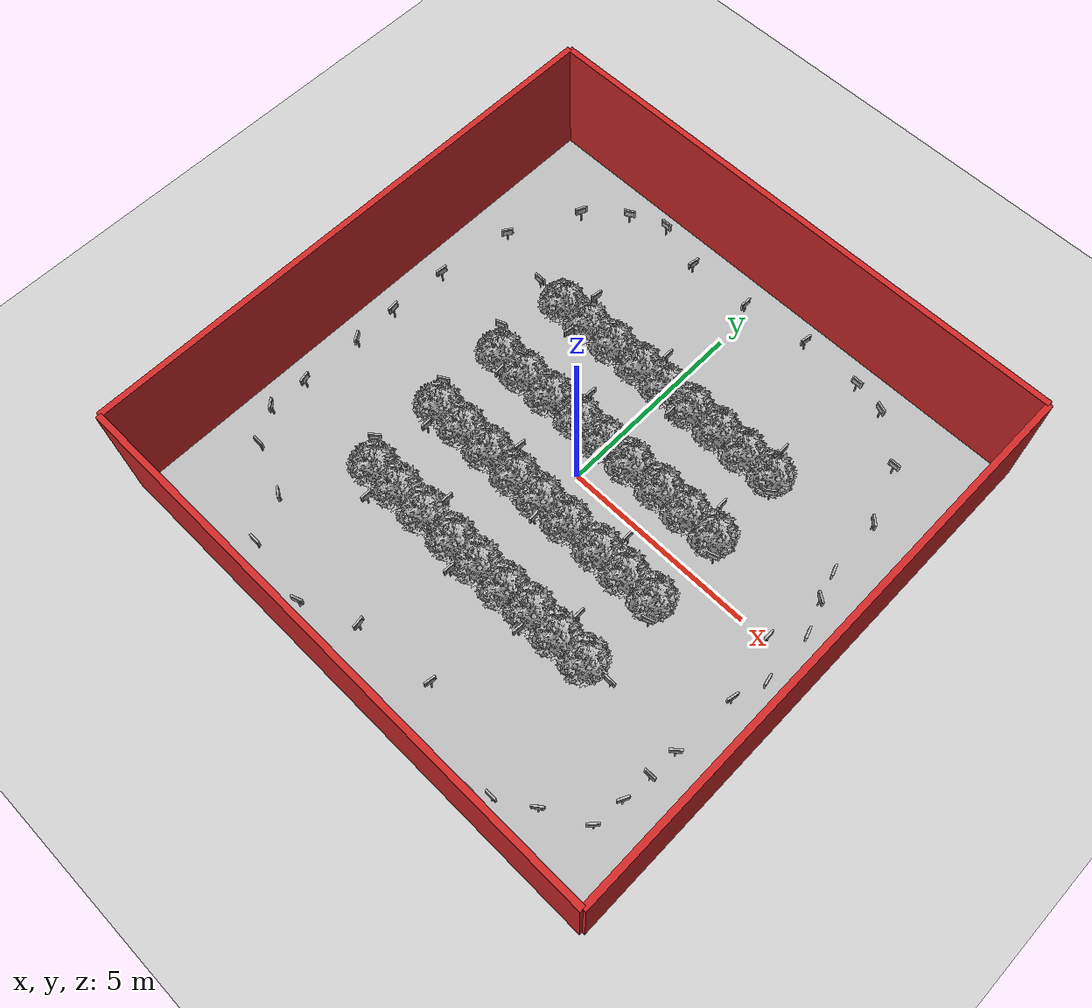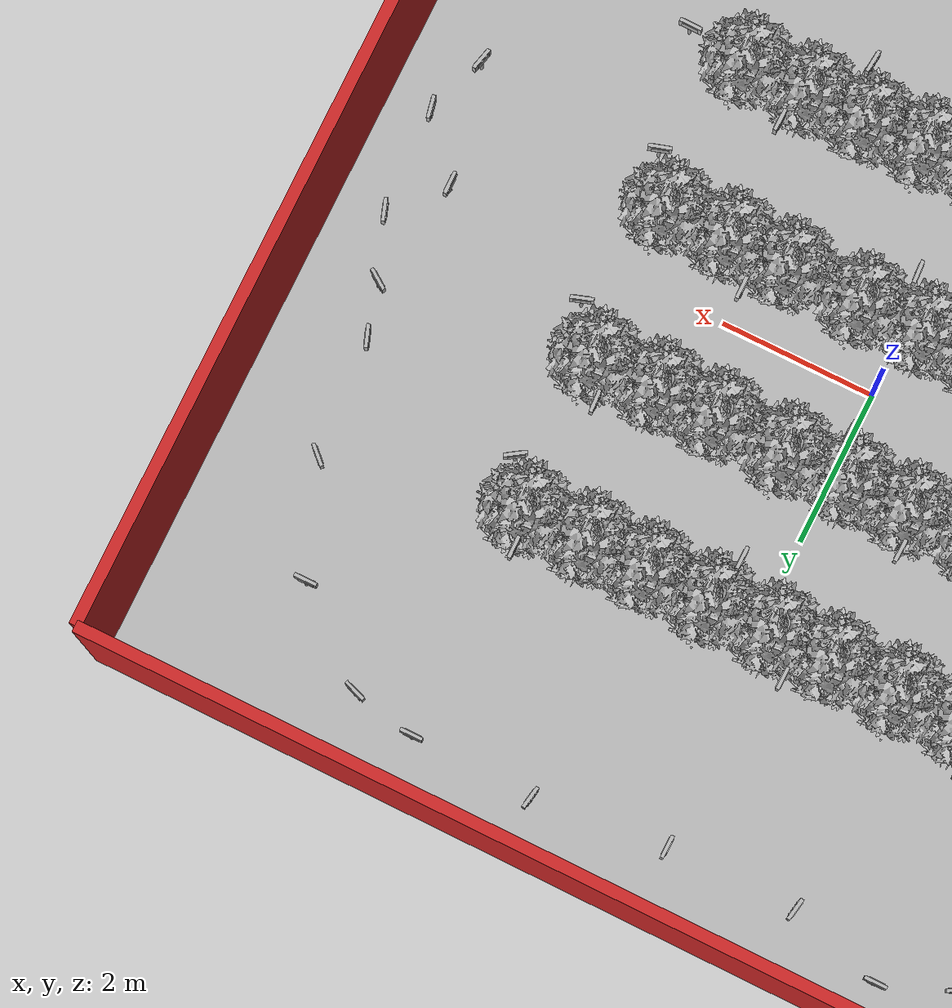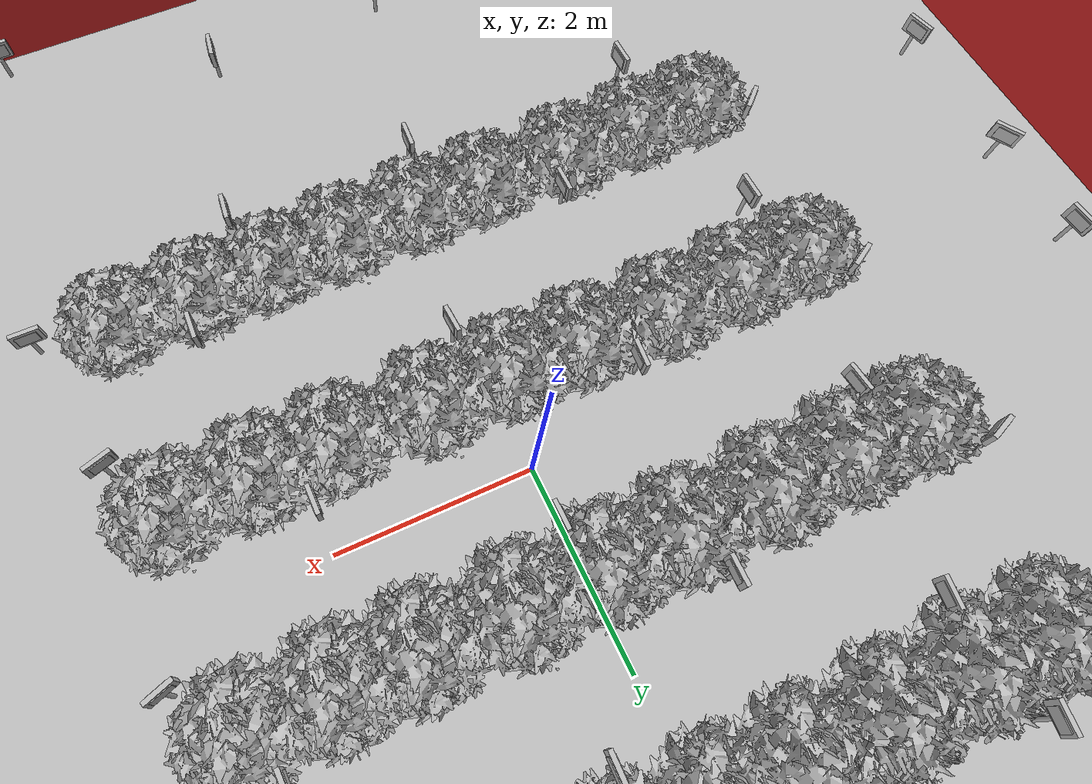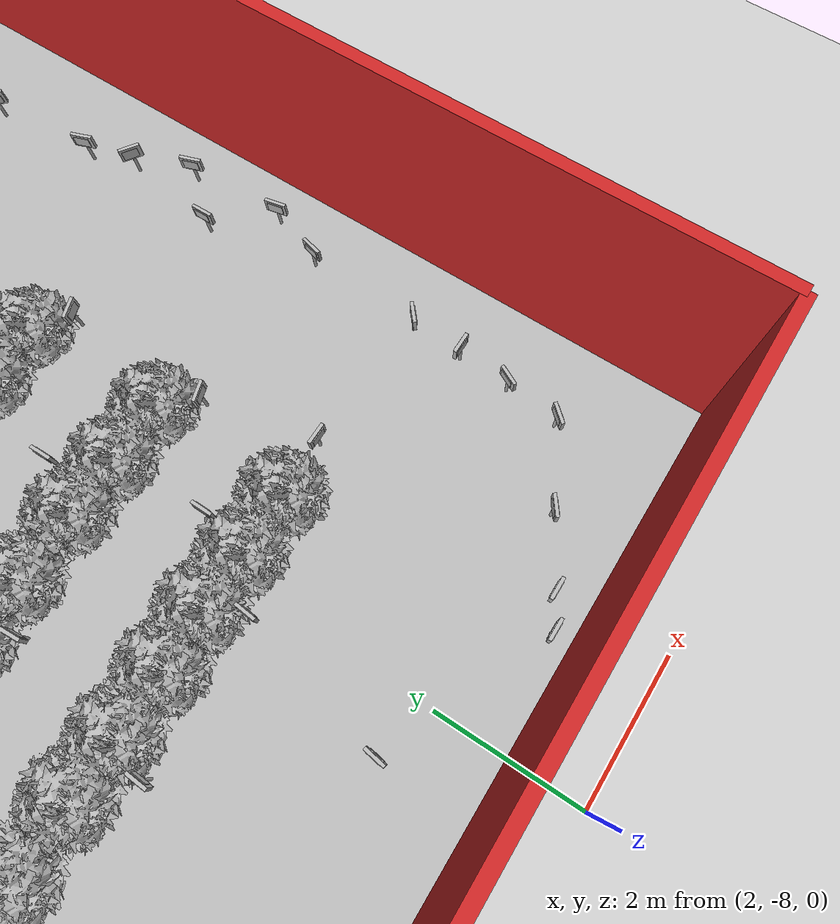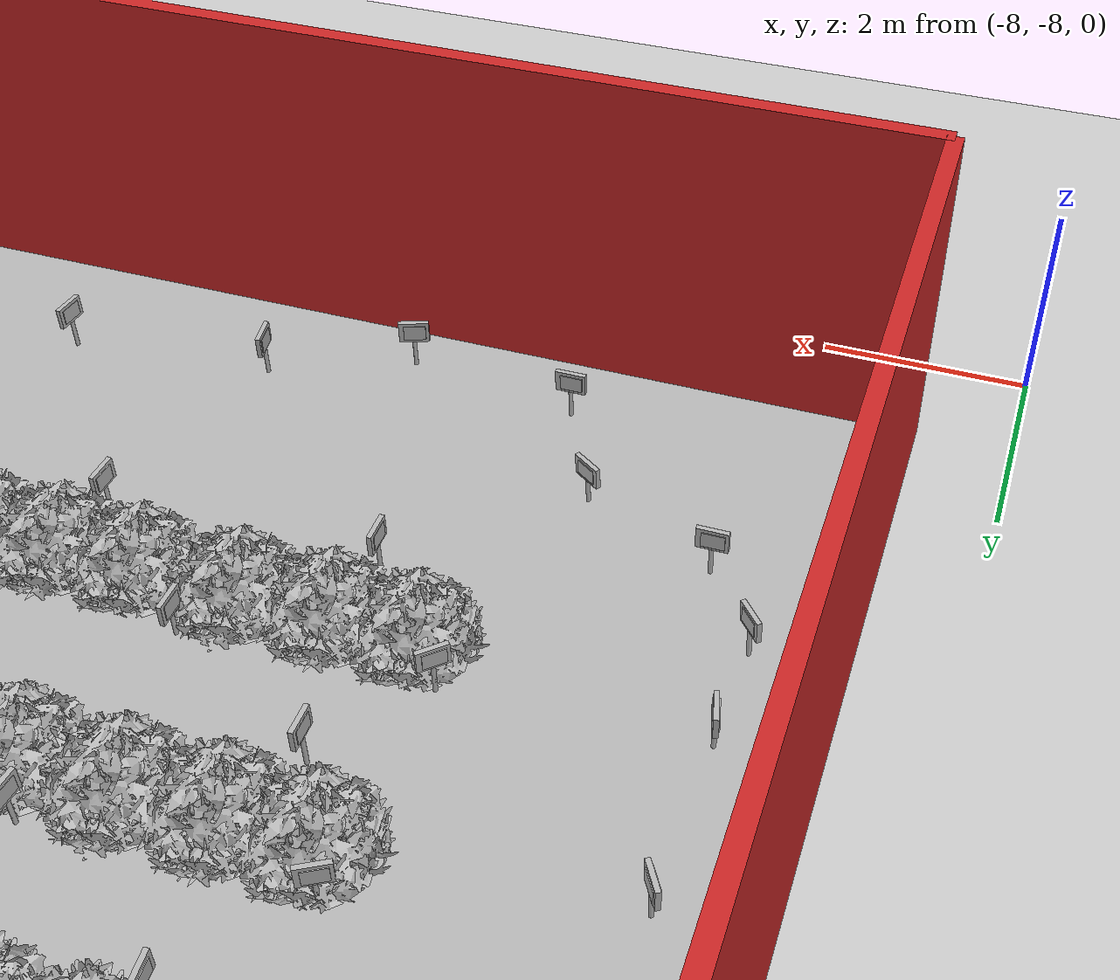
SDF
<sdf version="1.7">
 <world name="default">
  <light name="sun" type="directional">
   <pose>0 0 10 0 -0 0</pose>
   <diffuse>0.8 0.8 0.8 1</diffuse>
   <specular>0.2 0.2 0.2 1</specular>
   <attenuation>
    <range>1000</range>
    <constant>0.9</constant>
    <linear>0.01</linear>
    <quadratic>0.001</quadratic>
   </attenuation>
   <direction>-0.5 0.1 -0.9</direction>
   <spot><inner_angle>0</inner_angle><outer_angle>0</outer_angle><falloff>0</falloff></spot>
  </light>
  <model name="ground_plane">
   <static>1</static>
   <link name="link">
    <collision name="collision">
     <geometry><plane><normal>0 0 1</normal><size>100 100</size></plane></geometry>
     <surface>
      <contact><collide_bitmask>65535</collide_bitmask></contact>
      <friction><ode><mu>100</mu><mu2>50</mu2></ode></friction>
     </surface>
    </collision>
    <visual name="visual">
     <cast_shadows>0</cast_shadows>
     <geometry><plane><normal>0 0 1</normal><size>100 100</size></plane></geometry>
     <material>
      <script><uri>file://media/materials/scripts/gazebo.material</uri><name>Gazebo/Grey</name></script>
     </material>
    </visual>
   </link>
  </model>
  <gravity>0 0 -9.8</gravity>
  <magnetic_field>6e-06 2.3e-05 -4.2e-05</magnetic_field>
  <atmosphere type="adiabatic"/>
  <physics type="ode">
   <max_step_size>0.001</max_step_size>
   <real_time_factor>1</real_time_factor>
   <real_time_update_rate>1000</real_time_update_rate>
  </physics>
  <scene><ambient>0.4 0.4 0.4 1</ambient><background>0.7 0.7 0.7 1</background><shadows>1</shadows></scene>
  <spherical_coordinates>
   <surface_model>EARTH_WGS84</surface_model>
   <latitude_deg>0</latitude_deg>
   <longitude_deg>0</longitude_deg>
   <elevation>0</elevation>
   <heading_deg>0</heading_deg>
  </spherical_coordinates>
  <model name="paredladrillo">
   <pose>-0.015788 -0.036133 0 0 -0 0</pose>
   <link name="Wall_0">
    <collision name="Wall_0_Collision">
     <geometry><box><size>14 0.15 4</size></box></geometry>
     <pose>0 0 1.25 0 -0 0</pose>
    </collision>
    <visual name="Wall_0_Visual">
     <pose>0 0 1.25 0 -0 0</pose>
     <geometry><box><size>14 0.15 4</size></box></geometry>
     <material>
      <script>
       <uri>model://paredladrillo/materials/scripts</uri>
       <uri>model://paredladrillo/materials/textures</uri>
       <name>textur/pared</name>
      </script>
      <ambient>1 1 1 1</ambient>
     </material>
     <meta><layer>0</layer></meta>
    </visual>
    <pose>-7 -0 0 0 -0 1.5708</pose>
   </link>
   <link name="Wall_1">
    <collision name="Wall_1_Collision">
     <geometry><box><size>14 0.15 4</size></box></geometry>
     <pose>0 0 1.25 0 -0 0</pose>
    </collision>
    <visual name="Wall_1_Visual">
     <pose>0 0 1.25 0 -0 0</pose>
     <geometry><box><size>14 0.15 4</size></box></geometry>
     <material>
      <script>
       <uri>model://paredladrillo/materials/scripts</uri>
       <uri>model://paredladrillo/materials/textures</uri>
       <name>textur/pared</name>
      </script>
      <ambient>1 1 1 1</ambient>
     </material>
     <meta><layer>0</layer></meta>
    </visual>
    <pose>1e-06 7 0 0 -0 0</pose>
   </link>
   <link name="Wall_2">
    <collision name="Wall_2_Collision">
     <geometry><box><size>14 0.15 4</size></box></geometry>
     <pose>0 0 1.25 0 -0 0</pose>
    </collision>
    <visual name="Wall_2_Visual">
     <pose>0 0 1.25 0 -0 0</pose>
     <geometry><box><size>14 0.15 4</size></box></geometry>
     <material>
      <script>
       <uri>model://paredladrillo/materials/scripts</uri>
       <uri>model://paredladrillo/materials/textures</uri>
       <name>textur/pared</name>
      </script>
      <ambient>1 1 1 1</ambient>
     </material>
     <meta><layer>0</layer></meta>
    </visual>
    <pose>7 -0 0 0 -0 -1.5708</pose>
   </link>
   <link name="Wall_3">
    <collision name="Wall_3_Collision">
     <geometry><box><size>14 0.15 4</size></box></geometry>
     <pose>0 0 1.25 0 -0 0</pose>
    </collision>
    <visual name="Wall_3_Visual">
     <pose>0 0 1.25 0 -0 0</pose>
     <geometry><box><size>14 0.15 4</size></box></geometry>
     <material>
      <script>
       <uri>model://paredladrillo/materials/scripts</uri>
       <uri>model://paredladrillo/materials/textures</uri>
       <name>textur/pared</name>
      </script>
      <ambient>1 1 1 1</ambient>
     </material>
     <meta><layer>0</layer></meta>
    </visual>
    <pose>1e-06 -7 0 0 -0 3.14159</pose>
   </link>
   <static>1</static>
  </model>
  <model name="abbfre">
   <link name="link_0">
    <inertial>
     <mass>1</mass>
     <inertia>
      <ixx>0.166667</ixx>
      <ixy>0</ixy>
      <ixz>0</ixz>
      <iyy>0.166667</iyy>
      <iyz>0</iyz>
      <izz>0.166667</izz>
     </inertia>
    </inertial>
    <pose>0 0 -0 1.60917 -0 0</pose>
    <visual name="visual">
     <geometry><mesh><uri>model://abbfre/meshes/arbufres.obj</uri><scale>1 1 1</scale></mesh></geometry>
    </visual>
    <collision name="collision">
     <geometry><mesh><uri>model://abbfre/meshes/arbufres.obj</uri><scale>1 1 1</scale></mesh></geometry>
     <surface>
      <friction>
       <ode><mu>1</mu><mu2>1</mu2><fdir1>0 0 0</fdir1><slip1>0</slip1><slip2>0</slip2></ode>
       <torsional>
        <coefficient>1</coefficient>
        <patch_radius>0</patch_radius>
        <surface_radius>0</surface_radius>
        <use_patch_radius>1</use_patch_radius>
        <ode><slip>0</slip></ode>
       </torsional>
      </friction>
      <bounce><restitution_coefficient>0</restitution_coefficient><threshold>1e+06</threshold></bounce>
      <contact>
       <collide_without_contact>0</collide_without_contact>
       <collide_without_contact_bitmask>1</collide_without_contact_bitmask>
       <collide_bitmask>1</collide_bitmask>
       <ode>
        <soft_cfm>0</soft_cfm>
        <soft_erp>0.2</soft_erp>
        <kp>1e+13</kp>
        <kd>1</kd>
        <max_vel>0.01</max_vel>
        <min_depth>0</min_depth>
       </ode>
       <bullet>
        <split_impulse>1</split_impulse>
        <split_impulse_penetration_threshold>-0.01</split_impulse_penetration_threshold>
        <soft_cfm>0</soft_cfm>
        <soft_erp>0.2</soft_erp>
        <kp>1e+13</kp>
        <kd>1</kd>
       </bullet>
      </contact>
     </surface>
    </collision>
   </link>
   <static>1</static>
   <pose>-0.209599 -0.883769 0 0 -0 0</pose>
  </model>
  <model name="abbfre_0">
   <link name="link_0">
    <inertial>
     <mass>1</mass>
     <inertia>
      <ixx>0.166667</ixx>
      <ixy>0</ixy>
      <ixz>0</ixz>
      <iyy>0.166667</iyy>
      <iyz>0</iyz>
      <izz>0.166667</izz>
     </inertia>
    </inertial>
    <pose>0 0 -0 1.60917 -0 0</pose>
    <visual name="visual">
     <geometry><mesh><uri>model://abbfre/meshes/arbufres.obj</uri><scale>1 1 1</scale></mesh></geometry>
    </visual>
    <collision name="collision">
     <geometry><mesh><uri>model://abbfre/meshes/arbufres.obj</uri><scale>1 1 1</scale></mesh></geometry>
     <surface>
      <friction>
       <ode><mu>1</mu><mu2>1</mu2><fdir1>0 0 0</fdir1><slip1>0</slip1><slip2>0</slip2></ode>
       <torsional>
        <coefficient>1</coefficient>
        <patch_radius>0</patch_radius>
        <surface_radius>0</surface_radius>
        <use_patch_radius>1</use_patch_radius>
        <ode><slip>0</slip></ode>
       </torsional>
      </friction>
      <bounce><restitution_coefficient>0</restitution_coefficient><threshold>1e+06</threshold></bounce>
      <contact>
       <collide_without_contact>0</collide_without_contact>
       <collide_without_contact_bitmask>1</collide_without_contact_bitmask>
       <collide_bitmask>1</collide_bitmask>
       <ode>
        <soft_cfm>0</soft_cfm>
        <soft_erp>0.2</soft_erp>
        <kp>1e+13</kp>
        <kd>1</kd>
        <max_vel>0.01</max_vel>
        <min_depth>0</min_depth>
       </ode>
       <bullet>
        <split_impulse>1</split_impulse>
        <split_impulse_penetration_threshold>-0.01</split_impulse_penetration_threshold>
        <soft_cfm>0</soft_cfm>
        <soft_erp>0.2</soft_erp>
        <kp>1e+13</kp>
        <kd>1</kd>
       </bullet>
      </contact>
     </surface>
    </collision>
   </link>
   <static>1</static>
   <pose>-0.187908 1.17604 0 0 -0 0</pose>
  </model>
  <model name="abbfre_1">
   <link name="link_0">
    <inertial>
     <mass>1</mass>
     <inertia>
      <ixx>0.166667</ixx>
      <ixy>0</ixy>
      <ixz>0</ixz>
      <iyy>0.166667</iyy>
      <iyz>0</iyz>
      <izz>0.166667</izz>
     </inertia>
    </inertial>
    <pose>0 0 -0 1.60917 -0 0</pose>
    <visual name="visual">
     <geometry><mesh><uri>model://abbfre/meshes/arbufres.obj</uri><scale>1 1 1</scale></mesh></geometry>
    </visual>
    <collision name="collision">
     <geometry><mesh><uri>model://abbfre/meshes/arbufres.obj</uri><scale>1 1 1</scale></mesh></geometry>
     <surface>
      <friction>
       <ode><mu>1</mu><mu2>1</mu2><fdir1>0 0 0</fdir1><slip1>0</slip1><slip2>0</slip2></ode>
       <torsional>
        <coefficient>1</coefficient>
        <patch_radius>0</patch_radius>
        <surface_radius>0</surface_radius>
        <use_patch_radius>1</use_patch_radius>
        <ode><slip>0</slip></ode>
       </torsional>
      </friction>
      <bounce><restitution_coefficient>0</restitution_coefficient><threshold>1e+06</threshold></bounce>
      <contact>
       <collide_without_contact>0</collide_without_contact>
       <collide_without_contact_bitmask>1</collide_without_contact_bitmask>
       <collide_bitmask>1</collide_bitmask>
       <ode>
        <soft_cfm>0</soft_cfm>
        <soft_erp>0.2</soft_erp>
        <kp>1e+13</kp>
        <kd>1</kd>
        <max_vel>0.01</max_vel>
        <min_depth>0</min_depth>
       </ode>
       <bullet>
        <split_impulse>1</split_impulse>
        <split_impulse_penetration_threshold>-0.01</split_impulse_penetration_threshold>
        <soft_cfm>0</soft_cfm>
        <soft_erp>0.2</soft_erp>
        <kp>1e+13</kp>
        <kd>1</kd>
       </bullet>
      </contact>
     </surface>
    </collision>
   </link>
   <static>1</static>
   <pose>2.39954 1.16901 0 0 -0 0</pose>
  </model>
  <model name="abbfre_2">
   <link name="link_0">
    <inertial>
     <mass>1</mass>
     <inertia>
      <ixx>0.166667</ixx>
      <ixy>0</ixy>
      <ixz>0</ixz>
      <iyy>0.166667</iyy>
      <iyz>0</iyz>
      <izz>0.166667</izz>
     </inertia>
    </inertial>
    <pose>0 0 -0 1.60917 -0 0</pose>
    <visual name="visual">
     <geometry><mesh><uri>model://abbfre/meshes/arbufres.obj</uri><scale>1 1 1</scale></mesh></geometry>
    </visual>
    <collision name="collision">
     <geometry><mesh><uri>model://abbfre/meshes/arbufres.obj</uri><scale>1 1 1</scale></mesh></geometry>
     <surface>
      <friction>
       <ode><mu>1</mu><mu2>1</mu2><fdir1>0 0 0</fdir1><slip1>0</slip1><slip2>0</slip2></ode>
       <torsional>
        <coefficient>1</coefficient>
        <patch_radius>0</patch_radius>
        <surface_radius>0</surface_radius>
        <use_patch_radius>1</use_patch_radius>
        <ode><slip>0</slip></ode>
       </torsional>
      </friction>
      <bounce><restitution_coefficient>0</restitution_coefficient><threshold>1e+06</threshold></bounce>
      <contact>
       <collide_without_contact>0</collide_without_contact>
       <collide_without_contact_bitmask>1</collide_without_contact_bitmask>
       <collide_bitmask>1</collide_bitmask>
       <ode>
        <soft_cfm>0</soft_cfm>
        <soft_erp>0.2</soft_erp>
        <kp>1e+13</kp>
        <kd>1</kd>
        <max_vel>0.01</max_vel>
        <min_depth>0</min_depth>
       </ode>
       <bullet>
        <split_impulse>1</split_impulse>
        <split_impulse_penetration_threshold>-0.01</split_impulse_penetration_threshold>
        <soft_cfm>0</soft_cfm>
        <soft_erp>0.2</soft_erp>
        <kp>1e+13</kp>
        <kd>1</kd>
       </bullet>
      </contact>
     </surface>
    </collision>
   </link>
   <static>1</static>
   <pose>2.4303 -0.881882 0 0 -0 0</pose>
  </model>
  <model name="abbfre_3">
   <link name="link_0">
    <inertial>
     <mass>1</mass>
     <inertia>
      <ixx>0.166667</ixx>
      <ixy>0</ixy>
      <ixz>0</ixz>
      <iyy>0.166667</iyy>
      <iyz>0</iyz>
      <izz>0.166667</izz>
     </inertia>
    </inertial>
    <pose>0 0 -0 1.60917 -0 0</pose>
    <visual name="visual">
     <geometry><mesh><uri>model://abbfre/meshes/arbufres.obj</uri><scale>1 1 1</scale></mesh></geometry>
    </visual>
    <collision name="collision">
     <geometry><mesh><uri>model://abbfre/meshes/arbufres.obj</uri><scale>1 1 1</scale></mesh></geometry>
     <surface>
      <friction>
       <ode><mu>1</mu><mu2>1</mu2><fdir1>0 0 0</fdir1><slip1>0</slip1><slip2>0</slip2></ode>
       <torsional>
        <coefficient>1</coefficient>
        <patch_radius>0</patch_radius>
        <surface_radius>0</surface_radius>
        <use_patch_radius>1</use_patch_radius>
        <ode><slip>0</slip></ode>
       </torsional>
      </friction>
      <bounce><restitution_coefficient>0</restitution_coefficient><threshold>1e+06</threshold></bounce>
      <contact>
       <collide_without_contact>0</collide_without_contact>
       <collide_without_contact_bitmask>1</collide_without_contact_bitmask>
       <collide_bitmask>1</collide_bitmask>
       <ode>
        <soft_cfm>0</soft_cfm>
        <soft_erp>0.2</soft_erp>
        <kp>1e+13</kp>
        <kd>1</kd>
        <max_vel>0.01</max_vel>
        <min_depth>0</min_depth>
       </ode>
       <bullet>
        <split_impulse>1</split_impulse>
        <split_impulse_penetration_threshold>-0.01</split_impulse_penetration_threshold>
        <soft_cfm>0</soft_cfm>
        <soft_erp>0.2</soft_erp>
        <kp>1e+13</kp>
        <kd>1</kd>
       </bullet>
      </contact>
     </surface>
    </collision>
   </link>
   <static>1</static>
   <pose>-2.77312 1.16001 0 0 -0 0</pose>
  </model>
  <model name="abbfre_4">
   <link name="link_0">
    <inertial>
     <mass>1</mass>
     <inertia>
      <ixx>0.166667</ixx>
      <ixy>0</ixy>
      <ixz>0</ixz>
      <iyy>0.166667</iyy>
      <iyz>0</iyz>
      <izz>0.166667</izz>
     </inertia>
    </inertial>
    <pose>0 0 -0 1.60917 -0 0</pose>
    <visual name="visual">
     <geometry><mesh><uri>model://abbfre/meshes/arbufres.obj</uri><scale>1 1 1</scale></mesh></geometry>
    </visual>
    <collision name="collision">
     <geometry><mesh><uri>model://abbfre/meshes/arbufres.obj</uri><scale>1 1 1</scale></mesh></geometry>
     <surface>
      <friction>
       <ode><mu>1</mu><mu2>1</mu2><fdir1>0 0 0</fdir1><slip1>0</slip1><slip2>0</slip2></ode>
       <torsional>
        <coefficient>1</coefficient>
        <patch_radius>0</patch_radius>
        <surface_radius>0</surface_radius>
        <use_patch_radius>1</use_patch_radius>
        <ode><slip>0</slip></ode>
       </torsional>
      </friction>
      <bounce><restitution_coefficient>0</restitution_coefficient><threshold>1e+06</threshold></bounce>
      <contact>
       <collide_without_contact>0</collide_without_contact>
       <collide_without_contact_bitmask>1</collide_without_contact_bitmask>
       <collide_bitmask>1</collide_bitmask>
       <ode>
        <soft_cfm>0</soft_cfm>
        <soft_erp>0.2</soft_erp>
        <kp>1e+13</kp>
        <kd>1</kd>
        <max_vel>0.01</max_vel>
        <min_depth>0</min_depth>
       </ode>
       <bullet>
        <split_impulse>1</split_impulse>
        <split_impulse_penetration_threshold>-0.01</split_impulse_penetration_threshold>
        <soft_cfm>0</soft_cfm>
        <soft_erp>0.2</soft_erp>
        <kp>1e+13</kp>
        <kd>1</kd>
       </bullet>
      </contact>
     </surface>
    </collision>
   </link>
   <static>1</static>
   <pose>-2.78374 -0.856745 0 0 -0 0</pose>
  </model>
  <model name="abbfre_5">
   <link name="link_0">
    <inertial>
     <mass>1</mass>
     <inertia>
      <ixx>0.166667</ixx>
      <ixy>0</ixy>
      <ixz>0</ixz>
      <iyy>0.166667</iyy>
      <iyz>0</iyz>
      <izz>0.166667</izz>
     </inertia>
    </inertial>
    <pose>0 0 -0 1.60917 -0 0</pose>
    <visual name="visual">
     <geometry><mesh><uri>model://abbfre/meshes/arbufres.obj</uri><scale>1 1 1</scale></mesh></geometry>
    </visual>
    <collision name="collision">
     <geometry><mesh><uri>model://abbfre/meshes/arbufres.obj</uri><scale>1 1 1</scale></mesh></geometry>
     <surface>
      <friction>
       <ode><mu>1</mu><mu2>1</mu2><fdir1>0 0 0</fdir1><slip1>0</slip1><slip2>0</slip2></ode>
       <torsional>
        <coefficient>1</coefficient>
        <patch_radius>0</patch_radius>
        <surface_radius>0</surface_radius>
        <use_patch_radius>1</use_patch_radius>
        <ode><slip>0</slip></ode>
       </torsional>
      </friction>
      <bounce><restitution_coefficient>0</restitution_coefficient><threshold>1e+06</threshold></bounce>
      <contact>
       <collide_without_contact>0</collide_without_contact>
       <collide_without_contact_bitmask>1</collide_without_contact_bitmask>
       <collide_bitmask>1</collide_bitmask>
       <ode>
        <soft_cfm>0</soft_cfm>
        <soft_erp>0.2</soft_erp>
        <kp>1e+13</kp>
        <kd>1</kd>
        <max_vel>0.01</max_vel>
        <min_depth>0</min_depth>
       </ode>
       <bullet>
        <split_impulse>1</split_impulse>
        <split_impulse_penetration_threshold>-0.01</split_impulse_penetration_threshold>
        <soft_cfm>0</soft_cfm>
        <soft_erp>0.2</soft_erp>
        <kp>1e+13</kp>
        <kd>1</kd>
       </bullet>
      </contact>
     </surface>
    </collision>
   </link>
   <static>1</static>
   <pose>-0.145619 3.21888 0 0 -0 0</pose>
  </model>
  <model name="abbfre_6">
   <link name="link_0">
    <inertial>
     <mass>1</mass>
     <inertia>
      <ixx>0.166667</ixx>
      <ixy>0</ixy>
      <ixz>0</ixz>
      <iyy>0.166667</iyy>
      <iyz>0</iyz>
      <izz>0.166667</izz>
     </inertia>
    </inertial>
    <pose>0 0 -0 1.60917 -0 0</pose>
    <visual name="visual">
     <geometry><mesh><uri>model://abbfre/meshes/arbufres.obj</uri><scale>1 1 1</scale></mesh></geometry>
    </visual>
    <collision name="collision">
     <geometry><mesh><uri>model://abbfre/meshes/arbufres.obj</uri><scale>1 1 1</scale></mesh></geometry>
     <surface>
      <friction>
       <ode><mu>1</mu><mu2>1</mu2><fdir1>0 0 0</fdir1><slip1>0</slip1><slip2>0</slip2></ode>
       <torsional>
        <coefficient>1</coefficient>
        <patch_radius>0</patch_radius>
        <surface_radius>0</surface_radius>
        <use_patch_radius>1</use_patch_radius>
        <ode><slip>0</slip></ode>
       </torsional>
      </friction>
      <bounce><restitution_coefficient>0</restitution_coefficient><threshold>1e+06</threshold></bounce>
      <contact>
       <collide_without_contact>0</collide_without_contact>
       <collide_without_contact_bitmask>1</collide_without_contact_bitmask>
       <collide_bitmask>1</collide_bitmask>
       <ode>
        <soft_cfm>0</soft_cfm>
        <soft_erp>0.2</soft_erp>
        <kp>1e+13</kp>
        <kd>1</kd>
        <max_vel>0.01</max_vel>
        <min_depth>0</min_depth>
       </ode>
       <bullet>
        <split_impulse>1</split_impulse>
        <split_impulse_penetration_threshold>-0.01</split_impulse_penetration_threshold>
        <soft_cfm>0</soft_cfm>
        <soft_erp>0.2</soft_erp>
        <kp>1e+13</kp>
        <kd>1</kd>
       </bullet>
      </contact>
     </surface>
    </collision>
   </link>
   <static>1</static>
   <pose>2.3443 3.2131 0 0 -0 0</pose>
  </model>
  <model name="abbfre_7">
   <link name="link_0">
    <inertial>
     <mass>1</mass>
     <inertia>
      <ixx>0.166667</ixx>
      <ixy>0</ixy>
      <ixz>0</ixz>
      <iyy>0.166667</iyy>
      <iyz>0</iyz>
      <izz>0.166667</izz>
     </inertia>
    </inertial>
    <pose>0 0 -0 1.60917 -0 0</pose>
    <visual name="visual">
     <geometry><mesh><uri>model://abbfre/meshes/arbufres.obj</uri><scale>1 1 1</scale></mesh></geometry>
    </visual>
    <collision name="collision">
     <geometry><mesh><uri>model://abbfre/meshes/arbufres.obj</uri><scale>1 1 1</scale></mesh></geometry>
     <surface>
      <friction>
       <ode><mu>1</mu><mu2>1</mu2><fdir1>0 0 0</fdir1><slip1>0</slip1><slip2>0</slip2></ode>
       <torsional>
        <coefficient>1</coefficient>
        <patch_radius>0</patch_radius>
        <surface_radius>0</surface_radius>
        <use_patch_radius>1</use_patch_radius>
        <ode><slip>0</slip></ode>
       </torsional>
      </friction>
      <bounce><restitution_coefficient>0</restitution_coefficient><threshold>1e+06</threshold></bounce>
      <contact>
       <collide_without_contact>0</collide_without_contact>
       <collide_without_contact_bitmask>1</collide_without_contact_bitmask>
       <collide_bitmask>1</collide_bitmask>
       <ode>
        <soft_cfm>0</soft_cfm>
        <soft_erp>0.2</soft_erp>
        <kp>1e+13</kp>
        <kd>1</kd>
        <max_vel>0.01</max_vel>
        <min_depth>0</min_depth>
       </ode>
       <bullet>
        <split_impulse>1</split_impulse>
        <split_impulse_penetration_threshold>-0.01</split_impulse_penetration_threshold>
        <soft_cfm>0</soft_cfm>
        <soft_erp>0.2</soft_erp>
        <kp>1e+13</kp>
        <kd>1</kd>
       </bullet>
      </contact>
     </surface>
    </collision>
   </link>
   <static>1</static>
   <pose>-2.67738 3.21551 0 0 -0 0</pose>
  </model>
  <model name="abbfre_8">
   <link name="link_0">
    <inertial>
     <mass>1</mass>
     <inertia>
      <ixx>0.166667</ixx>
      <ixy>0</ixy>
      <ixz>0</ixz>
      <iyy>0.166667</iyy>
      <iyz>0</iyz>
      <izz>0.166667</izz>
     </inertia>
    </inertial>
    <pose>0 0 -0 1.60917 -0 0</pose>
    <visual name="visual">
     <geometry><mesh><uri>model://abbfre/meshes/arbufres.obj</uri><scale>1 1 1</scale></mesh></geometry>
    </visual>
    <collision name="collision">
     <geometry><mesh><uri>model://abbfre/meshes/arbufres.obj</uri><scale>1 1 1</scale></mesh></geometry>
     <surface>
      <friction>
       <ode><mu>1</mu><mu2>1</mu2><fdir1>0 0 0</fdir1><slip1>0</slip1><slip2>0</slip2></ode>
       <torsional>
        <coefficient>1</coefficient>
        <patch_radius>0</patch_radius>
        <surface_radius>0</surface_radius>
        <use_patch_radius>1</use_patch_radius>
        <ode><slip>0</slip></ode>
       </torsional>
      </friction>
      <bounce><restitution_coefficient>0</restitution_coefficient><threshold>1e+06</threshold></bounce>
      <contact>
       <collide_without_contact>0</collide_without_contact>
       <collide_without_contact_bitmask>1</collide_without_contact_bitmask>
       <collide_bitmask>1</collide_bitmask>
       <ode>
        <soft_cfm>0</soft_cfm>
        <soft_erp>0.2</soft_erp>
        <kp>1e+13</kp>
        <kd>1</kd>
        <max_vel>0.01</max_vel>
        <min_depth>0</min_depth>
       </ode>
       <bullet>
        <split_impulse>1</split_impulse>
        <split_impulse_penetration_threshold>-0.01</split_impulse_penetration_threshold>
        <soft_cfm>0</soft_cfm>
        <soft_erp>0.2</soft_erp>
        <kp>1e+13</kp>
        <kd>1</kd>
       </bullet>
      </contact>
     </surface>
    </collision>
   </link>
   <static>1</static>
   <pose>2.34792 -2.93612 0 0 -0 0</pose>
  </model>
  <model name="abbfre_9">
   <link name="link_0">
    <inertial>
     <mass>1</mass>
     <inertia>
      <ixx>0.166667</ixx>
      <ixy>0</ixy>
      <ixz>0</ixz>
      <iyy>0.166667</iyy>
      <iyz>0</iyz>
      <izz>0.166667</izz>
     </inertia>
    </inertial>
    <pose>0 0 -0 1.60917 -0 0</pose>
    <visual name="visual">
     <geometry><mesh><uri>model://abbfre/meshes/arbufres.obj</uri><scale>1 1 1</scale></mesh></geometry>
    </visual>
    <collision name="collision">
     <geometry><mesh><uri>model://abbfre/meshes/arbufres.obj</uri><scale>1 1 1</scale></mesh></geometry>
     <surface>
      <friction>
       <ode><mu>1</mu><mu2>1</mu2><fdir1>0 0 0</fdir1><slip1>0</slip1><slip2>0</slip2></ode>
       <torsional>
        <coefficient>1</coefficient>
        <patch_radius>0</patch_radius>
        <surface_radius>0</surface_radius>
        <use_patch_radius>1</use_patch_radius>
        <ode><slip>0</slip></ode>
       </torsional>
      </friction>
      <bounce><restitution_coefficient>0</restitution_coefficient><threshold>1e+06</threshold></bounce>
      <contact>
       <collide_without_contact>0</collide_without_contact>
       <collide_without_contact_bitmask>1</collide_without_contact_bitmask>
       <collide_bitmask>1</collide_bitmask>
       <ode>
        <soft_cfm>0</soft_cfm>
        <soft_erp>0.2</soft_erp>
        <kp>1e+13</kp>
        <kd>1</kd>
        <max_vel>0.01</max_vel>
        <min_depth>0</min_depth>
       </ode>
       <bullet>
        <split_impulse>1</split_impulse>
        <split_impulse_penetration_threshold>-0.01</split_impulse_penetration_threshold>
        <soft_cfm>0</soft_cfm>
        <soft_erp>0.2</soft_erp>
        <kp>1e+13</kp>
        <kd>1</kd>
       </bullet>
      </contact>
     </surface>
    </collision>
   </link>
   <static>1</static>
   <pose>-0.087861 -2.97501 0 0 -0 0</pose>
  </model>
  <model name="abbfre_10">
   <link name="link_0">
    <inertial>
     <mass>1</mass>
     <inertia>
      <ixx>0.166667</ixx>
      <ixy>0</ixy>
      <ixz>0</ixz>
      <iyy>0.166667</iyy>
      <iyz>0</iyz>
      <izz>0.166667</izz>
     </inertia>
    </inertial>
    <pose>0 0 -0 1.60917 -0 0</pose>
    <visual name="visual">
     <geometry><mesh><uri>model://abbfre/meshes/arbufres.obj</uri><scale>1 1 1</scale></mesh></geometry>
    </visual>
    <collision name="collision">
     <geometry><mesh><uri>model://abbfre/meshes/arbufres.obj</uri><scale>1 1 1</scale></mesh></geometry>
     <surface>
      <friction>
       <ode><mu>1</mu><mu2>1</mu2><fdir1>0 0 0</fdir1><slip1>0</slip1><slip2>0</slip2></ode>
       <torsional>
        <coefficient>1</coefficient>
        <patch_radius>0</patch_radius>
        <surface_radius>0</surface_radius>
        <use_patch_radius>1</use_patch_radius>
        <ode><slip>0</slip></ode>
       </torsional>
      </friction>
      <bounce><restitution_coefficient>0</restitution_coefficient><threshold>1e+06</threshold></bounce>
      <contact>
       <collide_without_contact>0</collide_without_contact>
       <collide_without_contact_bitmask>1</collide_without_contact_bitmask>
       <collide_bitmask>1</collide_bitmask>
       <ode>
        <soft_cfm>0</soft_cfm>
        <soft_erp>0.2</soft_erp>
        <kp>1e+13</kp>
        <kd>1</kd>
        <max_vel>0.01</max_vel>
        <min_depth>0</min_depth>
       </ode>
       <bullet>
        <split_impulse>1</split_impulse>
        <split_impulse_penetration_threshold>-0.01</split_impulse_penetration_threshold>
        <soft_cfm>0</soft_cfm>
        <soft_erp>0.2</soft_erp>
        <kp>1e+13</kp>
        <kd>1</kd>
       </bullet>
      </contact>
     </surface>
    </collision>
   </link>
   <static>1</static>
   <pose>-2.70737 -2.9693 0 0 -0 0</pose>
  </model>
  <model name="letrero_fresa">
   <link name="link_0">
    <inertial>
     <mass>0.00543151</mass>
     <inertia>
      <ixx>4.90351e-06</ixx>
      <ixy>0</ixy>
      <ixz>0</ixz>
      <iyy>4.90351e-06</iyy>
      <iyz>0</iyz>
      <izz>1.12837e-07</izz>
     </inertia>
    </inertial>
    <pose>0.002372 -0.000902 -0.178803 0 -0 0</pose>
    <visual name="visual">
     <geometry><cylinder><radius>0.0203836</radius><length>0.327243</length></cylinder></geometry>
     <material>
      <lighting>1</lighting>
      <script>
       <uri>model://letrero_fresa/madera/scripts</uri>
       <uri>model://letrero_fresa/madera/textures</uri>
       <name>textur/madera</name>
      </script>
      <shader type="pixel"/>
      <emissive>0 0 0 1</emissive>
     </material>
    </visual>
    <collision name="collision">
     <geometry><cylinder><radius>0.020384</radius><length>0.327243</length></cylinder></geometry>
     <surface>
      <friction>
       <ode><mu>1</mu><mu2>1</mu2><fdir1>0 0 0</fdir1><slip1>0</slip1><slip2>0</slip2></ode>
       <torsional>
        <coefficient>1</coefficient>
        <patch_radius>0</patch_radius>
        <surface_radius>0</surface_radius>
        <use_patch_radius>1</use_patch_radius>
        <ode><slip>0</slip></ode>
       </torsional>
      </friction>
      <bounce><restitution_coefficient>0</restitution_coefficient><threshold>1e+06</threshold></bounce>
      <contact>
       <collide_without_contact>0</collide_without_contact>
       <collide_without_contact_bitmask>1</collide_without_contact_bitmask>
       <collide_bitmask>1</collide_bitmask>
       <ode>
        <soft_cfm>0</soft_cfm>
        <soft_erp>0.2</soft_erp>
        <kp>1e+13</kp>
        <kd>1</kd>
        <max_vel>0.01</max_vel>
        <min_depth>0</min_depth>
       </ode>
       <bullet>
        <split_impulse>1</split_impulse>
        <split_impulse_penetration_threshold>-0.01</split_impulse_penetration_threshold>
        <soft_cfm>0</soft_cfm>
        <soft_erp>0.2</soft_erp>
        <kp>1e+13</kp>
        <kd>1</kd>
       </bullet>
      </contact>
     </surface>
    </collision>
   </link>
   <link name="link_1">
    <inertial>
     <mass>0.00299633</mass>
     <inertia>
      <ixx>1.27855e-05</ixx>
      <ixy>0</ixy>
      <ixz>0</ixz>
      <iyy>3.42923e-05</iyy>
      <iyz>0</iyz>
      <izz>2.25402e-05</izz>
     </inertia>
    </inertial>
    <pose>-0.001685 -0.003559 0.089666 0 -0 0</pose>
    <visual name="visual">
     <geometry><box><size>0.296988 0.04549 0.221665</size></box></geometry>
     <material>
      <lighting>1</lighting>
      <script>
       <uri>model://letrero_fresa/madera/scripts</uri>
       <uri>model://letrero_fresa/madera/textures</uri>
       <name>textur/madera</name>
      </script>
      <shader type="pixel"/>
      <emissive>0 0 0 1</emissive>
     </material>
    </visual>
    <collision name="collision">
     <geometry><box><size>0.296988 0.04549 0.221665</size></box></geometry>
     <surface>
      <friction>
       <ode><mu>1</mu><mu2>1</mu2><fdir1>0 0 0</fdir1><slip1>0</slip1><slip2>0</slip2></ode>
       <torsional>
        <coefficient>1</coefficient>
        <patch_radius>0</patch_radius>
        <surface_radius>0</surface_radius>
        <use_patch_radius>1</use_patch_radius>
        <ode><slip>0</slip></ode>
       </torsional>
      </friction>
      <bounce><restitution_coefficient>0</restitution_coefficient><threshold>1e+06</threshold></bounce>
      <contact>
       <collide_without_contact>0</collide_without_contact>
       <collide_without_contact_bitmask>1</collide_without_contact_bitmask>
       <collide_bitmask>1</collide_bitmask>
       <ode>
        <soft_cfm>0</soft_cfm>
        <soft_erp>0.2</soft_erp>
        <kp>1e+13</kp>
        <kd>1</kd>
        <max_vel>0.01</max_vel>
        <min_depth>0</min_depth>
       </ode>
       <bullet>
        <split_impulse>1</split_impulse>
        <split_impulse_penetration_threshold>-0.01</split_impulse_penetration_threshold>
        <soft_cfm>0</soft_cfm>
        <soft_erp>0.2</soft_erp>
        <kp>1e+13</kp>
        <kd>1</kd>
       </bullet>
      </contact>
     </surface>
    </collision>
   </link>
   <link name="link_2">
    <inertial>
     <mass>0.00219695</mass>
     <inertia>
      <ixx>5.34209e-06</ixx>
      <ixy>0</ixy>
      <ixz>0</ixz>
      <iyy>1.31531e-05</iyy>
      <iyz>0</iyz>
      <izz>9.31738e-06</izz>
     </inertia>
    </inertial>
    <pose>-0.001275 -0.005928 0.089136 0 -0 0</pose>
    <visual name="visual">
     <geometry><box><size>0.216284 0.06414 0.15832</size></box></geometry>
     <material>
      <lighting>1</lighting>
      <script>
       <uri>model://letrero_fresa/materials/scripts</uri>
       <uri>model://letrero_fresa/materials/textures</uri>
       <name>textur/difre</name>
      </script>
      <shader type="pixel"/>
      <emissive>0 0 0 1</emissive>
     </material>
    </visual>
    <collision name="collision">
     <geometry><box><size>0.216284 0.06414 0.15832</size></box></geometry>
     <surface>
      <friction>
       <ode><mu>1</mu><mu2>1</mu2><fdir1>0 0 0</fdir1><slip1>0</slip1><slip2>0</slip2></ode>
       <torsional>
        <coefficient>1</coefficient>
        <patch_radius>0</patch_radius>
        <surface_radius>0</surface_radius>
        <use_patch_radius>1</use_patch_radius>
        <ode><slip>0</slip></ode>
       </torsional>
      </friction>
      <bounce><restitution_coefficient>0</restitution_coefficient><threshold>1e+06</threshold></bounce>
      <contact>
       <collide_without_contact>0</collide_without_contact>
       <collide_without_contact_bitmask>1</collide_without_contact_bitmask>
       <collide_bitmask>1</collide_bitmask>
       <ode>
        <soft_cfm>0</soft_cfm>
        <soft_erp>0.2</soft_erp>
        <kp>1e+13</kp>
        <kd>1</kd>
        <max_vel>0.01</max_vel>
        <min_depth>0</min_depth>
       </ode>
       <bullet>
        <split_impulse>1</split_impulse>
        <split_impulse_penetration_threshold>-0.01</split_impulse_penetration_threshold>
        <soft_cfm>0</soft_cfm>
        <soft_erp>0.2</soft_erp>
        <kp>1e+13</kp>
        <kd>1</kd>
       </bullet>
      </contact>
     </surface>
    </collision>
   </link>
   <joint name="link_0_JOINT_1" type="fixed">
    <parent>link_0</parent>
    <child>link_1</child>
    <physics>
     <ode><limit><cfm>0</cfm><erp>0.2</erp></limit><suspension><cfm>0</cfm><erp>0.2</erp></suspension></ode>
    </physics>
   </joint>
   <joint name="link_0_JOINT_2" type="fixed">
    <parent>link_0</parent>
    <child>link_2</child>
    <physics>
     <ode><limit><cfm>0</cfm><erp>0.2</erp></limit><suspension><cfm>0</cfm><erp>0.2</erp></suspension></ode>
    </physics>
   </joint>
   <static>1</static>
   <pose>-3.241 -1.63282 0.406811 0 -0 1.573</pose>
  </model>
  <model name="letrero_fresas_II">
   <link name="link_0">
    <inertial>
     <mass>0.0543151</mass>
     <inertia>
      <ixx>4.90351e-06</ixx>
      <ixy>0</ixy>
      <ixz>0</ixz>
      <iyy>4.90351e-06</iyy>
      <iyz>0</iyz>
      <izz>1.12837e-07</izz>
     </inertia>
    </inertial>
    <pose>0.002515 0.005109 0.153562 0 -0 0</pose>
    <visual name="visual">
     <geometry><cylinder><radius>0.0203836</radius><length>0.327243</length></cylinder></geometry>
     <material>
      <lighting>1</lighting>
      <script>
       <uri>model://letrero_fresas_II/madera/scripts</uri>
       <uri>model://letrero_fresas_II/madera/textures</uri>
       <name>textur/madera</name>
      </script>
      <shader type="pixel"/>
      <emissive>0 0 0 1</emissive>
     </material>
    </visual>
    <collision name="collision">
     <geometry><cylinder><radius>0.020384</radius><length>0.327243</length></cylinder></geometry>
     <surface>
      <friction>
       <ode><mu>1</mu><mu2>1</mu2><fdir1>0 0 0</fdir1><slip1>0</slip1><slip2>0</slip2></ode>
       <torsional>
        <coefficient>1</coefficient>
        <patch_radius>0</patch_radius>
        <surface_radius>0</surface_radius>
        <use_patch_radius>1</use_patch_radius>
        <ode><slip>0</slip></ode>
       </torsional>
      </friction>
      <bounce><restitution_coefficient>0</restitution_coefficient><threshold>1e+06</threshold></bounce>
      <contact>
       <collide_without_contact>0</collide_without_contact>
       <collide_without_contact_bitmask>1</collide_without_contact_bitmask>
       <collide_bitmask>1</collide_bitmask>
       <ode>
        <soft_cfm>0</soft_cfm>
        <soft_erp>0.2</soft_erp>
        <kp>1e+13</kp>
        <kd>1</kd>
        <max_vel>0.01</max_vel>
        <min_depth>0</min_depth>
       </ode>
       <bullet>
        <split_impulse>1</split_impulse>
        <split_impulse_penetration_threshold>-0.01</split_impulse_penetration_threshold>
        <soft_cfm>0</soft_cfm>
        <soft_erp>0.2</soft_erp>
        <kp>1e+13</kp>
        <kd>1</kd>
       </bullet>
      </contact>
     </surface>
    </collision>
   </link>
   <link name="link_1">
    <inertial>
     <mass>0.00299633</mass>
     <inertia>
      <ixx>1.27855e-05</ixx>
      <ixy>0</ixy>
      <ixz>0</ixz>
      <iyy>3.42923e-05</iyy>
      <iyz>0</iyz>
      <izz>2.25402e-05</izz>
     </inertia>
    </inertial>
    <pose>-0.001542 0.002452 0.422031 0 -0 0</pose>
    <visual name="visual">
     <geometry><box><size>0.296988 0.04549 0.221665</size></box></geometry>
     <material>
      <lighting>1</lighting>
      <script>
       <uri>model://letrero_fresas_II/madera/scripts</uri>
       <uri>model://letrero_fresas_II/madera/textures</uri>
       <name>textur/madera</name>
      </script>
      <shader type="pixel"/>
      <emissive>0 0 0 1</emissive>
     </material>
    </visual>
    <collision name="collision">
     <geometry><box><size>0.296988 0.04549 0.221665</size></box></geometry>
     <surface>
      <friction>
       <ode><mu>1</mu><mu2>1</mu2><fdir1>0 0 0</fdir1><slip1>0</slip1><slip2>0</slip2></ode>
       <torsional>
        <coefficient>1</coefficient>
        <patch_radius>0</patch_radius>
        <surface_radius>0</surface_radius>
        <use_patch_radius>1</use_patch_radius>
        <ode><slip>0</slip></ode>
       </torsional>
      </friction>
      <bounce><restitution_coefficient>0</restitution_coefficient><threshold>1e+06</threshold></bounce>
      <contact>
       <collide_without_contact>0</collide_without_contact>
       <collide_without_contact_bitmask>1</collide_without_contact_bitmask>
       <collide_bitmask>1</collide_bitmask>
       <ode>
        <soft_cfm>0</soft_cfm>
        <soft_erp>0.2</soft_erp>
        <kp>1e+13</kp>
        <kd>1</kd>
        <max_vel>0.01</max_vel>
        <min_depth>0</min_depth>
       </ode>
       <bullet>
        <split_impulse>1</split_impulse>
        <split_impulse_penetration_threshold>-0.01</split_impulse_penetration_threshold>
        <soft_cfm>0</soft_cfm>
        <soft_erp>0.2</soft_erp>
        <kp>1e+13</kp>
        <kd>1</kd>
       </bullet>
      </contact>
     </surface>
    </collision>
   </link>
   <link name="link_2">
    <inertial>
     <mass>0.00173577</mass>
     <inertia>
      <ixx>4.23206e-06</ixx>
      <ixy>0</ixy>
      <ixz>0</ixz>
      <iyy>1.03921e-05</iyy>
      <iyz>0</iyz>
      <izz>7.37287e-06</izz>
     </inertia>
    </inertial>
    <pose>-0.010225 0.002657 0.421501 0 -0 0</pose>
    <visual name="visual">
     <geometry><box><size>0.216284 0.064749 0.15832</size></box></geometry>
     <material>
      <lighting>1</lighting>
      <script>
       <uri>model://letrero_fresas_II/materials/scripts</uri>
       <uri>model://letrero_fresas_II/materials/textures</uri>
       <name>textur/difres</name>
      </script>
      <shader type="pixel"/>
      <emissive>0 0 0 1</emissive>
     </material>
    </visual>
    <collision name="collision">
     <geometry><box><size>0.216284 0.064749 0.15832</size></box></geometry>
     <surface>
      <friction>
       <ode><mu>1</mu><mu2>1</mu2><fdir1>0 0 0</fdir1><slip1>0</slip1><slip2>0</slip2></ode>
       <torsional>
        <coefficient>1</coefficient>
        <patch_radius>0</patch_radius>
        <surface_radius>0</surface_radius>
        <use_patch_radius>1</use_patch_radius>
        <ode><slip>0</slip></ode>
       </torsional>
      </friction>
      <bounce><restitution_coefficient>0</restitution_coefficient><threshold>1e+06</threshold></bounce>
      <contact>
       <collide_without_contact>0</collide_without_contact>
       <collide_without_contact_bitmask>1</collide_without_contact_bitmask>
       <collide_bitmask>1</collide_bitmask>
       <ode>
        <soft_cfm>0</soft_cfm>
        <soft_erp>0.2</soft_erp>
        <kp>1e+13</kp>
        <kd>1</kd>
        <max_vel>0.01</max_vel>
        <min_depth>0</min_depth>
       </ode>
       <bullet>
        <split_impulse>1</split_impulse>
        <split_impulse_penetration_threshold>-0.01</split_impulse_penetration_threshold>
        <soft_cfm>0</soft_cfm>
        <soft_erp>0.2</soft_erp>
        <kp>1e+13</kp>
        <kd>1</kd>
       </bullet>
      </contact>
     </surface>
    </collision>
   </link>
   <joint name="link_0_JOINT_1" type="fixed">
    <parent>link_0</parent>
    <child>link_1</child>
    <physics>
     <ode><limit><cfm>0</cfm><erp>0.2</erp></limit><suspension><cfm>0</cfm><erp>0.2</erp></suspension></ode>
    </physics>
   </joint>
   <joint name="link_0_JOINT_2" type="fixed">
    <parent>link_0</parent>
    <child>link_2</child>
    <physics>
     <ode><limit><cfm>0</cfm><erp>0.2</erp></limit><suspension><cfm>0</cfm><erp>0.2</erp></suspension></ode>
    </physics>
   </joint>
   <static>1</static>
   <pose>-3.09158 0.556021 0 0 0 -1.47829</pose>
  </model>
  <model name="letrero_chocho">
   <link name="link_0">
    <inertial>
     <mass>0.0543151</mass>
     <inertia>
      <ixx>4.90351e-06</ixx>
      <ixy>0</ixy>
      <ixz>0</ixz>
      <iyy>4.90351e-06</iyy>
      <iyz>0</iyz>
      <izz>1.12837e-07</izz>
     </inertia>
    </inertial>
    <pose>0.002515 0.005109 0.153562 0 -0 0</pose>
    <visual name="visual">
     <geometry><cylinder><radius>0.0203836</radius><length>0.327243</length></cylinder></geometry>
     <material>
      <lighting>1</lighting>
      <script>
       <uri>model://letrero_chocho/madera/scripts</uri>
       <uri>model://letrero_chocho/madera/textures</uri>
       <name>textur/madera</name>
      </script>
      <shader type="pixel"/>
      <emissive>0 0 0 1</emissive>
     </material>
    </visual>
    <collision name="collision">
     <geometry><cylinder><radius>0.020384</radius><length>0.327243</length></cylinder></geometry>
     <surface>
      <friction>
       <ode><mu>1</mu><mu2>1</mu2><fdir1>0 0 0</fdir1><slip1>0</slip1><slip2>0</slip2></ode>
       <torsional>
        <coefficient>1</coefficient>
        <patch_radius>0</patch_radius>
        <surface_radius>0</surface_radius>
        <use_patch_radius>1</use_patch_radius>
        <ode><slip>0</slip></ode>
       </torsional>
      </friction>
      <bounce><restitution_coefficient>0</restitution_coefficient><threshold>1e+06</threshold></bounce>
      <contact>
       <collide_without_contact>0</collide_without_contact>
       <collide_without_contact_bitmask>1</collide_without_contact_bitmask>
       <collide_bitmask>1</collide_bitmask>
       <ode>
        <soft_cfm>0</soft_cfm>
        <soft_erp>0.2</soft_erp>
        <kp>1e+13</kp>
        <kd>1</kd>
        <max_vel>0.01</max_vel>
        <min_depth>0</min_depth>
       </ode>
       <bullet>
        <split_impulse>1</split_impulse>
        <split_impulse_penetration_threshold>-0.01</split_impulse_penetration_threshold>
        <soft_cfm>0</soft_cfm>
        <soft_erp>0.2</soft_erp>
        <kp>1e+13</kp>
        <kd>1</kd>
       </bullet>
      </contact>
     </surface>
    </collision>
   </link>
   <link name="link_1">
    <inertial>
     <mass>0.00299633</mass>
     <inertia>
      <ixx>1.27855e-05</ixx>
      <ixy>0</ixy>
      <ixz>0</ixz>
      <iyy>3.42923e-05</iyy>
      <iyz>0</iyz>
      <izz>2.25402e-05</izz>
     </inertia>
    </inertial>
    <pose>-0.001542 0.002452 0.422031 0 -0 0</pose>
    <visual name="visual">
     <geometry><box><size>0.296988 0.04549 0.221665</size></box></geometry>
     <material>
      <lighting>1</lighting>
      <script>
       <uri>model://letrero_chocho/madera/scripts</uri>
       <uri>model://letrero_chocho/madera/textures</uri>
       <name>textur/madera</name>
      </script>
      <shader type="pixel"/>
      <emissive>0 0 0 1</emissive>
     </material>
    </visual>
    <collision name="collision">
     <geometry><box><size>0.296988 0.04549 0.221665</size></box></geometry>
     <surface>
      <friction>
       <ode><mu>1</mu><mu2>1</mu2><fdir1>0 0 0</fdir1><slip1>0</slip1><slip2>0</slip2></ode>
       <torsional>
        <coefficient>1</coefficient>
        <patch_radius>0</patch_radius>
        <surface_radius>0</surface_radius>
        <use_patch_radius>1</use_patch_radius>
        <ode><slip>0</slip></ode>
       </torsional>
      </friction>
      <bounce><restitution_coefficient>0</restitution_coefficient><threshold>1e+06</threshold></bounce>
      <contact>
       <collide_without_contact>0</collide_without_contact>
       <collide_without_contact_bitmask>1</collide_without_contact_bitmask>
       <collide_bitmask>1</collide_bitmask>
       <ode>
        <soft_cfm>0</soft_cfm>
        <soft_erp>0.2</soft_erp>
        <kp>1e+13</kp>
        <kd>1</kd>
        <max_vel>0.01</max_vel>
        <min_depth>0</min_depth>
       </ode>
       <bullet>
        <split_impulse>1</split_impulse>
        <split_impulse_penetration_threshold>-0.01</split_impulse_penetration_threshold>
        <soft_cfm>0</soft_cfm>
        <soft_erp>0.2</soft_erp>
        <kp>1e+13</kp>
        <kd>1</kd>
       </bullet>
      </contact>
     </surface>
    </collision>
   </link>
   <link name="link_2">
    <inertial>
     <mass>0.00173577</mass>
     <inertia>
      <ixx>4.23206e-06</ixx>
      <ixy>0</ixy>
      <ixz>0</ixz>
      <iyy>1.03921e-05</iyy>
      <iyz>0</iyz>
      <izz>7.37287e-06</izz>
     </inertia>
    </inertial>
    <pose>-0.010225 0.002657 0.421501 0 -0 0</pose>
    <visual name="visual">
     <geometry><box><size>0.216284 0.064749 0.15832</size></box></geometry>
     <material>
      <lighting>1</lighting>
      <script>
       <uri>model://letrero_chocho/materials/scripts</uri>
       <uri>model://letrero_chocho/materials/textures</uri>
       <name>textur/cho</name>
      </script>
      <shader type="pixel"/>
      <emissive>0 0 0 1</emissive>
     </material>
    </visual>
    <collision name="collision">
     <geometry><box><size>0.216284 0.064749 0.15832</size></box></geometry>
     <surface>
      <friction>
       <ode><mu>1</mu><mu2>1</mu2><fdir1>0 0 0</fdir1><slip1>0</slip1><slip2>0</slip2></ode>
       <torsional>
        <coefficient>1</coefficient>
        <patch_radius>0</patch_radius>
        <surface_radius>0</surface_radius>
        <use_patch_radius>1</use_patch_radius>
        <ode><slip>0</slip></ode>
       </torsional>
      </friction>
      <bounce><restitution_coefficient>0</restitution_coefficient><threshold>1e+06</threshold></bounce>
      <contact>
       <collide_without_contact>0</collide_without_contact>
       <collide_without_contact_bitmask>1</collide_without_contact_bitmask>
       <collide_bitmask>1</collide_bitmask>
       <ode>
        <soft_cfm>0</soft_cfm>
        <soft_erp>0.2</soft_erp>
        <kp>1e+13</kp>
        <kd>1</kd>
        <max_vel>0.01</max_vel>
        <min_depth>0</min_depth>
       </ode>
       <bullet>
        <split_impulse>1</split_impulse>
        <split_impulse_penetration_threshold>-0.01</split_impulse_penetration_threshold>
        <soft_cfm>0</soft_cfm>
        <soft_erp>0.2</soft_erp>
        <kp>1e+13</kp>
        <kd>1</kd>
       </bullet>
      </contact>
     </surface>
    </collision>
   </link>
   <joint name="link_0_JOINT_1" type="fixed">
    <parent>link_0</parent>
    <child>link_1</child>
    <physics>
     <ode><limit><cfm>0</cfm><erp>0.2</erp></limit><suspension><cfm>0</cfm><erp>0.2</erp></suspension></ode>
    </physics>
   </joint>
   <joint name="link_0_JOINT_2" type="fixed">
    <parent>link_0</parent>
    <child>link_2</child>
    <physics>
     <ode><limit><cfm>0</cfm><erp>0.2</erp></limit><suspension><cfm>0</cfm><erp>0.2</erp></suspension></ode>
    </physics>
   </joint>
   <static>1</static>
   <pose>0.037926 0.587925 0 0 0 -1.56006</pose>
  </model>
  <model name="letrero_fresa_0">
   <link name="link_0">
    <inertial>
     <mass>0.00543151</mass>
     <inertia>
      <ixx>4.90351e-06</ixx>
      <ixy>0</ixy>
      <ixz>0</ixz>
      <iyy>4.90351e-06</iyy>
      <iyz>0</iyz>
      <izz>1.12837e-07</izz>
     </inertia>
    </inertial>
    <pose>0.002372 -0.000902 -0.178803 0 -0 0</pose>
    <visual name="visual">
     <geometry><cylinder><radius>0.0203836</radius><length>0.327243</length></cylinder></geometry>
     <material>
      <lighting>1</lighting>
      <script>
       <uri>model://letrero_fresa/madera/scripts</uri>
       <uri>model://letrero_fresa/madera/textures</uri>
       <name>textur/madera</name>
      </script>
      <shader type="pixel"/>
      <emissive>0 0 0 1</emissive>
     </material>
    </visual>
    <collision name="collision">
     <geometry><cylinder><radius>0.020384</radius><length>0.327243</length></cylinder></geometry>
     <surface>
      <friction>
       <ode><mu>1</mu><mu2>1</mu2><fdir1>0 0 0</fdir1><slip1>0</slip1><slip2>0</slip2></ode>
       <torsional>
        <coefficient>1</coefficient>
        <patch_radius>0</patch_radius>
        <surface_radius>0</surface_radius>
        <use_patch_radius>1</use_patch_radius>
        <ode><slip>0</slip></ode>
       </torsional>
      </friction>
      <bounce><restitution_coefficient>0</restitution_coefficient><threshold>1e+06</threshold></bounce>
      <contact>
       <collide_without_contact>0</collide_without_contact>
       <collide_without_contact_bitmask>1</collide_without_contact_bitmask>
       <collide_bitmask>1</collide_bitmask>
       <ode>
        <soft_cfm>0</soft_cfm>
        <soft_erp>0.2</soft_erp>
        <kp>1e+13</kp>
        <kd>1</kd>
        <max_vel>0.01</max_vel>
        <min_depth>0</min_depth>
       </ode>
       <bullet>
        <split_impulse>1</split_impulse>
        <split_impulse_penetration_threshold>-0.01</split_impulse_penetration_threshold>
        <soft_cfm>0</soft_cfm>
        <soft_erp>0.2</soft_erp>
        <kp>1e+13</kp>
        <kd>1</kd>
       </bullet>
      </contact>
     </surface>
    </collision>
   </link>
   <link name="link_1">
    <inertial>
     <mass>0.00299633</mass>
     <inertia>
      <ixx>1.27855e-05</ixx>
      <ixy>0</ixy>
      <ixz>0</ixz>
      <iyy>3.42923e-05</iyy>
      <iyz>0</iyz>
      <izz>2.25402e-05</izz>
     </inertia>
    </inertial>
    <pose>-0.001685 -0.003559 0.089666 0 -0 0</pose>
    <visual name="visual">
     <geometry><box><size>0.296988 0.04549 0.221665</size></box></geometry>
     <material>
      <lighting>1</lighting>
      <script>
       <uri>model://letrero_fresa/madera/scripts</uri>
       <uri>model://letrero_fresa/madera/textures</uri>
       <name>textur/madera</name>
      </script>
      <shader type="pixel"/>
      <emissive>0 0 0 1</emissive>
     </material>
    </visual>
    <collision name="collision">
     <geometry><box><size>0.296988 0.04549 0.221665</size></box></geometry>
     <surface>
      <friction>
       <ode><mu>1</mu><mu2>1</mu2><fdir1>0 0 0</fdir1><slip1>0</slip1><slip2>0</slip2></ode>
       <torsional>
        <coefficient>1</coefficient>
        <patch_radius>0</patch_radius>
        <surface_radius>0</surface_radius>
        <use_patch_radius>1</use_patch_radius>
        <ode><slip>0</slip></ode>
       </torsional>
      </friction>
      <bounce><restitution_coefficient>0</restitution_coefficient><threshold>1e+06</threshold></bounce>
      <contact>
       <collide_without_contact>0</collide_without_contact>
       <collide_without_contact_bitmask>1</collide_without_contact_bitmask>
       <collide_bitmask>1</collide_bitmask>
       <ode>
        <soft_cfm>0</soft_cfm>
        <soft_erp>0.2</soft_erp>
        <kp>1e+13</kp>
        <kd>1</kd>
        <max_vel>0.01</max_vel>
        <min_depth>0</min_depth>
       </ode>
       <bullet>
        <split_impulse>1</split_impulse>
        <split_impulse_penetration_threshold>-0.01</split_impulse_penetration_threshold>
        <soft_cfm>0</soft_cfm>
        <soft_erp>0.2</soft_erp>
        <kp>1e+13</kp>
        <kd>1</kd>
       </bullet>
      </contact>
     </surface>
    </collision>
   </link>
   <link name="link_2">
    <inertial>
     <mass>0.00219695</mass>
     <inertia>
      <ixx>5.34209e-06</ixx>
      <ixy>0</ixy>
      <ixz>0</ixz>
      <iyy>1.31531e-05</iyy>
      <iyz>0</iyz>
      <izz>9.31738e-06</izz>
     </inertia>
    </inertial>
    <pose>-0.001275 -0.005928 0.089136 0 -0 0</pose>
    <visual name="visual">
     <geometry><box><size>0.216284 0.06414 0.15832</size></box></geometry>
     <material>
      <lighting>1</lighting>
      <script>
       <uri>model://letrero_fresa/materials/scripts</uri>
       <uri>model://letrero_fresa/materials/textures</uri>
       <name>textur/difre</name>
      </script>
      <shader type="pixel"/>
      <emissive>0 0 0 1</emissive>
     </material>
    </visual>
    <collision name="collision">
     <geometry><box><size>0.216284 0.06414 0.15832</size></box></geometry>
     <surface>
      <friction>
       <ode><mu>1</mu><mu2>1</mu2><fdir1>0 0 0</fdir1><slip1>0</slip1><slip2>0</slip2></ode>
       <torsional>
        <coefficient>1</coefficient>
        <patch_radius>0</patch_radius>
        <surface_radius>0</surface_radius>
        <use_patch_radius>1</use_patch_radius>
        <ode><slip>0</slip></ode>
       </torsional>
      </friction>
      <bounce><restitution_coefficient>0</restitution_coefficient><threshold>1e+06</threshold></bounce>
      <contact>
       <collide_without_contact>0</collide_without_contact>
       <collide_without_contact_bitmask>1</collide_without_contact_bitmask>
       <collide_bitmask>1</collide_bitmask>
       <ode>
        <soft_cfm>0</soft_cfm>
        <soft_erp>0.2</soft_erp>
        <kp>1e+13</kp>
        <kd>1</kd>
        <max_vel>0.01</max_vel>
        <min_depth>0</min_depth>
       </ode>
       <bullet>
        <split_impulse>1</split_impulse>
        <split_impulse_penetration_threshold>-0.01</split_impulse_penetration_threshold>
        <soft_cfm>0</soft_cfm>
        <soft_erp>0.2</soft_erp>
        <kp>1e+13</kp>
        <kd>1</kd>
       </bullet>
      </contact>
     </surface>
    </collision>
   </link>
   <joint name="link_0_JOINT_1" type="fixed">
    <parent>link_0</parent>
    <child>link_1</child>
    <physics>
     <ode><limit><cfm>0</cfm><erp>0.2</erp></limit><suspension><cfm>0</cfm><erp>0.2</erp></suspension></ode>
    </physics>
   </joint>
   <joint name="link_0_JOINT_2" type="fixed">
    <parent>link_0</parent>
    <child>link_2</child>
    <physics>
     <ode><limit><cfm>0</cfm><erp>0.2</erp></limit><suspension><cfm>0</cfm><erp>0.2</erp></suspension></ode>
    </physics>
   </joint>
   <static>1</static>
   <pose>1.98025 -0.41522 0.327453 0 0 -1.55989</pose>
  </model>
  <model name="letrero_riego_II_0">
   <link name="link_0">
    <inertial>
     <mass>0.0543151</mass>
     <inertia>
      <ixx>4.90351e-06</ixx>
      <ixy>0</ixy>
      <ixz>0</ixz>
      <iyy>4.90351e-06</iyy>
      <iyz>0</iyz>
      <izz>1.12837e-07</izz>
     </inertia>
    </inertial>
    <pose>0.002515 0.005109 0.153562 0 -0 0</pose>
    <visual name="visual">
     <geometry><cylinder><radius>0.0203836</radius><length>0.327243</length></cylinder></geometry>
     <material>
      <lighting>1</lighting>
      <script>
       <uri>model://letrero_riego_II/madera/scripts</uri>
       <uri>model://letrero_riego_II/madera/textures</uri>
       <name>textur/madera</name>
      </script>
      <shader type="pixel"/>
      <emissive>0 0 0 1</emissive>
     </material>
    </visual>
    <collision name="collision">
     <geometry><cylinder><radius>0.020384</radius><length>0.327243</length></cylinder></geometry>
     <surface>
      <friction>
       <ode><mu>1</mu><mu2>1</mu2><fdir1>0 0 0</fdir1><slip1>0</slip1><slip2>0</slip2></ode>
       <torsional>
        <coefficient>1</coefficient>
        <patch_radius>0</patch_radius>
        <surface_radius>0</surface_radius>
        <use_patch_radius>1</use_patch_radius>
        <ode><slip>0</slip></ode>
       </torsional>
      </friction>
      <bounce><restitution_coefficient>0</restitution_coefficient><threshold>1e+06</threshold></bounce>
      <contact>
       <collide_without_contact>0</collide_without_contact>
       <collide_without_contact_bitmask>1</collide_without_contact_bitmask>
       <collide_bitmask>1</collide_bitmask>
       <ode>
        <soft_cfm>0</soft_cfm>
        <soft_erp>0.2</soft_erp>
        <kp>1e+13</kp>
        <kd>1</kd>
        <max_vel>0.01</max_vel>
        <min_depth>0</min_depth>
       </ode>
       <bullet>
        <split_impulse>1</split_impulse>
        <split_impulse_penetration_threshold>-0.01</split_impulse_penetration_threshold>
        <soft_cfm>0</soft_cfm>
        <soft_erp>0.2</soft_erp>
        <kp>1e+13</kp>
        <kd>1</kd>
       </bullet>
      </contact>
     </surface>
    </collision>
   </link>
   <link name="link_1">
    <inertial>
     <mass>0.00299633</mass>
     <inertia>
      <ixx>1.27855e-05</ixx>
      <ixy>0</ixy>
      <ixz>0</ixz>
      <iyy>3.42923e-05</iyy>
      <iyz>0</iyz>
      <izz>2.25402e-05</izz>
     </inertia>
    </inertial>
    <pose>-0.001542 0.002452 0.422031 0 -0 0</pose>
    <visual name="visual">
     <geometry><box><size>0.296988 0.04549 0.221665</size></box></geometry>
     <material>
      <lighting>1</lighting>
      <script>
       <uri>model://letrero_riego_II/madera/scripts</uri>
       <uri>model://letrero_riego_II/madera/textures</uri>
       <name>textur/madera</name>
      </script>
      <shader type="pixel"/>
      <emissive>0 0 0 1</emissive>
     </material>
    </visual>
    <collision name="collision">
     <geometry><box><size>0.296988 0.04549 0.221665</size></box></geometry>
     <surface>
      <friction>
       <ode><mu>1</mu><mu2>1</mu2><fdir1>0 0 0</fdir1><slip1>0</slip1><slip2>0</slip2></ode>
       <torsional>
        <coefficient>1</coefficient>
        <patch_radius>0</patch_radius>
        <surface_radius>0</surface_radius>
        <use_patch_radius>1</use_patch_radius>
        <ode><slip>0</slip></ode>
       </torsional>
      </friction>
      <bounce><restitution_coefficient>0</restitution_coefficient><threshold>1e+06</threshold></bounce>
      <contact>
       <collide_without_contact>0</collide_without_contact>
       <collide_without_contact_bitmask>1</collide_without_contact_bitmask>
       <collide_bitmask>1</collide_bitmask>
       <ode>
        <soft_cfm>0</soft_cfm>
        <soft_erp>0.2</soft_erp>
        <kp>1e+13</kp>
        <kd>1</kd>
        <max_vel>0.01</max_vel>
        <min_depth>0</min_depth>
       </ode>
       <bullet>
        <split_impulse>1</split_impulse>
        <split_impulse_penetration_threshold>-0.01</split_impulse_penetration_threshold>
        <soft_cfm>0</soft_cfm>
        <soft_erp>0.2</soft_erp>
        <kp>1e+13</kp>
        <kd>1</kd>
       </bullet>
      </contact>
     </surface>
    </collision>
   </link>
   <link name="link_2">
    <inertial>
     <mass>0.00173577</mass>
     <inertia>
      <ixx>4.23206e-06</ixx>
      <ixy>0</ixy>
      <ixz>0</ixz>
      <iyy>1.03921e-05</iyy>
      <iyz>0</iyz>
      <izz>7.37287e-06</izz>
     </inertia>
    </inertial>
    <pose>-0.010225 0.002657 0.421501 0 -0 0</pose>
    <visual name="visual">
     <geometry><box><size>0.216284 0.064749 0.15832</size></box></geometry>
     <material>
      <lighting>1</lighting>
      <script>
       <uri>model://letrero_riego_II/materials/scripts</uri>
       <uri>model://letrero_riego_II/materials/textures</uri>
       <name>textur/sisrie</name>
      </script>
      <shader type="pixel"/>
      <emissive>0 0 0 1</emissive>
     </material>
    </visual>
    <collision name="collision">
     <geometry><box><size>0.216284 0.064749 0.15832</size></box></geometry>
     <surface>
      <friction>
       <ode><mu>1</mu><mu2>1</mu2><fdir1>0 0 0</fdir1><slip1>0</slip1><slip2>0</slip2></ode>
       <torsional>
        <coefficient>1</coefficient>
        <patch_radius>0</patch_radius>
        <surface_radius>0</surface_radius>
        <use_patch_radius>1</use_patch_radius>
        <ode><slip>0</slip></ode>
       </torsional>
      </friction>
      <bounce><restitution_coefficient>0</restitution_coefficient><threshold>1e+06</threshold></bounce>
      <contact>
       <collide_without_contact>0</collide_without_contact>
       <collide_without_contact_bitmask>1</collide_without_contact_bitmask>
       <collide_bitmask>1</collide_bitmask>
       <ode>
        <soft_cfm>0</soft_cfm>
        <soft_erp>0.2</soft_erp>
        <kp>1e+13</kp>
        <kd>1</kd>
        <max_vel>0.01</max_vel>
        <min_depth>0</min_depth>
       </ode>
       <bullet>
        <split_impulse>1</split_impulse>
        <split_impulse_penetration_threshold>-0.01</split_impulse_penetration_threshold>
        <soft_cfm>0</soft_cfm>
        <soft_erp>0.2</soft_erp>
        <kp>1e+13</kp>
        <kd>1</kd>
       </bullet>
      </contact>
     </surface>
    </collision>
   </link>
   <joint name="link_0_JOINT_1" type="fixed">
    <parent>link_0</parent>
    <child>link_1</child>
    <physics>
     <ode><limit><cfm>0</cfm><erp>0.2</erp></limit><suspension><cfm>0</cfm><erp>0.2</erp></suspension></ode>
    </physics>
   </joint>
   <joint name="link_0_JOINT_2" type="fixed">
    <parent>link_0</parent>
    <child>link_2</child>
    <physics>
     <ode><limit><cfm>0</cfm><erp>0.2</erp></limit><suspension><cfm>0</cfm><erp>0.2</erp></suspension></ode>
    </physics>
   </joint>
   <static>1</static>
   <pose>3.53509 2.61396 0 0 -0 0.590552</pose>
  </model>
  <model name="letrero_riego_II_1">
   <link name="link_0">
    <inertial>
     <mass>0.0543151</mass>
     <inertia>
      <ixx>4.90351e-06</ixx>
      <ixy>0</ixy>
      <ixz>0</ixz>
      <iyy>4.90351e-06</iyy>
      <iyz>0</iyz>
      <izz>1.12837e-07</izz>
     </inertia>
    </inertial>
    <pose>0.002515 0.005109 0.153562 0 -0 0</pose>
    <visual name="visual">
     <geometry><cylinder><radius>0.0203836</radius><length>0.327243</length></cylinder></geometry>
     <material>
      <lighting>1</lighting>
      <script>
       <uri>model://letrero_riego_II/madera/scripts</uri>
       <uri>model://letrero_riego_II/madera/textures</uri>
       <name>textur/madera</name>
      </script>
      <shader type="pixel"/>
      <emissive>0 0 0 1</emissive>
     </material>
    </visual>
    <collision name="collision">
     <geometry><cylinder><radius>0.020384</radius><length>0.327243</length></cylinder></geometry>
     <surface>
      <friction>
       <ode><mu>1</mu><mu2>1</mu2><fdir1>0 0 0</fdir1><slip1>0</slip1><slip2>0</slip2></ode>
       <torsional>
        <coefficient>1</coefficient>
        <patch_radius>0</patch_radius>
        <surface_radius>0</surface_radius>
        <use_patch_radius>1</use_patch_radius>
        <ode><slip>0</slip></ode>
       </torsional>
      </friction>
      <bounce><restitution_coefficient>0</restitution_coefficient><threshold>1e+06</threshold></bounce>
      <contact>
       <collide_without_contact>0</collide_without_contact>
       <collide_without_contact_bitmask>1</collide_without_contact_bitmask>
       <collide_bitmask>1</collide_bitmask>
       <ode>
        <soft_cfm>0</soft_cfm>
        <soft_erp>0.2</soft_erp>
        <kp>1e+13</kp>
        <kd>1</kd>
        <max_vel>0.01</max_vel>
        <min_depth>0</min_depth>
       </ode>
       <bullet>
        <split_impulse>1</split_impulse>
        <split_impulse_penetration_threshold>-0.01</split_impulse_penetration_threshold>
        <soft_cfm>0</soft_cfm>
        <soft_erp>0.2</soft_erp>
        <kp>1e+13</kp>
        <kd>1</kd>
       </bullet>
      </contact>
     </surface>
    </collision>
   </link>
   <link name="link_1">
    <inertial>
     <mass>0.00299633</mass>
     <inertia>
      <ixx>1.27855e-05</ixx>
      <ixy>0</ixy>
      <ixz>0</ixz>
      <iyy>3.42923e-05</iyy>
      <iyz>0</iyz>
      <izz>2.25402e-05</izz>
     </inertia>
    </inertial>
    <pose>-0.001542 0.002452 0.422031 0 -0 0</pose>
    <visual name="visual">
     <geometry><box><size>0.296988 0.04549 0.221665</size></box></geometry>
     <material>
      <lighting>1</lighting>
      <script>
       <uri>model://letrero_riego_II/madera/scripts</uri>
       <uri>model://letrero_riego_II/madera/textures</uri>
       <name>textur/madera</name>
      </script>
      <shader type="pixel"/>
      <emissive>0 0 0 1</emissive>
     </material>
    </visual>
    <collision name="collision">
     <geometry><box><size>0.296988 0.04549 0.221665</size></box></geometry>
     <surface>
      <friction>
       <ode><mu>1</mu><mu2>1</mu2><fdir1>0 0 0</fdir1><slip1>0</slip1><slip2>0</slip2></ode>
       <torsional>
        <coefficient>1</coefficient>
        <patch_radius>0</patch_radius>
        <surface_radius>0</surface_radius>
        <use_patch_radius>1</use_patch_radius>
        <ode><slip>0</slip></ode>
       </torsional>
      </friction>
      <bounce><restitution_coefficient>0</restitution_coefficient><threshold>1e+06</threshold></bounce>
      <contact>
       <collide_without_contact>0</collide_without_contact>
       <collide_without_contact_bitmask>1</collide_without_contact_bitmask>
       <collide_bitmask>1</collide_bitmask>
       <ode>
        <soft_cfm>0</soft_cfm>
        <soft_erp>0.2</soft_erp>
        <kp>1e+13</kp>
        <kd>1</kd>
        <max_vel>0.01</max_vel>
        <min_depth>0</min_depth>
       </ode>
       <bullet>
        <split_impulse>1</split_impulse>
        <split_impulse_penetration_threshold>-0.01</split_impulse_penetration_threshold>
        <soft_cfm>0</soft_cfm>
        <soft_erp>0.2</soft_erp>
        <kp>1e+13</kp>
        <kd>1</kd>
       </bullet>
      </contact>
     </surface>
    </collision>
   </link>
   <link name="link_2">
    <inertial>
     <mass>0.00173577</mass>
     <inertia>
      <ixx>4.23206e-06</ixx>
      <ixy>0</ixy>
      <ixz>0</ixz>
      <iyy>1.03921e-05</iyy>
      <iyz>0</iyz>
      <izz>7.37287e-06</izz>
     </inertia>
    </inertial>
    <pose>-0.010225 0.002657 0.421501 0 -0 0</pose>
    <visual name="visual">
     <geometry><box><size>0.216284 0.064749 0.15832</size></box></geometry>
     <material>
      <lighting>1</lighting>
      <script>
       <uri>model://letrero_riego_II/materials/scripts</uri>
       <uri>model://letrero_riego_II/materials/textures</uri>
       <name>textur/sisrie</name>
      </script>
      <shader type="pixel"/>
      <emissive>0 0 0 1</emissive>
     </material>
    </visual>
    <collision name="collision">
     <geometry><box><size>0.216284 0.064749 0.15832</size></box></geometry>
     <surface>
      <friction>
       <ode><mu>1</mu><mu2>1</mu2><fdir1>0 0 0</fdir1><slip1>0</slip1><slip2>0</slip2></ode>
       <torsional>
        <coefficient>1</coefficient>
        <patch_radius>0</patch_radius>
        <surface_radius>0</surface_radius>
        <use_patch_radius>1</use_patch_radius>
        <ode><slip>0</slip></ode>
       </torsional>
      </friction>
      <bounce><restitution_coefficient>0</restitution_coefficient><threshold>1e+06</threshold></bounce>
      <contact>
       <collide_without_contact>0</collide_without_contact>
       <collide_without_contact_bitmask>1</collide_without_contact_bitmask>
       <collide_bitmask>1</collide_bitmask>
       <ode>
        <soft_cfm>0</soft_cfm>
        <soft_erp>0.2</soft_erp>
        <kp>1e+13</kp>
        <kd>1</kd>
        <max_vel>0.01</max_vel>
        <min_depth>0</min_depth>
       </ode>
       <bullet>
        <split_impulse>1</split_impulse>
        <split_impulse_penetration_threshold>-0.01</split_impulse_penetration_threshold>
        <soft_cfm>0</soft_cfm>
        <soft_erp>0.2</soft_erp>
        <kp>1e+13</kp>
        <kd>1</kd>
       </bullet>
      </contact>
     </surface>
    </collision>
   </link>
   <joint name="link_0_JOINT_1" type="fixed">
    <parent>link_0</parent>
    <child>link_1</child>
    <physics>
     <ode><limit><cfm>0</cfm><erp>0.2</erp></limit><suspension><cfm>0</cfm><erp>0.2</erp></suspension></ode>
    </physics>
   </joint>
   <joint name="link_0_JOINT_2" type="fixed">
    <parent>link_0</parent>
    <child>link_2</child>
    <physics>
     <ode><limit><cfm>0</cfm><erp>0.2</erp></limit><suspension><cfm>0</cfm><erp>0.2</erp></suspension></ode>
    </physics>
   </joint>
   <static>1</static>
   <pose>3.62165 -1.52882 0 0 -0 0.298918</pose>
  </model>
  <model name="letrero_fresas_II_0">
   <link name="link_0">
    <inertial>
     <mass>0.0543151</mass>
     <inertia>
      <ixx>4.90351e-06</ixx>
      <ixy>0</ixy>
      <ixz>0</ixz>
      <iyy>4.90351e-06</iyy>
      <iyz>0</iyz>
      <izz>1.12837e-07</izz>
     </inertia>
    </inertial>
    <pose>0.002515 0.005109 0.153562 0 -0 0</pose>
    <visual name="visual">
     <geometry><cylinder><radius>0.0203836</radius><length>0.327243</length></cylinder></geometry>
     <material>
      <lighting>1</lighting>
      <script>
       <uri>model://letrero_fresas_II/madera/scripts</uri>
       <uri>model://letrero_fresas_II/madera/textures</uri>
       <name>textur/madera</name>
      </script>
      <shader type="pixel"/>
      <emissive>0 0 0 1</emissive>
     </material>
    </visual>
    <collision name="collision">
     <geometry><cylinder><radius>0.020384</radius><length>0.327243</length></cylinder></geometry>
     <surface>
      <friction>
       <ode><mu>1</mu><mu2>1</mu2><fdir1>0 0 0</fdir1><slip1>0</slip1><slip2>0</slip2></ode>
       <torsional>
        <coefficient>1</coefficient>
        <patch_radius>0</patch_radius>
        <surface_radius>0</surface_radius>
        <use_patch_radius>1</use_patch_radius>
        <ode><slip>0</slip></ode>
       </torsional>
      </friction>
      <bounce><restitution_coefficient>0</restitution_coefficient><threshold>1e+06</threshold></bounce>
      <contact>
       <collide_without_contact>0</collide_without_contact>
       <collide_without_contact_bitmask>1</collide_without_contact_bitmask>
       <collide_bitmask>1</collide_bitmask>
       <ode>
        <soft_cfm>0</soft_cfm>
        <soft_erp>0.2</soft_erp>
        <kp>1e+13</kp>
        <kd>1</kd>
        <max_vel>0.01</max_vel>
        <min_depth>0</min_depth>
       </ode>
       <bullet>
        <split_impulse>1</split_impulse>
        <split_impulse_penetration_threshold>-0.01</split_impulse_penetration_threshold>
        <soft_cfm>0</soft_cfm>
        <soft_erp>0.2</soft_erp>
        <kp>1e+13</kp>
        <kd>1</kd>
       </bullet>
      </contact>
     </surface>
    </collision>
   </link>
   <link name="link_1">
    <inertial>
     <mass>0.00299633</mass>
     <inertia>
      <ixx>1.27855e-05</ixx>
      <ixy>0</ixy>
      <ixz>0</ixz>
      <iyy>3.42923e-05</iyy>
      <iyz>0</iyz>
      <izz>2.25402e-05</izz>
     </inertia>
    </inertial>
    <pose>-0.001542 0.002452 0.422031 0 -0 0</pose>
    <visual name="visual">
     <geometry><box><size>0.296988 0.04549 0.221665</size></box></geometry>
     <material>
      <lighting>1</lighting>
      <script>
       <uri>model://letrero_fresas_II/madera/scripts</uri>
       <uri>model://letrero_fresas_II/madera/textures</uri>
       <name>textur/madera</name>
      </script>
      <shader type="pixel"/>
      <emissive>0 0 0 1</emissive>
     </material>
    </visual>
    <collision name="collision">
     <geometry><box><size>0.296988 0.04549 0.221665</size></box></geometry>
     <surface>
      <friction>
       <ode><mu>1</mu><mu2>1</mu2><fdir1>0 0 0</fdir1><slip1>0</slip1><slip2>0</slip2></ode>
       <torsional>
        <coefficient>1</coefficient>
        <patch_radius>0</patch_radius>
        <surface_radius>0</surface_radius>
        <use_patch_radius>1</use_patch_radius>
        <ode><slip>0</slip></ode>
       </torsional>
      </friction>
      <bounce><restitution_coefficient>0</restitution_coefficient><threshold>1e+06</threshold></bounce>
      <contact>
       <collide_without_contact>0</collide_without_contact>
       <collide_without_contact_bitmask>1</collide_without_contact_bitmask>
       <collide_bitmask>1</collide_bitmask>
       <ode>
        <soft_cfm>0</soft_cfm>
        <soft_erp>0.2</soft_erp>
        <kp>1e+13</kp>
        <kd>1</kd>
        <max_vel>0.01</max_vel>
        <min_depth>0</min_depth>
       </ode>
       <bullet>
        <split_impulse>1</split_impulse>
        <split_impulse_penetration_threshold>-0.01</split_impulse_penetration_threshold>
        <soft_cfm>0</soft_cfm>
        <soft_erp>0.2</soft_erp>
        <kp>1e+13</kp>
        <kd>1</kd>
       </bullet>
      </contact>
     </surface>
    </collision>
   </link>
   <link name="link_2">
    <inertial>
     <mass>0.00173577</mass>
     <inertia>
      <ixx>4.23206e-06</ixx>
      <ixy>0</ixy>
      <ixz>0</ixz>
      <iyy>1.03921e-05</iyy>
      <iyz>0</iyz>
      <izz>7.37287e-06</izz>
     </inertia>
    </inertial>
    <pose>-0.010225 0.002657 0.421501 0 -0 0</pose>
    <visual name="visual">
     <geometry><box><size>0.216284 0.064749 0.15832</size></box></geometry>
     <material>
      <lighting>1</lighting>
      <script>
       <uri>model://letrero_fresas_II/materials/scripts</uri>
       <uri>model://letrero_fresas_II/materials/textures</uri>
       <name>textur/difres</name>
      </script>
      <shader type="pixel"/>
      <emissive>0 0 0 1</emissive>
     </material>
    </visual>
    <collision name="collision">
     <geometry><box><size>0.216284 0.064749 0.15832</size></box></geometry>
     <surface>
      <friction>
       <ode><mu>1</mu><mu2>1</mu2><fdir1>0 0 0</fdir1><slip1>0</slip1><slip2>0</slip2></ode>
       <torsional>
        <coefficient>1</coefficient>
        <patch_radius>0</patch_radius>
        <surface_radius>0</surface_radius>
        <use_patch_radius>1</use_patch_radius>
        <ode><slip>0</slip></ode>
       </torsional>
      </friction>
      <bounce><restitution_coefficient>0</restitution_coefficient><threshold>1e+06</threshold></bounce>
      <contact>
       <collide_without_contact>0</collide_without_contact>
       <collide_without_contact_bitmask>1</collide_without_contact_bitmask>
       <collide_bitmask>1</collide_bitmask>
       <ode>
        <soft_cfm>0</soft_cfm>
        <soft_erp>0.2</soft_erp>
        <kp>1e+13</kp>
        <kd>1</kd>
        <max_vel>0.01</max_vel>
        <min_depth>0</min_depth>
       </ode>
       <bullet>
        <split_impulse>1</split_impulse>
        <split_impulse_penetration_threshold>-0.01</split_impulse_penetration_threshold>
        <soft_cfm>0</soft_cfm>
        <soft_erp>0.2</soft_erp>
        <kp>1e+13</kp>
        <kd>1</kd>
       </bullet>
      </contact>
     </surface>
    </collision>
   </link>
   <joint name="link_0_JOINT_1" type="fixed">
    <parent>link_0</parent>
    <child>link_1</child>
    <physics>
     <ode><limit><cfm>0</cfm><erp>0.2</erp></limit><suspension><cfm>0</cfm><erp>0.2</erp></suspension></ode>
    </physics>
   </joint>
   <joint name="link_0_JOINT_2" type="fixed">
    <parent>link_0</parent>
    <child>link_2</child>
    <physics>
     <ode><limit><cfm>0</cfm><erp>0.2</erp></limit><suspension><cfm>0</cfm><erp>0.2</erp></suspension></ode>
    </physics>
   </joint>
   <static>1</static>
   <pose>2.45807 -2.47304 0 0 0 -1.58641</pose>
  </model>
  <model name="letrero_pajaro">
   <link name="link_0">
    <inertial>
     <mass>0.0543151</mass>
     <inertia>
      <ixx>4.90351e-06</ixx>
      <ixy>0</ixy>
      <ixz>0</ixz>
      <iyy>4.90351e-06</iyy>
      <iyz>0</iyz>
      <izz>1.12837e-07</izz>
     </inertia>
    </inertial>
    <pose>0.002515 0.005109 0.153562 0 -0 0</pose>
    <visual name="visual">
     <geometry><cylinder><radius>0.0203836</radius><length>0.327243</length></cylinder></geometry>
     <material>
      <lighting>1</lighting>
      <script>
       <uri>model://letrero_pajaro/madera/scripts</uri>
       <uri>model://letrero_pajaro/madera/textures</uri>
       <name>textur/madera</name>
      </script>
      <shader type="pixel"/>
      <emissive>0 0 0 1</emissive>
     </material>
    </visual>
    <collision name="collision">
     <geometry><cylinder><radius>0.020384</radius><length>0.327243</length></cylinder></geometry>
     <surface>
      <friction>
       <ode><mu>1</mu><mu2>1</mu2><fdir1>0 0 0</fdir1><slip1>0</slip1><slip2>0</slip2></ode>
       <torsional>
        <coefficient>1</coefficient>
        <patch_radius>0</patch_radius>
        <surface_radius>0</surface_radius>
        <use_patch_radius>1</use_patch_radius>
        <ode><slip>0</slip></ode>
       </torsional>
      </friction>
      <bounce><restitution_coefficient>0</restitution_coefficient><threshold>1e+06</threshold></bounce>
      <contact>
       <collide_without_contact>0</collide_without_contact>
       <collide_without_contact_bitmask>1</collide_without_contact_bitmask>
       <collide_bitmask>1</collide_bitmask>
       <ode>
        <soft_cfm>0</soft_cfm>
        <soft_erp>0.2</soft_erp>
        <kp>1e+13</kp>
        <kd>1</kd>
        <max_vel>0.01</max_vel>
        <min_depth>0</min_depth>
       </ode>
       <bullet>
        <split_impulse>1</split_impulse>
        <split_impulse_penetration_threshold>-0.01</split_impulse_penetration_threshold>
        <soft_cfm>0</soft_cfm>
        <soft_erp>0.2</soft_erp>
        <kp>1e+13</kp>
        <kd>1</kd>
       </bullet>
      </contact>
     </surface>
    </collision>
   </link>
   <link name="link_1">
    <inertial>
     <mass>0.00299633</mass>
     <inertia>
      <ixx>1.27855e-05</ixx>
      <ixy>0</ixy>
      <ixz>0</ixz>
      <iyy>3.42923e-05</iyy>
      <iyz>0</iyz>
      <izz>2.25402e-05</izz>
     </inertia>
    </inertial>
    <pose>-0.001542 0.002452 0.422031 0 -0 0</pose>
    <visual name="visual">
     <geometry><box><size>0.296988 0.04549 0.221665</size></box></geometry>
     <material>
      <lighting>1</lighting>
      <script>
       <uri>model://letrero_pajaro/madera/scripts</uri>
       <uri>model://letrero_pajaro/madera/textures</uri>
       <name>textur/madera</name>
      </script>
      <shader type="pixel"/>
      <emissive>0 0 0 1</emissive>
     </material>
    </visual>
    <collision name="collision">
     <geometry><box><size>0.296988 0.04549 0.221665</size></box></geometry>
     <surface>
      <friction>
       <ode><mu>1</mu><mu2>1</mu2><fdir1>0 0 0</fdir1><slip1>0</slip1><slip2>0</slip2></ode>
       <torsional>
        <coefficient>1</coefficient>
        <patch_radius>0</patch_radius>
        <surface_radius>0</surface_radius>
        <use_patch_radius>1</use_patch_radius>
        <ode><slip>0</slip></ode>
       </torsional>
      </friction>
      <bounce><restitution_coefficient>0</restitution_coefficient><threshold>1e+06</threshold></bounce>
      <contact>
       <collide_without_contact>0</collide_without_contact>
       <collide_without_contact_bitmask>1</collide_without_contact_bitmask>
       <collide_bitmask>1</collide_bitmask>
       <ode>
        <soft_cfm>0</soft_cfm>
        <soft_erp>0.2</soft_erp>
        <kp>1e+13</kp>
        <kd>1</kd>
        <max_vel>0.01</max_vel>
        <min_depth>0</min_depth>
       </ode>
       <bullet>
        <split_impulse>1</split_impulse>
        <split_impulse_penetration_threshold>-0.01</split_impulse_penetration_threshold>
        <soft_cfm>0</soft_cfm>
        <soft_erp>0.2</soft_erp>
        <kp>1e+13</kp>
        <kd>1</kd>
       </bullet>
      </contact>
     </surface>
    </collision>
   </link>
   <link name="link_2">
    <inertial>
     <mass>0.00173577</mass>
     <inertia>
      <ixx>4.23206e-06</ixx>
      <ixy>0</ixy>
      <ixz>0</ixz>
      <iyy>1.03921e-05</iyy>
      <iyz>0</iyz>
      <izz>7.37287e-06</izz>
     </inertia>
    </inertial>
    <pose>-0.010225 0.002657 0.421501 0 -0 0</pose>
    <visual name="visual">
     <geometry><box><size>0.216284 0.064749 0.15832</size></box></geometry>
     <material>
      <lighting>1</lighting>
      <script>
       <uri>model://letrero_pajaro/materials/scripts</uri>
       <uri>model://letrero_pajaro/materials/textures</uri>
       <name>textur/paj</name>
      </script>
      <shader type="pixel"/>
      <emissive>0 0 0 1</emissive>
     </material>
    </visual>
    <collision name="collision">
     <geometry><box><size>0.216284 0.064749 0.15832</size></box></geometry>
     <surface>
      <friction>
       <ode><mu>1</mu><mu2>1</mu2><fdir1>0 0 0</fdir1><slip1>0</slip1><slip2>0</slip2></ode>
       <torsional>
        <coefficient>1</coefficient>
        <patch_radius>0</patch_radius>
        <surface_radius>0</surface_radius>
        <use_patch_radius>1</use_patch_radius>
        <ode><slip>0</slip></ode>
       </torsional>
      </friction>
      <bounce><restitution_coefficient>0</restitution_coefficient><threshold>1e+06</threshold></bounce>
      <contact>
       <collide_without_contact>0</collide_without_contact>
       <collide_without_contact_bitmask>1</collide_without_contact_bitmask>
       <collide_bitmask>1</collide_bitmask>
       <ode>
        <soft_cfm>0</soft_cfm>
        <soft_erp>0.2</soft_erp>
        <kp>1e+13</kp>
        <kd>1</kd>
        <max_vel>0.01</max_vel>
        <min_depth>0</min_depth>
       </ode>
       <bullet>
        <split_impulse>1</split_impulse>
        <split_impulse_penetration_threshold>-0.01</split_impulse_penetration_threshold>
        <soft_cfm>0</soft_cfm>
        <soft_erp>0.2</soft_erp>
        <kp>1e+13</kp>
        <kd>1</kd>
       </bullet>
      </contact>
     </surface>
    </collision>
   </link>
   <joint name="link_0_JOINT_1" type="fixed">
    <parent>link_0</parent>
    <child>link_1</child>
    <physics>
     <ode><limit><cfm>0</cfm><erp>0.2</erp></limit><suspension><cfm>0</cfm><erp>0.2</erp></suspension></ode>
    </physics>
   </joint>
   <joint name="link_0_JOINT_2" type="fixed">
    <parent>link_0</parent>
    <child>link_2</child>
    <physics>
     <ode><limit><cfm>0</cfm><erp>0.2</erp></limit><suspension><cfm>0</cfm><erp>0.2</erp></suspension></ode>
    </physics>
   </joint>
   <static>1</static>
   <pose>0.149899 -1.52562 0 0 -0 1.63003</pose>
  </model>
  <model name="letrero_insecto">
   <link name="link_0">
    <inertial>
     <mass>0.00543151</mass>
     <inertia>
      <ixx>4.90351e-06</ixx>
      <ixy>0</ixy>
      <ixz>0</ixz>
      <iyy>4.90351e-06</iyy>
      <iyz>0</iyz>
      <izz>1.12837e-07</izz>
     </inertia>
    </inertial>
    <pose>0.002372 -0.000902 -0.178803 0 -0 0</pose>
    <visual name="visual">
     <geometry><cylinder><radius>0.0203836</radius><length>0.327243</length></cylinder></geometry>
     <material>
      <lighting>1</lighting>
      <script>
       <uri>model://letrero_insecto/madera/scripts</uri>
       <uri>model://letrero_insecto/madera/textures</uri>
       <name>textur/madera</name>
      </script>
      <shader type="pixel"/>
      <emissive>0 0 0 1</emissive>
     </material>
    </visual>
    <collision name="collision">
     <geometry><cylinder><radius>0.020384</radius><length>0.327243</length></cylinder></geometry>
     <surface>
      <friction>
       <ode><mu>1</mu><mu2>1</mu2><fdir1>0 0 0</fdir1><slip1>0</slip1><slip2>0</slip2></ode>
       <torsional>
        <coefficient>1</coefficient>
        <patch_radius>0</patch_radius>
        <surface_radius>0</surface_radius>
        <use_patch_radius>1</use_patch_radius>
        <ode><slip>0</slip></ode>
       </torsional>
      </friction>
      <bounce><restitution_coefficient>0</restitution_coefficient><threshold>1e+06</threshold></bounce>
      <contact>
       <collide_without_contact>0</collide_without_contact>
       <collide_without_contact_bitmask>1</collide_without_contact_bitmask>
       <collide_bitmask>1</collide_bitmask>
       <ode>
        <soft_cfm>0</soft_cfm>
        <soft_erp>0.2</soft_erp>
        <kp>1e+13</kp>
        <kd>1</kd>
        <max_vel>0.01</max_vel>
        <min_depth>0</min_depth>
       </ode>
       <bullet>
        <split_impulse>1</split_impulse>
        <split_impulse_penetration_threshold>-0.01</split_impulse_penetration_threshold>
        <soft_cfm>0</soft_cfm>
        <soft_erp>0.2</soft_erp>
        <kp>1e+13</kp>
        <kd>1</kd>
       </bullet>
      </contact>
     </surface>
    </collision>
   </link>
   <link name="link_1">
    <inertial>
     <mass>0.00299633</mass>
     <inertia>
      <ixx>1.27855e-05</ixx>
      <ixy>0</ixy>
      <ixz>0</ixz>
      <iyy>3.42923e-05</iyy>
      <iyz>0</iyz>
      <izz>2.25402e-05</izz>
     </inertia>
    </inertial>
    <pose>-0.001685 -0.003559 0.089666 0 -0 0</pose>
    <visual name="visual">
     <geometry><box><size>0.296988 0.04549 0.221665</size></box></geometry>
     <material>
      <lighting>1</lighting>
      <script>
       <uri>model://letrero_insecto/madera/scripts</uri>
       <uri>model://letrero_insecto/madera/textures</uri>
       <name>textur/madera</name>
      </script>
      <shader type="pixel"/>
      <emissive>0 0 0 1</emissive>
     </material>
    </visual>
    <collision name="collision">
     <geometry><box><size>0.296988 0.04549 0.221665</size></box></geometry>
     <surface>
      <friction>
       <ode><mu>1</mu><mu2>1</mu2><fdir1>0 0 0</fdir1><slip1>0</slip1><slip2>0</slip2></ode>
       <torsional>
        <coefficient>1</coefficient>
        <patch_radius>0</patch_radius>
        <surface_radius>0</surface_radius>
        <use_patch_radius>1</use_patch_radius>
        <ode><slip>0</slip></ode>
       </torsional>
      </friction>
      <bounce><restitution_coefficient>0</restitution_coefficient><threshold>1e+06</threshold></bounce>
      <contact>
       <collide_without_contact>0</collide_without_contact>
       <collide_without_contact_bitmask>1</collide_without_contact_bitmask>
       <collide_bitmask>1</collide_bitmask>
       <ode>
        <soft_cfm>0</soft_cfm>
        <soft_erp>0.2</soft_erp>
        <kp>1e+13</kp>
        <kd>1</kd>
        <max_vel>0.01</max_vel>
        <min_depth>0</min_depth>
       </ode>
       <bullet>
        <split_impulse>1</split_impulse>
        <split_impulse_penetration_threshold>-0.01</split_impulse_penetration_threshold>
        <soft_cfm>0</soft_cfm>
        <soft_erp>0.2</soft_erp>
        <kp>1e+13</kp>
        <kd>1</kd>
       </bullet>
      </contact>
     </surface>
    </collision>
   </link>
   <link name="link_2">
    <inertial>
     <mass>0.00219695</mass>
     <inertia>
      <ixx>5.34209e-06</ixx>
      <ixy>0</ixy>
      <ixz>0</ixz>
      <iyy>1.31531e-05</iyy>
      <iyz>0</iyz>
      <izz>9.31738e-06</izz>
     </inertia>
    </inertial>
    <pose>-0.001275 -0.005928 0.089136 0 -0 0</pose>
    <visual name="visual">
     <geometry><box><size>0.216284 0.06414 0.15832</size></box></geometry>
     <material>
      <lighting>1</lighting>
      <script>
       <uri>model://letrero_insecto/materials/scripts</uri>
       <uri>model://letrero_insecto/materials/textures</uri>
       <name>textur/insec</name>
      </script>
      <shader type="pixel"/>
      <emissive>0 0 0 1</emissive>
     </material>
    </visual>
    <collision name="collision">
     <geometry><box><size>0.216284 0.06414 0.15832</size></box></geometry>
     <surface>
      <friction>
       <ode><mu>1</mu><mu2>1</mu2><fdir1>0 0 0</fdir1><slip1>0</slip1><slip2>0</slip2></ode>
       <torsional>
        <coefficient>1</coefficient>
        <patch_radius>0</patch_radius>
        <surface_radius>0</surface_radius>
        <use_patch_radius>1</use_patch_radius>
        <ode><slip>0</slip></ode>
       </torsional>
      </friction>
      <bounce><restitution_coefficient>0</restitution_coefficient><threshold>1e+06</threshold></bounce>
      <contact>
       <collide_without_contact>0</collide_without_contact>
       <collide_without_contact_bitmask>1</collide_without_contact_bitmask>
       <collide_bitmask>1</collide_bitmask>
       <ode>
        <soft_cfm>0</soft_cfm>
        <soft_erp>0.2</soft_erp>
        <kp>1e+13</kp>
        <kd>1</kd>
        <max_vel>0.01</max_vel>
        <min_depth>0</min_depth>
       </ode>
       <bullet>
        <split_impulse>1</split_impulse>
        <split_impulse_penetration_threshold>-0.01</split_impulse_penetration_threshold>
        <soft_cfm>0</soft_cfm>
        <soft_erp>0.2</soft_erp>
        <kp>1e+13</kp>
        <kd>1</kd>
       </bullet>
      </contact>
     </surface>
    </collision>
   </link>
   <joint name="link_0_JOINT_1" type="fixed">
    <parent>link_0</parent>
    <child>link_1</child>
    <physics>
     <ode><limit><cfm>0</cfm><erp>0.2</erp></limit><suspension><cfm>0</cfm><erp>0.2</erp></suspension></ode>
    </physics>
   </joint>
   <joint name="link_0_JOINT_2" type="fixed">
    <parent>link_0</parent>
    <child>link_2</child>
    <physics>
     <ode><limit><cfm>0</cfm><erp>0.2</erp></limit><suspension><cfm>0</cfm><erp>0.2</erp></suspension></ode>
    </physics>
   </joint>
   <static>1</static>
   <pose>-1.58816 -2.55615 0.27684 0 -0 1.56189</pose>
  </model>
  <model name="letrero_riego_II_2">
   <link name="link_0">
    <inertial>
     <mass>0.0543151</mass>
     <inertia>
      <ixx>4.90351e-06</ixx>
      <ixy>0</ixy>
      <ixz>0</ixz>
      <iyy>4.90351e-06</iyy>
      <iyz>0</iyz>
      <izz>1.12837e-07</izz>
     </inertia>
    </inertial>
    <pose>0.002515 0.005109 0.153562 0 -0 0</pose>
    <visual name="visual">
     <geometry><cylinder><radius>0.0203836</radius><length>0.327243</length></cylinder></geometry>
     <material>
      <lighting>1</lighting>
      <script>
       <uri>model://letrero_riego_II/madera/scripts</uri>
       <uri>model://letrero_riego_II/madera/textures</uri>
       <name>textur/madera</name>
      </script>
      <shader type="pixel"/>
      <emissive>0 0 0 1</emissive>
     </material>
    </visual>
    <collision name="collision">
     <geometry><cylinder><radius>0.020384</radius><length>0.327243</length></cylinder></geometry>
     <surface>
      <friction>
       <ode><mu>1</mu><mu2>1</mu2><fdir1>0 0 0</fdir1><slip1>0</slip1><slip2>0</slip2></ode>
       <torsional>
        <coefficient>1</coefficient>
        <patch_radius>0</patch_radius>
        <surface_radius>0</surface_radius>
        <use_patch_radius>1</use_patch_radius>
        <ode><slip>0</slip></ode>
       </torsional>
      </friction>
      <bounce><restitution_coefficient>0</restitution_coefficient><threshold>1e+06</threshold></bounce>
      <contact>
       <collide_without_contact>0</collide_without_contact>
       <collide_without_contact_bitmask>1</collide_without_contact_bitmask>
       <collide_bitmask>1</collide_bitmask>
       <ode>
        <soft_cfm>0</soft_cfm>
        <soft_erp>0.2</soft_erp>
        <kp>1e+13</kp>
        <kd>1</kd>
        <max_vel>0.01</max_vel>
        <min_depth>0</min_depth>
       </ode>
       <bullet>
        <split_impulse>1</split_impulse>
        <split_impulse_penetration_threshold>-0.01</split_impulse_penetration_threshold>
        <soft_cfm>0</soft_cfm>
        <soft_erp>0.2</soft_erp>
        <kp>1e+13</kp>
        <kd>1</kd>
       </bullet>
      </contact>
     </surface>
    </collision>
   </link>
   <link name="link_1">
    <inertial>
     <mass>0.00299633</mass>
     <inertia>
      <ixx>1.27855e-05</ixx>
      <ixy>0</ixy>
      <ixz>0</ixz>
      <iyy>3.42923e-05</iyy>
      <iyz>0</iyz>
      <izz>2.25402e-05</izz>
     </inertia>
    </inertial>
    <pose>-0.001542 0.002452 0.422031 0 -0 0</pose>
    <visual name="visual">
     <geometry><box><size>0.296988 0.04549 0.221665</size></box></geometry>
     <material>
      <lighting>1</lighting>
      <script>
       <uri>model://letrero_riego_II/madera/scripts</uri>
       <uri>model://letrero_riego_II/madera/textures</uri>
       <name>textur/madera</name>
      </script>
      <shader type="pixel"/>
      <emissive>0 0 0 1</emissive>
     </material>
    </visual>
    <collision name="collision">
     <geometry><box><size>0.296988 0.04549 0.221665</size></box></geometry>
     <surface>
      <friction>
       <ode><mu>1</mu><mu2>1</mu2><fdir1>0 0 0</fdir1><slip1>0</slip1><slip2>0</slip2></ode>
       <torsional>
        <coefficient>1</coefficient>
        <patch_radius>0</patch_radius>
        <surface_radius>0</surface_radius>
        <use_patch_radius>1</use_patch_radius>
        <ode><slip>0</slip></ode>
       </torsional>
      </friction>
      <bounce><restitution_coefficient>0</restitution_coefficient><threshold>1e+06</threshold></bounce>
      <contact>
       <collide_without_contact>0</collide_without_contact>
       <collide_without_contact_bitmask>1</collide_without_contact_bitmask>
       <collide_bitmask>1</collide_bitmask>
       <ode>
        <soft_cfm>0</soft_cfm>
        <soft_erp>0.2</soft_erp>
        <kp>1e+13</kp>
        <kd>1</kd>
        <max_vel>0.01</max_vel>
        <min_depth>0</min_depth>
       </ode>
       <bullet>
        <split_impulse>1</split_impulse>
        <split_impulse_penetration_threshold>-0.01</split_impulse_penetration_threshold>
        <soft_cfm>0</soft_cfm>
        <soft_erp>0.2</soft_erp>
        <kp>1e+13</kp>
        <kd>1</kd>
       </bullet>
      </contact>
     </surface>
    </collision>
   </link>
   <link name="link_2">
    <inertial>
     <mass>0.00173577</mass>
     <inertia>
      <ixx>4.23206e-06</ixx>
      <ixy>0</ixy>
      <ixz>0</ixz>
      <iyy>1.03921e-05</iyy>
      <iyz>0</iyz>
      <izz>7.37287e-06</izz>
     </inertia>
    </inertial>
    <pose>-0.010225 0.002657 0.421501 0 -0 0</pose>
    <visual name="visual">
     <geometry><box><size>0.216284 0.064749 0.15832</size></box></geometry>
     <material>
      <lighting>1</lighting>
      <script>
       <uri>model://letrero_riego_II/materials/scripts</uri>
       <uri>model://letrero_riego_II/materials/textures</uri>
       <name>textur/sisrie</name>
      </script>
      <shader type="pixel"/>
      <emissive>0 0 0 1</emissive>
     </material>
    </visual>
    <collision name="collision">
     <geometry><box><size>0.216284 0.064749 0.15832</size></box></geometry>
     <surface>
      <friction>
       <ode><mu>1</mu><mu2>1</mu2><fdir1>0 0 0</fdir1><slip1>0</slip1><slip2>0</slip2></ode>
       <torsional>
        <coefficient>1</coefficient>
        <patch_radius>0</patch_radius>
        <surface_radius>0</surface_radius>
        <use_patch_radius>1</use_patch_radius>
        <ode><slip>0</slip></ode>
       </torsional>
      </friction>
      <bounce><restitution_coefficient>0</restitution_coefficient><threshold>1e+06</threshold></bounce>
      <contact>
       <collide_without_contact>0</collide_without_contact>
       <collide_without_contact_bitmask>1</collide_without_contact_bitmask>
       <collide_bitmask>1</collide_bitmask>
       <ode>
        <soft_cfm>0</soft_cfm>
        <soft_erp>0.2</soft_erp>
        <kp>1e+13</kp>
        <kd>1</kd>
        <max_vel>0.01</max_vel>
        <min_depth>0</min_depth>
       </ode>
       <bullet>
        <split_impulse>1</split_impulse>
        <split_impulse_penetration_threshold>-0.01</split_impulse_penetration_threshold>
        <soft_cfm>0</soft_cfm>
        <soft_erp>0.2</soft_erp>
        <kp>1e+13</kp>
        <kd>1</kd>
       </bullet>
      </contact>
     </surface>
    </collision>
   </link>
   <joint name="link_0_JOINT_1" type="fixed">
    <parent>link_0</parent>
    <child>link_1</child>
    <physics>
     <ode><limit><cfm>0</cfm><erp>0.2</erp></limit><suspension><cfm>0</cfm><erp>0.2</erp></suspension></ode>
    </physics>
   </joint>
   <joint name="link_0_JOINT_2" type="fixed">
    <parent>link_0</parent>
    <child>link_2</child>
    <physics>
     <ode><limit><cfm>0</cfm><erp>0.2</erp></limit><suspension><cfm>0</cfm><erp>0.2</erp></suspension></ode>
    </physics>
   </joint>
   <static>1</static>
   <pose>-3.90155 -2.6537 0 0 -0 0.731036</pose>
  </model>
  <model name="letrero_riego_II_3">
   <link name="link_0">
    <inertial>
     <mass>0.0543151</mass>
     <inertia>
      <ixx>4.90351e-06</ixx>
      <ixy>0</ixy>
      <ixz>0</ixz>
      <iyy>4.90351e-06</iyy>
      <iyz>0</iyz>
      <izz>1.12837e-07</izz>
     </inertia>
    </inertial>
    <pose>0.002515 0.005109 0.153562 0 -0 0</pose>
    <visual name="visual">
     <geometry><cylinder><radius>0.0203836</radius><length>0.327243</length></cylinder></geometry>
     <material>
      <lighting>1</lighting>
      <script>
       <uri>model://letrero_riego_II/madera/scripts</uri>
       <uri>model://letrero_riego_II/madera/textures</uri>
       <name>textur/madera</name>
      </script>
      <shader type="pixel"/>
      <emissive>0 0 0 1</emissive>
     </material>
    </visual>
    <collision name="collision">
     <geometry><cylinder><radius>0.020384</radius><length>0.327243</length></cylinder></geometry>
     <surface>
      <friction>
       <ode><mu>1</mu><mu2>1</mu2><fdir1>0 0 0</fdir1><slip1>0</slip1><slip2>0</slip2></ode>
       <torsional>
        <coefficient>1</coefficient>
        <patch_radius>0</patch_radius>
        <surface_radius>0</surface_radius>
        <use_patch_radius>1</use_patch_radius>
        <ode><slip>0</slip></ode>
       </torsional>
      </friction>
      <bounce><restitution_coefficient>0</restitution_coefficient><threshold>1e+06</threshold></bounce>
      <contact>
       <collide_without_contact>0</collide_without_contact>
       <collide_without_contact_bitmask>1</collide_without_contact_bitmask>
       <collide_bitmask>1</collide_bitmask>
       <ode>
        <soft_cfm>0</soft_cfm>
        <soft_erp>0.2</soft_erp>
        <kp>1e+13</kp>
        <kd>1</kd>
        <max_vel>0.01</max_vel>
        <min_depth>0</min_depth>
       </ode>
       <bullet>
        <split_impulse>1</split_impulse>
        <split_impulse_penetration_threshold>-0.01</split_impulse_penetration_threshold>
        <soft_cfm>0</soft_cfm>
        <soft_erp>0.2</soft_erp>
        <kp>1e+13</kp>
        <kd>1</kd>
       </bullet>
      </contact>
     </surface>
    </collision>
   </link>
   <link name="link_1">
    <inertial>
     <mass>0.00299633</mass>
     <inertia>
      <ixx>1.27855e-05</ixx>
      <ixy>0</ixy>
      <ixz>0</ixz>
      <iyy>3.42923e-05</iyy>
      <iyz>0</iyz>
      <izz>2.25402e-05</izz>
     </inertia>
    </inertial>
    <pose>-0.001542 0.002452 0.422031 0 -0 0</pose>
    <visual name="visual">
     <geometry><box><size>0.296988 0.04549 0.221665</size></box></geometry>
     <material>
      <lighting>1</lighting>
      <script>
       <uri>model://letrero_riego_II/madera/scripts</uri>
       <uri>model://letrero_riego_II/madera/textures</uri>
       <name>textur/madera</name>
      </script>
      <shader type="pixel"/>
      <emissive>0 0 0 1</emissive>
     </material>
    </visual>
    <collision name="collision">
     <geometry><box><size>0.296988 0.04549 0.221665</size></box></geometry>
     <surface>
      <friction>
       <ode><mu>1</mu><mu2>1</mu2><fdir1>0 0 0</fdir1><slip1>0</slip1><slip2>0</slip2></ode>
       <torsional>
        <coefficient>1</coefficient>
        <patch_radius>0</patch_radius>
        <surface_radius>0</surface_radius>
        <use_patch_radius>1</use_patch_radius>
        <ode><slip>0</slip></ode>
       </torsional>
      </friction>
      <bounce><restitution_coefficient>0</restitution_coefficient><threshold>1e+06</threshold></bounce>
      <contact>
       <collide_without_contact>0</collide_without_contact>
       <collide_without_contact_bitmask>1</collide_without_contact_bitmask>
       <collide_bitmask>1</collide_bitmask>
       <ode>
        <soft_cfm>0</soft_cfm>
        <soft_erp>0.2</soft_erp>
        <kp>1e+13</kp>
        <kd>1</kd>
        <max_vel>0.01</max_vel>
        <min_depth>0</min_depth>
       </ode>
       <bullet>
        <split_impulse>1</split_impulse>
        <split_impulse_penetration_threshold>-0.01</split_impulse_penetration_threshold>
        <soft_cfm>0</soft_cfm>
        <soft_erp>0.2</soft_erp>
        <kp>1e+13</kp>
        <kd>1</kd>
       </bullet>
      </contact>
     </surface>
    </collision>
   </link>
   <link name="link_2">
    <inertial>
     <mass>0.00173577</mass>
     <inertia>
      <ixx>4.23206e-06</ixx>
      <ixy>0</ixy>
      <ixz>0</ixz>
      <iyy>1.03921e-05</iyy>
      <iyz>0</iyz>
      <izz>7.37287e-06</izz>
     </inertia>
    </inertial>
    <pose>-0.010225 0.002657 0.421501 0 -0 0</pose>
    <visual name="visual">
     <geometry><box><size>0.216284 0.064749 0.15832</size></box></geometry>
     <material>
      <lighting>1</lighting>
      <script>
       <uri>model://letrero_riego_II/materials/scripts</uri>
       <uri>model://letrero_riego_II/materials/textures</uri>
       <name>textur/sisrie</name>
      </script>
      <shader type="pixel"/>
      <emissive>0 0 0 1</emissive>
     </material>
    </visual>
    <collision name="collision">
     <geometry><box><size>0.216284 0.064749 0.15832</size></box></geometry>
     <surface>
      <friction>
       <ode><mu>1</mu><mu2>1</mu2><fdir1>0 0 0</fdir1><slip1>0</slip1><slip2>0</slip2></ode>
       <torsional>
        <coefficient>1</coefficient>
        <patch_radius>0</patch_radius>
        <surface_radius>0</surface_radius>
        <use_patch_radius>1</use_patch_radius>
        <ode><slip>0</slip></ode>
       </torsional>
      </friction>
      <bounce><restitution_coefficient>0</restitution_coefficient><threshold>1e+06</threshold></bounce>
      <contact>
       <collide_without_contact>0</collide_without_contact>
       <collide_without_contact_bitmask>1</collide_without_contact_bitmask>
       <collide_bitmask>1</collide_bitmask>
       <ode>
        <soft_cfm>0</soft_cfm>
        <soft_erp>0.2</soft_erp>
        <kp>1e+13</kp>
        <kd>1</kd>
        <max_vel>0.01</max_vel>
        <min_depth>0</min_depth>
       </ode>
       <bullet>
        <split_impulse>1</split_impulse>
        <split_impulse_penetration_threshold>-0.01</split_impulse_penetration_threshold>
        <soft_cfm>0</soft_cfm>
        <soft_erp>0.2</soft_erp>
        <kp>1e+13</kp>
        <kd>1</kd>
       </bullet>
      </contact>
     </surface>
    </collision>
   </link>
   <joint name="link_0_JOINT_1" type="fixed">
    <parent>link_0</parent>
    <child>link_1</child>
    <physics>
     <ode><limit><cfm>0</cfm><erp>0.2</erp></limit><suspension><cfm>0</cfm><erp>0.2</erp></suspension></ode>
    </physics>
   </joint>
   <joint name="link_0_JOINT_2" type="fixed">
    <parent>link_0</parent>
    <child>link_2</child>
    <physics>
     <ode><limit><cfm>0</cfm><erp>0.2</erp></limit><suspension><cfm>0</cfm><erp>0.2</erp></suspension></ode>
    </physics>
   </joint>
   <static>1</static>
   <pose>-3.85707 -0.530004 0 0 -0 0.505502</pose>
  </model>
  <model name="letrero_insecto_0">
   <link name="link_0">
    <inertial>
     <mass>0.00543151</mass>
     <inertia>
      <ixx>4.90351e-06</ixx>
      <ixy>0</ixy>
      <ixz>0</ixz>
      <iyy>4.90351e-06</iyy>
      <iyz>0</iyz>
      <izz>1.12837e-07</izz>
     </inertia>
    </inertial>
    <pose>0.002372 -0.000902 -0.178803 0 -0 0</pose>
    <visual name="visual">
     <geometry><cylinder><radius>0.0203836</radius><length>0.327243</length></cylinder></geometry>
     <material>
      <lighting>1</lighting>
      <script>
       <uri>model://letrero_insecto/madera/scripts</uri>
       <uri>model://letrero_insecto/madera/textures</uri>
       <name>textur/madera</name>
      </script>
      <shader type="pixel"/>
      <emissive>0 0 0 1</emissive>
     </material>
    </visual>
    <collision name="collision">
     <geometry><cylinder><radius>0.020384</radius><length>0.327243</length></cylinder></geometry>
     <surface>
      <friction>
       <ode><mu>1</mu><mu2>1</mu2><fdir1>0 0 0</fdir1><slip1>0</slip1><slip2>0</slip2></ode>
       <torsional>
        <coefficient>1</coefficient>
        <patch_radius>0</patch_radius>
        <surface_radius>0</surface_radius>
        <use_patch_radius>1</use_patch_radius>
        <ode><slip>0</slip></ode>
       </torsional>
      </friction>
      <bounce><restitution_coefficient>0</restitution_coefficient><threshold>1e+06</threshold></bounce>
      <contact>
       <collide_without_contact>0</collide_without_contact>
       <collide_without_contact_bitmask>1</collide_without_contact_bitmask>
       <collide_bitmask>1</collide_bitmask>
       <ode>
        <soft_cfm>0</soft_cfm>
        <soft_erp>0.2</soft_erp>
        <kp>1e+13</kp>
        <kd>1</kd>
        <max_vel>0.01</max_vel>
        <min_depth>0</min_depth>
       </ode>
       <bullet>
        <split_impulse>1</split_impulse>
        <split_impulse_penetration_threshold>-0.01</split_impulse_penetration_threshold>
        <soft_cfm>0</soft_cfm>
        <soft_erp>0.2</soft_erp>
        <kp>1e+13</kp>
        <kd>1</kd>
       </bullet>
      </contact>
     </surface>
    </collision>
   </link>
   <link name="link_1">
    <inertial>
     <mass>0.00299633</mass>
     <inertia>
      <ixx>1.27855e-05</ixx>
      <ixy>0</ixy>
      <ixz>0</ixz>
      <iyy>3.42923e-05</iyy>
      <iyz>0</iyz>
      <izz>2.25402e-05</izz>
     </inertia>
    </inertial>
    <pose>-0.001685 -0.003559 0.089666 0 -0 0</pose>
    <visual name="visual">
     <geometry><box><size>0.296988 0.04549 0.221665</size></box></geometry>
     <material>
      <lighting>1</lighting>
      <script>
       <uri>model://letrero_insecto/madera/scripts</uri>
       <uri>model://letrero_insecto/madera/textures</uri>
       <name>textur/madera</name>
      </script>
      <shader type="pixel"/>
      <emissive>0 0 0 1</emissive>
     </material>
    </visual>
    <collision name="collision">
     <geometry><box><size>0.296988 0.04549 0.221665</size></box></geometry>
     <surface>
      <friction>
       <ode><mu>1</mu><mu2>1</mu2><fdir1>0 0 0</fdir1><slip1>0</slip1><slip2>0</slip2></ode>
       <torsional>
        <coefficient>1</coefficient>
        <patch_radius>0</patch_radius>
        <surface_radius>0</surface_radius>
        <use_patch_radius>1</use_patch_radius>
        <ode><slip>0</slip></ode>
       </torsional>
      </friction>
      <bounce><restitution_coefficient>0</restitution_coefficient><threshold>1e+06</threshold></bounce>
      <contact>
       <collide_without_contact>0</collide_without_contact>
       <collide_without_contact_bitmask>1</collide_without_contact_bitmask>
       <collide_bitmask>1</collide_bitmask>
       <ode>
        <soft_cfm>0</soft_cfm>
        <soft_erp>0.2</soft_erp>
        <kp>1e+13</kp>
        <kd>1</kd>
        <max_vel>0.01</max_vel>
        <min_depth>0</min_depth>
       </ode>
       <bullet>
        <split_impulse>1</split_impulse>
        <split_impulse_penetration_threshold>-0.01</split_impulse_penetration_threshold>
        <soft_cfm>0</soft_cfm>
        <soft_erp>0.2</soft_erp>
        <kp>1e+13</kp>
        <kd>1</kd>
       </bullet>
      </contact>
     </surface>
    </collision>
   </link>
   <link name="link_2">
    <inertial>
     <mass>0.00219695</mass>
     <inertia>
      <ixx>5.34209e-06</ixx>
      <ixy>0</ixy>
      <ixz>0</ixz>
      <iyy>1.31531e-05</iyy>
      <iyz>0</iyz>
      <izz>9.31738e-06</izz>
     </inertia>
    </inertial>
    <pose>-0.001275 -0.005928 0.089136 0 -0 0</pose>
    <visual name="visual">
     <geometry><box><size>0.216284 0.06414 0.15832</size></box></geometry>
     <material>
      <lighting>1</lighting>
      <script>
       <uri>model://letrero_insecto/materials/scripts</uri>
       <uri>model://letrero_insecto/materials/textures</uri>
       <name>textur/insec</name>
      </script>
      <shader type="pixel"/>
      <emissive>0 0 0 1</emissive>
     </material>
    </visual>
    <collision name="collision">
     <geometry><box><size>0.216284 0.06414 0.15832</size></box></geometry>
     <surface>
      <friction>
       <ode><mu>1</mu><mu2>1</mu2><fdir1>0 0 0</fdir1><slip1>0</slip1><slip2>0</slip2></ode>
       <torsional>
        <coefficient>1</coefficient>
        <patch_radius>0</patch_radius>
        <surface_radius>0</surface_radius>
        <use_patch_radius>1</use_patch_radius>
        <ode><slip>0</slip></ode>
       </torsional>
      </friction>
      <bounce><restitution_coefficient>0</restitution_coefficient><threshold>1e+06</threshold></bounce>
      <contact>
       <collide_without_contact>0</collide_without_contact>
       <collide_without_contact_bitmask>1</collide_without_contact_bitmask>
       <collide_bitmask>1</collide_bitmask>
       <ode>
        <soft_cfm>0</soft_cfm>
        <soft_erp>0.2</soft_erp>
        <kp>1e+13</kp>
        <kd>1</kd>
        <max_vel>0.01</max_vel>
        <min_depth>0</min_depth>
       </ode>
       <bullet>
        <split_impulse>1</split_impulse>
        <split_impulse_penetration_threshold>-0.01</split_impulse_penetration_threshold>
        <soft_cfm>0</soft_cfm>
        <soft_erp>0.2</soft_erp>
        <kp>1e+13</kp>
        <kd>1</kd>
       </bullet>
      </contact>
     </surface>
    </collision>
   </link>
   <joint name="link_0_JOINT_1" type="fixed">
    <parent>link_0</parent>
    <child>link_1</child>
    <physics>
     <ode><limit><cfm>0</cfm><erp>0.2</erp></limit><suspension><cfm>0</cfm><erp>0.2</erp></suspension></ode>
    </physics>
   </joint>
   <joint name="link_0_JOINT_2" type="fixed">
    <parent>link_0</parent>
    <child>link_2</child>
    <physics>
     <ode><limit><cfm>0</cfm><erp>0.2</erp></limit><suspension><cfm>0</cfm><erp>0.2</erp></suspension></ode>
    </physics>
   </joint>
   <static>1</static>
   <pose>-1.35381 -0.483522 0.312984 0 -0 1.47767</pose>
  </model>
  <model name="letrero_riego_II_4">
   <link name="link_0">
    <inertial>
     <mass>0.0543151</mass>
     <inertia>
      <ixx>4.90351e-06</ixx>
      <ixy>0</ixy>
      <ixz>0</ixz>
      <iyy>4.90351e-06</iyy>
      <iyz>0</iyz>
      <izz>1.12837e-07</izz>
     </inertia>
    </inertial>
    <pose>0.002515 0.005109 0.153562 0 -0 0</pose>
    <visual name="visual">
     <geometry><cylinder><radius>0.0203836</radius><length>0.327243</length></cylinder></geometry>
     <material>
      <lighting>1</lighting>
      <script>
       <uri>model://letrero_riego_II/madera/scripts</uri>
       <uri>model://letrero_riego_II/madera/textures</uri>
       <name>textur/madera</name>
      </script>
      <shader type="pixel"/>
      <emissive>0 0 0 1</emissive>
     </material>
    </visual>
    <collision name="collision">
     <geometry><cylinder><radius>0.020384</radius><length>0.327243</length></cylinder></geometry>
     <surface>
      <friction>
       <ode><mu>1</mu><mu2>1</mu2><fdir1>0 0 0</fdir1><slip1>0</slip1><slip2>0</slip2></ode>
       <torsional>
        <coefficient>1</coefficient>
        <patch_radius>0</patch_radius>
        <surface_radius>0</surface_radius>
        <use_patch_radius>1</use_patch_radius>
        <ode><slip>0</slip></ode>
       </torsional>
      </friction>
      <bounce><restitution_coefficient>0</restitution_coefficient><threshold>1e+06</threshold></bounce>
      <contact>
       <collide_without_contact>0</collide_without_contact>
       <collide_without_contact_bitmask>1</collide_without_contact_bitmask>
       <collide_bitmask>1</collide_bitmask>
       <ode>
        <soft_cfm>0</soft_cfm>
        <soft_erp>0.2</soft_erp>
        <kp>1e+13</kp>
        <kd>1</kd>
        <max_vel>0.01</max_vel>
        <min_depth>0</min_depth>
       </ode>
       <bullet>
        <split_impulse>1</split_impulse>
        <split_impulse_penetration_threshold>-0.01</split_impulse_penetration_threshold>
        <soft_cfm>0</soft_cfm>
        <soft_erp>0.2</soft_erp>
        <kp>1e+13</kp>
        <kd>1</kd>
       </bullet>
      </contact>
     </surface>
    </collision>
   </link>
   <link name="link_1">
    <inertial>
     <mass>0.00299633</mass>
     <inertia>
      <ixx>1.27855e-05</ixx>
      <ixy>0</ixy>
      <ixz>0</ixz>
      <iyy>3.42923e-05</iyy>
      <iyz>0</iyz>
      <izz>2.25402e-05</izz>
     </inertia>
    </inertial>
    <pose>-0.001542 0.002452 0.422031 0 -0 0</pose>
    <visual name="visual">
     <geometry><box><size>0.296988 0.04549 0.221665</size></box></geometry>
     <material>
      <lighting>1</lighting>
      <script>
       <uri>model://letrero_riego_II/madera/scripts</uri>
       <uri>model://letrero_riego_II/madera/textures</uri>
       <name>textur/madera</name>
      </script>
      <shader type="pixel"/>
      <emissive>0 0 0 1</emissive>
     </material>
    </visual>
    <collision name="collision">
     <geometry><box><size>0.296988 0.04549 0.221665</size></box></geometry>
     <surface>
      <friction>
       <ode><mu>1</mu><mu2>1</mu2><fdir1>0 0 0</fdir1><slip1>0</slip1><slip2>0</slip2></ode>
       <torsional>
        <coefficient>1</coefficient>
        <patch_radius>0</patch_radius>
        <surface_radius>0</surface_radius>
        <use_patch_radius>1</use_patch_radius>
        <ode><slip>0</slip></ode>
       </torsional>
      </friction>
      <bounce><restitution_coefficient>0</restitution_coefficient><threshold>1e+06</threshold></bounce>
      <contact>
       <collide_without_contact>0</collide_without_contact>
       <collide_without_contact_bitmask>1</collide_without_contact_bitmask>
       <collide_bitmask>1</collide_bitmask>
       <ode>
        <soft_cfm>0</soft_cfm>
        <soft_erp>0.2</soft_erp>
        <kp>1e+13</kp>
        <kd>1</kd>
        <max_vel>0.01</max_vel>
        <min_depth>0</min_depth>
       </ode>
       <bullet>
        <split_impulse>1</split_impulse>
        <split_impulse_penetration_threshold>-0.01</split_impulse_penetration_threshold>
        <soft_cfm>0</soft_cfm>
        <soft_erp>0.2</soft_erp>
        <kp>1e+13</kp>
        <kd>1</kd>
       </bullet>
      </contact>
     </surface>
    </collision>
   </link>
   <link name="link_2">
    <inertial>
     <mass>0.00173577</mass>
     <inertia>
      <ixx>4.23206e-06</ixx>
      <ixy>0</ixy>
      <ixz>0</ixz>
      <iyy>1.03921e-05</iyy>
      <iyz>0</iyz>
      <izz>7.37287e-06</izz>
     </inertia>
    </inertial>
    <pose>-0.010225 0.002657 0.421501 0 -0 0</pose>
    <visual name="visual">
     <geometry><box><size>0.216284 0.064749 0.15832</size></box></geometry>
     <material>
      <lighting>1</lighting>
      <script>
       <uri>model://letrero_riego_II/materials/scripts</uri>
       <uri>model://letrero_riego_II/materials/textures</uri>
       <name>textur/sisrie</name>
      </script>
      <shader type="pixel"/>
      <emissive>0 0 0 1</emissive>
     </material>
    </visual>
    <collision name="collision">
     <geometry><box><size>0.216284 0.064749 0.15832</size></box></geometry>
     <surface>
      <friction>
       <ode><mu>1</mu><mu2>1</mu2><fdir1>0 0 0</fdir1><slip1>0</slip1><slip2>0</slip2></ode>
       <torsional>
        <coefficient>1</coefficient>
        <patch_radius>0</patch_radius>
        <surface_radius>0</surface_radius>
        <use_patch_radius>1</use_patch_radius>
        <ode><slip>0</slip></ode>
       </torsional>
      </friction>
      <bounce><restitution_coefficient>0</restitution_coefficient><threshold>1e+06</threshold></bounce>
      <contact>
       <collide_without_contact>0</collide_without_contact>
       <collide_without_contact_bitmask>1</collide_without_contact_bitmask>
       <collide_bitmask>1</collide_bitmask>
       <ode>
        <soft_cfm>0</soft_cfm>
        <soft_erp>0.2</soft_erp>
        <kp>1e+13</kp>
        <kd>1</kd>
        <max_vel>0.01</max_vel>
        <min_depth>0</min_depth>
       </ode>
       <bullet>
        <split_impulse>1</split_impulse>
        <split_impulse_penetration_threshold>-0.01</split_impulse_penetration_threshold>
        <soft_cfm>0</soft_cfm>
        <soft_erp>0.2</soft_erp>
        <kp>1e+13</kp>
        <kd>1</kd>
       </bullet>
      </contact>
     </surface>
    </collision>
   </link>
   <joint name="link_0_JOINT_1" type="fixed">
    <parent>link_0</parent>
    <child>link_1</child>
    <physics>
     <ode><limit><cfm>0</cfm><erp>0.2</erp></limit><suspension><cfm>0</cfm><erp>0.2</erp></suspension></ode>
    </physics>
   </joint>
   <joint name="link_0_JOINT_2" type="fixed">
    <parent>link_0</parent>
    <child>link_2</child>
    <physics>
     <ode><limit><cfm>0</cfm><erp>0.2</erp></limit><suspension><cfm>0</cfm><erp>0.2</erp></suspension></ode>
    </physics>
   </joint>
   <static>1</static>
   <pose>-3.97756 1.48725 0 0 -0 0.367079</pose>
  </model>
  <model name="letrero_fresa_1">
   <link name="link_0">
    <inertial>
     <mass>0.00543151</mass>
     <inertia>
      <ixx>4.90351e-06</ixx>
      <ixy>0</ixy>
      <ixz>0</ixz>
      <iyy>4.90351e-06</iyy>
      <iyz>0</iyz>
      <izz>1.12837e-07</izz>
     </inertia>
    </inertial>
    <pose>0.002372 -0.000902 -0.178803 0 -0 0</pose>
    <visual name="visual">
     <geometry><cylinder><radius>0.0203836</radius><length>0.327243</length></cylinder></geometry>
     <material>
      <lighting>1</lighting>
      <script>
       <uri>model://letrero_fresa/madera/scripts</uri>
       <uri>model://letrero_fresa/madera/textures</uri>
       <name>textur/madera</name>
      </script>
      <shader type="pixel"/>
      <emissive>0 0 0 1</emissive>
     </material>
    </visual>
    <collision name="collision">
     <geometry><cylinder><radius>0.020384</radius><length>0.327243</length></cylinder></geometry>
     <surface>
      <friction>
       <ode><mu>1</mu><mu2>1</mu2><fdir1>0 0 0</fdir1><slip1>0</slip1><slip2>0</slip2></ode>
       <torsional>
        <coefficient>1</coefficient>
        <patch_radius>0</patch_radius>
        <surface_radius>0</surface_radius>
        <use_patch_radius>1</use_patch_radius>
        <ode><slip>0</slip></ode>
       </torsional>
      </friction>
      <bounce><restitution_coefficient>0</restitution_coefficient><threshold>1e+06</threshold></bounce>
      <contact>
       <collide_without_contact>0</collide_without_contact>
       <collide_without_contact_bitmask>1</collide_without_contact_bitmask>
       <collide_bitmask>1</collide_bitmask>
       <ode>
        <soft_cfm>0</soft_cfm>
        <soft_erp>0.2</soft_erp>
        <kp>1e+13</kp>
        <kd>1</kd>
        <max_vel>0.01</max_vel>
        <min_depth>0</min_depth>
       </ode>
       <bullet>
        <split_impulse>1</split_impulse>
        <split_impulse_penetration_threshold>-0.01</split_impulse_penetration_threshold>
        <soft_cfm>0</soft_cfm>
        <soft_erp>0.2</soft_erp>
        <kp>1e+13</kp>
        <kd>1</kd>
       </bullet>
      </contact>
     </surface>
    </collision>
   </link>
   <link name="link_1">
    <inertial>
     <mass>0.00299633</mass>
     <inertia>
      <ixx>1.27855e-05</ixx>
      <ixy>0</ixy>
      <ixz>0</ixz>
      <iyy>3.42923e-05</iyy>
      <iyz>0</iyz>
      <izz>2.25402e-05</izz>
     </inertia>
    </inertial>
    <pose>-0.001685 -0.003559 0.089666 0 -0 0</pose>
    <visual name="visual">
     <geometry><box><size>0.296988 0.04549 0.221665</size></box></geometry>
     <material>
      <lighting>1</lighting>
      <script>
       <uri>model://letrero_fresa/madera/scripts</uri>
       <uri>model://letrero_fresa/madera/textures</uri>
       <name>textur/madera</name>
      </script>
      <shader type="pixel"/>
      <emissive>0 0 0 1</emissive>
     </material>
    </visual>
    <collision name="collision">
     <geometry><box><size>0.296988 0.04549 0.221665</size></box></geometry>
     <surface>
      <friction>
       <ode><mu>1</mu><mu2>1</mu2><fdir1>0 0 0</fdir1><slip1>0</slip1><slip2>0</slip2></ode>
       <torsional>
        <coefficient>1</coefficient>
        <patch_radius>0</patch_radius>
        <surface_radius>0</surface_radius>
        <use_patch_radius>1</use_patch_radius>
        <ode><slip>0</slip></ode>
       </torsional>
      </friction>
      <bounce><restitution_coefficient>0</restitution_coefficient><threshold>1e+06</threshold></bounce>
      <contact>
       <collide_without_contact>0</collide_without_contact>
       <collide_without_contact_bitmask>1</collide_without_contact_bitmask>
       <collide_bitmask>1</collide_bitmask>
       <ode>
        <soft_cfm>0</soft_cfm>
        <soft_erp>0.2</soft_erp>
        <kp>1e+13</kp>
        <kd>1</kd>
        <max_vel>0.01</max_vel>
        <min_depth>0</min_depth>
       </ode>
       <bullet>
        <split_impulse>1</split_impulse>
        <split_impulse_penetration_threshold>-0.01</split_impulse_penetration_threshold>
        <soft_cfm>0</soft_cfm>
        <soft_erp>0.2</soft_erp>
        <kp>1e+13</kp>
        <kd>1</kd>
       </bullet>
      </contact>
     </surface>
    </collision>
   </link>
   <link name="link_2">
    <inertial>
     <mass>0.00219695</mass>
     <inertia>
      <ixx>5.34209e-06</ixx>
      <ixy>0</ixy>
      <ixz>0</ixz>
      <iyy>1.31531e-05</iyy>
      <iyz>0</iyz>
      <izz>9.31738e-06</izz>
     </inertia>
    </inertial>
    <pose>-0.001275 -0.005928 0.089136 0 -0 0</pose>
    <visual name="visual">
     <geometry><box><size>0.216284 0.06414 0.15832</size></box></geometry>
     <material>
      <lighting>1</lighting>
      <script>
       <uri>model://letrero_fresa/materials/scripts</uri>
       <uri>model://letrero_fresa/materials/textures</uri>
       <name>textur/difre</name>
      </script>
      <shader type="pixel"/>
      <emissive>0 0 0 1</emissive>
     </material>
    </visual>
    <collision name="collision">
     <geometry><box><size>0.216284 0.06414 0.15832</size></box></geometry>
     <surface>
      <friction>
       <ode><mu>1</mu><mu2>1</mu2><fdir1>0 0 0</fdir1><slip1>0</slip1><slip2>0</slip2></ode>
       <torsional>
        <coefficient>1</coefficient>
        <patch_radius>0</patch_radius>
        <surface_radius>0</surface_radius>
        <use_patch_radius>1</use_patch_radius>
        <ode><slip>0</slip></ode>
       </torsional>
      </friction>
      <bounce><restitution_coefficient>0</restitution_coefficient><threshold>1e+06</threshold></bounce>
      <contact>
       <collide_without_contact>0</collide_without_contact>
       <collide_without_contact_bitmask>1</collide_without_contact_bitmask>
       <collide_bitmask>1</collide_bitmask>
       <ode>
        <soft_cfm>0</soft_cfm>
        <soft_erp>0.2</soft_erp>
        <kp>1e+13</kp>
        <kd>1</kd>
        <max_vel>0.01</max_vel>
        <min_depth>0</min_depth>
       </ode>
       <bullet>
        <split_impulse>1</split_impulse>
        <split_impulse_penetration_threshold>-0.01</split_impulse_penetration_threshold>
        <soft_cfm>0</soft_cfm>
        <soft_erp>0.2</soft_erp>
        <kp>1e+13</kp>
        <kd>1</kd>
       </bullet>
      </contact>
     </surface>
    </collision>
   </link>
   <joint name="link_0_JOINT_1" type="fixed">
    <parent>link_0</parent>
    <child>link_1</child>
    <physics>
     <ode><limit><cfm>0</cfm><erp>0.2</erp></limit><suspension><cfm>0</cfm><erp>0.2</erp></suspension></ode>
    </physics>
   </joint>
   <joint name="link_0_JOINT_2" type="fixed">
    <parent>link_0</parent>
    <child>link_2</child>
    <physics>
     <ode><limit><cfm>0</cfm><erp>0.2</erp></limit><suspension><cfm>0</cfm><erp>0.2</erp></suspension></ode>
    </physics>
   </joint>
   <static>1</static>
   <pose>-2.69814 2.50237 0.275284 0 0 -1.71815</pose>
  </model>
  <model name="letrero_pajaro_0">
   <link name="link_0">
    <inertial>
     <mass>0.0543151</mass>
     <inertia>
      <ixx>4.90351e-06</ixx>
      <ixy>0</ixy>
      <ixz>0</ixz>
      <iyy>4.90351e-06</iyy>
      <iyz>0</iyz>
      <izz>1.12837e-07</izz>
     </inertia>
    </inertial>
    <pose>0.002515 0.005109 0.153562 0 -0 0</pose>
    <visual name="visual">
     <geometry><cylinder><radius>0.0203836</radius><length>0.327243</length></cylinder></geometry>
     <material>
      <lighting>1</lighting>
      <script>
       <uri>model://letrero_pajaro/madera/scripts</uri>
       <uri>model://letrero_pajaro/madera/textures</uri>
       <name>textur/madera</name>
      </script>
      <shader type="pixel"/>
      <emissive>0 0 0 1</emissive>
     </material>
    </visual>
    <collision name="collision">
     <geometry><cylinder><radius>0.020384</radius><length>0.327243</length></cylinder></geometry>
     <surface>
      <friction>
       <ode><mu>1</mu><mu2>1</mu2><fdir1>0 0 0</fdir1><slip1>0</slip1><slip2>0</slip2></ode>
       <torsional>
        <coefficient>1</coefficient>
        <patch_radius>0</patch_radius>
        <surface_radius>0</surface_radius>
        <use_patch_radius>1</use_patch_radius>
        <ode><slip>0</slip></ode>
       </torsional>
      </friction>
      <bounce><restitution_coefficient>0</restitution_coefficient><threshold>1e+06</threshold></bounce>
      <contact>
       <collide_without_contact>0</collide_without_contact>
       <collide_without_contact_bitmask>1</collide_without_contact_bitmask>
       <collide_bitmask>1</collide_bitmask>
       <ode>
        <soft_cfm>0</soft_cfm>
        <soft_erp>0.2</soft_erp>
        <kp>1e+13</kp>
        <kd>1</kd>
        <max_vel>0.01</max_vel>
        <min_depth>0</min_depth>
       </ode>
       <bullet>
        <split_impulse>1</split_impulse>
        <split_impulse_penetration_threshold>-0.01</split_impulse_penetration_threshold>
        <soft_cfm>0</soft_cfm>
        <soft_erp>0.2</soft_erp>
        <kp>1e+13</kp>
        <kd>1</kd>
       </bullet>
      </contact>
     </surface>
    </collision>
   </link>
   <link name="link_1">
    <inertial>
     <mass>0.00299633</mass>
     <inertia>
      <ixx>1.27855e-05</ixx>
      <ixy>0</ixy>
      <ixz>0</ixz>
      <iyy>3.42923e-05</iyy>
      <iyz>0</iyz>
      <izz>2.25402e-05</izz>
     </inertia>
    </inertial>
    <pose>-0.001542 0.002452 0.422031 0 -0 0</pose>
    <visual name="visual">
     <geometry><box><size>0.296988 0.04549 0.221665</size></box></geometry>
     <material>
      <lighting>1</lighting>
      <script>
       <uri>model://letrero_pajaro/madera/scripts</uri>
       <uri>model://letrero_pajaro/madera/textures</uri>
       <name>textur/madera</name>
      </script>
      <shader type="pixel"/>
      <emissive>0 0 0 1</emissive>
     </material>
    </visual>
    <collision name="collision">
     <geometry><box><size>0.296988 0.04549 0.221665</size></box></geometry>
     <surface>
      <friction>
       <ode><mu>1</mu><mu2>1</mu2><fdir1>0 0 0</fdir1><slip1>0</slip1><slip2>0</slip2></ode>
       <torsional>
        <coefficient>1</coefficient>
        <patch_radius>0</patch_radius>
        <surface_radius>0</surface_radius>
        <use_patch_radius>1</use_patch_radius>
        <ode><slip>0</slip></ode>
       </torsional>
      </friction>
      <bounce><restitution_coefficient>0</restitution_coefficient><threshold>1e+06</threshold></bounce>
      <contact>
       <collide_without_contact>0</collide_without_contact>
       <collide_without_contact_bitmask>1</collide_without_contact_bitmask>
       <collide_bitmask>1</collide_bitmask>
       <ode>
        <soft_cfm>0</soft_cfm>
        <soft_erp>0.2</soft_erp>
        <kp>1e+13</kp>
        <kd>1</kd>
        <max_vel>0.01</max_vel>
        <min_depth>0</min_depth>
       </ode>
       <bullet>
        <split_impulse>1</split_impulse>
        <split_impulse_penetration_threshold>-0.01</split_impulse_penetration_threshold>
        <soft_cfm>0</soft_cfm>
        <soft_erp>0.2</soft_erp>
        <kp>1e+13</kp>
        <kd>1</kd>
       </bullet>
      </contact>
     </surface>
    </collision>
   </link>
   <link name="link_2">
    <inertial>
     <mass>0.00173577</mass>
     <inertia>
      <ixx>4.23206e-06</ixx>
      <ixy>0</ixy>
      <ixz>0</ixz>
      <iyy>1.03921e-05</iyy>
      <iyz>0</iyz>
      <izz>7.37287e-06</izz>
     </inertia>
    </inertial>
    <pose>-0.010225 0.002657 0.421501 0 -0 0</pose>
    <visual name="visual">
     <geometry><box><size>0.216284 0.064749 0.15832</size></box></geometry>
     <material>
      <lighting>1</lighting>
      <script>
       <uri>model://letrero_pajaro/materials/scripts</uri>
       <uri>model://letrero_pajaro/materials/textures</uri>
       <name>textur/paj</name>
      </script>
      <shader type="pixel"/>
      <emissive>0 0 0 1</emissive>
     </material>
    </visual>
    <collision name="collision">
     <geometry><box><size>0.216284 0.064749 0.15832</size></box></geometry>
     <surface>
      <friction>
       <ode><mu>1</mu><mu2>1</mu2><fdir1>0 0 0</fdir1><slip1>0</slip1><slip2>0</slip2></ode>
       <torsional>
        <coefficient>1</coefficient>
        <patch_radius>0</patch_radius>
        <surface_radius>0</surface_radius>
        <use_patch_radius>1</use_patch_radius>
        <ode><slip>0</slip></ode>
       </torsional>
      </friction>
      <bounce><restitution_coefficient>0</restitution_coefficient><threshold>1e+06</threshold></bounce>
      <contact>
       <collide_without_contact>0</collide_without_contact>
       <collide_without_contact_bitmask>1</collide_without_contact_bitmask>
       <collide_bitmask>1</collide_bitmask>
       <ode>
        <soft_cfm>0</soft_cfm>
        <soft_erp>0.2</soft_erp>
        <kp>1e+13</kp>
        <kd>1</kd>
        <max_vel>0.01</max_vel>
        <min_depth>0</min_depth>
       </ode>
       <bullet>
        <split_impulse>1</split_impulse>
        <split_impulse_penetration_threshold>-0.01</split_impulse_penetration_threshold>
        <soft_cfm>0</soft_cfm>
        <soft_erp>0.2</soft_erp>
        <kp>1e+13</kp>
        <kd>1</kd>
       </bullet>
      </contact>
     </surface>
    </collision>
   </link>
   <joint name="link_0_JOINT_1" type="fixed">
    <parent>link_0</parent>
    <child>link_1</child>
    <physics>
     <ode><limit><cfm>0</cfm><erp>0.2</erp></limit><suspension><cfm>0</cfm><erp>0.2</erp></suspension></ode>
    </physics>
   </joint>
   <joint name="link_0_JOINT_2" type="fixed">
    <parent>link_0</parent>
    <child>link_2</child>
    <physics>
     <ode><limit><cfm>0</cfm><erp>0.2</erp></limit><suspension><cfm>0</cfm><erp>0.2</erp></suspension></ode>
    </physics>
   </joint>
   <static>1</static>
   <pose>-1.12526 1.62205 0 0 -0 1.53987</pose>
  </model>
  <model name="letrero_fresas_II_1">
   <link name="link_0">
    <inertial>
     <mass>0.0543151</mass>
     <inertia>
      <ixx>4.90351e-06</ixx>
      <ixy>0</ixy>
      <ixz>0</ixz>
      <iyy>4.90351e-06</iyy>
      <iyz>0</iyz>
      <izz>1.12837e-07</izz>
     </inertia>
    </inertial>
    <pose>0.002515 0.005109 0.153562 0 -0 0</pose>
    <visual name="visual">
     <geometry><cylinder><radius>0.0203836</radius><length>0.327243</length></cylinder></geometry>
     <material>
      <lighting>1</lighting>
      <script>
       <uri>model://letrero_fresas_II/madera/scripts</uri>
       <uri>model://letrero_fresas_II/madera/textures</uri>
       <name>textur/madera</name>
      </script>
      <shader type="pixel"/>
      <emissive>0 0 0 1</emissive>
     </material>
    </visual>
    <collision name="collision">
     <geometry><cylinder><radius>0.020384</radius><length>0.327243</length></cylinder></geometry>
     <surface>
      <friction>
       <ode><mu>1</mu><mu2>1</mu2><fdir1>0 0 0</fdir1><slip1>0</slip1><slip2>0</slip2></ode>
       <torsional>
        <coefficient>1</coefficient>
        <patch_radius>0</patch_radius>
        <surface_radius>0</surface_radius>
        <use_patch_radius>1</use_patch_radius>
        <ode><slip>0</slip></ode>
       </torsional>
      </friction>
      <bounce><restitution_coefficient>0</restitution_coefficient><threshold>1e+06</threshold></bounce>
      <contact>
       <collide_without_contact>0</collide_without_contact>
       <collide_without_contact_bitmask>1</collide_without_contact_bitmask>
       <collide_bitmask>1</collide_bitmask>
       <ode>
        <soft_cfm>0</soft_cfm>
        <soft_erp>0.2</soft_erp>
        <kp>1e+13</kp>
        <kd>1</kd>
        <max_vel>0.01</max_vel>
        <min_depth>0</min_depth>
       </ode>
       <bullet>
        <split_impulse>1</split_impulse>
        <split_impulse_penetration_threshold>-0.01</split_impulse_penetration_threshold>
        <soft_cfm>0</soft_cfm>
        <soft_erp>0.2</soft_erp>
        <kp>1e+13</kp>
        <kd>1</kd>
       </bullet>
      </contact>
     </surface>
    </collision>
   </link>
   <link name="link_1">
    <inertial>
     <mass>0.00299633</mass>
     <inertia>
      <ixx>1.27855e-05</ixx>
      <ixy>0</ixy>
      <ixz>0</ixz>
      <iyy>3.42923e-05</iyy>
      <iyz>0</iyz>
      <izz>2.25402e-05</izz>
     </inertia>
    </inertial>
    <pose>-0.001542 0.002452 0.422031 0 -0 0</pose>
    <visual name="visual">
     <geometry><box><size>0.296988 0.04549 0.221665</size></box></geometry>
     <material>
      <lighting>1</lighting>
      <script>
       <uri>model://letrero_fresas_II/madera/scripts</uri>
       <uri>model://letrero_fresas_II/madera/textures</uri>
       <name>textur/madera</name>
      </script>
      <shader type="pixel"/>
      <emissive>0 0 0 1</emissive>
     </material>
    </visual>
    <collision name="collision">
     <geometry><box><size>0.296988 0.04549 0.221665</size></box></geometry>
     <surface>
      <friction>
       <ode><mu>1</mu><mu2>1</mu2><fdir1>0 0 0</fdir1><slip1>0</slip1><slip2>0</slip2></ode>
       <torsional>
        <coefficient>1</coefficient>
        <patch_radius>0</patch_radius>
        <surface_radius>0</surface_radius>
        <use_patch_radius>1</use_patch_radius>
        <ode><slip>0</slip></ode>
       </torsional>
      </friction>
      <bounce><restitution_coefficient>0</restitution_coefficient><threshold>1e+06</threshold></bounce>
      <contact>
       <collide_without_contact>0</collide_without_contact>
       <collide_without_contact_bitmask>1</collide_without_contact_bitmask>
       <collide_bitmask>1</collide_bitmask>
       <ode>
        <soft_cfm>0</soft_cfm>
        <soft_erp>0.2</soft_erp>
        <kp>1e+13</kp>
        <kd>1</kd>
        <max_vel>0.01</max_vel>
        <min_depth>0</min_depth>
       </ode>
       <bullet>
        <split_impulse>1</split_impulse>
        <split_impulse_penetration_threshold>-0.01</split_impulse_penetration_threshold>
        <soft_cfm>0</soft_cfm>
        <soft_erp>0.2</soft_erp>
        <kp>1e+13</kp>
        <kd>1</kd>
       </bullet>
      </contact>
     </surface>
    </collision>
   </link>
   <link name="link_2">
    <inertial>
     <mass>0.00173577</mass>
     <inertia>
      <ixx>4.23206e-06</ixx>
      <ixy>0</ixy>
      <ixz>0</ixz>
      <iyy>1.03921e-05</iyy>
      <iyz>0</iyz>
      <izz>7.37287e-06</izz>
     </inertia>
    </inertial>
    <pose>-0.010225 0.002657 0.421501 0 -0 0</pose>
    <visual name="visual">
     <geometry><box><size>0.216284 0.064749 0.15832</size></box></geometry>
     <material>
      <lighting>1</lighting>
      <script>
       <uri>model://letrero_fresas_II/materials/scripts</uri>
       <uri>model://letrero_fresas_II/materials/textures</uri>
       <name>textur/difres</name>
      </script>
      <shader type="pixel"/>
      <emissive>0 0 0 1</emissive>
     </material>
    </visual>
    <collision name="collision">
     <geometry><box><size>0.216284 0.064749 0.15832</size></box></geometry>
     <surface>
      <friction>
       <ode><mu>1</mu><mu2>1</mu2><fdir1>0 0 0</fdir1><slip1>0</slip1><slip2>0</slip2></ode>
       <torsional>
        <coefficient>1</coefficient>
        <patch_radius>0</patch_radius>
        <surface_radius>0</surface_radius>
        <use_patch_radius>1</use_patch_radius>
        <ode><slip>0</slip></ode>
       </torsional>
      </friction>
      <bounce><restitution_coefficient>0</restitution_coefficient><threshold>1e+06</threshold></bounce>
      <contact>
       <collide_without_contact>0</collide_without_contact>
       <collide_without_contact_bitmask>1</collide_without_contact_bitmask>
       <collide_bitmask>1</collide_bitmask>
       <ode>
        <soft_cfm>0</soft_cfm>
        <soft_erp>0.2</soft_erp>
        <kp>1e+13</kp>
        <kd>1</kd>
        <max_vel>0.01</max_vel>
        <min_depth>0</min_depth>
       </ode>
       <bullet>
        <split_impulse>1</split_impulse>
        <split_impulse_penetration_threshold>-0.01</split_impulse_penetration_threshold>
        <soft_cfm>0</soft_cfm>
        <soft_erp>0.2</soft_erp>
        <kp>1e+13</kp>
        <kd>1</kd>
       </bullet>
      </contact>
     </surface>
    </collision>
   </link>
   <joint name="link_0_JOINT_1" type="fixed">
    <parent>link_0</parent>
    <child>link_1</child>
    <physics>
     <ode><limit><cfm>0</cfm><erp>0.2</erp></limit><suspension><cfm>0</cfm><erp>0.2</erp></suspension></ode>
    </physics>
   </joint>
   <joint name="link_0_JOINT_2" type="fixed">
    <parent>link_0</parent>
    <child>link_2</child>
    <physics>
     <ode><limit><cfm>0</cfm><erp>0.2</erp></limit><suspension><cfm>0</cfm><erp>0.2</erp></suspension></ode>
    </physics>
   </joint>
   <static>1</static>
   <pose>0.532375 2.53818 0 0 0 -1.59075</pose>
  </model>
  <model name="letrero_chocho_0">
   <link name="link_0">
    <inertial>
     <mass>0.0543151</mass>
     <inertia>
      <ixx>4.90351e-06</ixx>
      <ixy>0</ixy>
      <ixz>0</ixz>
      <iyy>4.90351e-06</iyy>
      <iyz>0</iyz>
      <izz>1.12837e-07</izz>
     </inertia>
    </inertial>
    <pose>0.002515 0.005109 0.153562 0 -0 0</pose>
    <visual name="visual">
     <geometry><cylinder><radius>0.0203836</radius><length>0.327243</length></cylinder></geometry>
     <material>
      <lighting>1</lighting>
      <script>
       <uri>model://letrero_chocho/madera/scripts</uri>
       <uri>model://letrero_chocho/madera/textures</uri>
       <name>textur/madera</name>
      </script>
      <shader type="pixel"/>
      <emissive>0 0 0 1</emissive>
     </material>
    </visual>
    <collision name="collision">
     <geometry><cylinder><radius>0.020384</radius><length>0.327243</length></cylinder></geometry>
     <surface>
      <friction>
       <ode><mu>1</mu><mu2>1</mu2><fdir1>0 0 0</fdir1><slip1>0</slip1><slip2>0</slip2></ode>
       <torsional>
        <coefficient>1</coefficient>
        <patch_radius>0</patch_radius>
        <surface_radius>0</surface_radius>
        <use_patch_radius>1</use_patch_radius>
        <ode><slip>0</slip></ode>
       </torsional>
      </friction>
      <bounce><restitution_coefficient>0</restitution_coefficient><threshold>1e+06</threshold></bounce>
      <contact>
       <collide_without_contact>0</collide_without_contact>
       <collide_without_contact_bitmask>1</collide_without_contact_bitmask>
       <collide_bitmask>1</collide_bitmask>
       <ode>
        <soft_cfm>0</soft_cfm>
        <soft_erp>0.2</soft_erp>
        <kp>1e+13</kp>
        <kd>1</kd>
        <max_vel>0.01</max_vel>
        <min_depth>0</min_depth>
       </ode>
       <bullet>
        <split_impulse>1</split_impulse>
        <split_impulse_penetration_threshold>-0.01</split_impulse_penetration_threshold>
        <soft_cfm>0</soft_cfm>
        <soft_erp>0.2</soft_erp>
        <kp>1e+13</kp>
        <kd>1</kd>
       </bullet>
      </contact>
     </surface>
    </collision>
   </link>
   <link name="link_1">
    <inertial>
     <mass>0.00299633</mass>
     <inertia>
      <ixx>1.27855e-05</ixx>
      <ixy>0</ixy>
      <ixz>0</ixz>
      <iyy>3.42923e-05</iyy>
      <iyz>0</iyz>
      <izz>2.25402e-05</izz>
     </inertia>
    </inertial>
    <pose>-0.001542 0.002452 0.422031 0 -0 0</pose>
    <visual name="visual">
     <geometry><box><size>0.296988 0.04549 0.221665</size></box></geometry>
     <material>
      <lighting>1</lighting>
      <script>
       <uri>model://letrero_chocho/madera/scripts</uri>
       <uri>model://letrero_chocho/madera/textures</uri>
       <name>textur/madera</name>
      </script>
      <shader type="pixel"/>
      <emissive>0 0 0 1</emissive>
     </material>
    </visual>
    <collision name="collision">
     <geometry><box><size>0.296988 0.04549 0.221665</size></box></geometry>
     <surface>
      <friction>
       <ode><mu>1</mu><mu2>1</mu2><fdir1>0 0 0</fdir1><slip1>0</slip1><slip2>0</slip2></ode>
       <torsional>
        <coefficient>1</coefficient>
        <patch_radius>0</patch_radius>
        <surface_radius>0</surface_radius>
        <use_patch_radius>1</use_patch_radius>
        <ode><slip>0</slip></ode>
       </torsional>
      </friction>
      <bounce><restitution_coefficient>0</restitution_coefficient><threshold>1e+06</threshold></bounce>
      <contact>
       <collide_without_contact>0</collide_without_contact>
       <collide_without_contact_bitmask>1</collide_without_contact_bitmask>
       <collide_bitmask>1</collide_bitmask>
       <ode>
        <soft_cfm>0</soft_cfm>
        <soft_erp>0.2</soft_erp>
        <kp>1e+13</kp>
        <kd>1</kd>
        <max_vel>0.01</max_vel>
        <min_depth>0</min_depth>
       </ode>
       <bullet>
        <split_impulse>1</split_impulse>
        <split_impulse_penetration_threshold>-0.01</split_impulse_penetration_threshold>
        <soft_cfm>0</soft_cfm>
        <soft_erp>0.2</soft_erp>
        <kp>1e+13</kp>
        <kd>1</kd>
       </bullet>
      </contact>
     </surface>
    </collision>
   </link>
   <link name="link_2">
    <inertial>
     <mass>0.00173577</mass>
     <inertia>
      <ixx>4.23206e-06</ixx>
      <ixy>0</ixy>
      <ixz>0</ixz>
      <iyy>1.03921e-05</iyy>
      <iyz>0</iyz>
      <izz>7.37287e-06</izz>
     </inertia>
    </inertial>
    <pose>-0.010225 0.002657 0.421501 0 -0 0</pose>
    <visual name="visual">
     <geometry><box><size>0.216284 0.064749 0.15832</size></box></geometry>
     <material>
      <lighting>1</lighting>
      <script>
       <uri>model://letrero_chocho/materials/scripts</uri>
       <uri>model://letrero_chocho/materials/textures</uri>
       <name>textur/cho</name>
      </script>
      <shader type="pixel"/>
      <emissive>0 0 0 1</emissive>
     </material>
    </visual>
    <collision name="collision">
     <geometry><box><size>0.216284 0.064749 0.15832</size></box></geometry>
     <surface>
      <friction>
       <ode><mu>1</mu><mu2>1</mu2><fdir1>0 0 0</fdir1><slip1>0</slip1><slip2>0</slip2></ode>
       <torsional>
        <coefficient>1</coefficient>
        <patch_radius>0</patch_radius>
        <surface_radius>0</surface_radius>
        <use_patch_radius>1</use_patch_radius>
        <ode><slip>0</slip></ode>
       </torsional>
      </friction>
      <bounce><restitution_coefficient>0</restitution_coefficient><threshold>1e+06</threshold></bounce>
      <contact>
       <collide_without_contact>0</collide_without_contact>
       <collide_without_contact_bitmask>1</collide_without_contact_bitmask>
       <collide_bitmask>1</collide_bitmask>
       <ode>
        <soft_cfm>0</soft_cfm>
        <soft_erp>0.2</soft_erp>
        <kp>1e+13</kp>
        <kd>1</kd>
        <max_vel>0.01</max_vel>
        <min_depth>0</min_depth>
       </ode>
       <bullet>
        <split_impulse>1</split_impulse>
        <split_impulse_penetration_threshold>-0.01</split_impulse_penetration_threshold>
        <soft_cfm>0</soft_cfm>
        <soft_erp>0.2</soft_erp>
        <kp>1e+13</kp>
        <kd>1</kd>
       </bullet>
      </contact>
     </surface>
    </collision>
   </link>
   <joint name="link_0_JOINT_1" type="fixed">
    <parent>link_0</parent>
    <child>link_1</child>
    <physics>
     <ode><limit><cfm>0</cfm><erp>0.2</erp></limit><suspension><cfm>0</cfm><erp>0.2</erp></suspension></ode>
    </physics>
   </joint>
   <joint name="link_0_JOINT_2" type="fixed">
    <parent>link_0</parent>
    <child>link_2</child>
    <physics>
     <ode><limit><cfm>0</cfm><erp>0.2</erp></limit><suspension><cfm>0</cfm><erp>0.2</erp></suspension></ode>
    </physics>
   </joint>
   <static>1</static>
   <pose>2.95559 1.6142 0 0 -0 1.62144</pose>
  </model>
  <model name="letrero_riego">
   <link name="link_0">
    <inertial>
     <mass>0.0543151</mass>
     <inertia>
      <ixx>4.90351e-06</ixx>
      <ixy>0</ixy>
      <ixz>0</ixz>
      <iyy>4.90351e-06</iyy>
      <iyz>0</iyz>
      <izz>1.12837e-07</izz>
     </inertia>
    </inertial>
    <pose>0.002515 0.005109 0.153562 0 -0 0</pose>
    <visual name="visual">
     <geometry><cylinder><radius>0.0203836</radius><length>0.327243</length></cylinder></geometry>
     <material>
      <lighting>1</lighting>
      <script>
       <uri>model://letrero_riego/madera/scripts</uri>
       <uri>model://letrero_riego/madera/textures</uri>
       <name>textur/madera</name>
      </script>
      <shader type="pixel"/>
      <emissive>0 0 0 1</emissive>
     </material>
    </visual>
    <collision name="collision">
     <geometry><cylinder><radius>0.020384</radius><length>0.327243</length></cylinder></geometry>
     <surface>
      <friction>
       <ode><mu>1</mu><mu2>1</mu2><fdir1>0 0 0</fdir1><slip1>0</slip1><slip2>0</slip2></ode>
       <torsional>
        <coefficient>1</coefficient>
        <patch_radius>0</patch_radius>
        <surface_radius>0</surface_radius>
        <use_patch_radius>1</use_patch_radius>
        <ode><slip>0</slip></ode>
       </torsional>
      </friction>
      <bounce><restitution_coefficient>0</restitution_coefficient><threshold>1e+06</threshold></bounce>
      <contact>
       <collide_without_contact>0</collide_without_contact>
       <collide_without_contact_bitmask>1</collide_without_contact_bitmask>
       <collide_bitmask>1</collide_bitmask>
       <ode>
        <soft_cfm>0</soft_cfm>
        <soft_erp>0.2</soft_erp>
        <kp>1e+13</kp>
        <kd>1</kd>
        <max_vel>0.01</max_vel>
        <min_depth>0</min_depth>
       </ode>
       <bullet>
        <split_impulse>1</split_impulse>
        <split_impulse_penetration_threshold>-0.01</split_impulse_penetration_threshold>
        <soft_cfm>0</soft_cfm>
        <soft_erp>0.2</soft_erp>
        <kp>1e+13</kp>
        <kd>1</kd>
       </bullet>
      </contact>
     </surface>
    </collision>
   </link>
   <link name="link_1">
    <inertial>
     <mass>0.00299633</mass>
     <inertia>
      <ixx>1.27855e-05</ixx>
      <ixy>0</ixy>
      <ixz>0</ixz>
      <iyy>3.42923e-05</iyy>
      <iyz>0</iyz>
      <izz>2.25402e-05</izz>
     </inertia>
    </inertial>
    <pose>-0.001542 0.002452 0.422031 0 -0 0</pose>
    <visual name="visual">
     <geometry><box><size>0.296988 0.04549 0.221665</size></box></geometry>
     <material>
      <lighting>1</lighting>
      <script>
       <uri>model://letrero_riego/madera/scripts</uri>
       <uri>model://letrero_riego/madera/textures</uri>
       <name>textur/madera</name>
      </script>
      <shader type="pixel"/>
      <emissive>0 0 0 1</emissive>
     </material>
    </visual>
    <collision name="collision">
     <geometry><box><size>0.296988 0.04549 0.221665</size></box></geometry>
     <surface>
      <friction>
       <ode><mu>1</mu><mu2>1</mu2><fdir1>0 0 0</fdir1><slip1>0</slip1><slip2>0</slip2></ode>
       <torsional>
        <coefficient>1</coefficient>
        <patch_radius>0</patch_radius>
        <surface_radius>0</surface_radius>
        <use_patch_radius>1</use_patch_radius>
        <ode><slip>0</slip></ode>
       </torsional>
      </friction>
      <bounce><restitution_coefficient>0</restitution_coefficient><threshold>1e+06</threshold></bounce>
      <contact>
       <collide_without_contact>0</collide_without_contact>
       <collide_without_contact_bitmask>1</collide_without_contact_bitmask>
       <collide_bitmask>1</collide_bitmask>
       <ode>
        <soft_cfm>0</soft_cfm>
        <soft_erp>0.2</soft_erp>
        <kp>1e+13</kp>
        <kd>1</kd>
        <max_vel>0.01</max_vel>
        <min_depth>0</min_depth>
       </ode>
       <bullet>
        <split_impulse>1</split_impulse>
        <split_impulse_penetration_threshold>-0.01</split_impulse_penetration_threshold>
        <soft_cfm>0</soft_cfm>
        <soft_erp>0.2</soft_erp>
        <kp>1e+13</kp>
        <kd>1</kd>
       </bullet>
      </contact>
     </surface>
    </collision>
   </link>
   <link name="link_2">
    <inertial>
     <mass>0.00173577</mass>
     <inertia>
      <ixx>4.23206e-06</ixx>
      <ixy>0</ixy>
      <ixz>0</ixz>
      <iyy>1.03921e-05</iyy>
      <iyz>0</iyz>
      <izz>7.37287e-06</izz>
     </inertia>
    </inertial>
    <pose>-0.010225 0.002657 0.421501 0 -0 0</pose>
    <visual name="visual">
     <geometry><box><size>0.216284 0.064749 0.15832</size></box></geometry>
     <material>
      <lighting>1</lighting>
      <script>
       <uri>model://letrero_riego/materials/scripts</uri>
       <uri>model://letrero_riego/materials/textures</uri>
       <name>textur/riego</name>
      </script>
      <shader type="pixel"/>
      <emissive>0 0 0 1</emissive>
     </material>
    </visual>
    <collision name="collision">
     <geometry><box><size>0.216284 0.064749 0.15832</size></box></geometry>
     <surface>
      <friction>
       <ode><mu>1</mu><mu2>1</mu2><fdir1>0 0 0</fdir1><slip1>0</slip1><slip2>0</slip2></ode>
       <torsional>
        <coefficient>1</coefficient>
        <patch_radius>0</patch_radius>
        <surface_radius>0</surface_radius>
        <use_patch_radius>1</use_patch_radius>
        <ode><slip>0</slip></ode>
       </torsional>
      </friction>
      <bounce><restitution_coefficient>0</restitution_coefficient><threshold>1e+06</threshold></bounce>
      <contact>
       <collide_without_contact>0</collide_without_contact>
       <collide_without_contact_bitmask>1</collide_without_contact_bitmask>
       <collide_bitmask>1</collide_bitmask>
       <ode>
        <soft_cfm>0</soft_cfm>
        <soft_erp>0.2</soft_erp>
        <kp>1e+13</kp>
        <kd>1</kd>
        <max_vel>0.01</max_vel>
        <min_depth>0</min_depth>
       </ode>
       <bullet>
        <split_impulse>1</split_impulse>
        <split_impulse_penetration_threshold>-0.01</split_impulse_penetration_threshold>
        <soft_cfm>0</soft_cfm>
        <soft_erp>0.2</soft_erp>
        <kp>1e+13</kp>
        <kd>1</kd>
       </bullet>
      </contact>
     </surface>
    </collision>
   </link>
   <joint name="link_0_JOINT_1" type="fixed">
    <parent>link_0</parent>
    <child>link_1</child>
    <physics>
     <ode><limit><cfm>0</cfm><erp>0.2</erp></limit><suspension><cfm>0</cfm><erp>0.2</erp></suspension></ode>
    </physics>
   </joint>
   <joint name="link_0_JOINT_2" type="fixed">
    <parent>link_0</parent>
    <child>link_2</child>
    <physics>
     <ode><limit><cfm>0</cfm><erp>0.2</erp></limit><suspension><cfm>0</cfm><erp>0.2</erp></suspension></ode>
    </physics>
   </joint>
   <static>1</static>
   <pose>5.70482 -0.009884 0 0 0 -1.5572</pose>
  </model>
  <model name="letrero_cheems">
   <link name="link_0">
    <inertial>
     <mass>0.00543151</mass>
     <inertia>
      <ixx>4.90351e-06</ixx>
      <ixy>0</ixy>
      <ixz>0</ixz>
      <iyy>4.90351e-06</iyy>
      <iyz>0</iyz>
      <izz>1.12837e-07</izz>
     </inertia>
    </inertial>
    <pose>0.002372 -0.000902 -0.178803 0 -0 0</pose>
    <visual name="visual">
     <geometry><cylinder><radius>0.0203836</radius><length>0.327243</length></cylinder></geometry>
     <material>
      <lighting>1</lighting>
      <script>
       <uri>model://letrero_cheems/madera/scripts</uri>
       <uri>model://letrero_cheems/madera/textures</uri>
       <name>textur/madera</name>
      </script>
      <shader type="pixel"/>
      <emissive>0 0 0 1</emissive>
     </material>
    </visual>
    <collision name="collision">
     <geometry><cylinder><radius>0.020384</radius><length>0.327243</length></cylinder></geometry>
     <surface>
      <friction>
       <ode><mu>1</mu><mu2>1</mu2><fdir1>0 0 0</fdir1><slip1>0</slip1><slip2>0</slip2></ode>
       <torsional>
        <coefficient>1</coefficient>
        <patch_radius>0</patch_radius>
        <surface_radius>0</surface_radius>
        <use_patch_radius>1</use_patch_radius>
        <ode><slip>0</slip></ode>
       </torsional>
      </friction>
      <bounce><restitution_coefficient>0</restitution_coefficient><threshold>1e+06</threshold></bounce>
      <contact>
       <collide_without_contact>0</collide_without_contact>
       <collide_without_contact_bitmask>1</collide_without_contact_bitmask>
       <collide_bitmask>1</collide_bitmask>
       <ode>
        <soft_cfm>0</soft_cfm>
        <soft_erp>0.2</soft_erp>
        <kp>1e+13</kp>
        <kd>1</kd>
        <max_vel>0.01</max_vel>
        <min_depth>0</min_depth>
       </ode>
       <bullet>
        <split_impulse>1</split_impulse>
        <split_impulse_penetration_threshold>-0.01</split_impulse_penetration_threshold>
        <soft_cfm>0</soft_cfm>
        <soft_erp>0.2</soft_erp>
        <kp>1e+13</kp>
        <kd>1</kd>
       </bullet>
      </contact>
     </surface>
    </collision>
   </link>
   <link name="link_1">
    <inertial>
     <mass>0.00299633</mass>
     <inertia>
      <ixx>1.27855e-05</ixx>
      <ixy>0</ixy>
      <ixz>0</ixz>
      <iyy>3.42923e-05</iyy>
      <iyz>0</iyz>
      <izz>2.25402e-05</izz>
     </inertia>
    </inertial>
    <pose>-0.001685 -0.003559 0.089666 0 -0 0</pose>
    <visual name="visual">
     <geometry><box><size>0.296988 0.04549 0.221665</size></box></geometry>
     <material>
      <lighting>1</lighting>
      <script>
       <uri>model://letrero_cheems/madera/scripts</uri>
       <uri>model://letrero_cheems/madera/textures</uri>
       <name>textur/madera</name>
      </script>
      <shader type="pixel"/>
      <emissive>0 0 0 1</emissive>
     </material>
    </visual>
    <collision name="collision">
     <geometry><box><size>0.296988 0.04549 0.221665</size></box></geometry>
     <surface>
      <friction>
       <ode><mu>1</mu><mu2>1</mu2><fdir1>0 0 0</fdir1><slip1>0</slip1><slip2>0</slip2></ode>
       <torsional>
        <coefficient>1</coefficient>
        <patch_radius>0</patch_radius>
        <surface_radius>0</surface_radius>
        <use_patch_radius>1</use_patch_radius>
        <ode><slip>0</slip></ode>
       </torsional>
      </friction>
      <bounce><restitution_coefficient>0</restitution_coefficient><threshold>1e+06</threshold></bounce>
      <contact>
       <collide_without_contact>0</collide_without_contact>
       <collide_without_contact_bitmask>1</collide_without_contact_bitmask>
       <collide_bitmask>1</collide_bitmask>
       <ode>
        <soft_cfm>0</soft_cfm>
        <soft_erp>0.2</soft_erp>
        <kp>1e+13</kp>
        <kd>1</kd>
        <max_vel>0.01</max_vel>
        <min_depth>0</min_depth>
       </ode>
       <bullet>
        <split_impulse>1</split_impulse>
        <split_impulse_penetration_threshold>-0.01</split_impulse_penetration_threshold>
        <soft_cfm>0</soft_cfm>
        <soft_erp>0.2</soft_erp>
        <kp>1e+13</kp>
        <kd>1</kd>
       </bullet>
      </contact>
     </surface>
    </collision>
   </link>
   <link name="link_2">
    <inertial>
     <mass>0.00219695</mass>
     <inertia>
      <ixx>5.34209e-06</ixx>
      <ixy>0</ixy>
      <ixz>0</ixz>
      <iyy>1.31531e-05</iyy>
      <iyz>0</iyz>
      <izz>9.31738e-06</izz>
     </inertia>
    </inertial>
    <pose>-0.001275 -0.005928 0.089136 0 -0 0</pose>
    <visual name="visual">
     <geometry><box><size>0.216284 0.06414 0.15832</size></box></geometry>
     <material>
      <lighting>1</lighting>
      <script>
       <uri>model://letrero_cheems/materials/scripts</uri>
       <uri>model://letrero_cheems/materials/textures</uri>
       <name>textur/cheems</name>
      </script>
      <shader type="pixel"/>
      <emissive>0 0 0 1</emissive>
     </material>
    </visual>
    <collision name="collision">
     <geometry><box><size>0.216284 0.06414 0.15832</size></box></geometry>
     <surface>
      <friction>
       <ode><mu>1</mu><mu2>1</mu2><fdir1>0 0 0</fdir1><slip1>0</slip1><slip2>0</slip2></ode>
       <torsional>
        <coefficient>1</coefficient>
        <patch_radius>0</patch_radius>
        <surface_radius>0</surface_radius>
        <use_patch_radius>1</use_patch_radius>
        <ode><slip>0</slip></ode>
       </torsional>
      </friction>
      <bounce><restitution_coefficient>0</restitution_coefficient><threshold>1e+06</threshold></bounce>
      <contact>
       <collide_without_contact>0</collide_without_contact>
       <collide_without_contact_bitmask>1</collide_without_contact_bitmask>
       <collide_bitmask>1</collide_bitmask>
       <ode>
        <soft_cfm>0</soft_cfm>
        <soft_erp>0.2</soft_erp>
        <kp>1e+13</kp>
        <kd>1</kd>
        <max_vel>0.01</max_vel>
        <min_depth>0</min_depth>
       </ode>
       <bullet>
        <split_impulse>1</split_impulse>
        <split_impulse_penetration_threshold>-0.01</split_impulse_penetration_threshold>
        <soft_cfm>0</soft_cfm>
        <soft_erp>0.2</soft_erp>
        <kp>1e+13</kp>
        <kd>1</kd>
       </bullet>
      </contact>
     </surface>
    </collision>
   </link>
   <joint name="link_0_JOINT_1" type="fixed">
    <parent>link_0</parent>
    <child>link_1</child>
    <physics>
     <ode><limit><cfm>0</cfm><erp>0.2</erp></limit><suspension><cfm>0</cfm><erp>0.2</erp></suspension></ode>
    </physics>
   </joint>
   <joint name="link_0_JOINT_2" type="fixed">
    <parent>link_0</parent>
    <child>link_2</child>
    <physics>
     <ode><limit><cfm>0</cfm><erp>0.2</erp></limit><suspension><cfm>0</cfm><erp>0.2</erp></suspension></ode>
    </physics>
   </joint>
   <static>1</static>
   <pose>5.66596 3.67627 0.298605 -0.001182 -0.001125 -0.761042</pose>
  </model>
  <model name="letrero_fresa_2">
   <link name="link_0">
    <inertial>
     <mass>0.00543151</mass>
     <inertia>
      <ixx>4.90351e-06</ixx>
      <ixy>0</ixy>
      <ixz>0</ixz>
      <iyy>4.90351e-06</iyy>
      <iyz>0</iyz>
      <izz>1.12837e-07</izz>
     </inertia>
    </inertial>
    <pose>0.002372 -0.000902 -0.178803 0 -0 0</pose>
    <visual name="visual">
     <geometry><cylinder><radius>0.0203836</radius><length>0.327243</length></cylinder></geometry>
     <material>
      <lighting>1</lighting>
      <script>
       <uri>model://letrero_fresa/madera/scripts</uri>
       <uri>model://letrero_fresa/madera/textures</uri>
       <name>textur/madera</name>
      </script>
      <shader type="pixel"/>
      <emissive>0 0 0 1</emissive>
     </material>
    </visual>
    <collision name="collision">
     <geometry><cylinder><radius>0.020384</radius><length>0.327243</length></cylinder></geometry>
     <surface>
      <friction>
       <ode><mu>1</mu><mu2>1</mu2><fdir1>0 0 0</fdir1><slip1>0</slip1><slip2>0</slip2></ode>
       <torsional>
        <coefficient>1</coefficient>
        <patch_radius>0</patch_radius>
        <surface_radius>0</surface_radius>
        <use_patch_radius>1</use_patch_radius>
        <ode><slip>0</slip></ode>
       </torsional>
      </friction>
      <bounce><restitution_coefficient>0</restitution_coefficient><threshold>1e+06</threshold></bounce>
      <contact>
       <collide_without_contact>0</collide_without_contact>
       <collide_without_contact_bitmask>1</collide_without_contact_bitmask>
       <collide_bitmask>1</collide_bitmask>
       <ode>
        <soft_cfm>0</soft_cfm>
        <soft_erp>0.2</soft_erp>
        <kp>1e+13</kp>
        <kd>1</kd>
        <max_vel>0.01</max_vel>
        <min_depth>0</min_depth>
       </ode>
       <bullet>
        <split_impulse>1</split_impulse>
        <split_impulse_penetration_threshold>-0.01</split_impulse_penetration_threshold>
        <soft_cfm>0</soft_cfm>
        <soft_erp>0.2</soft_erp>
        <kp>1e+13</kp>
        <kd>1</kd>
       </bullet>
      </contact>
     </surface>
    </collision>
   </link>
   <link name="link_1">
    <inertial>
     <mass>0.00299633</mass>
     <inertia>
      <ixx>1.27855e-05</ixx>
      <ixy>0</ixy>
      <ixz>0</ixz>
      <iyy>3.42923e-05</iyy>
      <iyz>0</iyz>
      <izz>2.25402e-05</izz>
     </inertia>
    </inertial>
    <pose>-0.001685 -0.003559 0.089666 0 -0 0</pose>
    <visual name="visual">
     <geometry><box><size>0.296988 0.04549 0.221665</size></box></geometry>
     <material>
      <lighting>1</lighting>
      <script>
       <uri>model://letrero_fresa/madera/scripts</uri>
       <uri>model://letrero_fresa/madera/textures</uri>
       <name>textur/madera</name>
      </script>
      <shader type="pixel"/>
      <emissive>0 0 0 1</emissive>
     </material>
    </visual>
    <collision name="collision">
     <geometry><box><size>0.296988 0.04549 0.221665</size></box></geometry>
     <surface>
      <friction>
       <ode><mu>1</mu><mu2>1</mu2><fdir1>0 0 0</fdir1><slip1>0</slip1><slip2>0</slip2></ode>
       <torsional>
        <coefficient>1</coefficient>
        <patch_radius>0</patch_radius>
        <surface_radius>0</surface_radius>
        <use_patch_radius>1</use_patch_radius>
        <ode><slip>0</slip></ode>
       </torsional>
      </friction>
      <bounce><restitution_coefficient>0</restitution_coefficient><threshold>1e+06</threshold></bounce>
      <contact>
       <collide_without_contact>0</collide_without_contact>
       <collide_without_contact_bitmask>1</collide_without_contact_bitmask>
       <collide_bitmask>1</collide_bitmask>
       <ode>
        <soft_cfm>0</soft_cfm>
        <soft_erp>0.2</soft_erp>
        <kp>1e+13</kp>
        <kd>1</kd>
        <max_vel>0.01</max_vel>
        <min_depth>0</min_depth>
       </ode>
       <bullet>
        <split_impulse>1</split_impulse>
        <split_impulse_penetration_threshold>-0.01</split_impulse_penetration_threshold>
        <soft_cfm>0</soft_cfm>
        <soft_erp>0.2</soft_erp>
        <kp>1e+13</kp>
        <kd>1</kd>
       </bullet>
      </contact>
     </surface>
    </collision>
   </link>
   <link name="link_2">
    <inertial>
     <mass>0.00219695</mass>
     <inertia>
      <ixx>5.34209e-06</ixx>
      <ixy>0</ixy>
      <ixz>0</ixz>
      <iyy>1.31531e-05</iyy>
      <iyz>0</iyz>
      <izz>9.31738e-06</izz>
     </inertia>
    </inertial>
    <pose>-0.001275 -0.005928 0.089136 0 -0 0</pose>
    <visual name="visual">
     <geometry><box><size>0.216284 0.06414 0.15832</size></box></geometry>
     <material>
      <lighting>1</lighting>
      <script>
       <uri>model://letrero_fresa/materials/scripts</uri>
       <uri>model://letrero_fresa/materials/textures</uri>
       <name>textur/difre</name>
      </script>
      <shader type="pixel"/>
      <emissive>0 0 0 1</emissive>
     </material>
    </visual>
    <collision name="collision">
     <geometry><box><size>0.216284 0.06414 0.15832</size></box></geometry>
     <surface>
      <friction>
       <ode><mu>1</mu><mu2>1</mu2><fdir1>0 0 0</fdir1><slip1>0</slip1><slip2>0</slip2></ode>
       <torsional>
        <coefficient>1</coefficient>
        <patch_radius>0</patch_radius>
        <surface_radius>0</surface_radius>
        <use_patch_radius>1</use_patch_radius>
        <ode><slip>0</slip></ode>
       </torsional>
      </friction>
      <bounce><restitution_coefficient>0</restitution_coefficient><threshold>1e+06</threshold></bounce>
      <contact>
       <collide_without_contact>0</collide_without_contact>
       <collide_without_contact_bitmask>1</collide_without_contact_bitmask>
       <collide_bitmask>1</collide_bitmask>
       <ode>
        <soft_cfm>0</soft_cfm>
        <soft_erp>0.2</soft_erp>
        <kp>1e+13</kp>
        <kd>1</kd>
        <max_vel>0.01</max_vel>
        <min_depth>0</min_depth>
       </ode>
       <bullet>
        <split_impulse>1</split_impulse>
        <split_impulse_penetration_threshold>-0.01</split_impulse_penetration_threshold>
        <soft_cfm>0</soft_cfm>
        <soft_erp>0.2</soft_erp>
        <kp>1e+13</kp>
        <kd>1</kd>
       </bullet>
      </contact>
     </surface>
    </collision>
   </link>
   <joint name="link_0_JOINT_1" type="fixed">
    <parent>link_0</parent>
    <child>link_1</child>
    <physics>
     <ode><limit><cfm>0</cfm><erp>0.2</erp></limit><suspension><cfm>0</cfm><erp>0.2</erp></suspension></ode>
    </physics>
   </joint>
   <joint name="link_0_JOINT_2" type="fixed">
    <parent>link_0</parent>
    <child>link_2</child>
    <physics>
     <ode><limit><cfm>0</cfm><erp>0.2</erp></limit><suspension><cfm>0</cfm><erp>0.2</erp></suspension></ode>
    </physics>
   </joint>
   <static>1</static>
   <pose>3.64851 0.563967 0.341622 0 -0 0.322638</pose>
  </model>
  <model name="letrero_chocho_1">
   <link name="link_0">
    <inertial>
     <mass>0.0543151</mass>
     <inertia>
      <ixx>4.90351e-06</ixx>
      <ixy>0</ixy>
      <ixz>0</ixz>
      <iyy>4.90351e-06</iyy>
      <iyz>0</iyz>
      <izz>1.12837e-07</izz>
     </inertia>
    </inertial>
    <pose>0.002515 0.005109 0.153562 0 -0 0</pose>
    <visual name="visual">
     <geometry><cylinder><radius>0.0203836</radius><length>0.327243</length></cylinder></geometry>
     <material>
      <lighting>1</lighting>
      <script>
       <uri>model://letrero_chocho/madera/scripts</uri>
       <uri>model://letrero_chocho/madera/textures</uri>
       <name>textur/madera</name>
      </script>
      <shader type="pixel"/>
      <emissive>0 0 0 1</emissive>
     </material>
    </visual>
    <collision name="collision">
     <geometry><cylinder><radius>0.020384</radius><length>0.327243</length></cylinder></geometry>
     <surface>
      <friction>
       <ode><mu>1</mu><mu2>1</mu2><fdir1>0 0 0</fdir1><slip1>0</slip1><slip2>0</slip2></ode>
       <torsional>
        <coefficient>1</coefficient>
        <patch_radius>0</patch_radius>
        <surface_radius>0</surface_radius>
        <use_patch_radius>1</use_patch_radius>
        <ode><slip>0</slip></ode>
       </torsional>
      </friction>
      <bounce><restitution_coefficient>0</restitution_coefficient><threshold>1e+06</threshold></bounce>
      <contact>
       <collide_without_contact>0</collide_without_contact>
       <collide_without_contact_bitmask>1</collide_without_contact_bitmask>
       <collide_bitmask>1</collide_bitmask>
       <ode>
        <soft_cfm>0</soft_cfm>
        <soft_erp>0.2</soft_erp>
        <kp>1e+13</kp>
        <kd>1</kd>
        <max_vel>0.01</max_vel>
        <min_depth>0</min_depth>
       </ode>
       <bullet>
        <split_impulse>1</split_impulse>
        <split_impulse_penetration_threshold>-0.01</split_impulse_penetration_threshold>
        <soft_cfm>0</soft_cfm>
        <soft_erp>0.2</soft_erp>
        <kp>1e+13</kp>
        <kd>1</kd>
       </bullet>
      </contact>
     </surface>
    </collision>
   </link>
   <link name="link_1">
    <inertial>
     <mass>0.00299633</mass>
     <inertia>
      <ixx>1.27855e-05</ixx>
      <ixy>0</ixy>
      <ixz>0</ixz>
      <iyy>3.42923e-05</iyy>
      <iyz>0</iyz>
      <izz>2.25402e-05</izz>
     </inertia>
    </inertial>
    <pose>-0.001542 0.002452 0.422031 0 -0 0</pose>
    <visual name="visual">
     <geometry><box><size>0.296988 0.04549 0.221665</size></box></geometry>
     <material>
      <lighting>1</lighting>
      <script>
       <uri>model://letrero_chocho/madera/scripts</uri>
       <uri>model://letrero_chocho/madera/textures</uri>
       <name>textur/madera</name>
      </script>
      <shader type="pixel"/>
      <emissive>0 0 0 1</emissive>
     </material>
    </visual>
    <collision name="collision">
     <geometry><box><size>0.296988 0.04549 0.221665</size></box></geometry>
     <surface>
      <friction>
       <ode><mu>1</mu><mu2>1</mu2><fdir1>0 0 0</fdir1><slip1>0</slip1><slip2>0</slip2></ode>
       <torsional>
        <coefficient>1</coefficient>
        <patch_radius>0</patch_radius>
        <surface_radius>0</surface_radius>
        <use_patch_radius>1</use_patch_radius>
        <ode><slip>0</slip></ode>
       </torsional>
      </friction>
      <bounce><restitution_coefficient>0</restitution_coefficient><threshold>1e+06</threshold></bounce>
      <contact>
       <collide_without_contact>0</collide_without_contact>
       <collide_without_contact_bitmask>1</collide_without_contact_bitmask>
       <collide_bitmask>1</collide_bitmask>
       <ode>
        <soft_cfm>0</soft_cfm>
        <soft_erp>0.2</soft_erp>
        <kp>1e+13</kp>
        <kd>1</kd>
        <max_vel>0.01</max_vel>
        <min_depth>0</min_depth>
       </ode>
       <bullet>
        <split_impulse>1</split_impulse>
        <split_impulse_penetration_threshold>-0.01</split_impulse_penetration_threshold>
        <soft_cfm>0</soft_cfm>
        <soft_erp>0.2</soft_erp>
        <kp>1e+13</kp>
        <kd>1</kd>
       </bullet>
      </contact>
     </surface>
    </collision>
   </link>
   <link name="link_2">
    <inertial>
     <mass>0.00173577</mass>
     <inertia>
      <ixx>4.23206e-06</ixx>
      <ixy>0</ixy>
      <ixz>0</ixz>
      <iyy>1.03921e-05</iyy>
      <iyz>0</iyz>
      <izz>7.37287e-06</izz>
     </inertia>
    </inertial>
    <pose>-0.010225 0.002657 0.421501 0 -0 0</pose>
    <visual name="visual">
     <geometry><box><size>0.216284 0.064749 0.15832</size></box></geometry>
     <material>
      <lighting>1</lighting>
      <script>
       <uri>model://letrero_chocho/materials/scripts</uri>
       <uri>model://letrero_chocho/materials/textures</uri>
       <name>textur/cho</name>
      </script>
      <shader type="pixel"/>
      <emissive>0 0 0 1</emissive>
     </material>
    </visual>
    <collision name="collision">
     <geometry><box><size>0.216284 0.064749 0.15832</size></box></geometry>
     <surface>
      <friction>
       <ode><mu>1</mu><mu2>1</mu2><fdir1>0 0 0</fdir1><slip1>0</slip1><slip2>0</slip2></ode>
       <torsional>
        <coefficient>1</coefficient>
        <patch_radius>0</patch_radius>
        <surface_radius>0</surface_radius>
        <use_patch_radius>1</use_patch_radius>
        <ode><slip>0</slip></ode>
       </torsional>
      </friction>
      <bounce><restitution_coefficient>0</restitution_coefficient><threshold>1e+06</threshold></bounce>
      <contact>
       <collide_without_contact>0</collide_without_contact>
       <collide_without_contact_bitmask>1</collide_without_contact_bitmask>
       <collide_bitmask>1</collide_bitmask>
       <ode>
        <soft_cfm>0</soft_cfm>
        <soft_erp>0.2</soft_erp>
        <kp>1e+13</kp>
        <kd>1</kd>
        <max_vel>0.01</max_vel>
        <min_depth>0</min_depth>
       </ode>
       <bullet>
        <split_impulse>1</split_impulse>
        <split_impulse_penetration_threshold>-0.01</split_impulse_penetration_threshold>
        <soft_cfm>0</soft_cfm>
        <soft_erp>0.2</soft_erp>
        <kp>1e+13</kp>
        <kd>1</kd>
       </bullet>
      </contact>
     </surface>
    </collision>
   </link>
   <joint name="link_0_JOINT_1" type="fixed">
    <parent>link_0</parent>
    <child>link_1</child>
    <physics>
     <ode><limit><cfm>0</cfm><erp>0.2</erp></limit><suspension><cfm>0</cfm><erp>0.2</erp></suspension></ode>
    </physics>
   </joint>
   <joint name="link_0_JOINT_2" type="fixed">
    <parent>link_0</parent>
    <child>link_2</child>
    <physics>
     <ode><limit><cfm>0</cfm><erp>0.2</erp></limit><suspension><cfm>0</cfm><erp>0.2</erp></suspension></ode>
    </physics>
   </joint>
   <static>1</static>
   <pose>5.96287 1.43664 0 0 0 -0.608199</pose>
  </model>
  <model name="letrero_riego_II">
   <link name="link_0">
    <inertial>
     <mass>0.0543151</mass>
     <inertia>
      <ixx>4.90351e-06</ixx>
      <ixy>0</ixy>
      <ixz>0</ixz>
      <iyy>4.90351e-06</iyy>
      <iyz>0</iyz>
      <izz>1.12837e-07</izz>
     </inertia>
    </inertial>
    <pose>0.002515 0.005109 0.153562 0 -0 0</pose>
    <visual name="visual">
     <geometry><cylinder><radius>0.0203836</radius><length>0.327243</length></cylinder></geometry>
     <material>
      <lighting>1</lighting>
      <script>
       <uri>model://letrero_riego_II/madera/scripts</uri>
       <uri>model://letrero_riego_II/madera/textures</uri>
       <name>textur/madera</name>
      </script>
      <shader type="pixel"/>
      <emissive>0 0 0 1</emissive>
     </material>
    </visual>
    <collision name="collision">
     <geometry><cylinder><radius>0.020384</radius><length>0.327243</length></cylinder></geometry>
     <surface>
      <friction>
       <ode><mu>1</mu><mu2>1</mu2><fdir1>0 0 0</fdir1><slip1>0</slip1><slip2>0</slip2></ode>
       <torsional>
        <coefficient>1</coefficient>
        <patch_radius>0</patch_radius>
        <surface_radius>0</surface_radius>
        <use_patch_radius>1</use_patch_radius>
        <ode><slip>0</slip></ode>
       </torsional>
      </friction>
      <bounce><restitution_coefficient>0</restitution_coefficient><threshold>1e+06</threshold></bounce>
      <contact>
       <collide_without_contact>0</collide_without_contact>
       <collide_without_contact_bitmask>1</collide_without_contact_bitmask>
       <collide_bitmask>1</collide_bitmask>
       <ode>
        <soft_cfm>0</soft_cfm>
        <soft_erp>0.2</soft_erp>
        <kp>1e+13</kp>
        <kd>1</kd>
        <max_vel>0.01</max_vel>
        <min_depth>0</min_depth>
       </ode>
       <bullet>
        <split_impulse>1</split_impulse>
        <split_impulse_penetration_threshold>-0.01</split_impulse_penetration_threshold>
        <soft_cfm>0</soft_cfm>
        <soft_erp>0.2</soft_erp>
        <kp>1e+13</kp>
        <kd>1</kd>
       </bullet>
      </contact>
     </surface>
    </collision>
   </link>
   <link name="link_1">
    <inertial>
     <mass>0.00299633</mass>
     <inertia>
      <ixx>1.27855e-05</ixx>
      <ixy>0</ixy>
      <ixz>0</ixz>
      <iyy>3.42923e-05</iyy>
      <iyz>0</iyz>
      <izz>2.25402e-05</izz>
     </inertia>
    </inertial>
    <pose>-0.001542 0.002452 0.422031 0 -0 0</pose>
    <visual name="visual">
     <geometry><box><size>0.296988 0.04549 0.221665</size></box></geometry>
     <material>
      <lighting>1</lighting>
      <script>
       <uri>model://letrero_riego_II/madera/scripts</uri>
       <uri>model://letrero_riego_II/madera/textures</uri>
       <name>textur/madera</name>
      </script>
      <shader type="pixel"/>
      <emissive>0 0 0 1</emissive>
     </material>
    </visual>
    <collision name="collision">
     <geometry><box><size>0.296988 0.04549 0.221665</size></box></geometry>
     <surface>
      <friction>
       <ode><mu>1</mu><mu2>1</mu2><fdir1>0 0 0</fdir1><slip1>0</slip1><slip2>0</slip2></ode>
       <torsional>
        <coefficient>1</coefficient>
        <patch_radius>0</patch_radius>
        <surface_radius>0</surface_radius>
        <use_patch_radius>1</use_patch_radius>
        <ode><slip>0</slip></ode>
       </torsional>
      </friction>
      <bounce><restitution_coefficient>0</restitution_coefficient><threshold>1e+06</threshold></bounce>
      <contact>
       <collide_without_contact>0</collide_without_contact>
       <collide_without_contact_bitmask>1</collide_without_contact_bitmask>
       <collide_bitmask>1</collide_bitmask>
       <ode>
        <soft_cfm>0</soft_cfm>
        <soft_erp>0.2</soft_erp>
        <kp>1e+13</kp>
        <kd>1</kd>
        <max_vel>0.01</max_vel>
        <min_depth>0</min_depth>
       </ode>
       <bullet>
        <split_impulse>1</split_impulse>
        <split_impulse_penetration_threshold>-0.01</split_impulse_penetration_threshold>
        <soft_cfm>0</soft_cfm>
        <soft_erp>0.2</soft_erp>
        <kp>1e+13</kp>
        <kd>1</kd>
       </bullet>
      </contact>
     </surface>
    </collision>
   </link>
   <link name="link_2">
    <inertial>
     <mass>0.00173577</mass>
     <inertia>
      <ixx>4.23206e-06</ixx>
      <ixy>0</ixy>
      <ixz>0</ixz>
      <iyy>1.03921e-05</iyy>
      <iyz>0</iyz>
      <izz>7.37287e-06</izz>
     </inertia>
    </inertial>
    <pose>-0.010225 0.002657 0.421501 0 -0 0</pose>
    <visual name="visual">
     <geometry><box><size>0.216284 0.064749 0.15832</size></box></geometry>
     <material>
      <lighting>1</lighting>
      <script>
       <uri>model://letrero_riego_II/materials/scripts</uri>
       <uri>model://letrero_riego_II/materials/textures</uri>
       <name>textur/sisrie</name>
      </script>
      <shader type="pixel"/>
      <emissive>0 0 0 1</emissive>
     </material>
    </visual>
    <collision name="collision">
     <geometry><box><size>0.216284 0.064749 0.15832</size></box></geometry>
     <surface>
      <friction>
       <ode><mu>1</mu><mu2>1</mu2><fdir1>0 0 0</fdir1><slip1>0</slip1><slip2>0</slip2></ode>
       <torsional>
        <coefficient>1</coefficient>
        <patch_radius>0</patch_radius>
        <surface_radius>0</surface_radius>
        <use_patch_radius>1</use_patch_radius>
        <ode><slip>0</slip></ode>
       </torsional>
      </friction>
      <bounce><restitution_coefficient>0</restitution_coefficient><threshold>1e+06</threshold></bounce>
      <contact>
       <collide_without_contact>0</collide_without_contact>
       <collide_without_contact_bitmask>1</collide_without_contact_bitmask>
       <collide_bitmask>1</collide_bitmask>
       <ode>
        <soft_cfm>0</soft_cfm>
        <soft_erp>0.2</soft_erp>
        <kp>1e+13</kp>
        <kd>1</kd>
        <max_vel>0.01</max_vel>
        <min_depth>0</min_depth>
       </ode>
       <bullet>
        <split_impulse>1</split_impulse>
        <split_impulse_penetration_threshold>-0.01</split_impulse_penetration_threshold>
        <soft_cfm>0</soft_cfm>
        <soft_erp>0.2</soft_erp>
        <kp>1e+13</kp>
        <kd>1</kd>
       </bullet>
      </contact>
     </surface>
    </collision>
   </link>
   <joint name="link_0_JOINT_1" type="fixed">
    <parent>link_0</parent>
    <child>link_1</child>
    <physics>
     <ode><limit><cfm>0</cfm><erp>0.2</erp></limit><suspension><cfm>0</cfm><erp>0.2</erp></suspension></ode>
    </physics>
   </joint>
   <joint name="link_0_JOINT_2" type="fixed">
    <parent>link_0</parent>
    <child>link_2</child>
    <physics>
     <ode><limit><cfm>0</cfm><erp>0.2</erp></limit><suspension><cfm>0</cfm><erp>0.2</erp></suspension></ode>
    </physics>
   </joint>
   <static>1</static>
   <pose>5.11582 5.08948 0 0 -0 0</pose>
  </model>
  <model name="letrero_riego_0">
   <link name="link_0">
    <inertial>
     <mass>0.0543151</mass>
     <inertia>
      <ixx>4.90351e-06</ixx>
      <ixy>0</ixy>
      <ixz>0</ixz>
      <iyy>4.90351e-06</iyy>
      <iyz>0</iyz>
      <izz>1.12837e-07</izz>
     </inertia>
    </inertial>
    <pose>0.002515 0.005109 0.153562 0 -0 0</pose>
    <visual name="visual">
     <geometry><cylinder><radius>0.0203836</radius><length>0.327243</length></cylinder></geometry>
     <material>
      <lighting>1</lighting>
      <script>
       <uri>model://letrero_riego/madera/scripts</uri>
       <uri>model://letrero_riego/madera/textures</uri>
       <name>textur/madera</name>
      </script>
      <shader type="pixel"/>
      <emissive>0 0 0 1</emissive>
     </material>
    </visual>
    <collision name="collision">
     <geometry><cylinder><radius>0.020384</radius><length>0.327243</length></cylinder></geometry>
     <surface>
      <friction>
       <ode><mu>1</mu><mu2>1</mu2><fdir1>0 0 0</fdir1><slip1>0</slip1><slip2>0</slip2></ode>
       <torsional>
        <coefficient>1</coefficient>
        <patch_radius>0</patch_radius>
        <surface_radius>0</surface_radius>
        <use_patch_radius>1</use_patch_radius>
        <ode><slip>0</slip></ode>
       </torsional>
      </friction>
      <bounce><restitution_coefficient>0</restitution_coefficient><threshold>1e+06</threshold></bounce>
      <contact>
       <collide_without_contact>0</collide_without_contact>
       <collide_without_contact_bitmask>1</collide_without_contact_bitmask>
       <collide_bitmask>1</collide_bitmask>
       <ode>
        <soft_cfm>0</soft_cfm>
        <soft_erp>0.2</soft_erp>
        <kp>1e+13</kp>
        <kd>1</kd>
        <max_vel>0.01</max_vel>
        <min_depth>0</min_depth>
       </ode>
       <bullet>
        <split_impulse>1</split_impulse>
        <split_impulse_penetration_threshold>-0.01</split_impulse_penetration_threshold>
        <soft_cfm>0</soft_cfm>
        <soft_erp>0.2</soft_erp>
        <kp>1e+13</kp>
        <kd>1</kd>
       </bullet>
      </contact>
     </surface>
    </collision>
   </link>
   <link name="link_1">
    <inertial>
     <mass>0.00299633</mass>
     <inertia>
      <ixx>1.27855e-05</ixx>
      <ixy>0</ixy>
      <ixz>0</ixz>
      <iyy>3.42923e-05</iyy>
      <iyz>0</iyz>
      <izz>2.25402e-05</izz>
     </inertia>
    </inertial>
    <pose>-0.001542 0.002452 0.422031 0 -0 0</pose>
    <visual name="visual">
     <geometry><box><size>0.296988 0.04549 0.221665</size></box></geometry>
     <material>
      <lighting>1</lighting>
      <script>
       <uri>model://letrero_riego/madera/scripts</uri>
       <uri>model://letrero_riego/madera/textures</uri>
       <name>textur/madera</name>
      </script>
      <shader type="pixel"/>
      <emissive>0 0 0 1</emissive>
     </material>
    </visual>
    <collision name="collision">
     <geometry><box><size>0.296988 0.04549 0.221665</size></box></geometry>
     <surface>
      <friction>
       <ode><mu>1</mu><mu2>1</mu2><fdir1>0 0 0</fdir1><slip1>0</slip1><slip2>0</slip2></ode>
       <torsional>
        <coefficient>1</coefficient>
        <patch_radius>0</patch_radius>
        <surface_radius>0</surface_radius>
        <use_patch_radius>1</use_patch_radius>
        <ode><slip>0</slip></ode>
       </torsional>
      </friction>
      <bounce><restitution_coefficient>0</restitution_coefficient><threshold>1e+06</threshold></bounce>
      <contact>
       <collide_without_contact>0</collide_without_contact>
       <collide_without_contact_bitmask>1</collide_without_contact_bitmask>
       <collide_bitmask>1</collide_bitmask>
       <ode>
        <soft_cfm>0</soft_cfm>
        <soft_erp>0.2</soft_erp>
        <kp>1e+13</kp>
        <kd>1</kd>
        <max_vel>0.01</max_vel>
        <min_depth>0</min_depth>
       </ode>
       <bullet>
        <split_impulse>1</split_impulse>
        <split_impulse_penetration_threshold>-0.01</split_impulse_penetration_threshold>
        <soft_cfm>0</soft_cfm>
        <soft_erp>0.2</soft_erp>
        <kp>1e+13</kp>
        <kd>1</kd>
       </bullet>
      </contact>
     </surface>
    </collision>
   </link>
   <link name="link_2">
    <inertial>
     <mass>0.00173577</mass>
     <inertia>
      <ixx>4.23206e-06</ixx>
      <ixy>0</ixy>
      <ixz>0</ixz>
      <iyy>1.03921e-05</iyy>
      <iyz>0</iyz>
      <izz>7.37287e-06</izz>
     </inertia>
    </inertial>
    <pose>-0.010225 0.002657 0.421501 0 -0 0</pose>
    <visual name="visual">
     <geometry><box><size>0.216284 0.064749 0.15832</size></box></geometry>
     <material>
      <lighting>1</lighting>
      <script>
       <uri>model://letrero_riego/materials/scripts</uri>
       <uri>model://letrero_riego/materials/textures</uri>
       <name>textur/riego</name>
      </script>
      <shader type="pixel"/>
      <emissive>0 0 0 1</emissive>
     </material>
    </visual>
    <collision name="collision">
     <geometry><box><size>0.216284 0.064749 0.15832</size></box></geometry>
     <surface>
      <friction>
       <ode><mu>1</mu><mu2>1</mu2><fdir1>0 0 0</fdir1><slip1>0</slip1><slip2>0</slip2></ode>
       <torsional>
        <coefficient>1</coefficient>
        <patch_radius>0</patch_radius>
        <surface_radius>0</surface_radius>
        <use_patch_radius>1</use_patch_radius>
        <ode><slip>0</slip></ode>
       </torsional>
      </friction>
      <bounce><restitution_coefficient>0</restitution_coefficient><threshold>1e+06</threshold></bounce>
      <contact>
       <collide_without_contact>0</collide_without_contact>
       <collide_without_contact_bitmask>1</collide_without_contact_bitmask>
       <collide_bitmask>1</collide_bitmask>
       <ode>
        <soft_cfm>0</soft_cfm>
        <soft_erp>0.2</soft_erp>
        <kp>1e+13</kp>
        <kd>1</kd>
        <max_vel>0.01</max_vel>
        <min_depth>0</min_depth>
       </ode>
       <bullet>
        <split_impulse>1</split_impulse>
        <split_impulse_penetration_threshold>-0.01</split_impulse_penetration_threshold>
        <soft_cfm>0</soft_cfm>
        <soft_erp>0.2</soft_erp>
        <kp>1e+13</kp>
        <kd>1</kd>
       </bullet>
      </contact>
     </surface>
    </collision>
   </link>
   <joint name="link_0_JOINT_1" type="fixed">
    <parent>link_0</parent>
    <child>link_1</child>
    <physics>
     <ode><limit><cfm>0</cfm><erp>0.2</erp></limit><suspension><cfm>0</cfm><erp>0.2</erp></suspension></ode>
    </physics>
   </joint>
   <joint name="link_0_JOINT_2" type="fixed">
    <parent>link_0</parent>
    <child>link_2</child>
    <physics>
     <ode><limit><cfm>0</cfm><erp>0.2</erp></limit><suspension><cfm>0</cfm><erp>0.2</erp></suspension></ode>
    </physics>
   </joint>
   <static>1</static>
   <pose>5.76834 2.11439 0 0 0 -1.22534</pose>
  </model>
  <model name="letrero_insecto_1">
   <link name="link_0">
    <inertial>
     <mass>0.00543151</mass>
     <inertia>
      <ixx>4.90351e-06</ixx>
      <ixy>0</ixy>
      <ixz>0</ixz>
      <iyy>4.90351e-06</iyy>
      <iyz>0</iyz>
      <izz>1.12837e-07</izz>
     </inertia>
    </inertial>
    <pose>0.002372 -0.000902 -0.178803 0 -0 0</pose>
    <visual name="visual">
     <geometry><cylinder><radius>0.0203836</radius><length>0.327243</length></cylinder></geometry>
     <material>
      <lighting>1</lighting>
      <script>
       <uri>model://letrero_insecto/madera/scripts</uri>
       <uri>model://letrero_insecto/madera/textures</uri>
       <name>textur/madera</name>
      </script>
      <shader type="pixel"/>
      <emissive>0 0 0 1</emissive>
     </material>
    </visual>
    <collision name="collision">
     <geometry><cylinder><radius>0.020384</radius><length>0.327243</length></cylinder></geometry>
     <surface>
      <friction>
       <ode><mu>1</mu><mu2>1</mu2><fdir1>0 0 0</fdir1><slip1>0</slip1><slip2>0</slip2></ode>
       <torsional>
        <coefficient>1</coefficient>
        <patch_radius>0</patch_radius>
        <surface_radius>0</surface_radius>
        <use_patch_radius>1</use_patch_radius>
        <ode><slip>0</slip></ode>
       </torsional>
      </friction>
      <bounce><restitution_coefficient>0</restitution_coefficient><threshold>1e+06</threshold></bounce>
      <contact>
       <collide_without_contact>0</collide_without_contact>
       <collide_without_contact_bitmask>1</collide_without_contact_bitmask>
       <collide_bitmask>1</collide_bitmask>
       <ode>
        <soft_cfm>0</soft_cfm>
        <soft_erp>0.2</soft_erp>
        <kp>1e+13</kp>
        <kd>1</kd>
        <max_vel>0.01</max_vel>
        <min_depth>0</min_depth>
       </ode>
       <bullet>
        <split_impulse>1</split_impulse>
        <split_impulse_penetration_threshold>-0.01</split_impulse_penetration_threshold>
        <soft_cfm>0</soft_cfm>
        <soft_erp>0.2</soft_erp>
        <kp>1e+13</kp>
        <kd>1</kd>
       </bullet>
      </contact>
     </surface>
    </collision>
   </link>
   <link name="link_1">
    <inertial>
     <mass>0.00299633</mass>
     <inertia>
      <ixx>1.27855e-05</ixx>
      <ixy>0</ixy>
      <ixz>0</ixz>
      <iyy>3.42923e-05</iyy>
      <iyz>0</iyz>
      <izz>2.25402e-05</izz>
     </inertia>
    </inertial>
    <pose>-0.001685 -0.003559 0.089666 0 -0 0</pose>
    <visual name="visual">
     <geometry><box><size>0.296988 0.04549 0.221665</size></box></geometry>
     <material>
      <lighting>1</lighting>
      <script>
       <uri>model://letrero_insecto/madera/scripts</uri>
       <uri>model://letrero_insecto/madera/textures</uri>
       <name>textur/madera</name>
      </script>
      <shader type="pixel"/>
      <emissive>0 0 0 1</emissive>
     </material>
    </visual>
    <collision name="collision">
     <geometry><box><size>0.296988 0.04549 0.221665</size></box></geometry>
     <surface>
      <friction>
       <ode><mu>1</mu><mu2>1</mu2><fdir1>0 0 0</fdir1><slip1>0</slip1><slip2>0</slip2></ode>
       <torsional>
        <coefficient>1</coefficient>
        <patch_radius>0</patch_radius>
        <surface_radius>0</surface_radius>
        <use_patch_radius>1</use_patch_radius>
        <ode><slip>0</slip></ode>
       </torsional>
      </friction>
      <bounce><restitution_coefficient>0</restitution_coefficient><threshold>1e+06</threshold></bounce>
      <contact>
       <collide_without_contact>0</collide_without_contact>
       <collide_without_contact_bitmask>1</collide_without_contact_bitmask>
       <collide_bitmask>1</collide_bitmask>
       <ode>
        <soft_cfm>0</soft_cfm>
        <soft_erp>0.2</soft_erp>
        <kp>1e+13</kp>
        <kd>1</kd>
        <max_vel>0.01</max_vel>
        <min_depth>0</min_depth>
       </ode>
       <bullet>
        <split_impulse>1</split_impulse>
        <split_impulse_penetration_threshold>-0.01</split_impulse_penetration_threshold>
        <soft_cfm>0</soft_cfm>
        <soft_erp>0.2</soft_erp>
        <kp>1e+13</kp>
        <kd>1</kd>
       </bullet>
      </contact>
     </surface>
    </collision>
   </link>
   <link name="link_2">
    <inertial>
     <mass>0.00219695</mass>
     <inertia>
      <ixx>5.34209e-06</ixx>
      <ixy>0</ixy>
      <ixz>0</ixz>
      <iyy>1.31531e-05</iyy>
      <iyz>0</iyz>
      <izz>9.31738e-06</izz>
     </inertia>
    </inertial>
    <pose>-0.001275 -0.005928 0.089136 0 -0 0</pose>
    <visual name="visual">
     <geometry><box><size>0.216284 0.06414 0.15832</size></box></geometry>
     <material>
      <lighting>1</lighting>
      <script>
       <uri>model://letrero_insecto/materials/scripts</uri>
       <uri>model://letrero_insecto/materials/textures</uri>
       <name>textur/insec</name>
      </script>
      <shader type="pixel"/>
      <emissive>0 0 0 1</emissive>
     </material>
    </visual>
    <collision name="collision">
     <geometry><box><size>0.216284 0.06414 0.15832</size></box></geometry>
     <surface>
      <friction>
       <ode><mu>1</mu><mu2>1</mu2><fdir1>0 0 0</fdir1><slip1>0</slip1><slip2>0</slip2></ode>
       <torsional>
        <coefficient>1</coefficient>
        <patch_radius>0</patch_radius>
        <surface_radius>0</surface_radius>
        <use_patch_radius>1</use_patch_radius>
        <ode><slip>0</slip></ode>
       </torsional>
      </friction>
      <bounce><restitution_coefficient>0</restitution_coefficient><threshold>1e+06</threshold></bounce>
      <contact>
       <collide_without_contact>0</collide_without_contact>
       <collide_without_contact_bitmask>1</collide_without_contact_bitmask>
       <collide_bitmask>1</collide_bitmask>
       <ode>
        <soft_cfm>0</soft_cfm>
        <soft_erp>0.2</soft_erp>
        <kp>1e+13</kp>
        <kd>1</kd>
        <max_vel>0.01</max_vel>
        <min_depth>0</min_depth>
       </ode>
       <bullet>
        <split_impulse>1</split_impulse>
        <split_impulse_penetration_threshold>-0.01</split_impulse_penetration_threshold>
        <soft_cfm>0</soft_cfm>
        <soft_erp>0.2</soft_erp>
        <kp>1e+13</kp>
        <kd>1</kd>
       </bullet>
      </contact>
     </surface>
    </collision>
   </link>
   <joint name="link_0_JOINT_1" type="fixed">
    <parent>link_0</parent>
    <child>link_1</child>
    <physics>
     <ode><limit><cfm>0</cfm><erp>0.2</erp></limit><suspension><cfm>0</cfm><erp>0.2</erp></suspension></ode>
    </physics>
   </joint>
   <joint name="link_0_JOINT_2" type="fixed">
    <parent>link_0</parent>
    <child>link_2</child>
    <physics>
     <ode><limit><cfm>0</cfm><erp>0.2</erp></limit><suspension><cfm>0</cfm><erp>0.2</erp></suspension></ode>
    </physics>
   </joint>
   <static>1</static>
   <pose>6.27912 0.635688 0.315036 0 0 -1.24059</pose>
  </model>
  <model name="letrero_fresas_II_2">
   <link name="link_0">
    <inertial>
     <mass>0.0543151</mass>
     <inertia>
      <ixx>4.90351e-06</ixx>
      <ixy>0</ixy>
      <ixz>0</ixz>
      <iyy>4.90351e-06</iyy>
      <iyz>0</iyz>
      <izz>1.12837e-07</izz>
     </inertia>
    </inertial>
    <pose>0.002515 0.005109 0.153562 0 -0 0</pose>
    <visual name="visual">
     <geometry><cylinder><radius>0.0203836</radius><length>0.327243</length></cylinder></geometry>
     <material>
      <lighting>1</lighting>
      <script>
       <uri>model://letrero_fresas_II/madera/scripts</uri>
       <uri>model://letrero_fresas_II/madera/textures</uri>
       <name>textur/madera</name>
      </script>
      <shader type="pixel"/>
      <emissive>0 0 0 1</emissive>
     </material>
    </visual>
    <collision name="collision">
     <geometry><cylinder><radius>0.020384</radius><length>0.327243</length></cylinder></geometry>
     <surface>
      <friction>
       <ode><mu>1</mu><mu2>1</mu2><fdir1>0 0 0</fdir1><slip1>0</slip1><slip2>0</slip2></ode>
       <torsional>
        <coefficient>1</coefficient>
        <patch_radius>0</patch_radius>
        <surface_radius>0</surface_radius>
        <use_patch_radius>1</use_patch_radius>
        <ode><slip>0</slip></ode>
       </torsional>
      </friction>
      <bounce><restitution_coefficient>0</restitution_coefficient><threshold>1e+06</threshold></bounce>
      <contact>
       <collide_without_contact>0</collide_without_contact>
       <collide_without_contact_bitmask>1</collide_without_contact_bitmask>
       <collide_bitmask>1</collide_bitmask>
       <ode>
        <soft_cfm>0</soft_cfm>
        <soft_erp>0.2</soft_erp>
        <kp>1e+13</kp>
        <kd>1</kd>
        <max_vel>0.01</max_vel>
        <min_depth>0</min_depth>
       </ode>
       <bullet>
        <split_impulse>1</split_impulse>
        <split_impulse_penetration_threshold>-0.01</split_impulse_penetration_threshold>
        <soft_cfm>0</soft_cfm>
        <soft_erp>0.2</soft_erp>
        <kp>1e+13</kp>
        <kd>1</kd>
       </bullet>
      </contact>
     </surface>
    </collision>
   </link>
   <link name="link_1">
    <inertial>
     <mass>0.00299633</mass>
     <inertia>
      <ixx>1.27855e-05</ixx>
      <ixy>0</ixy>
      <ixz>0</ixz>
      <iyy>3.42923e-05</iyy>
      <iyz>0</iyz>
      <izz>2.25402e-05</izz>
     </inertia>
    </inertial>
    <pose>-0.001542 0.002452 0.422031 0 -0 0</pose>
    <visual name="visual">
     <geometry><box><size>0.296988 0.04549 0.221665</size></box></geometry>
     <material>
      <lighting>1</lighting>
      <script>
       <uri>model://letrero_fresas_II/madera/scripts</uri>
       <uri>model://letrero_fresas_II/madera/textures</uri>
       <name>textur/madera</name>
      </script>
      <shader type="pixel"/>
      <emissive>0 0 0 1</emissive>
     </material>
    </visual>
    <collision name="collision">
     <geometry><box><size>0.296988 0.04549 0.221665</size></box></geometry>
     <surface>
      <friction>
       <ode><mu>1</mu><mu2>1</mu2><fdir1>0 0 0</fdir1><slip1>0</slip1><slip2>0</slip2></ode>
       <torsional>
        <coefficient>1</coefficient>
        <patch_radius>0</patch_radius>
        <surface_radius>0</surface_radius>
        <use_patch_radius>1</use_patch_radius>
        <ode><slip>0</slip></ode>
       </torsional>
      </friction>
      <bounce><restitution_coefficient>0</restitution_coefficient><threshold>1e+06</threshold></bounce>
      <contact>
       <collide_without_contact>0</collide_without_contact>
       <collide_without_contact_bitmask>1</collide_without_contact_bitmask>
       <collide_bitmask>1</collide_bitmask>
       <ode>
        <soft_cfm>0</soft_cfm>
        <soft_erp>0.2</soft_erp>
        <kp>1e+13</kp>
        <kd>1</kd>
        <max_vel>0.01</max_vel>
        <min_depth>0</min_depth>
       </ode>
       <bullet>
        <split_impulse>1</split_impulse>
        <split_impulse_penetration_threshold>-0.01</split_impulse_penetration_threshold>
        <soft_cfm>0</soft_cfm>
        <soft_erp>0.2</soft_erp>
        <kp>1e+13</kp>
        <kd>1</kd>
       </bullet>
      </contact>
     </surface>
    </collision>
   </link>
   <link name="link_2">
    <inertial>
     <mass>0.00173577</mass>
     <inertia>
      <ixx>4.23206e-06</ixx>
      <ixy>0</ixy>
      <ixz>0</ixz>
      <iyy>1.03921e-05</iyy>
      <iyz>0</iyz>
      <izz>7.37287e-06</izz>
     </inertia>
    </inertial>
    <pose>-0.010225 0.002657 0.421501 0 -0 0</pose>
    <visual name="visual">
     <geometry><box><size>0.216284 0.064749 0.15832</size></box></geometry>
     <material>
      <lighting>1</lighting>
      <script>
       <uri>model://letrero_fresas_II/materials/scripts</uri>
       <uri>model://letrero_fresas_II/materials/textures</uri>
       <name>textur/difres</name>
      </script>
      <shader type="pixel"/>
      <emissive>0 0 0 1</emissive>
     </material>
    </visual>
    <collision name="collision">
     <geometry><box><size>0.216284 0.064749 0.15832</size></box></geometry>
     <surface>
      <friction>
       <ode><mu>1</mu><mu2>1</mu2><fdir1>0 0 0</fdir1><slip1>0</slip1><slip2>0</slip2></ode>
       <torsional>
        <coefficient>1</coefficient>
        <patch_radius>0</patch_radius>
        <surface_radius>0</surface_radius>
        <use_patch_radius>1</use_patch_radius>
        <ode><slip>0</slip></ode>
       </torsional>
      </friction>
      <bounce><restitution_coefficient>0</restitution_coefficient><threshold>1e+06</threshold></bounce>
      <contact>
       <collide_without_contact>0</collide_without_contact>
       <collide_without_contact_bitmask>1</collide_without_contact_bitmask>
       <collide_bitmask>1</collide_bitmask>
       <ode>
        <soft_cfm>0</soft_cfm>
        <soft_erp>0.2</soft_erp>
        <kp>1e+13</kp>
        <kd>1</kd>
        <max_vel>0.01</max_vel>
        <min_depth>0</min_depth>
       </ode>
       <bullet>
        <split_impulse>1</split_impulse>
        <split_impulse_penetration_threshold>-0.01</split_impulse_penetration_threshold>
        <soft_cfm>0</soft_cfm>
        <soft_erp>0.2</soft_erp>
        <kp>1e+13</kp>
        <kd>1</kd>
       </bullet>
      </contact>
     </surface>
    </collision>
   </link>
   <joint name="link_0_JOINT_1" type="fixed">
    <parent>link_0</parent>
    <child>link_1</child>
    <physics>
     <ode><limit><cfm>0</cfm><erp>0.2</erp></limit><suspension><cfm>0</cfm><erp>0.2</erp></suspension></ode>
    </physics>
   </joint>
   <joint name="link_0_JOINT_2" type="fixed">
    <parent>link_0</parent>
    <child>link_2</child>
    <physics>
     <ode><limit><cfm>0</cfm><erp>0.2</erp></limit><suspension><cfm>0</cfm><erp>0.2</erp></suspension></ode>
    </physics>
   </joint>
   <static>1</static>
   <pose>1.76483 -3.62198 0 0 -0 1.47545</pose>
  </model>
  <model name="letrero_riego_II_5">
   <link name="link_0">
    <inertial>
     <mass>0.0543151</mass>
     <inertia>
      <ixx>4.90351e-06</ixx>
      <ixy>0</ixy>
      <ixz>0</ixz>
      <iyy>4.90351e-06</iyy>
      <iyz>0</iyz>
      <izz>1.12837e-07</izz>
     </inertia>
    </inertial>
    <pose>0.002515 0.005109 0.153562 0 -0 0</pose>
    <visual name="visual">
     <geometry><cylinder><radius>0.0203836</radius><length>0.327243</length></cylinder></geometry>
     <material>
      <lighting>1</lighting>
      <script>
       <uri>model://letrero_riego_II/madera/scripts</uri>
       <uri>model://letrero_riego_II/madera/textures</uri>
       <name>textur/madera</name>
      </script>
      <shader type="pixel"/>
      <emissive>0 0 0 1</emissive>
     </material>
    </visual>
    <collision name="collision">
     <geometry><cylinder><radius>0.020384</radius><length>0.327243</length></cylinder></geometry>
     <surface>
      <friction>
       <ode><mu>1</mu><mu2>1</mu2><fdir1>0 0 0</fdir1><slip1>0</slip1><slip2>0</slip2></ode>
       <torsional>
        <coefficient>1</coefficient>
        <patch_radius>0</patch_radius>
        <surface_radius>0</surface_radius>
        <use_patch_radius>1</use_patch_radius>
        <ode><slip>0</slip></ode>
       </torsional>
      </friction>
      <bounce><restitution_coefficient>0</restitution_coefficient><threshold>1e+06</threshold></bounce>
      <contact>
       <collide_without_contact>0</collide_without_contact>
       <collide_without_contact_bitmask>1</collide_without_contact_bitmask>
       <collide_bitmask>1</collide_bitmask>
       <ode>
        <soft_cfm>0</soft_cfm>
        <soft_erp>0.2</soft_erp>
        <kp>1e+13</kp>
        <kd>1</kd>
        <max_vel>0.01</max_vel>
        <min_depth>0</min_depth>
       </ode>
       <bullet>
        <split_impulse>1</split_impulse>
        <split_impulse_penetration_threshold>-0.01</split_impulse_penetration_threshold>
        <soft_cfm>0</soft_cfm>
        <soft_erp>0.2</soft_erp>
        <kp>1e+13</kp>
        <kd>1</kd>
       </bullet>
      </contact>
     </surface>
    </collision>
   </link>
   <link name="link_1">
    <inertial>
     <mass>0.00299633</mass>
     <inertia>
      <ixx>1.27855e-05</ixx>
      <ixy>0</ixy>
      <ixz>0</ixz>
      <iyy>3.42923e-05</iyy>
      <iyz>0</iyz>
      <izz>2.25402e-05</izz>
     </inertia>
    </inertial>
    <pose>-0.001542 0.002452 0.422031 0 -0 0</pose>
    <visual name="visual">
     <geometry><box><size>0.296988 0.04549 0.221665</size></box></geometry>
     <material>
      <lighting>1</lighting>
      <script>
       <uri>model://letrero_riego_II/madera/scripts</uri>
       <uri>model://letrero_riego_II/madera/textures</uri>
       <name>textur/madera</name>
      </script>
      <shader type="pixel"/>
      <emissive>0 0 0 1</emissive>
     </material>
    </visual>
    <collision name="collision">
     <geometry><box><size>0.296988 0.04549 0.221665</size></box></geometry>
     <surface>
      <friction>
       <ode><mu>1</mu><mu2>1</mu2><fdir1>0 0 0</fdir1><slip1>0</slip1><slip2>0</slip2></ode>
       <torsional>
        <coefficient>1</coefficient>
        <patch_radius>0</patch_radius>
        <surface_radius>0</surface_radius>
        <use_patch_radius>1</use_patch_radius>
        <ode><slip>0</slip></ode>
       </torsional>
      </friction>
      <bounce><restitution_coefficient>0</restitution_coefficient><threshold>1e+06</threshold></bounce>
      <contact>
       <collide_without_contact>0</collide_without_contact>
       <collide_without_contact_bitmask>1</collide_without_contact_bitmask>
       <collide_bitmask>1</collide_bitmask>
       <ode>
        <soft_cfm>0</soft_cfm>
        <soft_erp>0.2</soft_erp>
        <kp>1e+13</kp>
        <kd>1</kd>
        <max_vel>0.01</max_vel>
        <min_depth>0</min_depth>
       </ode>
       <bullet>
        <split_impulse>1</split_impulse>
        <split_impulse_penetration_threshold>-0.01</split_impulse_penetration_threshold>
        <soft_cfm>0</soft_cfm>
        <soft_erp>0.2</soft_erp>
        <kp>1e+13</kp>
        <kd>1</kd>
       </bullet>
      </contact>
     </surface>
    </collision>
   </link>
   <link name="link_2">
    <inertial>
     <mass>0.00173577</mass>
     <inertia>
      <ixx>4.23206e-06</ixx>
      <ixy>0</ixy>
      <ixz>0</ixz>
      <iyy>1.03921e-05</iyy>
      <iyz>0</iyz>
      <izz>7.37287e-06</izz>
     </inertia>
    </inertial>
    <pose>-0.010225 0.002657 0.421501 0 -0 0</pose>
    <visual name="visual">
     <geometry><box><size>0.216284 0.064749 0.15832</size></box></geometry>
     <material>
      <lighting>1</lighting>
      <script>
       <uri>model://letrero_riego_II/materials/scripts</uri>
       <uri>model://letrero_riego_II/materials/textures</uri>
       <name>textur/sisrie</name>
      </script>
      <shader type="pixel"/>
      <emissive>0 0 0 1</emissive>
     </material>
    </visual>
    <collision name="collision">
     <geometry><box><size>0.216284 0.064749 0.15832</size></box></geometry>
     <surface>
      <friction>
       <ode><mu>1</mu><mu2>1</mu2><fdir1>0 0 0</fdir1><slip1>0</slip1><slip2>0</slip2></ode>
       <torsional>
        <coefficient>1</coefficient>
        <patch_radius>0</patch_radius>
        <surface_radius>0</surface_radius>
        <use_patch_radius>1</use_patch_radius>
        <ode><slip>0</slip></ode>
       </torsional>
      </friction>
      <bounce><restitution_coefficient>0</restitution_coefficient><threshold>1e+06</threshold></bounce>
      <contact>
       <collide_without_contact>0</collide_without_contact>
       <collide_without_contact_bitmask>1</collide_without_contact_bitmask>
       <collide_bitmask>1</collide_bitmask>
       <ode>
        <soft_cfm>0</soft_cfm>
        <soft_erp>0.2</soft_erp>
        <kp>1e+13</kp>
        <kd>1</kd>
        <max_vel>0.01</max_vel>
        <min_depth>0</min_depth>
       </ode>
       <bullet>
        <split_impulse>1</split_impulse>
        <split_impulse_penetration_threshold>-0.01</split_impulse_penetration_threshold>
        <soft_cfm>0</soft_cfm>
        <soft_erp>0.2</soft_erp>
        <kp>1e+13</kp>
        <kd>1</kd>
       </bullet>
      </contact>
     </surface>
    </collision>
   </link>
   <joint name="link_0_JOINT_1" type="fixed">
    <parent>link_0</parent>
    <child>link_1</child>
    <physics>
     <ode><limit><cfm>0</cfm><erp>0.2</erp></limit><suspension><cfm>0</cfm><erp>0.2</erp></suspension></ode>
    </physics>
   </joint>
   <joint name="link_0_JOINT_2" type="fixed">
    <parent>link_0</parent>
    <child>link_2</child>
    <physics>
     <ode><limit><cfm>0</cfm><erp>0.2</erp></limit><suspension><cfm>0</cfm><erp>0.2</erp></suspension></ode>
    </physics>
   </joint>
   <static>1</static>
   <pose>6.04506 -1.54481 0 0 -0 1.33624</pose>
  </model>
  <model name="letrero_cheems_0">
   <link name="link_0">
    <inertial>
     <mass>0.00543151</mass>
     <inertia>
      <ixx>4.90351e-06</ixx>
      <ixy>0</ixy>
      <ixz>0</ixz>
      <iyy>4.90351e-06</iyy>
      <iyz>0</iyz>
      <izz>1.12837e-07</izz>
     </inertia>
    </inertial>
    <pose>0.002372 -0.000902 -0.178803 0 -0 0</pose>
    <visual name="visual">
     <geometry><cylinder><radius>0.0203836</radius><length>0.327243</length></cylinder></geometry>
     <material>
      <lighting>1</lighting>
      <script>
       <uri>model://letrero_cheems/madera/scripts</uri>
       <uri>model://letrero_cheems/madera/textures</uri>
       <name>textur/madera</name>
      </script>
      <shader type="pixel"/>
      <emissive>0 0 0 1</emissive>
     </material>
    </visual>
    <collision name="collision">
     <geometry><cylinder><radius>0.020384</radius><length>0.327243</length></cylinder></geometry>
     <surface>
      <friction>
       <ode><mu>1</mu><mu2>1</mu2><fdir1>0 0 0</fdir1><slip1>0</slip1><slip2>0</slip2></ode>
       <torsional>
        <coefficient>1</coefficient>
        <patch_radius>0</patch_radius>
        <surface_radius>0</surface_radius>
        <use_patch_radius>1</use_patch_radius>
        <ode><slip>0</slip></ode>
       </torsional>
      </friction>
      <bounce><restitution_coefficient>0</restitution_coefficient><threshold>1e+06</threshold></bounce>
      <contact>
       <collide_without_contact>0</collide_without_contact>
       <collide_without_contact_bitmask>1</collide_without_contact_bitmask>
       <collide_bitmask>1</collide_bitmask>
       <ode>
        <soft_cfm>0</soft_cfm>
        <soft_erp>0.2</soft_erp>
        <kp>1e+13</kp>
        <kd>1</kd>
        <max_vel>0.01</max_vel>
        <min_depth>0</min_depth>
       </ode>
       <bullet>
        <split_impulse>1</split_impulse>
        <split_impulse_penetration_threshold>-0.01</split_impulse_penetration_threshold>
        <soft_cfm>0</soft_cfm>
        <soft_erp>0.2</soft_erp>
        <kp>1e+13</kp>
        <kd>1</kd>
       </bullet>
      </contact>
     </surface>
    </collision>
   </link>
   <link name="link_1">
    <inertial>
     <mass>0.00299633</mass>
     <inertia>
      <ixx>1.27855e-05</ixx>
      <ixy>0</ixy>
      <ixz>0</ixz>
      <iyy>3.42923e-05</iyy>
      <iyz>0</iyz>
      <izz>2.25402e-05</izz>
     </inertia>
    </inertial>
    <pose>-0.001685 -0.003559 0.089666 0 -0 0</pose>
    <visual name="visual">
     <geometry><box><size>0.296988 0.04549 0.221665</size></box></geometry>
     <material>
      <lighting>1</lighting>
      <script>
       <uri>model://letrero_cheems/madera/scripts</uri>
       <uri>model://letrero_cheems/madera/textures</uri>
       <name>textur/madera</name>
      </script>
      <shader type="pixel"/>
      <emissive>0 0 0 1</emissive>
     </material>
    </visual>
    <collision name="collision">
     <geometry><box><size>0.296988 0.04549 0.221665</size></box></geometry>
     <surface>
      <friction>
       <ode><mu>1</mu><mu2>1</mu2><fdir1>0 0 0</fdir1><slip1>0</slip1><slip2>0</slip2></ode>
       <torsional>
        <coefficient>1</coefficient>
        <patch_radius>0</patch_radius>
        <surface_radius>0</surface_radius>
        <use_patch_radius>1</use_patch_radius>
        <ode><slip>0</slip></ode>
       </torsional>
      </friction>
      <bounce><restitution_coefficient>0</restitution_coefficient><threshold>1e+06</threshold></bounce>
      <contact>
       <collide_without_contact>0</collide_without_contact>
       <collide_without_contact_bitmask>1</collide_without_contact_bitmask>
       <collide_bitmask>1</collide_bitmask>
       <ode>
        <soft_cfm>0</soft_cfm>
        <soft_erp>0.2</soft_erp>
        <kp>1e+13</kp>
        <kd>1</kd>
        <max_vel>0.01</max_vel>
        <min_depth>0</min_depth>
       </ode>
       <bullet>
        <split_impulse>1</split_impulse>
        <split_impulse_penetration_threshold>-0.01</split_impulse_penetration_threshold>
        <soft_cfm>0</soft_cfm>
        <soft_erp>0.2</soft_erp>
        <kp>1e+13</kp>
        <kd>1</kd>
       </bullet>
      </contact>
     </surface>
    </collision>
   </link>
   <link name="link_2">
    <inertial>
     <mass>0.00219695</mass>
     <inertia>
      <ixx>5.34209e-06</ixx>
      <ixy>0</ixy>
      <ixz>0</ixz>
      <iyy>1.31531e-05</iyy>
      <iyz>0</iyz>
      <izz>9.31738e-06</izz>
     </inertia>
    </inertial>
    <pose>-0.001275 -0.005928 0.089136 0 -0 0</pose>
    <visual name="visual">
     <geometry><box><size>0.216284 0.06414 0.15832</size></box></geometry>
     <material>
      <lighting>1</lighting>
      <script>
       <uri>model://letrero_cheems/materials/scripts</uri>
       <uri>model://letrero_cheems/materials/textures</uri>
       <name>textur/cheems</name>
      </script>
      <shader type="pixel"/>
      <emissive>0 0 0 1</emissive>
     </material>
    </visual>
    <collision name="collision">
     <geometry><box><size>0.216284 0.06414 0.15832</size></box></geometry>
     <surface>
      <friction>
       <ode><mu>1</mu><mu2>1</mu2><fdir1>0 0 0</fdir1><slip1>0</slip1><slip2>0</slip2></ode>
       <torsional>
        <coefficient>1</coefficient>
        <patch_radius>0</patch_radius>
        <surface_radius>0</surface_radius>
        <use_patch_radius>1</use_patch_radius>
        <ode><slip>0</slip></ode>
       </torsional>
      </friction>
      <bounce><restitution_coefficient>0</restitution_coefficient><threshold>1e+06</threshold></bounce>
      <contact>
       <collide_without_contact>0</collide_without_contact>
       <collide_without_contact_bitmask>1</collide_without_contact_bitmask>
       <collide_bitmask>1</collide_bitmask>
       <ode>
        <soft_cfm>0</soft_cfm>
        <soft_erp>0.2</soft_erp>
        <kp>1e+13</kp>
        <kd>1</kd>
        <max_vel>0.01</max_vel>
        <min_depth>0</min_depth>
       </ode>
       <bullet>
        <split_impulse>1</split_impulse>
        <split_impulse_penetration_threshold>-0.01</split_impulse_penetration_threshold>
        <soft_cfm>0</soft_cfm>
        <soft_erp>0.2</soft_erp>
        <kp>1e+13</kp>
        <kd>1</kd>
       </bullet>
      </contact>
     </surface>
    </collision>
   </link>
   <joint name="link_0_JOINT_1" type="fixed">
    <parent>link_0</parent>
    <child>link_1</child>
    <physics>
     <ode><limit><cfm>0</cfm><erp>0.2</erp></limit><suspension><cfm>0</cfm><erp>0.2</erp></suspension></ode>
    </physics>
   </joint>
   <joint name="link_0_JOINT_2" type="fixed">
    <parent>link_0</parent>
    <child>link_2</child>
    <physics>
     <ode><limit><cfm>0</cfm><erp>0.2</erp></limit><suspension><cfm>0</cfm><erp>0.2</erp></suspension></ode>
    </physics>
   </joint>
   <static>1</static>
   <pose>5.75191 -5.44165 0.303948 0 -0 0.847222</pose>
  </model>
  <model name="letrero_chocho_2">
   <link name="link_0">
    <inertial>
     <mass>0.0543151</mass>
     <inertia>
      <ixx>4.90351e-06</ixx>
      <ixy>0</ixy>
      <ixz>0</ixz>
      <iyy>4.90351e-06</iyy>
      <iyz>0</iyz>
      <izz>1.12837e-07</izz>
     </inertia>
    </inertial>
    <pose>0.002515 0.005109 0.153562 0 -0 0</pose>
    <visual name="visual">
     <geometry><cylinder><radius>0.0203836</radius><length>0.327243</length></cylinder></geometry>
     <material>
      <lighting>1</lighting>
      <script>
       <uri>model://letrero_chocho/madera/scripts</uri>
       <uri>model://letrero_chocho/madera/textures</uri>
       <name>textur/madera</name>
      </script>
      <shader type="pixel"/>
      <emissive>0 0 0 1</emissive>
     </material>
    </visual>
    <collision name="collision">
     <geometry><cylinder><radius>0.020384</radius><length>0.327243</length></cylinder></geometry>
     <surface>
      <friction>
       <ode><mu>1</mu><mu2>1</mu2><fdir1>0 0 0</fdir1><slip1>0</slip1><slip2>0</slip2></ode>
       <torsional>
        <coefficient>1</coefficient>
        <patch_radius>0</patch_radius>
        <surface_radius>0</surface_radius>
        <use_patch_radius>1</use_patch_radius>
        <ode><slip>0</slip></ode>
       </torsional>
      </friction>
      <bounce><restitution_coefficient>0</restitution_coefficient><threshold>1e+06</threshold></bounce>
      <contact>
       <collide_without_contact>0</collide_without_contact>
       <collide_without_contact_bitmask>1</collide_without_contact_bitmask>
       <collide_bitmask>1</collide_bitmask>
       <ode>
        <soft_cfm>0</soft_cfm>
        <soft_erp>0.2</soft_erp>
        <kp>1e+13</kp>
        <kd>1</kd>
        <max_vel>0.01</max_vel>
        <min_depth>0</min_depth>
       </ode>
       <bullet>
        <split_impulse>1</split_impulse>
        <split_impulse_penetration_threshold>-0.01</split_impulse_penetration_threshold>
        <soft_cfm>0</soft_cfm>
        <soft_erp>0.2</soft_erp>
        <kp>1e+13</kp>
        <kd>1</kd>
       </bullet>
      </contact>
     </surface>
    </collision>
   </link>
   <link name="link_1">
    <inertial>
     <mass>0.00299633</mass>
     <inertia>
      <ixx>1.27855e-05</ixx>
      <ixy>0</ixy>
      <ixz>0</ixz>
      <iyy>3.42923e-05</iyy>
      <iyz>0</iyz>
      <izz>2.25402e-05</izz>
     </inertia>
    </inertial>
    <pose>-0.001542 0.002452 0.422031 0 -0 0</pose>
    <visual name="visual">
     <geometry><box><size>0.296988 0.04549 0.221665</size></box></geometry>
     <material>
      <lighting>1</lighting>
      <script>
       <uri>model://letrero_chocho/madera/scripts</uri>
       <uri>model://letrero_chocho/madera/textures</uri>
       <name>textur/madera</name>
      </script>
      <shader type="pixel"/>
      <emissive>0 0 0 1</emissive>
     </material>
    </visual>
    <collision name="collision">
     <geometry><box><size>0.296988 0.04549 0.221665</size></box></geometry>
     <surface>
      <friction>
       <ode><mu>1</mu><mu2>1</mu2><fdir1>0 0 0</fdir1><slip1>0</slip1><slip2>0</slip2></ode>
       <torsional>
        <coefficient>1</coefficient>
        <patch_radius>0</patch_radius>
        <surface_radius>0</surface_radius>
        <use_patch_radius>1</use_patch_radius>
        <ode><slip>0</slip></ode>
       </torsional>
      </friction>
      <bounce><restitution_coefficient>0</restitution_coefficient><threshold>1e+06</threshold></bounce>
      <contact>
       <collide_without_contact>0</collide_without_contact>
       <collide_without_contact_bitmask>1</collide_without_contact_bitmask>
       <collide_bitmask>1</collide_bitmask>
       <ode>
        <soft_cfm>0</soft_cfm>
        <soft_erp>0.2</soft_erp>
        <kp>1e+13</kp>
        <kd>1</kd>
        <max_vel>0.01</max_vel>
        <min_depth>0</min_depth>
       </ode>
       <bullet>
        <split_impulse>1</split_impulse>
        <split_impulse_penetration_threshold>-0.01</split_impulse_penetration_threshold>
        <soft_cfm>0</soft_cfm>
        <soft_erp>0.2</soft_erp>
        <kp>1e+13</kp>
        <kd>1</kd>
       </bullet>
      </contact>
     </surface>
    </collision>
   </link>
   <link name="link_2">
    <inertial>
     <mass>0.00173577</mass>
     <inertia>
      <ixx>4.23206e-06</ixx>
      <ixy>0</ixy>
      <ixz>0</ixz>
      <iyy>1.03921e-05</iyy>
      <iyz>0</iyz>
      <izz>7.37287e-06</izz>
     </inertia>
    </inertial>
    <pose>-0.010225 0.002657 0.421501 0 -0 0</pose>
    <visual name="visual">
     <geometry><box><size>0.216284 0.064749 0.15832</size></box></geometry>
     <material>
      <lighting>1</lighting>
      <script>
       <uri>model://letrero_chocho/materials/scripts</uri>
       <uri>model://letrero_chocho/materials/textures</uri>
       <name>textur/cho</name>
      </script>
      <shader type="pixel"/>
      <emissive>0 0 0 1</emissive>
     </material>
    </visual>
    <collision name="collision">
     <geometry><box><size>0.216284 0.064749 0.15832</size></box></geometry>
     <surface>
      <friction>
       <ode><mu>1</mu><mu2>1</mu2><fdir1>0 0 0</fdir1><slip1>0</slip1><slip2>0</slip2></ode>
       <torsional>
        <coefficient>1</coefficient>
        <patch_radius>0</patch_radius>
        <surface_radius>0</surface_radius>
        <use_patch_radius>1</use_patch_radius>
        <ode><slip>0</slip></ode>
       </torsional>
      </friction>
      <bounce><restitution_coefficient>0</restitution_coefficient><threshold>1e+06</threshold></bounce>
      <contact>
       <collide_without_contact>0</collide_without_contact>
       <collide_without_contact_bitmask>1</collide_without_contact_bitmask>
       <collide_bitmask>1</collide_bitmask>
       <ode>
        <soft_cfm>0</soft_cfm>
        <soft_erp>0.2</soft_erp>
        <kp>1e+13</kp>
        <kd>1</kd>
        <max_vel>0.01</max_vel>
        <min_depth>0</min_depth>
       </ode>
       <bullet>
        <split_impulse>1</split_impulse>
        <split_impulse_penetration_threshold>-0.01</split_impulse_penetration_threshold>
        <soft_cfm>0</soft_cfm>
        <soft_erp>0.2</soft_erp>
        <kp>1e+13</kp>
        <kd>1</kd>
       </bullet>
      </contact>
     </surface>
    </collision>
   </link>
   <joint name="link_0_JOINT_1" type="fixed">
    <parent>link_0</parent>
    <child>link_1</child>
    <physics>
     <ode><limit><cfm>0</cfm><erp>0.2</erp></limit><suspension><cfm>0</cfm><erp>0.2</erp></suspension></ode>
    </physics>
   </joint>
   <joint name="link_0_JOINT_2" type="fixed">
    <parent>link_0</parent>
    <child>link_2</child>
    <physics>
     <ode><limit><cfm>0</cfm><erp>0.2</erp></limit><suspension><cfm>0</cfm><erp>0.2</erp></suspension></ode>
    </physics>
   </joint>
   <static>1</static>
   <pose>5.84295 -4.66823 0 0 0 -2.03941</pose>
  </model>
  <model name="letrero_insecto_2">
   <link name="link_0">
    <inertial>
     <mass>0.00543151</mass>
     <inertia>
      <ixx>4.90351e-06</ixx>
      <ixy>0</ixy>
      <ixz>0</ixz>
      <iyy>4.90351e-06</iyy>
      <iyz>0</iyz>
      <izz>1.12837e-07</izz>
     </inertia>
    </inertial>
    <pose>0.002372 -0.000902 -0.178803 0 -0 0</pose>
    <visual name="visual">
     <geometry><cylinder><radius>0.0203836</radius><length>0.327243</length></cylinder></geometry>
     <material>
      <lighting>1</lighting>
      <script>
       <uri>model://letrero_insecto/madera/scripts</uri>
       <uri>model://letrero_insecto/madera/textures</uri>
       <name>textur/madera</name>
      </script>
      <shader type="pixel"/>
      <emissive>0 0 0 1</emissive>
     </material>
    </visual>
    <collision name="collision">
     <geometry><cylinder><radius>0.020384</radius><length>0.327243</length></cylinder></geometry>
     <surface>
      <friction>
       <ode><mu>1</mu><mu2>1</mu2><fdir1>0 0 0</fdir1><slip1>0</slip1><slip2>0</slip2></ode>
       <torsional>
        <coefficient>1</coefficient>
        <patch_radius>0</patch_radius>
        <surface_radius>0</surface_radius>
        <use_patch_radius>1</use_patch_radius>
        <ode><slip>0</slip></ode>
       </torsional>
      </friction>
      <bounce><restitution_coefficient>0</restitution_coefficient><threshold>1e+06</threshold></bounce>
      <contact>
       <collide_without_contact>0</collide_without_contact>
       <collide_without_contact_bitmask>1</collide_without_contact_bitmask>
       <collide_bitmask>1</collide_bitmask>
       <ode>
        <soft_cfm>0</soft_cfm>
        <soft_erp>0.2</soft_erp>
        <kp>1e+13</kp>
        <kd>1</kd>
        <max_vel>0.01</max_vel>
        <min_depth>0</min_depth>
       </ode>
       <bullet>
        <split_impulse>1</split_impulse>
        <split_impulse_penetration_threshold>-0.01</split_impulse_penetration_threshold>
        <soft_cfm>0</soft_cfm>
        <soft_erp>0.2</soft_erp>
        <kp>1e+13</kp>
        <kd>1</kd>
       </bullet>
      </contact>
     </surface>
    </collision>
   </link>
   <link name="link_1">
    <inertial>
     <mass>0.00299633</mass>
     <inertia>
      <ixx>1.27855e-05</ixx>
      <ixy>0</ixy>
      <ixz>0</ixz>
      <iyy>3.42923e-05</iyy>
      <iyz>0</iyz>
      <izz>2.25402e-05</izz>
     </inertia>
    </inertial>
    <pose>-0.001685 -0.003559 0.089666 0 -0 0</pose>
    <visual name="visual">
     <geometry><box><size>0.296988 0.04549 0.221665</size></box></geometry>
     <material>
      <lighting>1</lighting>
      <script>
       <uri>model://letrero_insecto/madera/scripts</uri>
       <uri>model://letrero_insecto/madera/textures</uri>
       <name>textur/madera</name>
      </script>
      <shader type="pixel"/>
      <emissive>0 0 0 1</emissive>
     </material>
    </visual>
    <collision name="collision">
     <geometry><box><size>0.296988 0.04549 0.221665</size></box></geometry>
     <surface>
      <friction>
       <ode><mu>1</mu><mu2>1</mu2><fdir1>0 0 0</fdir1><slip1>0</slip1><slip2>0</slip2></ode>
       <torsional>
        <coefficient>1</coefficient>
        <patch_radius>0</patch_radius>
        <surface_radius>0</surface_radius>
        <use_patch_radius>1</use_patch_radius>
        <ode><slip>0</slip></ode>
       </torsional>
      </friction>
      <bounce><restitution_coefficient>0</restitution_coefficient><threshold>1e+06</threshold></bounce>
      <contact>
       <collide_without_contact>0</collide_without_contact>
       <collide_without_contact_bitmask>1</collide_without_contact_bitmask>
       <collide_bitmask>1</collide_bitmask>
       <ode>
        <soft_cfm>0</soft_cfm>
        <soft_erp>0.2</soft_erp>
        <kp>1e+13</kp>
        <kd>1</kd>
        <max_vel>0.01</max_vel>
        <min_depth>0</min_depth>
       </ode>
       <bullet>
        <split_impulse>1</split_impulse>
        <split_impulse_penetration_threshold>-0.01</split_impulse_penetration_threshold>
        <soft_cfm>0</soft_cfm>
        <soft_erp>0.2</soft_erp>
        <kp>1e+13</kp>
        <kd>1</kd>
       </bullet>
      </contact>
     </surface>
    </collision>
   </link>
   <link name="link_2">
    <inertial>
     <mass>0.00219695</mass>
     <inertia>
      <ixx>5.34209e-06</ixx>
      <ixy>0</ixy>
      <ixz>0</ixz>
      <iyy>1.31531e-05</iyy>
      <iyz>0</iyz>
      <izz>9.31738e-06</izz>
     </inertia>
    </inertial>
    <pose>-0.001275 -0.005928 0.089136 0 -0 0</pose>
    <visual name="visual">
     <geometry><box><size>0.216284 0.06414 0.15832</size></box></geometry>
     <material>
      <lighting>1</lighting>
      <script>
       <uri>model://letrero_insecto/materials/scripts</uri>
       <uri>model://letrero_insecto/materials/textures</uri>
       <name>textur/insec</name>
      </script>
      <shader type="pixel"/>
      <emissive>0 0 0 1</emissive>
     </material>
    </visual>
    <collision name="collision">
     <geometry><box><size>0.216284 0.06414 0.15832</size></box></geometry>
     <surface>
      <friction>
       <ode><mu>1</mu><mu2>1</mu2><fdir1>0 0 0</fdir1><slip1>0</slip1><slip2>0</slip2></ode>
       <torsional>
        <coefficient>1</coefficient>
        <patch_radius>0</patch_radius>
        <surface_radius>0</surface_radius>
        <use_patch_radius>1</use_patch_radius>
        <ode><slip>0</slip></ode>
       </torsional>
      </friction>
      <bounce><restitution_coefficient>0</restitution_coefficient><threshold>1e+06</threshold></bounce>
      <contact>
       <collide_without_contact>0</collide_without_contact>
       <collide_without_contact_bitmask>1</collide_without_contact_bitmask>
       <collide_bitmask>1</collide_bitmask>
       <ode>
        <soft_cfm>0</soft_cfm>
        <soft_erp>0.2</soft_erp>
        <kp>1e+13</kp>
        <kd>1</kd>
        <max_vel>0.01</max_vel>
        <min_depth>0</min_depth>
       </ode>
       <bullet>
        <split_impulse>1</split_impulse>
        <split_impulse_penetration_threshold>-0.01</split_impulse_penetration_threshold>
        <soft_cfm>0</soft_cfm>
        <soft_erp>0.2</soft_erp>
        <kp>1e+13</kp>
        <kd>1</kd>
       </bullet>
      </contact>
     </surface>
    </collision>
   </link>
   <joint name="link_0_JOINT_1" type="fixed">
    <parent>link_0</parent>
    <child>link_1</child>
    <physics>
     <ode><limit><cfm>0</cfm><erp>0.2</erp></limit><suspension><cfm>0</cfm><erp>0.2</erp></suspension></ode>
    </physics>
   </joint>
   <joint name="link_0_JOINT_2" type="fixed">
    <parent>link_0</parent>
    <child>link_2</child>
    <physics>
     <ode><limit><cfm>0</cfm><erp>0.2</erp></limit><suspension><cfm>0</cfm><erp>0.2</erp></suspension></ode>
    </physics>
   </joint>
   <static>1</static>
   <pose>5.94394 -3.19059 0.322032 0 -0 0.712115</pose>
  </model>
  <model name="letrero_cheems_1">
   <link name="link_0">
    <inertial>
     <mass>0.00543151</mass>
     <inertia>
      <ixx>4.90351e-06</ixx>
      <ixy>0</ixy>
      <ixz>0</ixz>
      <iyy>4.90351e-06</iyy>
      <iyz>0</iyz>
      <izz>1.12837e-07</izz>
     </inertia>
    </inertial>
    <pose>0.002372 -0.000902 -0.178803 0 -0 0</pose>
    <visual name="visual">
     <geometry><cylinder><radius>0.0203836</radius><length>0.327243</length></cylinder></geometry>
     <material>
      <lighting>1</lighting>
      <script>
       <uri>model://letrero_cheems/madera/scripts</uri>
       <uri>model://letrero_cheems/madera/textures</uri>
       <name>textur/madera</name>
      </script>
      <shader type="pixel"/>
      <emissive>0 0 0 1</emissive>
     </material>
    </visual>
    <collision name="collision">
     <geometry><cylinder><radius>0.020384</radius><length>0.327243</length></cylinder></geometry>
     <surface>
      <friction>
       <ode><mu>1</mu><mu2>1</mu2><fdir1>0 0 0</fdir1><slip1>0</slip1><slip2>0</slip2></ode>
       <torsional>
        <coefficient>1</coefficient>
        <patch_radius>0</patch_radius>
        <surface_radius>0</surface_radius>
        <use_patch_radius>1</use_patch_radius>
        <ode><slip>0</slip></ode>
       </torsional>
      </friction>
      <bounce><restitution_coefficient>0</restitution_coefficient><threshold>1e+06</threshold></bounce>
      <contact>
       <collide_without_contact>0</collide_without_contact>
       <collide_without_contact_bitmask>1</collide_without_contact_bitmask>
       <collide_bitmask>1</collide_bitmask>
       <ode>
        <soft_cfm>0</soft_cfm>
        <soft_erp>0.2</soft_erp>
        <kp>1e+13</kp>
        <kd>1</kd>
        <max_vel>0.01</max_vel>
        <min_depth>0</min_depth>
       </ode>
       <bullet>
        <split_impulse>1</split_impulse>
        <split_impulse_penetration_threshold>-0.01</split_impulse_penetration_threshold>
        <soft_cfm>0</soft_cfm>
        <soft_erp>0.2</soft_erp>
        <kp>1e+13</kp>
        <kd>1</kd>
       </bullet>
      </contact>
     </surface>
    </collision>
   </link>
   <link name="link_1">
    <inertial>
     <mass>0.00299633</mass>
     <inertia>
      <ixx>1.27855e-05</ixx>
      <ixy>0</ixy>
      <ixz>0</ixz>
      <iyy>3.42923e-05</iyy>
      <iyz>0</iyz>
      <izz>2.25402e-05</izz>
     </inertia>
    </inertial>
    <pose>-0.001685 -0.003559 0.089666 0 -0 0</pose>
    <visual name="visual">
     <geometry><box><size>0.296988 0.04549 0.221665</size></box></geometry>
     <material>
      <lighting>1</lighting>
      <script>
       <uri>model://letrero_cheems/madera/scripts</uri>
       <uri>model://letrero_cheems/madera/textures</uri>
       <name>textur/madera</name>
      </script>
      <shader type="pixel"/>
      <emissive>0 0 0 1</emissive>
     </material>
    </visual>
    <collision name="collision">
     <geometry><box><size>0.296988 0.04549 0.221665</size></box></geometry>
     <surface>
      <friction>
       <ode><mu>1</mu><mu2>1</mu2><fdir1>0 0 0</fdir1><slip1>0</slip1><slip2>0</slip2></ode>
       <torsional>
        <coefficient>1</coefficient>
        <patch_radius>0</patch_radius>
        <surface_radius>0</surface_radius>
        <use_patch_radius>1</use_patch_radius>
        <ode><slip>0</slip></ode>
       </torsional>
      </friction>
      <bounce><restitution_coefficient>0</restitution_coefficient><threshold>1e+06</threshold></bounce>
      <contact>
       <collide_without_contact>0</collide_without_contact>
       <collide_without_contact_bitmask>1</collide_without_contact_bitmask>
       <collide_bitmask>1</collide_bitmask>
       <ode>
        <soft_cfm>0</soft_cfm>
        <soft_erp>0.2</soft_erp>
        <kp>1e+13</kp>
        <kd>1</kd>
        <max_vel>0.01</max_vel>
        <min_depth>0</min_depth>
       </ode>
       <bullet>
        <split_impulse>1</split_impulse>
        <split_impulse_penetration_threshold>-0.01</split_impulse_penetration_threshold>
        <soft_cfm>0</soft_cfm>
        <soft_erp>0.2</soft_erp>
        <kp>1e+13</kp>
        <kd>1</kd>
       </bullet>
      </contact>
     </surface>
    </collision>
   </link>
   <link name="link_2">
    <inertial>
     <mass>0.00219695</mass>
     <inertia>
      <ixx>5.34209e-06</ixx>
      <ixy>0</ixy>
      <ixz>0</ixz>
      <iyy>1.31531e-05</iyy>
      <iyz>0</iyz>
      <izz>9.31738e-06</izz>
     </inertia>
    </inertial>
    <pose>-0.001275 -0.005928 0.089136 0 -0 0</pose>
    <visual name="visual">
     <geometry><box><size>0.216284 0.06414 0.15832</size></box></geometry>
     <material>
      <lighting>1</lighting>
      <script>
       <uri>model://letrero_cheems/materials/scripts</uri>
       <uri>model://letrero_cheems/materials/textures</uri>
       <name>textur/cheems</name>
      </script>
      <shader type="pixel"/>
      <emissive>0 0 0 1</emissive>
     </material>
    </visual>
    <collision name="collision">
     <geometry><box><size>0.216284 0.06414 0.15832</size></box></geometry>
     <surface>
      <friction>
       <ode><mu>1</mu><mu2>1</mu2><fdir1>0 0 0</fdir1><slip1>0</slip1><slip2>0</slip2></ode>
       <torsional>
        <coefficient>1</coefficient>
        <patch_radius>0</patch_radius>
        <surface_radius>0</surface_radius>
        <use_patch_radius>1</use_patch_radius>
        <ode><slip>0</slip></ode>
       </torsional>
      </friction>
      <bounce><restitution_coefficient>0</restitution_coefficient><threshold>1e+06</threshold></bounce>
      <contact>
       <collide_without_contact>0</collide_without_contact>
       <collide_without_contact_bitmask>1</collide_without_contact_bitmask>
       <collide_bitmask>1</collide_bitmask>
       <ode>
        <soft_cfm>0</soft_cfm>
        <soft_erp>0.2</soft_erp>
        <kp>1e+13</kp>
        <kd>1</kd>
        <max_vel>0.01</max_vel>
        <min_depth>0</min_depth>
       </ode>
       <bullet>
        <split_impulse>1</split_impulse>
        <split_impulse_penetration_threshold>-0.01</split_impulse_penetration_threshold>
        <soft_cfm>0</soft_cfm>
        <soft_erp>0.2</soft_erp>
        <kp>1e+13</kp>
        <kd>1</kd>
       </bullet>
      </contact>
     </surface>
    </collision>
   </link>
   <joint name="link_0_JOINT_1" type="fixed">
    <parent>link_0</parent>
    <child>link_1</child>
    <physics>
     <ode><limit><cfm>0</cfm><erp>0.2</erp></limit><suspension><cfm>0</cfm><erp>0.2</erp></suspension></ode>
    </physics>
   </joint>
   <joint name="link_0_JOINT_2" type="fixed">
    <parent>link_0</parent>
    <child>link_2</child>
    <physics>
     <ode><limit><cfm>0</cfm><erp>0.2</erp></limit><suspension><cfm>0</cfm><erp>0.2</erp></suspension></ode>
    </physics>
   </joint>
   <static>1</static>
   <pose>6.33604 -0.751119 0.310695 0 0 -1.37092</pose>
  </model>
  <model name="letrero_riego_1">
   <link name="link_0">
    <inertial>
     <mass>0.0543151</mass>
     <inertia>
      <ixx>4.90351e-06</ixx>
      <ixy>0</ixy>
      <ixz>0</ixz>
      <iyy>4.90351e-06</iyy>
      <iyz>0</iyz>
      <izz>1.12837e-07</izz>
     </inertia>
    </inertial>
    <pose>0.002515 0.005109 0.153562 0 -0 0</pose>
    <visual name="visual">
     <geometry><cylinder><radius>0.0203836</radius><length>0.327243</length></cylinder></geometry>
     <material>
      <lighting>1</lighting>
      <script>
       <uri>model://letrero_riego/madera/scripts</uri>
       <uri>model://letrero_riego/madera/textures</uri>
       <name>textur/madera</name>
      </script>
      <shader type="pixel"/>
      <emissive>0 0 0 1</emissive>
     </material>
    </visual>
    <collision name="collision">
     <geometry><cylinder><radius>0.020384</radius><length>0.327243</length></cylinder></geometry>
     <surface>
      <friction>
       <ode><mu>1</mu><mu2>1</mu2><fdir1>0 0 0</fdir1><slip1>0</slip1><slip2>0</slip2></ode>
       <torsional>
        <coefficient>1</coefficient>
        <patch_radius>0</patch_radius>
        <surface_radius>0</surface_radius>
        <use_patch_radius>1</use_patch_radius>
        <ode><slip>0</slip></ode>
       </torsional>
      </friction>
      <bounce><restitution_coefficient>0</restitution_coefficient><threshold>1e+06</threshold></bounce>
      <contact>
       <collide_without_contact>0</collide_without_contact>
       <collide_without_contact_bitmask>1</collide_without_contact_bitmask>
       <collide_bitmask>1</collide_bitmask>
       <ode>
        <soft_cfm>0</soft_cfm>
        <soft_erp>0.2</soft_erp>
        <kp>1e+13</kp>
        <kd>1</kd>
        <max_vel>0.01</max_vel>
        <min_depth>0</min_depth>
       </ode>
       <bullet>
        <split_impulse>1</split_impulse>
        <split_impulse_penetration_threshold>-0.01</split_impulse_penetration_threshold>
        <soft_cfm>0</soft_cfm>
        <soft_erp>0.2</soft_erp>
        <kp>1e+13</kp>
        <kd>1</kd>
       </bullet>
      </contact>
     </surface>
    </collision>
   </link>
   <link name="link_1">
    <inertial>
     <mass>0.00299633</mass>
     <inertia>
      <ixx>1.27855e-05</ixx>
      <ixy>0</ixy>
      <ixz>0</ixz>
      <iyy>3.42923e-05</iyy>
      <iyz>0</iyz>
      <izz>2.25402e-05</izz>
     </inertia>
    </inertial>
    <pose>-0.001542 0.002452 0.422031 0 -0 0</pose>
    <visual name="visual">
     <geometry><box><size>0.296988 0.04549 0.221665</size></box></geometry>
     <material>
      <lighting>1</lighting>
      <script>
       <uri>model://letrero_riego/madera/scripts</uri>
       <uri>model://letrero_riego/madera/textures</uri>
       <name>textur/madera</name>
      </script>
      <shader type="pixel"/>
      <emissive>0 0 0 1</emissive>
     </material>
    </visual>
    <collision name="collision">
     <geometry><box><size>0.296988 0.04549 0.221665</size></box></geometry>
     <surface>
      <friction>
       <ode><mu>1</mu><mu2>1</mu2><fdir1>0 0 0</fdir1><slip1>0</slip1><slip2>0</slip2></ode>
       <torsional>
        <coefficient>1</coefficient>
        <patch_radius>0</patch_radius>
        <surface_radius>0</surface_radius>
        <use_patch_radius>1</use_patch_radius>
        <ode><slip>0</slip></ode>
       </torsional>
      </friction>
      <bounce><restitution_coefficient>0</restitution_coefficient><threshold>1e+06</threshold></bounce>
      <contact>
       <collide_without_contact>0</collide_without_contact>
       <collide_without_contact_bitmask>1</collide_without_contact_bitmask>
       <collide_bitmask>1</collide_bitmask>
       <ode>
        <soft_cfm>0</soft_cfm>
        <soft_erp>0.2</soft_erp>
        <kp>1e+13</kp>
        <kd>1</kd>
        <max_vel>0.01</max_vel>
        <min_depth>0</min_depth>
       </ode>
       <bullet>
        <split_impulse>1</split_impulse>
        <split_impulse_penetration_threshold>-0.01</split_impulse_penetration_threshold>
        <soft_cfm>0</soft_cfm>
        <soft_erp>0.2</soft_erp>
        <kp>1e+13</kp>
        <kd>1</kd>
       </bullet>
      </contact>
     </surface>
    </collision>
   </link>
   <link name="link_2">
    <inertial>
     <mass>0.00173577</mass>
     <inertia>
      <ixx>4.23206e-06</ixx>
      <ixy>0</ixy>
      <ixz>0</ixz>
      <iyy>1.03921e-05</iyy>
      <iyz>0</iyz>
      <izz>7.37287e-06</izz>
     </inertia>
    </inertial>
    <pose>-0.010225 0.002657 0.421501 0 -0 0</pose>
    <visual name="visual">
     <geometry><box><size>0.216284 0.064749 0.15832</size></box></geometry>
     <material>
      <lighting>1</lighting>
      <script>
       <uri>model://letrero_riego/materials/scripts</uri>
       <uri>model://letrero_riego/materials/textures</uri>
       <name>textur/riego</name>
      </script>
      <shader type="pixel"/>
      <emissive>0 0 0 1</emissive>
     </material>
    </visual>
    <collision name="collision">
     <geometry><box><size>0.216284 0.064749 0.15832</size></box></geometry>
     <surface>
      <friction>
       <ode><mu>1</mu><mu2>1</mu2><fdir1>0 0 0</fdir1><slip1>0</slip1><slip2>0</slip2></ode>
       <torsional>
        <coefficient>1</coefficient>
        <patch_radius>0</patch_radius>
        <surface_radius>0</surface_radius>
        <use_patch_radius>1</use_patch_radius>
        <ode><slip>0</slip></ode>
       </torsional>
      </friction>
      <bounce><restitution_coefficient>0</restitution_coefficient><threshold>1e+06</threshold></bounce>
      <contact>
       <collide_without_contact>0</collide_without_contact>
       <collide_without_contact_bitmask>1</collide_without_contact_bitmask>
       <collide_bitmask>1</collide_bitmask>
       <ode>
        <soft_cfm>0</soft_cfm>
        <soft_erp>0.2</soft_erp>
        <kp>1e+13</kp>
        <kd>1</kd>
        <max_vel>0.01</max_vel>
        <min_depth>0</min_depth>
       </ode>
       <bullet>
        <split_impulse>1</split_impulse>
        <split_impulse_penetration_threshold>-0.01</split_impulse_penetration_threshold>
        <soft_cfm>0</soft_cfm>
        <soft_erp>0.2</soft_erp>
        <kp>1e+13</kp>
        <kd>1</kd>
       </bullet>
      </contact>
     </surface>
    </collision>
   </link>
   <joint name="link_0_JOINT_1" type="fixed">
    <parent>link_0</parent>
    <child>link_1</child>
    <physics>
     <ode><limit><cfm>0</cfm><erp>0.2</erp></limit><suspension><cfm>0</cfm><erp>0.2</erp></suspension></ode>
    </physics>
   </joint>
   <joint name="link_0_JOINT_2" type="fixed">
    <parent>link_0</parent>
    <child>link_2</child>
    <physics>
     <ode><limit><cfm>0</cfm><erp>0.2</erp></limit><suspension><cfm>0</cfm><erp>0.2</erp></suspension></ode>
    </physics>
   </joint>
   <static>1</static>
   <pose>5.90462 -3.93684 0 0 -0 0</pose>
  </model>
  <model name="letrero_pajaro_1">
   <link name="link_0">
    <inertial>
     <mass>0.0543151</mass>
     <inertia>
      <ixx>4.90351e-06</ixx>
      <ixy>0</ixy>
      <ixz>0</ixz>
      <iyy>4.90351e-06</iyy>
      <iyz>0</iyz>
      <izz>1.12837e-07</izz>
     </inertia>
    </inertial>
    <pose>0.002515 0.005109 0.153562 0 -0 0</pose>
    <visual name="visual">
     <geometry><cylinder><radius>0.0203836</radius><length>0.327243</length></cylinder></geometry>
     <material>
      <lighting>1</lighting>
      <script>
       <uri>model://letrero_pajaro/madera/scripts</uri>
       <uri>model://letrero_pajaro/madera/textures</uri>
       <name>textur/madera</name>
      </script>
      <shader type="pixel"/>
      <emissive>0 0 0 1</emissive>
     </material>
    </visual>
    <collision name="collision">
     <geometry><cylinder><radius>0.020384</radius><length>0.327243</length></cylinder></geometry>
     <surface>
      <friction>
       <ode><mu>1</mu><mu2>1</mu2><fdir1>0 0 0</fdir1><slip1>0</slip1><slip2>0</slip2></ode>
       <torsional>
        <coefficient>1</coefficient>
        <patch_radius>0</patch_radius>
        <surface_radius>0</surface_radius>
        <use_patch_radius>1</use_patch_radius>
        <ode><slip>0</slip></ode>
       </torsional>
      </friction>
      <bounce><restitution_coefficient>0</restitution_coefficient><threshold>1e+06</threshold></bounce>
      <contact>
       <collide_without_contact>0</collide_without_contact>
       <collide_without_contact_bitmask>1</collide_without_contact_bitmask>
       <collide_bitmask>1</collide_bitmask>
       <ode>
        <soft_cfm>0</soft_cfm>
        <soft_erp>0.2</soft_erp>
        <kp>1e+13</kp>
        <kd>1</kd>
        <max_vel>0.01</max_vel>
        <min_depth>0</min_depth>
       </ode>
       <bullet>
        <split_impulse>1</split_impulse>
        <split_impulse_penetration_threshold>-0.01</split_impulse_penetration_threshold>
        <soft_cfm>0</soft_cfm>
        <soft_erp>0.2</soft_erp>
        <kp>1e+13</kp>
        <kd>1</kd>
       </bullet>
      </contact>
     </surface>
    </collision>
   </link>
   <link name="link_1">
    <inertial>
     <mass>0.00299633</mass>
     <inertia>
      <ixx>1.27855e-05</ixx>
      <ixy>0</ixy>
      <ixz>0</ixz>
      <iyy>3.42923e-05</iyy>
      <iyz>0</iyz>
      <izz>2.25402e-05</izz>
     </inertia>
    </inertial>
    <pose>-0.001542 0.002452 0.422031 0 -0 0</pose>
    <visual name="visual">
     <geometry><box><size>0.296988 0.04549 0.221665</size></box></geometry>
     <material>
      <lighting>1</lighting>
      <script>
       <uri>model://letrero_pajaro/madera/scripts</uri>
       <uri>model://letrero_pajaro/madera/textures</uri>
       <name>textur/madera</name>
      </script>
      <shader type="pixel"/>
      <emissive>0 0 0 1</emissive>
     </material>
    </visual>
    <collision name="collision">
     <geometry><box><size>0.296988 0.04549 0.221665</size></box></geometry>
     <surface>
      <friction>
       <ode><mu>1</mu><mu2>1</mu2><fdir1>0 0 0</fdir1><slip1>0</slip1><slip2>0</slip2></ode>
       <torsional>
        <coefficient>1</coefficient>
        <patch_radius>0</patch_radius>
        <surface_radius>0</surface_radius>
        <use_patch_radius>1</use_patch_radius>
        <ode><slip>0</slip></ode>
       </torsional>
      </friction>
      <bounce><restitution_coefficient>0</restitution_coefficient><threshold>1e+06</threshold></bounce>
      <contact>
       <collide_without_contact>0</collide_without_contact>
       <collide_without_contact_bitmask>1</collide_without_contact_bitmask>
       <collide_bitmask>1</collide_bitmask>
       <ode>
        <soft_cfm>0</soft_cfm>
        <soft_erp>0.2</soft_erp>
        <kp>1e+13</kp>
        <kd>1</kd>
        <max_vel>0.01</max_vel>
        <min_depth>0</min_depth>
       </ode>
       <bullet>
        <split_impulse>1</split_impulse>
        <split_impulse_penetration_threshold>-0.01</split_impulse_penetration_threshold>
        <soft_cfm>0</soft_cfm>
        <soft_erp>0.2</soft_erp>
        <kp>1e+13</kp>
        <kd>1</kd>
       </bullet>
      </contact>
     </surface>
    </collision>
   </link>
   <link name="link_2">
    <inertial>
     <mass>0.00173577</mass>
     <inertia>
      <ixx>4.23206e-06</ixx>
      <ixy>0</ixy>
      <ixz>0</ixz>
      <iyy>1.03921e-05</iyy>
      <iyz>0</iyz>
      <izz>7.37287e-06</izz>
     </inertia>
    </inertial>
    <pose>-0.010225 0.002657 0.421501 0 -0 0</pose>
    <visual name="visual">
     <geometry><box><size>0.216284 0.064749 0.15832</size></box></geometry>
     <material>
      <lighting>1</lighting>
      <script>
       <uri>model://letrero_pajaro/materials/scripts</uri>
       <uri>model://letrero_pajaro/materials/textures</uri>
       <name>textur/paj</name>
      </script>
      <shader type="pixel"/>
      <emissive>0 0 0 1</emissive>
     </material>
    </visual>
    <collision name="collision">
     <geometry><box><size>0.216284 0.064749 0.15832</size></box></geometry>
     <surface>
      <friction>
       <ode><mu>1</mu><mu2>1</mu2><fdir1>0 0 0</fdir1><slip1>0</slip1><slip2>0</slip2></ode>
       <torsional>
        <coefficient>1</coefficient>
        <patch_radius>0</patch_radius>
        <surface_radius>0</surface_radius>
        <use_patch_radius>1</use_patch_radius>
        <ode><slip>0</slip></ode>
       </torsional>
      </friction>
      <bounce><restitution_coefficient>0</restitution_coefficient><threshold>1e+06</threshold></bounce>
      <contact>
       <collide_without_contact>0</collide_without_contact>
       <collide_without_contact_bitmask>1</collide_without_contact_bitmask>
       <collide_bitmask>1</collide_bitmask>
       <ode>
        <soft_cfm>0</soft_cfm>
        <soft_erp>0.2</soft_erp>
        <kp>1e+13</kp>
        <kd>1</kd>
        <max_vel>0.01</max_vel>
        <min_depth>0</min_depth>
       </ode>
       <bullet>
        <split_impulse>1</split_impulse>
        <split_impulse_penetration_threshold>-0.01</split_impulse_penetration_threshold>
        <soft_cfm>0</soft_cfm>
        <soft_erp>0.2</soft_erp>
        <kp>1e+13</kp>
        <kd>1</kd>
       </bullet>
      </contact>
     </surface>
    </collision>
   </link>
   <joint name="link_0_JOINT_1" type="fixed">
    <parent>link_0</parent>
    <child>link_1</child>
    <physics>
     <ode><limit><cfm>0</cfm><erp>0.2</erp></limit><suspension><cfm>0</cfm><erp>0.2</erp></suspension></ode>
    </physics>
   </joint>
   <joint name="link_0_JOINT_2" type="fixed">
    <parent>link_0</parent>
    <child>link_2</child>
    <physics>
     <ode><limit><cfm>0</cfm><erp>0.2</erp></limit><suspension><cfm>0</cfm><erp>0.2</erp></suspension></ode>
    </physics>
   </joint>
   <static>1</static>
   <pose>3.98991 6.02172 0 0 0 -0.351771</pose>
  </model>
  <model name="letrero_chocho_3">
   <link name="link_0">
    <inertial>
     <mass>0.0543151</mass>
     <inertia>
      <ixx>4.90351e-06</ixx>
      <ixy>0</ixy>
      <ixz>0</ixz>
      <iyy>4.90351e-06</iyy>
      <iyz>0</iyz>
      <izz>1.12837e-07</izz>
     </inertia>
    </inertial>
    <pose>0.002515 0.005109 0.153562 0 -0 0</pose>
    <visual name="visual">
     <geometry><cylinder><radius>0.0203836</radius><length>0.327243</length></cylinder></geometry>
     <material>
      <lighting>1</lighting>
      <script>
       <uri>model://letrero_chocho/madera/scripts</uri>
       <uri>model://letrero_chocho/madera/textures</uri>
       <name>textur/madera</name>
      </script>
      <shader type="pixel"/>
      <emissive>0 0 0 1</emissive>
     </material>
    </visual>
    <collision name="collision">
     <geometry><cylinder><radius>0.020384</radius><length>0.327243</length></cylinder></geometry>
     <surface>
      <friction>
       <ode><mu>1</mu><mu2>1</mu2><fdir1>0 0 0</fdir1><slip1>0</slip1><slip2>0</slip2></ode>
       <torsional>
        <coefficient>1</coefficient>
        <patch_radius>0</patch_radius>
        <surface_radius>0</surface_radius>
        <use_patch_radius>1</use_patch_radius>
        <ode><slip>0</slip></ode>
       </torsional>
      </friction>
      <bounce><restitution_coefficient>0</restitution_coefficient><threshold>1e+06</threshold></bounce>
      <contact>
       <collide_without_contact>0</collide_without_contact>
       <collide_without_contact_bitmask>1</collide_without_contact_bitmask>
       <collide_bitmask>1</collide_bitmask>
       <ode>
        <soft_cfm>0</soft_cfm>
        <soft_erp>0.2</soft_erp>
        <kp>1e+13</kp>
        <kd>1</kd>
        <max_vel>0.01</max_vel>
        <min_depth>0</min_depth>
       </ode>
       <bullet>
        <split_impulse>1</split_impulse>
        <split_impulse_penetration_threshold>-0.01</split_impulse_penetration_threshold>
        <soft_cfm>0</soft_cfm>
        <soft_erp>0.2</soft_erp>
        <kp>1e+13</kp>
        <kd>1</kd>
       </bullet>
      </contact>
     </surface>
    </collision>
   </link>
   <link name="link_1">
    <inertial>
     <mass>0.00299633</mass>
     <inertia>
      <ixx>1.27855e-05</ixx>
      <ixy>0</ixy>
      <ixz>0</ixz>
      <iyy>3.42923e-05</iyy>
      <iyz>0</iyz>
      <izz>2.25402e-05</izz>
     </inertia>
    </inertial>
    <pose>-0.001542 0.002452 0.422031 0 -0 0</pose>
    <visual name="visual">
     <geometry><box><size>0.296988 0.04549 0.221665</size></box></geometry>
     <material>
      <lighting>1</lighting>
      <script>
       <uri>model://letrero_chocho/madera/scripts</uri>
       <uri>model://letrero_chocho/madera/textures</uri>
       <name>textur/madera</name>
      </script>
      <shader type="pixel"/>
      <emissive>0 0 0 1</emissive>
     </material>
    </visual>
    <collision name="collision">
     <geometry><box><size>0.296988 0.04549 0.221665</size></box></geometry>
     <surface>
      <friction>
       <ode><mu>1</mu><mu2>1</mu2><fdir1>0 0 0</fdir1><slip1>0</slip1><slip2>0</slip2></ode>
       <torsional>
        <coefficient>1</coefficient>
        <patch_radius>0</patch_radius>
        <surface_radius>0</surface_radius>
        <use_patch_radius>1</use_patch_radius>
        <ode><slip>0</slip></ode>
       </torsional>
      </friction>
      <bounce><restitution_coefficient>0</restitution_coefficient><threshold>1e+06</threshold></bounce>
      <contact>
       <collide_without_contact>0</collide_without_contact>
       <collide_without_contact_bitmask>1</collide_without_contact_bitmask>
       <collide_bitmask>1</collide_bitmask>
       <ode>
        <soft_cfm>0</soft_cfm>
        <soft_erp>0.2</soft_erp>
        <kp>1e+13</kp>
        <kd>1</kd>
        <max_vel>0.01</max_vel>
        <min_depth>0</min_depth>
       </ode>
       <bullet>
        <split_impulse>1</split_impulse>
        <split_impulse_penetration_threshold>-0.01</split_impulse_penetration_threshold>
        <soft_cfm>0</soft_cfm>
        <soft_erp>0.2</soft_erp>
        <kp>1e+13</kp>
        <kd>1</kd>
       </bullet>
      </contact>
     </surface>
    </collision>
   </link>
   <link name="link_2">
    <inertial>
     <mass>0.00173577</mass>
     <inertia>
      <ixx>4.23206e-06</ixx>
      <ixy>0</ixy>
      <ixz>0</ixz>
      <iyy>1.03921e-05</iyy>
      <iyz>0</iyz>
      <izz>7.37287e-06</izz>
     </inertia>
    </inertial>
    <pose>-0.010225 0.002657 0.421501 0 -0 0</pose>
    <visual name="visual">
     <geometry><box><size>0.216284 0.064749 0.15832</size></box></geometry>
     <material>
      <lighting>1</lighting>
      <script>
       <uri>model://letrero_chocho/materials/scripts</uri>
       <uri>model://letrero_chocho/materials/textures</uri>
       <name>textur/cho</name>
      </script>
      <shader type="pixel"/>
      <emissive>0 0 0 1</emissive>
     </material>
    </visual>
    <collision name="collision">
     <geometry><box><size>0.216284 0.064749 0.15832</size></box></geometry>
     <surface>
      <friction>
       <ode><mu>1</mu><mu2>1</mu2><fdir1>0 0 0</fdir1><slip1>0</slip1><slip2>0</slip2></ode>
       <torsional>
        <coefficient>1</coefficient>
        <patch_radius>0</patch_radius>
        <surface_radius>0</surface_radius>
        <use_patch_radius>1</use_patch_radius>
        <ode><slip>0</slip></ode>
       </torsional>
      </friction>
      <bounce><restitution_coefficient>0</restitution_coefficient><threshold>1e+06</threshold></bounce>
      <contact>
       <collide_without_contact>0</collide_without_contact>
       <collide_without_contact_bitmask>1</collide_without_contact_bitmask>
       <collide_bitmask>1</collide_bitmask>
       <ode>
        <soft_cfm>0</soft_cfm>
        <soft_erp>0.2</soft_erp>
        <kp>1e+13</kp>
        <kd>1</kd>
        <max_vel>0.01</max_vel>
        <min_depth>0</min_depth>
       </ode>
       <bullet>
        <split_impulse>1</split_impulse>
        <split_impulse_penetration_threshold>-0.01</split_impulse_penetration_threshold>
        <soft_cfm>0</soft_cfm>
        <soft_erp>0.2</soft_erp>
        <kp>1e+13</kp>
        <kd>1</kd>
       </bullet>
      </contact>
     </surface>
    </collision>
   </link>
   <joint name="link_0_JOINT_1" type="fixed">
    <parent>link_0</parent>
    <child>link_1</child>
    <physics>
     <ode><limit><cfm>0</cfm><erp>0.2</erp></limit><suspension><cfm>0</cfm><erp>0.2</erp></suspension></ode>
    </physics>
   </joint>
   <joint name="link_0_JOINT_2" type="fixed">
    <parent>link_0</parent>
    <child>link_2</child>
    <physics>
     <ode><limit><cfm>0</cfm><erp>0.2</erp></limit><suspension><cfm>0</cfm><erp>0.2</erp></suspension></ode>
    </physics>
   </joint>
   <static>1</static>
   <pose>3.15217 6.19104 0 0 -0 0</pose>
  </model>
  <model name="letrero_riego_II_6">
   <link name="link_0">
    <inertial>
     <mass>0.0543151</mass>
     <inertia>
      <ixx>4.90351e-06</ixx>
      <ixy>0</ixy>
      <ixz>0</ixz>
      <iyy>4.90351e-06</iyy>
      <iyz>0</iyz>
      <izz>1.12837e-07</izz>
     </inertia>
    </inertial>
    <pose>0.002515 0.005109 0.153562 0 -0 0</pose>
    <visual name="visual">
     <geometry><cylinder><radius>0.0203836</radius><length>0.327243</length></cylinder></geometry>
     <material>
      <lighting>1</lighting>
      <script>
       <uri>model://letrero_riego_II/madera/scripts</uri>
       <uri>model://letrero_riego_II/madera/textures</uri>
       <name>textur/madera</name>
      </script>
      <shader type="pixel"/>
      <emissive>0 0 0 1</emissive>
     </material>
    </visual>
    <collision name="collision">
     <geometry><cylinder><radius>0.020384</radius><length>0.327243</length></cylinder></geometry>
     <surface>
      <friction>
       <ode><mu>1</mu><mu2>1</mu2><fdir1>0 0 0</fdir1><slip1>0</slip1><slip2>0</slip2></ode>
       <torsional>
        <coefficient>1</coefficient>
        <patch_radius>0</patch_radius>
        <surface_radius>0</surface_radius>
        <use_patch_radius>1</use_patch_radius>
        <ode><slip>0</slip></ode>
       </torsional>
      </friction>
      <bounce><restitution_coefficient>0</restitution_coefficient><threshold>1e+06</threshold></bounce>
      <contact>
       <collide_without_contact>0</collide_without_contact>
       <collide_without_contact_bitmask>1</collide_without_contact_bitmask>
       <collide_bitmask>1</collide_bitmask>
       <ode>
        <soft_cfm>0</soft_cfm>
        <soft_erp>0.2</soft_erp>
        <kp>1e+13</kp>
        <kd>1</kd>
        <max_vel>0.01</max_vel>
        <min_depth>0</min_depth>
       </ode>
       <bullet>
        <split_impulse>1</split_impulse>
        <split_impulse_penetration_threshold>-0.01</split_impulse_penetration_threshold>
        <soft_cfm>0</soft_cfm>
        <soft_erp>0.2</soft_erp>
        <kp>1e+13</kp>
        <kd>1</kd>
       </bullet>
      </contact>
     </surface>
    </collision>
   </link>
   <link name="link_1">
    <inertial>
     <mass>0.00299633</mass>
     <inertia>
      <ixx>1.27855e-05</ixx>
      <ixy>0</ixy>
      <ixz>0</ixz>
      <iyy>3.42923e-05</iyy>
      <iyz>0</iyz>
      <izz>2.25402e-05</izz>
     </inertia>
    </inertial>
    <pose>-0.001542 0.002452 0.422031 0 -0 0</pose>
    <visual name="visual">
     <geometry><box><size>0.296988 0.04549 0.221665</size></box></geometry>
     <material>
      <lighting>1</lighting>
      <script>
       <uri>model://letrero_riego_II/madera/scripts</uri>
       <uri>model://letrero_riego_II/madera/textures</uri>
       <name>textur/madera</name>
      </script>
      <shader type="pixel"/>
      <emissive>0 0 0 1</emissive>
     </material>
    </visual>
    <collision name="collision">
     <geometry><box><size>0.296988 0.04549 0.221665</size></box></geometry>
     <surface>
      <friction>
       <ode><mu>1</mu><mu2>1</mu2><fdir1>0 0 0</fdir1><slip1>0</slip1><slip2>0</slip2></ode>
       <torsional>
        <coefficient>1</coefficient>
        <patch_radius>0</patch_radius>
        <surface_radius>0</surface_radius>
        <use_patch_radius>1</use_patch_radius>
        <ode><slip>0</slip></ode>
       </torsional>
      </friction>
      <bounce><restitution_coefficient>0</restitution_coefficient><threshold>1e+06</threshold></bounce>
      <contact>
       <collide_without_contact>0</collide_without_contact>
       <collide_without_contact_bitmask>1</collide_without_contact_bitmask>
       <collide_bitmask>1</collide_bitmask>
       <ode>
        <soft_cfm>0</soft_cfm>
        <soft_erp>0.2</soft_erp>
        <kp>1e+13</kp>
        <kd>1</kd>
        <max_vel>0.01</max_vel>
        <min_depth>0</min_depth>
       </ode>
       <bullet>
        <split_impulse>1</split_impulse>
        <split_impulse_penetration_threshold>-0.01</split_impulse_penetration_threshold>
        <soft_cfm>0</soft_cfm>
        <soft_erp>0.2</soft_erp>
        <kp>1e+13</kp>
        <kd>1</kd>
       </bullet>
      </contact>
     </surface>
    </collision>
   </link>
   <link name="link_2">
    <inertial>
     <mass>0.00173577</mass>
     <inertia>
      <ixx>4.23206e-06</ixx>
      <ixy>0</ixy>
      <ixz>0</ixz>
      <iyy>1.03921e-05</iyy>
      <iyz>0</iyz>
      <izz>7.37287e-06</izz>
     </inertia>
    </inertial>
    <pose>-0.010225 0.002657 0.421501 0 -0 0</pose>
    <visual name="visual">
     <geometry><box><size>0.216284 0.064749 0.15832</size></box></geometry>
     <material>
      <lighting>1</lighting>
      <script>
       <uri>model://letrero_riego_II/materials/scripts</uri>
       <uri>model://letrero_riego_II/materials/textures</uri>
       <name>textur/sisrie</name>
      </script>
      <shader type="pixel"/>
      <emissive>0 0 0 1</emissive>
     </material>
    </visual>
    <collision name="collision">
     <geometry><box><size>0.216284 0.064749 0.15832</size></box></geometry>
     <surface>
      <friction>
       <ode><mu>1</mu><mu2>1</mu2><fdir1>0 0 0</fdir1><slip1>0</slip1><slip2>0</slip2></ode>
       <torsional>
        <coefficient>1</coefficient>
        <patch_radius>0</patch_radius>
        <surface_radius>0</surface_radius>
        <use_patch_radius>1</use_patch_radius>
        <ode><slip>0</slip></ode>
       </torsional>
      </friction>
      <bounce><restitution_coefficient>0</restitution_coefficient><threshold>1e+06</threshold></bounce>
      <contact>
       <collide_without_contact>0</collide_without_contact>
       <collide_without_contact_bitmask>1</collide_without_contact_bitmask>
       <collide_bitmask>1</collide_bitmask>
       <ode>
        <soft_cfm>0</soft_cfm>
        <soft_erp>0.2</soft_erp>
        <kp>1e+13</kp>
        <kd>1</kd>
        <max_vel>0.01</max_vel>
        <min_depth>0</min_depth>
       </ode>
       <bullet>
        <split_impulse>1</split_impulse>
        <split_impulse_penetration_threshold>-0.01</split_impulse_penetration_threshold>
        <soft_cfm>0</soft_cfm>
        <soft_erp>0.2</soft_erp>
        <kp>1e+13</kp>
        <kd>1</kd>
       </bullet>
      </contact>
     </surface>
    </collision>
   </link>
   <joint name="link_0_JOINT_1" type="fixed">
    <parent>link_0</parent>
    <child>link_1</child>
    <physics>
     <ode><limit><cfm>0</cfm><erp>0.2</erp></limit><suspension><cfm>0</cfm><erp>0.2</erp></suspension></ode>
    </physics>
   </joint>
   <joint name="link_0_JOINT_2" type="fixed">
    <parent>link_0</parent>
    <child>link_2</child>
    <physics>
     <ode><limit><cfm>0</cfm><erp>0.2</erp></limit><suspension><cfm>0</cfm><erp>0.2</erp></suspension></ode>
    </physics>
   </joint>
   <static>1</static>
   <pose>1.546 6.24181 0 0 -0 1.39874</pose>
  </model>
  <model name="letrero_fresa_3">
   <link name="link_0">
    <inertial>
     <mass>0.00543151</mass>
     <inertia>
      <ixx>4.90351e-06</ixx>
      <ixy>0</ixy>
      <ixz>0</ixz>
      <iyy>4.90351e-06</iyy>
      <iyz>0</iyz>
      <izz>1.12837e-07</izz>
     </inertia>
    </inertial>
    <pose>0.002372 -0.000902 -0.178803 0 -0 0</pose>
    <visual name="visual">
     <geometry><cylinder><radius>0.0203836</radius><length>0.327243</length></cylinder></geometry>
     <material>
      <lighting>1</lighting>
      <script>
       <uri>model://letrero_fresa/madera/scripts</uri>
       <uri>model://letrero_fresa/madera/textures</uri>
       <name>textur/madera</name>
      </script>
      <shader type="pixel"/>
      <emissive>0 0 0 1</emissive>
     </material>
    </visual>
    <collision name="collision">
     <geometry><cylinder><radius>0.020384</radius><length>0.327243</length></cylinder></geometry>
     <surface>
      <friction>
       <ode><mu>1</mu><mu2>1</mu2><fdir1>0 0 0</fdir1><slip1>0</slip1><slip2>0</slip2></ode>
       <torsional>
        <coefficient>1</coefficient>
        <patch_radius>0</patch_radius>
        <surface_radius>0</surface_radius>
        <use_patch_radius>1</use_patch_radius>
        <ode><slip>0</slip></ode>
       </torsional>
      </friction>
      <bounce><restitution_coefficient>0</restitution_coefficient><threshold>1e+06</threshold></bounce>
      <contact>
       <collide_without_contact>0</collide_without_contact>
       <collide_without_contact_bitmask>1</collide_without_contact_bitmask>
       <collide_bitmask>1</collide_bitmask>
       <ode>
        <soft_cfm>0</soft_cfm>
        <soft_erp>0.2</soft_erp>
        <kp>1e+13</kp>
        <kd>1</kd>
        <max_vel>0.01</max_vel>
        <min_depth>0</min_depth>
       </ode>
       <bullet>
        <split_impulse>1</split_impulse>
        <split_impulse_penetration_threshold>-0.01</split_impulse_penetration_threshold>
        <soft_cfm>0</soft_cfm>
        <soft_erp>0.2</soft_erp>
        <kp>1e+13</kp>
        <kd>1</kd>
       </bullet>
      </contact>
     </surface>
    </collision>
   </link>
   <link name="link_1">
    <inertial>
     <mass>0.00299633</mass>
     <inertia>
      <ixx>1.27855e-05</ixx>
      <ixy>0</ixy>
      <ixz>0</ixz>
      <iyy>3.42923e-05</iyy>
      <iyz>0</iyz>
      <izz>2.25402e-05</izz>
     </inertia>
    </inertial>
    <pose>-0.001685 -0.003559 0.089666 0 -0 0</pose>
    <visual name="visual">
     <geometry><box><size>0.296988 0.04549 0.221665</size></box></geometry>
     <material>
      <lighting>1</lighting>
      <script>
       <uri>model://letrero_fresa/madera/scripts</uri>
       <uri>model://letrero_fresa/madera/textures</uri>
       <name>textur/madera</name>
      </script>
      <shader type="pixel"/>
      <emissive>0 0 0 1</emissive>
     </material>
    </visual>
    <collision name="collision">
     <geometry><box><size>0.296988 0.04549 0.221665</size></box></geometry>
     <surface>
      <friction>
       <ode><mu>1</mu><mu2>1</mu2><fdir1>0 0 0</fdir1><slip1>0</slip1><slip2>0</slip2></ode>
       <torsional>
        <coefficient>1</coefficient>
        <patch_radius>0</patch_radius>
        <surface_radius>0</surface_radius>
        <use_patch_radius>1</use_patch_radius>
        <ode><slip>0</slip></ode>
       </torsional>
      </friction>
      <bounce><restitution_coefficient>0</restitution_coefficient><threshold>1e+06</threshold></bounce>
      <contact>
       <collide_without_contact>0</collide_without_contact>
       <collide_without_contact_bitmask>1</collide_without_contact_bitmask>
       <collide_bitmask>1</collide_bitmask>
       <ode>
        <soft_cfm>0</soft_cfm>
        <soft_erp>0.2</soft_erp>
        <kp>1e+13</kp>
        <kd>1</kd>
        <max_vel>0.01</max_vel>
        <min_depth>0</min_depth>
       </ode>
       <bullet>
        <split_impulse>1</split_impulse>
        <split_impulse_penetration_threshold>-0.01</split_impulse_penetration_threshold>
        <soft_cfm>0</soft_cfm>
        <soft_erp>0.2</soft_erp>
        <kp>1e+13</kp>
        <kd>1</kd>
       </bullet>
      </contact>
     </surface>
    </collision>
   </link>
   <link name="link_2">
    <inertial>
     <mass>0.00219695</mass>
     <inertia>
      <ixx>5.34209e-06</ixx>
      <ixy>0</ixy>
      <ixz>0</ixz>
      <iyy>1.31531e-05</iyy>
      <iyz>0</iyz>
      <izz>9.31738e-06</izz>
     </inertia>
    </inertial>
    <pose>-0.001275 -0.005928 0.089136 0 -0 0</pose>
    <visual name="visual">
     <geometry><box><size>0.216284 0.06414 0.15832</size></box></geometry>
     <material>
      <lighting>1</lighting>
      <script>
       <uri>model://letrero_fresa/materials/scripts</uri>
       <uri>model://letrero_fresa/materials/textures</uri>
       <name>textur/difre</name>
      </script>
      <shader type="pixel"/>
      <emissive>0 0 0 1</emissive>
     </material>
    </visual>
    <collision name="collision">
     <geometry><box><size>0.216284 0.06414 0.15832</size></box></geometry>
     <surface>
      <friction>
       <ode><mu>1</mu><mu2>1</mu2><fdir1>0 0 0</fdir1><slip1>0</slip1><slip2>0</slip2></ode>
       <torsional>
        <coefficient>1</coefficient>
        <patch_radius>0</patch_radius>
        <surface_radius>0</surface_radius>
        <use_patch_radius>1</use_patch_radius>
        <ode><slip>0</slip></ode>
       </torsional>
      </friction>
      <bounce><restitution_coefficient>0</restitution_coefficient><threshold>1e+06</threshold></bounce>
      <contact>
       <collide_without_contact>0</collide_without_contact>
       <collide_without_contact_bitmask>1</collide_without_contact_bitmask>
       <collide_bitmask>1</collide_bitmask>
       <ode>
        <soft_cfm>0</soft_cfm>
        <soft_erp>0.2</soft_erp>
        <kp>1e+13</kp>
        <kd>1</kd>
        <max_vel>0.01</max_vel>
        <min_depth>0</min_depth>
       </ode>
       <bullet>
        <split_impulse>1</split_impulse>
        <split_impulse_penetration_threshold>-0.01</split_impulse_penetration_threshold>
        <soft_cfm>0</soft_cfm>
        <soft_erp>0.2</soft_erp>
        <kp>1e+13</kp>
        <kd>1</kd>
       </bullet>
      </contact>
     </surface>
    </collision>
   </link>
   <joint name="link_0_JOINT_1" type="fixed">
    <parent>link_0</parent>
    <child>link_1</child>
    <physics>
     <ode><limit><cfm>0</cfm><erp>0.2</erp></limit><suspension><cfm>0</cfm><erp>0.2</erp></suspension></ode>
    </physics>
   </joint>
   <joint name="link_0_JOINT_2" type="fixed">
    <parent>link_0</parent>
    <child>link_2</child>
    <physics>
     <ode><limit><cfm>0</cfm><erp>0.2</erp></limit><suspension><cfm>0</cfm><erp>0.2</erp></suspension></ode>
    </physics>
   </joint>
   <static>1</static>
   <pose>3.04705 3.63137 0.309076 0 -0 1.58723</pose>
  </model>
  <model name="letrero_riego_2">
   <link name="link_0">
    <inertial>
     <mass>0.0543151</mass>
     <inertia>
      <ixx>4.90351e-06</ixx>
      <ixy>0</ixy>
      <ixz>0</ixz>
      <iyy>4.90351e-06</iyy>
      <iyz>0</iyz>
      <izz>1.12837e-07</izz>
     </inertia>
    </inertial>
    <pose>0.002515 0.005109 0.153562 0 -0 0</pose>
    <visual name="visual">
     <geometry><cylinder><radius>0.0203836</radius><length>0.327243</length></cylinder></geometry>
     <material>
      <lighting>1</lighting>
      <script>
       <uri>model://letrero_riego/madera/scripts</uri>
       <uri>model://letrero_riego/madera/textures</uri>
       <name>textur/madera</name>
      </script>
      <shader type="pixel"/>
      <emissive>0 0 0 1</emissive>
     </material>
    </visual>
    <collision name="collision">
     <geometry><cylinder><radius>0.020384</radius><length>0.327243</length></cylinder></geometry>
     <surface>
      <friction>
       <ode><mu>1</mu><mu2>1</mu2><fdir1>0 0 0</fdir1><slip1>0</slip1><slip2>0</slip2></ode>
       <torsional>
        <coefficient>1</coefficient>
        <patch_radius>0</patch_radius>
        <surface_radius>0</surface_radius>
        <use_patch_radius>1</use_patch_radius>
        <ode><slip>0</slip></ode>
       </torsional>
      </friction>
      <bounce><restitution_coefficient>0</restitution_coefficient><threshold>1e+06</threshold></bounce>
      <contact>
       <collide_without_contact>0</collide_without_contact>
       <collide_without_contact_bitmask>1</collide_without_contact_bitmask>
       <collide_bitmask>1</collide_bitmask>
       <ode>
        <soft_cfm>0</soft_cfm>
        <soft_erp>0.2</soft_erp>
        <kp>1e+13</kp>
        <kd>1</kd>
        <max_vel>0.01</max_vel>
        <min_depth>0</min_depth>
       </ode>
       <bullet>
        <split_impulse>1</split_impulse>
        <split_impulse_penetration_threshold>-0.01</split_impulse_penetration_threshold>
        <soft_cfm>0</soft_cfm>
        <soft_erp>0.2</soft_erp>
        <kp>1e+13</kp>
        <kd>1</kd>
       </bullet>
      </contact>
     </surface>
    </collision>
   </link>
   <link name="link_1">
    <inertial>
     <mass>0.00299633</mass>
     <inertia>
      <ixx>1.27855e-05</ixx>
      <ixy>0</ixy>
      <ixz>0</ixz>
      <iyy>3.42923e-05</iyy>
      <iyz>0</iyz>
      <izz>2.25402e-05</izz>
     </inertia>
    </inertial>
    <pose>-0.001542 0.002452 0.422031 0 -0 0</pose>
    <visual name="visual">
     <geometry><box><size>0.296988 0.04549 0.221665</size></box></geometry>
     <material>
      <lighting>1</lighting>
      <script>
       <uri>model://letrero_riego/madera/scripts</uri>
       <uri>model://letrero_riego/madera/textures</uri>
       <name>textur/madera</name>
      </script>
      <shader type="pixel"/>
      <emissive>0 0 0 1</emissive>
     </material>
    </visual>
    <collision name="collision">
     <geometry><box><size>0.296988 0.04549 0.221665</size></box></geometry>
     <surface>
      <friction>
       <ode><mu>1</mu><mu2>1</mu2><fdir1>0 0 0</fdir1><slip1>0</slip1><slip2>0</slip2></ode>
       <torsional>
        <coefficient>1</coefficient>
        <patch_radius>0</patch_radius>
        <surface_radius>0</surface_radius>
        <use_patch_radius>1</use_patch_radius>
        <ode><slip>0</slip></ode>
       </torsional>
      </friction>
      <bounce><restitution_coefficient>0</restitution_coefficient><threshold>1e+06</threshold></bounce>
      <contact>
       <collide_without_contact>0</collide_without_contact>
       <collide_without_contact_bitmask>1</collide_without_contact_bitmask>
       <collide_bitmask>1</collide_bitmask>
       <ode>
        <soft_cfm>0</soft_cfm>
        <soft_erp>0.2</soft_erp>
        <kp>1e+13</kp>
        <kd>1</kd>
        <max_vel>0.01</max_vel>
        <min_depth>0</min_depth>
       </ode>
       <bullet>
        <split_impulse>1</split_impulse>
        <split_impulse_penetration_threshold>-0.01</split_impulse_penetration_threshold>
        <soft_cfm>0</soft_cfm>
        <soft_erp>0.2</soft_erp>
        <kp>1e+13</kp>
        <kd>1</kd>
       </bullet>
      </contact>
     </surface>
    </collision>
   </link>
   <link name="link_2">
    <inertial>
     <mass>0.00173577</mass>
     <inertia>
      <ixx>4.23206e-06</ixx>
      <ixy>0</ixy>
      <ixz>0</ixz>
      <iyy>1.03921e-05</iyy>
      <iyz>0</iyz>
      <izz>7.37287e-06</izz>
     </inertia>
    </inertial>
    <pose>-0.010225 0.002657 0.421501 0 -0 0</pose>
    <visual name="visual">
     <geometry><box><size>0.216284 0.064749 0.15832</size></box></geometry>
     <material>
      <lighting>1</lighting>
      <script>
       <uri>model://letrero_riego/materials/scripts</uri>
       <uri>model://letrero_riego/materials/textures</uri>
       <name>textur/riego</name>
      </script>
      <shader type="pixel"/>
      <emissive>0 0 0 1</emissive>
     </material>
    </visual>
    <collision name="collision">
     <geometry><box><size>0.216284 0.064749 0.15832</size></box></geometry>
     <surface>
      <friction>
       <ode><mu>1</mu><mu2>1</mu2><fdir1>0 0 0</fdir1><slip1>0</slip1><slip2>0</slip2></ode>
       <torsional>
        <coefficient>1</coefficient>
        <patch_radius>0</patch_radius>
        <surface_radius>0</surface_radius>
        <use_patch_radius>1</use_patch_radius>
        <ode><slip>0</slip></ode>
       </torsional>
      </friction>
      <bounce><restitution_coefficient>0</restitution_coefficient><threshold>1e+06</threshold></bounce>
      <contact>
       <collide_without_contact>0</collide_without_contact>
       <collide_without_contact_bitmask>1</collide_without_contact_bitmask>
       <collide_bitmask>1</collide_bitmask>
       <ode>
        <soft_cfm>0</soft_cfm>
        <soft_erp>0.2</soft_erp>
        <kp>1e+13</kp>
        <kd>1</kd>
        <max_vel>0.01</max_vel>
        <min_depth>0</min_depth>
       </ode>
       <bullet>
        <split_impulse>1</split_impulse>
        <split_impulse_penetration_threshold>-0.01</split_impulse_penetration_threshold>
        <soft_cfm>0</soft_cfm>
        <soft_erp>0.2</soft_erp>
        <kp>1e+13</kp>
        <kd>1</kd>
       </bullet>
      </contact>
     </surface>
    </collision>
   </link>
   <joint name="link_0_JOINT_1" type="fixed">
    <parent>link_0</parent>
    <child>link_1</child>
    <physics>
     <ode><limit><cfm>0</cfm><erp>0.2</erp></limit><suspension><cfm>0</cfm><erp>0.2</erp></suspension></ode>
    </physics>
   </joint>
   <joint name="link_0_JOINT_2" type="fixed">
    <parent>link_0</parent>
    <child>link_2</child>
    <physics>
     <ode><limit><cfm>0</cfm><erp>0.2</erp></limit><suspension><cfm>0</cfm><erp>0.2</erp></suspension></ode>
    </physics>
   </joint>
   <static>1</static>
   <pose>-4.93844 5.24039 0 0 -0 1.14693</pose>
  </model>
  <model name="letrero_fresas_II_3">
   <link name="link_0">
    <inertial>
     <mass>0.0543151</mass>
     <inertia>
      <ixx>4.90351e-06</ixx>
      <ixy>0</ixy>
      <ixz>0</ixz>
      <iyy>4.90351e-06</iyy>
      <iyz>0</iyz>
      <izz>1.12837e-07</izz>
     </inertia>
    </inertial>
    <pose>0.002515 0.005109 0.153562 0 -0 0</pose>
    <visual name="visual">
     <geometry><cylinder><radius>0.0203836</radius><length>0.327243</length></cylinder></geometry>
     <material>
      <lighting>1</lighting>
      <script>
       <uri>model://letrero_fresas_II/madera/scripts</uri>
       <uri>model://letrero_fresas_II/madera/textures</uri>
       <name>textur/madera</name>
      </script>
      <shader type="pixel"/>
      <emissive>0 0 0 1</emissive>
     </material>
    </visual>
    <collision name="collision">
     <geometry><cylinder><radius>0.020384</radius><length>0.327243</length></cylinder></geometry>
     <surface>
      <friction>
       <ode><mu>1</mu><mu2>1</mu2><fdir1>0 0 0</fdir1><slip1>0</slip1><slip2>0</slip2></ode>
       <torsional>
        <coefficient>1</coefficient>
        <patch_radius>0</patch_radius>
        <surface_radius>0</surface_radius>
        <use_patch_radius>1</use_patch_radius>
        <ode><slip>0</slip></ode>
       </torsional>
      </friction>
      <bounce><restitution_coefficient>0</restitution_coefficient><threshold>1e+06</threshold></bounce>
      <contact>
       <collide_without_contact>0</collide_without_contact>
       <collide_without_contact_bitmask>1</collide_without_contact_bitmask>
       <collide_bitmask>1</collide_bitmask>
       <ode>
        <soft_cfm>0</soft_cfm>
        <soft_erp>0.2</soft_erp>
        <kp>1e+13</kp>
        <kd>1</kd>
        <max_vel>0.01</max_vel>
        <min_depth>0</min_depth>
       </ode>
       <bullet>
        <split_impulse>1</split_impulse>
        <split_impulse_penetration_threshold>-0.01</split_impulse_penetration_threshold>
        <soft_cfm>0</soft_cfm>
        <soft_erp>0.2</soft_erp>
        <kp>1e+13</kp>
        <kd>1</kd>
       </bullet>
      </contact>
     </surface>
    </collision>
   </link>
   <link name="link_1">
    <inertial>
     <mass>0.00299633</mass>
     <inertia>
      <ixx>1.27855e-05</ixx>
      <ixy>0</ixy>
      <ixz>0</ixz>
      <iyy>3.42923e-05</iyy>
      <iyz>0</iyz>
      <izz>2.25402e-05</izz>
     </inertia>
    </inertial>
    <pose>-0.001542 0.002452 0.422031 0 -0 0</pose>
    <visual name="visual">
     <geometry><box><size>0.296988 0.04549 0.221665</size></box></geometry>
     <material>
      <lighting>1</lighting>
      <script>
       <uri>model://letrero_fresas_II/madera/scripts</uri>
       <uri>model://letrero_fresas_II/madera/textures</uri>
       <name>textur/madera</name>
      </script>
      <shader type="pixel"/>
      <emissive>0 0 0 1</emissive>
     </material>
    </visual>
    <collision name="collision">
     <geometry><box><size>0.296988 0.04549 0.221665</size></box></geometry>
     <surface>
      <friction>
       <ode><mu>1</mu><mu2>1</mu2><fdir1>0 0 0</fdir1><slip1>0</slip1><slip2>0</slip2></ode>
       <torsional>
        <coefficient>1</coefficient>
        <patch_radius>0</patch_radius>
        <surface_radius>0</surface_radius>
        <use_patch_radius>1</use_patch_radius>
        <ode><slip>0</slip></ode>
       </torsional>
      </friction>
      <bounce><restitution_coefficient>0</restitution_coefficient><threshold>1e+06</threshold></bounce>
      <contact>
       <collide_without_contact>0</collide_without_contact>
       <collide_without_contact_bitmask>1</collide_without_contact_bitmask>
       <collide_bitmask>1</collide_bitmask>
       <ode>
        <soft_cfm>0</soft_cfm>
        <soft_erp>0.2</soft_erp>
        <kp>1e+13</kp>
        <kd>1</kd>
        <max_vel>0.01</max_vel>
        <min_depth>0</min_depth>
       </ode>
       <bullet>
        <split_impulse>1</split_impulse>
        <split_impulse_penetration_threshold>-0.01</split_impulse_penetration_threshold>
        <soft_cfm>0</soft_cfm>
        <soft_erp>0.2</soft_erp>
        <kp>1e+13</kp>
        <kd>1</kd>
       </bullet>
      </contact>
     </surface>
    </collision>
   </link>
   <link name="link_2">
    <inertial>
     <mass>0.00173577</mass>
     <inertia>
      <ixx>4.23206e-06</ixx>
      <ixy>0</ixy>
      <ixz>0</ixz>
      <iyy>1.03921e-05</iyy>
      <iyz>0</iyz>
      <izz>7.37287e-06</izz>
     </inertia>
    </inertial>
    <pose>-0.010225 0.002657 0.421501 0 -0 0</pose>
    <visual name="visual">
     <geometry><box><size>0.216284 0.064749 0.15832</size></box></geometry>
     <material>
      <lighting>1</lighting>
      <script>
       <uri>model://letrero_fresas_II/materials/scripts</uri>
       <uri>model://letrero_fresas_II/materials/textures</uri>
       <name>textur/difres</name>
      </script>
      <shader type="pixel"/>
      <emissive>0 0 0 1</emissive>
     </material>
    </visual>
    <collision name="collision">
     <geometry><box><size>0.216284 0.064749 0.15832</size></box></geometry>
     <surface>
      <friction>
       <ode><mu>1</mu><mu2>1</mu2><fdir1>0 0 0</fdir1><slip1>0</slip1><slip2>0</slip2></ode>
       <torsional>
        <coefficient>1</coefficient>
        <patch_radius>0</patch_radius>
        <surface_radius>0</surface_radius>
        <use_patch_radius>1</use_patch_radius>
        <ode><slip>0</slip></ode>
       </torsional>
      </friction>
      <bounce><restitution_coefficient>0</restitution_coefficient><threshold>1e+06</threshold></bounce>
      <contact>
       <collide_without_contact>0</collide_without_contact>
       <collide_without_contact_bitmask>1</collide_without_contact_bitmask>
       <collide_bitmask>1</collide_bitmask>
       <ode>
        <soft_cfm>0</soft_cfm>
        <soft_erp>0.2</soft_erp>
        <kp>1e+13</kp>
        <kd>1</kd>
        <max_vel>0.01</max_vel>
        <min_depth>0</min_depth>
       </ode>
       <bullet>
        <split_impulse>1</split_impulse>
        <split_impulse_penetration_threshold>-0.01</split_impulse_penetration_threshold>
        <soft_cfm>0</soft_cfm>
        <soft_erp>0.2</soft_erp>
        <kp>1e+13</kp>
        <kd>1</kd>
       </bullet>
      </contact>
     </surface>
    </collision>
   </link>
   <joint name="link_0_JOINT_1" type="fixed">
    <parent>link_0</parent>
    <child>link_1</child>
    <physics>
     <ode><limit><cfm>0</cfm><erp>0.2</erp></limit><suspension><cfm>0</cfm><erp>0.2</erp></suspension></ode>
    </physics>
   </joint>
   <joint name="link_0_JOINT_2" type="fixed">
    <parent>link_0</parent>
    <child>link_2</child>
    <physics>
     <ode><limit><cfm>0</cfm><erp>0.2</erp></limit><suspension><cfm>0</cfm><erp>0.2</erp></suspension></ode>
    </physics>
   </joint>
   <static>1</static>
   <pose>-2.90821 3.66266 0 0 0 -1.72951</pose>
  </model>
  <model name="letrero_pajaro_2">
   <link name="link_0">
    <inertial>
     <mass>0.0543151</mass>
     <inertia>
      <ixx>4.90351e-06</ixx>
      <ixy>0</ixy>
      <ixz>0</ixz>
      <iyy>4.90351e-06</iyy>
      <iyz>0</iyz>
      <izz>1.12837e-07</izz>
     </inertia>
    </inertial>
    <pose>0.002515 0.005109 0.153562 0 -0 0</pose>
    <visual name="visual">
     <geometry><cylinder><radius>0.0203836</radius><length>0.327243</length></cylinder></geometry>
     <material>
      <lighting>1</lighting>
      <script>
       <uri>model://letrero_pajaro/madera/scripts</uri>
       <uri>model://letrero_pajaro/madera/textures</uri>
       <name>textur/madera</name>
      </script>
      <shader type="pixel"/>
      <emissive>0 0 0 1</emissive>
     </material>
    </visual>
    <collision name="collision">
     <geometry><cylinder><radius>0.020384</radius><length>0.327243</length></cylinder></geometry>
     <surface>
      <friction>
       <ode><mu>1</mu><mu2>1</mu2><fdir1>0 0 0</fdir1><slip1>0</slip1><slip2>0</slip2></ode>
       <torsional>
        <coefficient>1</coefficient>
        <patch_radius>0</patch_radius>
        <surface_radius>0</surface_radius>
        <use_patch_radius>1</use_patch_radius>
        <ode><slip>0</slip></ode>
       </torsional>
      </friction>
      <bounce><restitution_coefficient>0</restitution_coefficient><threshold>1e+06</threshold></bounce>
      <contact>
       <collide_without_contact>0</collide_without_contact>
       <collide_without_contact_bitmask>1</collide_without_contact_bitmask>
       <collide_bitmask>1</collide_bitmask>
       <ode>
        <soft_cfm>0</soft_cfm>
        <soft_erp>0.2</soft_erp>
        <kp>1e+13</kp>
        <kd>1</kd>
        <max_vel>0.01</max_vel>
        <min_depth>0</min_depth>
       </ode>
       <bullet>
        <split_impulse>1</split_impulse>
        <split_impulse_penetration_threshold>-0.01</split_impulse_penetration_threshold>
        <soft_cfm>0</soft_cfm>
        <soft_erp>0.2</soft_erp>
        <kp>1e+13</kp>
        <kd>1</kd>
       </bullet>
      </contact>
     </surface>
    </collision>
   </link>
   <link name="link_1">
    <inertial>
     <mass>0.00299633</mass>
     <inertia>
      <ixx>1.27855e-05</ixx>
      <ixy>0</ixy>
      <ixz>0</ixz>
      <iyy>3.42923e-05</iyy>
      <iyz>0</iyz>
      <izz>2.25402e-05</izz>
     </inertia>
    </inertial>
    <pose>-0.001542 0.002452 0.422031 0 -0 0</pose>
    <visual name="visual">
     <geometry><box><size>0.296988 0.04549 0.221665</size></box></geometry>
     <material>
      <lighting>1</lighting>
      <script>
       <uri>model://letrero_pajaro/madera/scripts</uri>
       <uri>model://letrero_pajaro/madera/textures</uri>
       <name>textur/madera</name>
      </script>
      <shader type="pixel"/>
      <emissive>0 0 0 1</emissive>
     </material>
    </visual>
    <collision name="collision">
     <geometry><box><size>0.296988 0.04549 0.221665</size></box></geometry>
     <surface>
      <friction>
       <ode><mu>1</mu><mu2>1</mu2><fdir1>0 0 0</fdir1><slip1>0</slip1><slip2>0</slip2></ode>
       <torsional>
        <coefficient>1</coefficient>
        <patch_radius>0</patch_radius>
        <surface_radius>0</surface_radius>
        <use_patch_radius>1</use_patch_radius>
        <ode><slip>0</slip></ode>
       </torsional>
      </friction>
      <bounce><restitution_coefficient>0</restitution_coefficient><threshold>1e+06</threshold></bounce>
      <contact>
       <collide_without_contact>0</collide_without_contact>
       <collide_without_contact_bitmask>1</collide_without_contact_bitmask>
       <collide_bitmask>1</collide_bitmask>
       <ode>
        <soft_cfm>0</soft_cfm>
        <soft_erp>0.2</soft_erp>
        <kp>1e+13</kp>
        <kd>1</kd>
        <max_vel>0.01</max_vel>
        <min_depth>0</min_depth>
       </ode>
       <bullet>
        <split_impulse>1</split_impulse>
        <split_impulse_penetration_threshold>-0.01</split_impulse_penetration_threshold>
        <soft_cfm>0</soft_cfm>
        <soft_erp>0.2</soft_erp>
        <kp>1e+13</kp>
        <kd>1</kd>
       </bullet>
      </contact>
     </surface>
    </collision>
   </link>
   <link name="link_2">
    <inertial>
     <mass>0.00173577</mass>
     <inertia>
      <ixx>4.23206e-06</ixx>
      <ixy>0</ixy>
      <ixz>0</ixz>
      <iyy>1.03921e-05</iyy>
      <iyz>0</iyz>
      <izz>7.37287e-06</izz>
     </inertia>
    </inertial>
    <pose>-0.010225 0.002657 0.421501 0 -0 0</pose>
    <visual name="visual">
     <geometry><box><size>0.216284 0.064749 0.15832</size></box></geometry>
     <material>
      <lighting>1</lighting>
      <script>
       <uri>model://letrero_pajaro/materials/scripts</uri>
       <uri>model://letrero_pajaro/materials/textures</uri>
       <name>textur/paj</name>
      </script>
      <shader type="pixel"/>
      <emissive>0 0 0 1</emissive>
     </material>
    </visual>
    <collision name="collision">
     <geometry><box><size>0.216284 0.064749 0.15832</size></box></geometry>
     <surface>
      <friction>
       <ode><mu>1</mu><mu2>1</mu2><fdir1>0 0 0</fdir1><slip1>0</slip1><slip2>0</slip2></ode>
       <torsional>
        <coefficient>1</coefficient>
        <patch_radius>0</patch_radius>
        <surface_radius>0</surface_radius>
        <use_patch_radius>1</use_patch_radius>
        <ode><slip>0</slip></ode>
       </torsional>
      </friction>
      <bounce><restitution_coefficient>0</restitution_coefficient><threshold>1e+06</threshold></bounce>
      <contact>
       <collide_without_contact>0</collide_without_contact>
       <collide_without_contact_bitmask>1</collide_without_contact_bitmask>
       <collide_bitmask>1</collide_bitmask>
       <ode>
        <soft_cfm>0</soft_cfm>
        <soft_erp>0.2</soft_erp>
        <kp>1e+13</kp>
        <kd>1</kd>
        <max_vel>0.01</max_vel>
        <min_depth>0</min_depth>
       </ode>
       <bullet>
        <split_impulse>1</split_impulse>
        <split_impulse_penetration_threshold>-0.01</split_impulse_penetration_threshold>
        <soft_cfm>0</soft_cfm>
        <soft_erp>0.2</soft_erp>
        <kp>1e+13</kp>
        <kd>1</kd>
       </bullet>
      </contact>
     </surface>
    </collision>
   </link>
   <joint name="link_0_JOINT_1" type="fixed">
    <parent>link_0</parent>
    <child>link_1</child>
    <physics>
     <ode><limit><cfm>0</cfm><erp>0.2</erp></limit><suspension><cfm>0</cfm><erp>0.2</erp></suspension></ode>
    </physics>
   </joint>
   <joint name="link_0_JOINT_2" type="fixed">
    <parent>link_0</parent>
    <child>link_2</child>
    <physics>
     <ode><limit><cfm>0</cfm><erp>0.2</erp></limit><suspension><cfm>0</cfm><erp>0.2</erp></suspension></ode>
    </physics>
   </joint>
   <static>1</static>
   <pose>3.88289 -6.49159 0 0 -0 0</pose>
  </model>
  <model name="letrero_chocho_4">
   <link name="link_0">
    <inertial>
     <mass>0.0543151</mass>
     <inertia>
      <ixx>4.90351e-06</ixx>
      <ixy>0</ixy>
      <ixz>0</ixz>
      <iyy>4.90351e-06</iyy>
      <iyz>0</iyz>
      <izz>1.12837e-07</izz>
     </inertia>
    </inertial>
    <pose>0.002515 0.005109 0.153562 0 -0 0</pose>
    <visual name="visual">
     <geometry><cylinder><radius>0.0203836</radius><length>0.327243</length></cylinder></geometry>
     <material>
      <lighting>1</lighting>
      <script>
       <uri>model://letrero_chocho/madera/scripts</uri>
       <uri>model://letrero_chocho/madera/textures</uri>
       <name>textur/madera</name>
      </script>
      <shader type="pixel"/>
      <emissive>0 0 0 1</emissive>
     </material>
    </visual>
    <collision name="collision">
     <geometry><cylinder><radius>0.020384</radius><length>0.327243</length></cylinder></geometry>
     <surface>
      <friction>
       <ode><mu>1</mu><mu2>1</mu2><fdir1>0 0 0</fdir1><slip1>0</slip1><slip2>0</slip2></ode>
       <torsional>
        <coefficient>1</coefficient>
        <patch_radius>0</patch_radius>
        <surface_radius>0</surface_radius>
        <use_patch_radius>1</use_patch_radius>
        <ode><slip>0</slip></ode>
       </torsional>
      </friction>
      <bounce><restitution_coefficient>0</restitution_coefficient><threshold>1e+06</threshold></bounce>
      <contact>
       <collide_without_contact>0</collide_without_contact>
       <collide_without_contact_bitmask>1</collide_without_contact_bitmask>
       <collide_bitmask>1</collide_bitmask>
       <ode>
        <soft_cfm>0</soft_cfm>
        <soft_erp>0.2</soft_erp>
        <kp>1e+13</kp>
        <kd>1</kd>
        <max_vel>0.01</max_vel>
        <min_depth>0</min_depth>
       </ode>
       <bullet>
        <split_impulse>1</split_impulse>
        <split_impulse_penetration_threshold>-0.01</split_impulse_penetration_threshold>
        <soft_cfm>0</soft_cfm>
        <soft_erp>0.2</soft_erp>
        <kp>1e+13</kp>
        <kd>1</kd>
       </bullet>
      </contact>
     </surface>
    </collision>
   </link>
   <link name="link_1">
    <inertial>
     <mass>0.00299633</mass>
     <inertia>
      <ixx>1.27855e-05</ixx>
      <ixy>0</ixy>
      <ixz>0</ixz>
      <iyy>3.42923e-05</iyy>
      <iyz>0</iyz>
      <izz>2.25402e-05</izz>
     </inertia>
    </inertial>
    <pose>-0.001542 0.002452 0.422031 0 -0 0</pose>
    <visual name="visual">
     <geometry><box><size>0.296988 0.04549 0.221665</size></box></geometry>
     <material>
      <lighting>1</lighting>
      <script>
       <uri>model://letrero_chocho/madera/scripts</uri>
       <uri>model://letrero_chocho/madera/textures</uri>
       <name>textur/madera</name>
      </script>
      <shader type="pixel"/>
      <emissive>0 0 0 1</emissive>
     </material>
    </visual>
    <collision name="collision">
     <geometry><box><size>0.296988 0.04549 0.221665</size></box></geometry>
     <surface>
      <friction>
       <ode><mu>1</mu><mu2>1</mu2><fdir1>0 0 0</fdir1><slip1>0</slip1><slip2>0</slip2></ode>
       <torsional>
        <coefficient>1</coefficient>
        <patch_radius>0</patch_radius>
        <surface_radius>0</surface_radius>
        <use_patch_radius>1</use_patch_radius>
        <ode><slip>0</slip></ode>
       </torsional>
      </friction>
      <bounce><restitution_coefficient>0</restitution_coefficient><threshold>1e+06</threshold></bounce>
      <contact>
       <collide_without_contact>0</collide_without_contact>
       <collide_without_contact_bitmask>1</collide_without_contact_bitmask>
       <collide_bitmask>1</collide_bitmask>
       <ode>
        <soft_cfm>0</soft_cfm>
        <soft_erp>0.2</soft_erp>
        <kp>1e+13</kp>
        <kd>1</kd>
        <max_vel>0.01</max_vel>
        <min_depth>0</min_depth>
       </ode>
       <bullet>
        <split_impulse>1</split_impulse>
        <split_impulse_penetration_threshold>-0.01</split_impulse_penetration_threshold>
        <soft_cfm>0</soft_cfm>
        <soft_erp>0.2</soft_erp>
        <kp>1e+13</kp>
        <kd>1</kd>
       </bullet>
      </contact>
     </surface>
    </collision>
   </link>
   <link name="link_2">
    <inertial>
     <mass>0.00173577</mass>
     <inertia>
      <ixx>4.23206e-06</ixx>
      <ixy>0</ixy>
      <ixz>0</ixz>
      <iyy>1.03921e-05</iyy>
      <iyz>0</iyz>
      <izz>7.37287e-06</izz>
     </inertia>
    </inertial>
    <pose>-0.010225 0.002657 0.421501 0 -0 0</pose>
    <visual name="visual">
     <geometry><box><size>0.216284 0.064749 0.15832</size></box></geometry>
     <material>
      <lighting>1</lighting>
      <script>
       <uri>model://letrero_chocho/materials/scripts</uri>
       <uri>model://letrero_chocho/materials/textures</uri>
       <name>textur/cho</name>
      </script>
      <shader type="pixel"/>
      <emissive>0 0 0 1</emissive>
     </material>
    </visual>
    <collision name="collision">
     <geometry><box><size>0.216284 0.064749 0.15832</size></box></geometry>
     <surface>
      <friction>
       <ode><mu>1</mu><mu2>1</mu2><fdir1>0 0 0</fdir1><slip1>0</slip1><slip2>0</slip2></ode>
       <torsional>
        <coefficient>1</coefficient>
        <patch_radius>0</patch_radius>
        <surface_radius>0</surface_radius>
        <use_patch_radius>1</use_patch_radius>
        <ode><slip>0</slip></ode>
       </torsional>
      </friction>
      <bounce><restitution_coefficient>0</restitution_coefficient><threshold>1e+06</threshold></bounce>
      <contact>
       <collide_without_contact>0</collide_without_contact>
       <collide_without_contact_bitmask>1</collide_without_contact_bitmask>
       <collide_bitmask>1</collide_bitmask>
       <ode>
        <soft_cfm>0</soft_cfm>
        <soft_erp>0.2</soft_erp>
        <kp>1e+13</kp>
        <kd>1</kd>
        <max_vel>0.01</max_vel>
        <min_depth>0</min_depth>
       </ode>
       <bullet>
        <split_impulse>1</split_impulse>
        <split_impulse_penetration_threshold>-0.01</split_impulse_penetration_threshold>
        <soft_cfm>0</soft_cfm>
        <soft_erp>0.2</soft_erp>
        <kp>1e+13</kp>
        <kd>1</kd>
       </bullet>
      </contact>
     </surface>
    </collision>
   </link>
   <joint name="link_0_JOINT_1" type="fixed">
    <parent>link_0</parent>
    <child>link_1</child>
    <physics>
     <ode><limit><cfm>0</cfm><erp>0.2</erp></limit><suspension><cfm>0</cfm><erp>0.2</erp></suspension></ode>
    </physics>
   </joint>
   <joint name="link_0_JOINT_2" type="fixed">
    <parent>link_0</parent>
    <child>link_2</child>
    <physics>
     <ode><limit><cfm>0</cfm><erp>0.2</erp></limit><suspension><cfm>0</cfm><erp>0.2</erp></suspension></ode>
    </physics>
   </joint>
   <static>1</static>
   <pose>3.47254 -6.70555 0 0 -0 0</pose>
  </model>
  <model name="letrero_chocho_5">
   <link name="link_0">
    <inertial>
     <mass>0.0543151</mass>
     <inertia>
      <ixx>4.90351e-06</ixx>
      <ixy>0</ixy>
      <ixz>0</ixz>
      <iyy>4.90351e-06</iyy>
      <iyz>0</iyz>
      <izz>1.12837e-07</izz>
     </inertia>
    </inertial>
    <pose>0.002515 0.005109 0.153562 0 -0 0</pose>
    <visual name="visual">
     <geometry><cylinder><radius>0.0203836</radius><length>0.327243</length></cylinder></geometry>
     <material>
      <lighting>1</lighting>
      <script>
       <uri>model://letrero_chocho/madera/scripts</uri>
       <uri>model://letrero_chocho/madera/textures</uri>
       <name>textur/madera</name>
      </script>
      <shader type="pixel"/>
      <emissive>0 0 0 1</emissive>
     </material>
    </visual>
    <collision name="collision">
     <geometry><cylinder><radius>0.020384</radius><length>0.327243</length></cylinder></geometry>
     <surface>
      <friction>
       <ode><mu>1</mu><mu2>1</mu2><fdir1>0 0 0</fdir1><slip1>0</slip1><slip2>0</slip2></ode>
       <torsional>
        <coefficient>1</coefficient>
        <patch_radius>0</patch_radius>
        <surface_radius>0</surface_radius>
        <use_patch_radius>1</use_patch_radius>
        <ode><slip>0</slip></ode>
       </torsional>
      </friction>
      <bounce><restitution_coefficient>0</restitution_coefficient><threshold>1e+06</threshold></bounce>
      <contact>
       <collide_without_contact>0</collide_without_contact>
       <collide_without_contact_bitmask>1</collide_without_contact_bitmask>
       <collide_bitmask>1</collide_bitmask>
       <ode>
        <soft_cfm>0</soft_cfm>
        <soft_erp>0.2</soft_erp>
        <kp>1e+13</kp>
        <kd>1</kd>
        <max_vel>0.01</max_vel>
        <min_depth>0</min_depth>
       </ode>
       <bullet>
        <split_impulse>1</split_impulse>
        <split_impulse_penetration_threshold>-0.01</split_impulse_penetration_threshold>
        <soft_cfm>0</soft_cfm>
        <soft_erp>0.2</soft_erp>
        <kp>1e+13</kp>
        <kd>1</kd>
       </bullet>
      </contact>
     </surface>
    </collision>
   </link>
   <link name="link_1">
    <inertial>
     <mass>0.00299633</mass>
     <inertia>
      <ixx>1.27855e-05</ixx>
      <ixy>0</ixy>
      <ixz>0</ixz>
      <iyy>3.42923e-05</iyy>
      <iyz>0</iyz>
      <izz>2.25402e-05</izz>
     </inertia>
    </inertial>
    <pose>-0.001542 0.002452 0.422031 0 -0 0</pose>
    <visual name="visual">
     <geometry><box><size>0.296988 0.04549 0.221665</size></box></geometry>
     <material>
      <lighting>1</lighting>
      <script>
       <uri>model://letrero_chocho/madera/scripts</uri>
       <uri>model://letrero_chocho/madera/textures</uri>
       <name>textur/madera</name>
      </script>
      <shader type="pixel"/>
      <emissive>0 0 0 1</emissive>
     </material>
    </visual>
    <collision name="collision">
     <geometry><box><size>0.296988 0.04549 0.221665</size></box></geometry>
     <surface>
      <friction>
       <ode><mu>1</mu><mu2>1</mu2><fdir1>0 0 0</fdir1><slip1>0</slip1><slip2>0</slip2></ode>
       <torsional>
        <coefficient>1</coefficient>
        <patch_radius>0</patch_radius>
        <surface_radius>0</surface_radius>
        <use_patch_radius>1</use_patch_radius>
        <ode><slip>0</slip></ode>
       </torsional>
      </friction>
      <bounce><restitution_coefficient>0</restitution_coefficient><threshold>1e+06</threshold></bounce>
      <contact>
       <collide_without_contact>0</collide_without_contact>
       <collide_without_contact_bitmask>1</collide_without_contact_bitmask>
       <collide_bitmask>1</collide_bitmask>
       <ode>
        <soft_cfm>0</soft_cfm>
        <soft_erp>0.2</soft_erp>
        <kp>1e+13</kp>
        <kd>1</kd>
        <max_vel>0.01</max_vel>
        <min_depth>0</min_depth>
       </ode>
       <bullet>
        <split_impulse>1</split_impulse>
        <split_impulse_penetration_threshold>-0.01</split_impulse_penetration_threshold>
        <soft_cfm>0</soft_cfm>
        <soft_erp>0.2</soft_erp>
        <kp>1e+13</kp>
        <kd>1</kd>
       </bullet>
      </contact>
     </surface>
    </collision>
   </link>
   <link name="link_2">
    <inertial>
     <mass>0.00173577</mass>
     <inertia>
      <ixx>4.23206e-06</ixx>
      <ixy>0</ixy>
      <ixz>0</ixz>
      <iyy>1.03921e-05</iyy>
      <iyz>0</iyz>
      <izz>7.37287e-06</izz>
     </inertia>
    </inertial>
    <pose>-0.010225 0.002657 0.421501 0 -0 0</pose>
    <visual name="visual">
     <geometry><box><size>0.216284 0.064749 0.15832</size></box></geometry>
     <material>
      <lighting>1</lighting>
      <script>
       <uri>model://letrero_chocho/materials/scripts</uri>
       <uri>model://letrero_chocho/materials/textures</uri>
       <name>textur/cho</name>
      </script>
      <shader type="pixel"/>
      <emissive>0 0 0 1</emissive>
     </material>
    </visual>
    <collision name="collision">
     <geometry><box><size>0.216284 0.064749 0.15832</size></box></geometry>
     <surface>
      <friction>
       <ode><mu>1</mu><mu2>1</mu2><fdir1>0 0 0</fdir1><slip1>0</slip1><slip2>0</slip2></ode>
       <torsional>
        <coefficient>1</coefficient>
        <patch_radius>0</patch_radius>
        <surface_radius>0</surface_radius>
        <use_patch_radius>1</use_patch_radius>
        <ode><slip>0</slip></ode>
       </torsional>
      </friction>
      <bounce><restitution_coefficient>0</restitution_coefficient><threshold>1e+06</threshold></bounce>
      <contact>
       <collide_without_contact>0</collide_without_contact>
       <collide_without_contact_bitmask>1</collide_without_contact_bitmask>
       <collide_bitmask>1</collide_bitmask>
       <ode>
        <soft_cfm>0</soft_cfm>
        <soft_erp>0.2</soft_erp>
        <kp>1e+13</kp>
        <kd>1</kd>
        <max_vel>0.01</max_vel>
        <min_depth>0</min_depth>
       </ode>
       <bullet>
        <split_impulse>1</split_impulse>
        <split_impulse_penetration_threshold>-0.01</split_impulse_penetration_threshold>
        <soft_cfm>0</soft_cfm>
        <soft_erp>0.2</soft_erp>
        <kp>1e+13</kp>
        <kd>1</kd>
       </bullet>
      </contact>
     </surface>
    </collision>
   </link>
   <joint name="link_0_JOINT_1" type="fixed">
    <parent>link_0</parent>
    <child>link_1</child>
    <physics>
     <ode><limit><cfm>0</cfm><erp>0.2</erp></limit><suspension><cfm>0</cfm><erp>0.2</erp></suspension></ode>
    </physics>
   </joint>
   <joint name="link_0_JOINT_2" type="fixed">
    <parent>link_0</parent>
    <child>link_2</child>
    <physics>
     <ode><limit><cfm>0</cfm><erp>0.2</erp></limit><suspension><cfm>0</cfm><erp>0.2</erp></suspension></ode>
    </physics>
   </joint>
   <static>1</static>
   <pose>-0.173827 6.0597 -0.055651 0.000459 -0.025716 1.55293</pose>
  </model>
  <model name="letrero_insecto_3">
   <link name="link_0">
    <inertial>
     <mass>0.00543151</mass>
     <inertia>
      <ixx>4.90351e-06</ixx>
      <ixy>0</ixy>
      <ixz>0</ixz>
      <iyy>4.90351e-06</iyy>
      <iyz>0</iyz>
      <izz>1.12837e-07</izz>
     </inertia>
    </inertial>
    <pose>0.002372 -0.000902 -0.178803 0 -0 0</pose>
    <visual name="visual">
     <geometry><cylinder><radius>0.0203836</radius><length>0.327243</length></cylinder></geometry>
     <material>
      <lighting>1</lighting>
      <script>
       <uri>model://letrero_insecto/madera/scripts</uri>
       <uri>model://letrero_insecto/madera/textures</uri>
       <name>textur/madera</name>
      </script>
      <shader type="pixel"/>
      <emissive>0 0 0 1</emissive>
     </material>
    </visual>
    <collision name="collision">
     <geometry><cylinder><radius>0.020384</radius><length>0.327243</length></cylinder></geometry>
     <surface>
      <friction>
       <ode><mu>1</mu><mu2>1</mu2><fdir1>0 0 0</fdir1><slip1>0</slip1><slip2>0</slip2></ode>
       <torsional>
        <coefficient>1</coefficient>
        <patch_radius>0</patch_radius>
        <surface_radius>0</surface_radius>
        <use_patch_radius>1</use_patch_radius>
        <ode><slip>0</slip></ode>
       </torsional>
      </friction>
      <bounce><restitution_coefficient>0</restitution_coefficient><threshold>1e+06</threshold></bounce>
      <contact>
       <collide_without_contact>0</collide_without_contact>
       <collide_without_contact_bitmask>1</collide_without_contact_bitmask>
       <collide_bitmask>1</collide_bitmask>
       <ode>
        <soft_cfm>0</soft_cfm>
        <soft_erp>0.2</soft_erp>
        <kp>1e+13</kp>
        <kd>1</kd>
        <max_vel>0.01</max_vel>
        <min_depth>0</min_depth>
       </ode>
       <bullet>
        <split_impulse>1</split_impulse>
        <split_impulse_penetration_threshold>-0.01</split_impulse_penetration_threshold>
        <soft_cfm>0</soft_cfm>
        <soft_erp>0.2</soft_erp>
        <kp>1e+13</kp>
        <kd>1</kd>
       </bullet>
      </contact>
     </surface>
    </collision>
   </link>
   <link name="link_1">
    <inertial>
     <mass>0.00299633</mass>
     <inertia>
      <ixx>1.27855e-05</ixx>
      <ixy>0</ixy>
      <ixz>0</ixz>
      <iyy>3.42923e-05</iyy>
      <iyz>0</iyz>
      <izz>2.25402e-05</izz>
     </inertia>
    </inertial>
    <pose>-0.001685 -0.003559 0.089666 0 -0 0</pose>
    <visual name="visual">
     <geometry><box><size>0.296988 0.04549 0.221665</size></box></geometry>
     <material>
      <lighting>1</lighting>
      <script>
       <uri>model://letrero_insecto/madera/scripts</uri>
       <uri>model://letrero_insecto/madera/textures</uri>
       <name>textur/madera</name>
      </script>
      <shader type="pixel"/>
      <emissive>0 0 0 1</emissive>
     </material>
    </visual>
    <collision name="collision">
     <geometry><box><size>0.296988 0.04549 0.221665</size></box></geometry>
     <surface>
      <friction>
       <ode><mu>1</mu><mu2>1</mu2><fdir1>0 0 0</fdir1><slip1>0</slip1><slip2>0</slip2></ode>
       <torsional>
        <coefficient>1</coefficient>
        <patch_radius>0</patch_radius>
        <surface_radius>0</surface_radius>
        <use_patch_radius>1</use_patch_radius>
        <ode><slip>0</slip></ode>
       </torsional>
      </friction>
      <bounce><restitution_coefficient>0</restitution_coefficient><threshold>1e+06</threshold></bounce>
      <contact>
       <collide_without_contact>0</collide_without_contact>
       <collide_without_contact_bitmask>1</collide_without_contact_bitmask>
       <collide_bitmask>1</collide_bitmask>
       <ode>
        <soft_cfm>0</soft_cfm>
        <soft_erp>0.2</soft_erp>
        <kp>1e+13</kp>
        <kd>1</kd>
        <max_vel>0.01</max_vel>
        <min_depth>0</min_depth>
       </ode>
       <bullet>
        <split_impulse>1</split_impulse>
        <split_impulse_penetration_threshold>-0.01</split_impulse_penetration_threshold>
        <soft_cfm>0</soft_cfm>
        <soft_erp>0.2</soft_erp>
        <kp>1e+13</kp>
        <kd>1</kd>
       </bullet>
      </contact>
     </surface>
    </collision>
   </link>
   <link name="link_2">
    <inertial>
     <mass>0.00219695</mass>
     <inertia>
      <ixx>5.34209e-06</ixx>
      <ixy>0</ixy>
      <ixz>0</ixz>
      <iyy>1.31531e-05</iyy>
      <iyz>0</iyz>
      <izz>9.31738e-06</izz>
     </inertia>
    </inertial>
    <pose>-0.001275 -0.005928 0.089136 0 -0 0</pose>
    <visual name="visual">
     <geometry><box><size>0.216284 0.06414 0.15832</size></box></geometry>
     <material>
      <lighting>1</lighting>
      <script>
       <uri>model://letrero_insecto/materials/scripts</uri>
       <uri>model://letrero_insecto/materials/textures</uri>
       <name>textur/insec</name>
      </script>
      <shader type="pixel"/>
      <emissive>0 0 0 1</emissive>
     </material>
    </visual>
    <collision name="collision">
     <geometry><box><size>0.216284 0.06414 0.15832</size></box></geometry>
     <surface>
      <friction>
       <ode><mu>1</mu><mu2>1</mu2><fdir1>0 0 0</fdir1><slip1>0</slip1><slip2>0</slip2></ode>
       <torsional>
        <coefficient>1</coefficient>
        <patch_radius>0</patch_radius>
        <surface_radius>0</surface_radius>
        <use_patch_radius>1</use_patch_radius>
        <ode><slip>0</slip></ode>
       </torsional>
      </friction>
      <bounce><restitution_coefficient>0</restitution_coefficient><threshold>1e+06</threshold></bounce>
      <contact>
       <collide_without_contact>0</collide_without_contact>
       <collide_without_contact_bitmask>1</collide_without_contact_bitmask>
       <collide_bitmask>1</collide_bitmask>
       <ode>
        <soft_cfm>0</soft_cfm>
        <soft_erp>0.2</soft_erp>
        <kp>1e+13</kp>
        <kd>1</kd>
        <max_vel>0.01</max_vel>
        <min_depth>0</min_depth>
       </ode>
       <bullet>
        <split_impulse>1</split_impulse>
        <split_impulse_penetration_threshold>-0.01</split_impulse_penetration_threshold>
        <soft_cfm>0</soft_cfm>
        <soft_erp>0.2</soft_erp>
        <kp>1e+13</kp>
        <kd>1</kd>
       </bullet>
      </contact>
     </surface>
    </collision>
   </link>
   <joint name="link_0_JOINT_1" type="fixed">
    <parent>link_0</parent>
    <child>link_1</child>
    <physics>
     <ode><limit><cfm>0</cfm><erp>0.2</erp></limit><suspension><cfm>0</cfm><erp>0.2</erp></suspension></ode>
    </physics>
   </joint>
   <joint name="link_0_JOINT_2" type="fixed">
    <parent>link_0</parent>
    <child>link_2</child>
    <physics>
     <ode><limit><cfm>0</cfm><erp>0.2</erp></limit><suspension><cfm>0</cfm><erp>0.2</erp></suspension></ode>
    </physics>
   </joint>
   <static>1</static>
   <pose>-4.02372 6.04739 0.301064 0 -0 0.508877</pose>
  </model>
  <model name="letrero_pajaro_3">
   <link name="link_0">
    <inertial>
     <mass>0.0543151</mass>
     <inertia>
      <ixx>4.90351e-06</ixx>
      <ixy>0</ixy>
      <ixz>0</ixz>
      <iyy>4.90351e-06</iyy>
      <iyz>0</iyz>
      <izz>1.12837e-07</izz>
     </inertia>
    </inertial>
    <pose>0.002515 0.005109 0.153562 0 -0 0</pose>
    <visual name="visual">
     <geometry><cylinder><radius>0.0203836</radius><length>0.327243</length></cylinder></geometry>
     <material>
      <lighting>1</lighting>
      <script>
       <uri>model://letrero_pajaro/madera/scripts</uri>
       <uri>model://letrero_pajaro/madera/textures</uri>
       <name>textur/madera</name>
      </script>
      <shader type="pixel"/>
      <emissive>0 0 0 1</emissive>
     </material>
    </visual>
    <collision name="collision">
     <geometry><cylinder><radius>0.020384</radius><length>0.327243</length></cylinder></geometry>
     <surface>
      <friction>
       <ode><mu>1</mu><mu2>1</mu2><fdir1>0 0 0</fdir1><slip1>0</slip1><slip2>0</slip2></ode>
       <torsional>
        <coefficient>1</coefficient>
        <patch_radius>0</patch_radius>
        <surface_radius>0</surface_radius>
        <use_patch_radius>1</use_patch_radius>
        <ode><slip>0</slip></ode>
       </torsional>
      </friction>
      <bounce><restitution_coefficient>0</restitution_coefficient><threshold>1e+06</threshold></bounce>
      <contact>
       <collide_without_contact>0</collide_without_contact>
       <collide_without_contact_bitmask>1</collide_without_contact_bitmask>
       <collide_bitmask>1</collide_bitmask>
       <ode>
        <soft_cfm>0</soft_cfm>
        <soft_erp>0.2</soft_erp>
        <kp>1e+13</kp>
        <kd>1</kd>
        <max_vel>0.01</max_vel>
        <min_depth>0</min_depth>
       </ode>
       <bullet>
        <split_impulse>1</split_impulse>
        <split_impulse_penetration_threshold>-0.01</split_impulse_penetration_threshold>
        <soft_cfm>0</soft_cfm>
        <soft_erp>0.2</soft_erp>
        <kp>1e+13</kp>
        <kd>1</kd>
       </bullet>
      </contact>
     </surface>
    </collision>
   </link>
   <link name="link_1">
    <inertial>
     <mass>0.00299633</mass>
     <inertia>
      <ixx>1.27855e-05</ixx>
      <ixy>0</ixy>
      <ixz>0</ixz>
      <iyy>3.42923e-05</iyy>
      <iyz>0</iyz>
      <izz>2.25402e-05</izz>
     </inertia>
    </inertial>
    <pose>-0.001542 0.002452 0.422031 0 -0 0</pose>
    <visual name="visual">
     <geometry><box><size>0.296988 0.04549 0.221665</size></box></geometry>
     <material>
      <lighting>1</lighting>
      <script>
       <uri>model://letrero_pajaro/madera/scripts</uri>
       <uri>model://letrero_pajaro/madera/textures</uri>
       <name>textur/madera</name>
      </script>
      <shader type="pixel"/>
      <emissive>0 0 0 1</emissive>
     </material>
    </visual>
    <collision name="collision">
     <geometry><box><size>0.296988 0.04549 0.221665</size></box></geometry>
     <surface>
      <friction>
       <ode><mu>1</mu><mu2>1</mu2><fdir1>0 0 0</fdir1><slip1>0</slip1><slip2>0</slip2></ode>
       <torsional>
        <coefficient>1</coefficient>
        <patch_radius>0</patch_radius>
        <surface_radius>0</surface_radius>
        <use_patch_radius>1</use_patch_radius>
        <ode><slip>0</slip></ode>
       </torsional>
      </friction>
      <bounce><restitution_coefficient>0</restitution_coefficient><threshold>1e+06</threshold></bounce>
      <contact>
       <collide_without_contact>0</collide_without_contact>
       <collide_without_contact_bitmask>1</collide_without_contact_bitmask>
       <collide_bitmask>1</collide_bitmask>
       <ode>
        <soft_cfm>0</soft_cfm>
        <soft_erp>0.2</soft_erp>
        <kp>1e+13</kp>
        <kd>1</kd>
        <max_vel>0.01</max_vel>
        <min_depth>0</min_depth>
       </ode>
       <bullet>
        <split_impulse>1</split_impulse>
        <split_impulse_penetration_threshold>-0.01</split_impulse_penetration_threshold>
        <soft_cfm>0</soft_cfm>
        <soft_erp>0.2</soft_erp>
        <kp>1e+13</kp>
        <kd>1</kd>
       </bullet>
      </contact>
     </surface>
    </collision>
   </link>
   <link name="link_2">
    <inertial>
     <mass>0.00173577</mass>
     <inertia>
      <ixx>4.23206e-06</ixx>
      <ixy>0</ixy>
      <ixz>0</ixz>
      <iyy>1.03921e-05</iyy>
      <iyz>0</iyz>
      <izz>7.37287e-06</izz>
     </inertia>
    </inertial>
    <pose>-0.010225 0.002657 0.421501 0 -0 0</pose>
    <visual name="visual">
     <geometry><box><size>0.216284 0.064749 0.15832</size></box></geometry>
     <material>
      <lighting>1</lighting>
      <script>
       <uri>model://letrero_pajaro/materials/scripts</uri>
       <uri>model://letrero_pajaro/materials/textures</uri>
       <name>textur/paj</name>
      </script>
      <shader type="pixel"/>
      <emissive>0 0 0 1</emissive>
     </material>
    </visual>
    <collision name="collision">
     <geometry><box><size>0.216284 0.064749 0.15832</size></box></geometry>
     <surface>
      <friction>
       <ode><mu>1</mu><mu2>1</mu2><fdir1>0 0 0</fdir1><slip1>0</slip1><slip2>0</slip2></ode>
       <torsional>
        <coefficient>1</coefficient>
        <patch_radius>0</patch_radius>
        <surface_radius>0</surface_radius>
        <use_patch_radius>1</use_patch_radius>
        <ode><slip>0</slip></ode>
       </torsional>
      </friction>
      <bounce><restitution_coefficient>0</restitution_coefficient><threshold>1e+06</threshold></bounce>
      <contact>
       <collide_without_contact>0</collide_without_contact>
       <collide_without_contact_bitmask>1</collide_without_contact_bitmask>
       <collide_bitmask>1</collide_bitmask>
       <ode>
        <soft_cfm>0</soft_cfm>
        <soft_erp>0.2</soft_erp>
        <kp>1e+13</kp>
        <kd>1</kd>
        <max_vel>0.01</max_vel>
        <min_depth>0</min_depth>
       </ode>
       <bullet>
        <split_impulse>1</split_impulse>
        <split_impulse_penetration_threshold>-0.01</split_impulse_penetration_threshold>
        <soft_cfm>0</soft_cfm>
        <soft_erp>0.2</soft_erp>
        <kp>1e+13</kp>
        <kd>1</kd>
       </bullet>
      </contact>
     </surface>
    </collision>
   </link>
   <joint name="link_0_JOINT_1" type="fixed">
    <parent>link_0</parent>
    <child>link_1</child>
    <physics>
     <ode><limit><cfm>0</cfm><erp>0.2</erp></limit><suspension><cfm>0</cfm><erp>0.2</erp></suspension></ode>
    </physics>
   </joint>
   <joint name="link_0_JOINT_2" type="fixed">
    <parent>link_0</parent>
    <child>link_2</child>
    <physics>
     <ode><limit><cfm>0</cfm><erp>0.2</erp></limit><suspension><cfm>0</cfm><erp>0.2</erp></suspension></ode>
    </physics>
   </joint>
   <static>1</static>
   <pose>-1.86587 6.04014 -0.049337 0 -0 1.40164</pose>
  </model>
  <model name="letrero_riego_3">
   <link name="link_0">
    <inertial>
     <mass>0.0543151</mass>
     <inertia>
      <ixx>4.90351e-06</ixx>
      <ixy>0</ixy>
      <ixz>0</ixz>
      <iyy>4.90351e-06</iyy>
      <iyz>0</iyz>
      <izz>1.12837e-07</izz>
     </inertia>
    </inertial>
    <pose>0.002515 0.005109 0.153562 0 -0 0</pose>
    <visual name="visual">
     <geometry><cylinder><radius>0.0203836</radius><length>0.327243</length></cylinder></geometry>
     <material>
      <lighting>1</lighting>
      <script>
       <uri>model://letrero_riego/madera/scripts</uri>
       <uri>model://letrero_riego/madera/textures</uri>
       <name>textur/madera</name>
      </script>
      <shader type="pixel"/>
      <emissive>0 0 0 1</emissive>
     </material>
    </visual>
    <collision name="collision">
     <geometry><cylinder><radius>0.020384</radius><length>0.327243</length></cylinder></geometry>
     <surface>
      <friction>
       <ode><mu>1</mu><mu2>1</mu2><fdir1>0 0 0</fdir1><slip1>0</slip1><slip2>0</slip2></ode>
       <torsional>
        <coefficient>1</coefficient>
        <patch_radius>0</patch_radius>
        <surface_radius>0</surface_radius>
        <use_patch_radius>1</use_patch_radius>
        <ode><slip>0</slip></ode>
       </torsional>
      </friction>
      <bounce><restitution_coefficient>0</restitution_coefficient><threshold>1e+06</threshold></bounce>
      <contact>
       <collide_without_contact>0</collide_without_contact>
       <collide_without_contact_bitmask>1</collide_without_contact_bitmask>
       <collide_bitmask>1</collide_bitmask>
       <ode>
        <soft_cfm>0</soft_cfm>
        <soft_erp>0.2</soft_erp>
        <kp>1e+13</kp>
        <kd>1</kd>
        <max_vel>0.01</max_vel>
        <min_depth>0</min_depth>
       </ode>
       <bullet>
        <split_impulse>1</split_impulse>
        <split_impulse_penetration_threshold>-0.01</split_impulse_penetration_threshold>
        <soft_cfm>0</soft_cfm>
        <soft_erp>0.2</soft_erp>
        <kp>1e+13</kp>
        <kd>1</kd>
       </bullet>
      </contact>
     </surface>
    </collision>
   </link>
   <link name="link_1">
    <inertial>
     <mass>0.00299633</mass>
     <inertia>
      <ixx>1.27855e-05</ixx>
      <ixy>0</ixy>
      <ixz>0</ixz>
      <iyy>3.42923e-05</iyy>
      <iyz>0</iyz>
      <izz>2.25402e-05</izz>
     </inertia>
    </inertial>
    <pose>-0.001542 0.002452 0.422031 0 -0 0</pose>
    <visual name="visual">
     <geometry><box><size>0.296988 0.04549 0.221665</size></box></geometry>
     <material>
      <lighting>1</lighting>
      <script>
       <uri>model://letrero_riego/madera/scripts</uri>
       <uri>model://letrero_riego/madera/textures</uri>
       <name>textur/madera</name>
      </script>
      <shader type="pixel"/>
      <emissive>0 0 0 1</emissive>
     </material>
    </visual>
    <collision name="collision">
     <geometry><box><size>0.296988 0.04549 0.221665</size></box></geometry>
     <surface>
      <friction>
       <ode><mu>1</mu><mu2>1</mu2><fdir1>0 0 0</fdir1><slip1>0</slip1><slip2>0</slip2></ode>
       <torsional>
        <coefficient>1</coefficient>
        <patch_radius>0</patch_radius>
        <surface_radius>0</surface_radius>
        <use_patch_radius>1</use_patch_radius>
        <ode><slip>0</slip></ode>
       </torsional>
      </friction>
      <bounce><restitution_coefficient>0</restitution_coefficient><threshold>1e+06</threshold></bounce>
      <contact>
       <collide_without_contact>0</collide_without_contact>
       <collide_without_contact_bitmask>1</collide_without_contact_bitmask>
       <collide_bitmask>1</collide_bitmask>
       <ode>
        <soft_cfm>0</soft_cfm>
        <soft_erp>0.2</soft_erp>
        <kp>1e+13</kp>
        <kd>1</kd>
        <max_vel>0.01</max_vel>
        <min_depth>0</min_depth>
       </ode>
       <bullet>
        <split_impulse>1</split_impulse>
        <split_impulse_penetration_threshold>-0.01</split_impulse_penetration_threshold>
        <soft_cfm>0</soft_cfm>
        <soft_erp>0.2</soft_erp>
        <kp>1e+13</kp>
        <kd>1</kd>
       </bullet>
      </contact>
     </surface>
    </collision>
   </link>
   <link name="link_2">
    <inertial>
     <mass>0.00173577</mass>
     <inertia>
      <ixx>4.23206e-06</ixx>
      <ixy>0</ixy>
      <ixz>0</ixz>
      <iyy>1.03921e-05</iyy>
      <iyz>0</iyz>
      <izz>7.37287e-06</izz>
     </inertia>
    </inertial>
    <pose>-0.010225 0.002657 0.421501 0 -0 0</pose>
    <visual name="visual">
     <geometry><box><size>0.216284 0.064749 0.15832</size></box></geometry>
     <material>
      <lighting>1</lighting>
      <script>
       <uri>model://letrero_riego/materials/scripts</uri>
       <uri>model://letrero_riego/materials/textures</uri>
       <name>textur/riego</name>
      </script>
      <shader type="pixel"/>
      <emissive>0 0 0 1</emissive>
     </material>
    </visual>
    <collision name="collision">
     <geometry><box><size>0.216284 0.064749 0.15832</size></box></geometry>
     <surface>
      <friction>
       <ode><mu>1</mu><mu2>1</mu2><fdir1>0 0 0</fdir1><slip1>0</slip1><slip2>0</slip2></ode>
       <torsional>
        <coefficient>1</coefficient>
        <patch_radius>0</patch_radius>
        <surface_radius>0</surface_radius>
        <use_patch_radius>1</use_patch_radius>
        <ode><slip>0</slip></ode>
       </torsional>
      </friction>
      <bounce><restitution_coefficient>0</restitution_coefficient><threshold>1e+06</threshold></bounce>
      <contact>
       <collide_without_contact>0</collide_without_contact>
       <collide_without_contact_bitmask>1</collide_without_contact_bitmask>
       <collide_bitmask>1</collide_bitmask>
       <ode>
        <soft_cfm>0</soft_cfm>
        <soft_erp>0.2</soft_erp>
        <kp>1e+13</kp>
        <kd>1</kd>
        <max_vel>0.01</max_vel>
        <min_depth>0</min_depth>
       </ode>
       <bullet>
        <split_impulse>1</split_impulse>
        <split_impulse_penetration_threshold>-0.01</split_impulse_penetration_threshold>
        <soft_cfm>0</soft_cfm>
        <soft_erp>0.2</soft_erp>
        <kp>1e+13</kp>
        <kd>1</kd>
       </bullet>
      </contact>
     </surface>
    </collision>
   </link>
   <joint name="link_0_JOINT_1" type="fixed">
    <parent>link_0</parent>
    <child>link_1</child>
    <physics>
     <ode><limit><cfm>0</cfm><erp>0.2</erp></limit><suspension><cfm>0</cfm><erp>0.2</erp></suspension></ode>
    </physics>
   </joint>
   <joint name="link_0_JOINT_2" type="fixed">
    <parent>link_0</parent>
    <child>link_2</child>
    <physics>
     <ode><limit><cfm>0</cfm><erp>0.2</erp></limit><suspension><cfm>0</cfm><erp>0.2</erp></suspension></ode>
    </physics>
   </joint>
   <static>1</static>
   <pose>-0.534484 3.62946 0 0 0 -1.58399</pose>
  </model>
  <model name="letrero_cheems_2">
   <link name="link_0">
    <inertial>
     <mass>0.00543151</mass>
     <inertia>
      <ixx>4.90351e-06</ixx>
      <ixy>0</ixy>
      <ixz>0</ixz>
      <iyy>4.90351e-06</iyy>
      <iyz>0</iyz>
      <izz>1.12837e-07</izz>
     </inertia>
    </inertial>
    <pose>0.002372 -0.000902 -0.178803 0 -0 0</pose>
    <visual name="visual">
     <geometry><cylinder><radius>0.0203836</radius><length>0.327243</length></cylinder></geometry>
     <material>
      <lighting>1</lighting>
      <script>
       <uri>model://letrero_cheems/madera/scripts</uri>
       <uri>model://letrero_cheems/madera/textures</uri>
       <name>textur/madera</name>
      </script>
      <shader type="pixel"/>
      <emissive>0 0 0 1</emissive>
     </material>
    </visual>
    <collision name="collision">
     <geometry><cylinder><radius>0.020384</radius><length>0.327243</length></cylinder></geometry>
     <surface>
      <friction>
       <ode><mu>1</mu><mu2>1</mu2><fdir1>0 0 0</fdir1><slip1>0</slip1><slip2>0</slip2></ode>
       <torsional>
        <coefficient>1</coefficient>
        <patch_radius>0</patch_radius>
        <surface_radius>0</surface_radius>
        <use_patch_radius>1</use_patch_radius>
        <ode><slip>0</slip></ode>
       </torsional>
      </friction>
      <bounce><restitution_coefficient>0</restitution_coefficient><threshold>1e+06</threshold></bounce>
      <contact>
       <collide_without_contact>0</collide_without_contact>
       <collide_without_contact_bitmask>1</collide_without_contact_bitmask>
       <collide_bitmask>1</collide_bitmask>
       <ode>
        <soft_cfm>0</soft_cfm>
        <soft_erp>0.2</soft_erp>
        <kp>1e+13</kp>
        <kd>1</kd>
        <max_vel>0.01</max_vel>
        <min_depth>0</min_depth>
       </ode>
       <bullet>
        <split_impulse>1</split_impulse>
        <split_impulse_penetration_threshold>-0.01</split_impulse_penetration_threshold>
        <soft_cfm>0</soft_cfm>
        <soft_erp>0.2</soft_erp>
        <kp>1e+13</kp>
        <kd>1</kd>
       </bullet>
      </contact>
     </surface>
    </collision>
   </link>
   <link name="link_1">
    <inertial>
     <mass>0.00299633</mass>
     <inertia>
      <ixx>1.27855e-05</ixx>
      <ixy>0</ixy>
      <ixz>0</ixz>
      <iyy>3.42923e-05</iyy>
      <iyz>0</iyz>
      <izz>2.25402e-05</izz>
     </inertia>
    </inertial>
    <pose>-0.001685 -0.003559 0.089666 0 -0 0</pose>
    <visual name="visual">
     <geometry><box><size>0.296988 0.04549 0.221665</size></box></geometry>
     <material>
      <lighting>1</lighting>
      <script>
       <uri>model://letrero_cheems/madera/scripts</uri>
       <uri>model://letrero_cheems/madera/textures</uri>
       <name>textur/madera</name>
      </script>
      <shader type="pixel"/>
      <emissive>0 0 0 1</emissive>
     </material>
    </visual>
    <collision name="collision">
     <geometry><box><size>0.296988 0.04549 0.221665</size></box></geometry>
     <surface>
      <friction>
       <ode><mu>1</mu><mu2>1</mu2><fdir1>0 0 0</fdir1><slip1>0</slip1><slip2>0</slip2></ode>
       <torsional>
        <coefficient>1</coefficient>
        <patch_radius>0</patch_radius>
        <surface_radius>0</surface_radius>
        <use_patch_radius>1</use_patch_radius>
        <ode><slip>0</slip></ode>
       </torsional>
      </friction>
      <bounce><restitution_coefficient>0</restitution_coefficient><threshold>1e+06</threshold></bounce>
      <contact>
       <collide_without_contact>0</collide_without_contact>
       <collide_without_contact_bitmask>1</collide_without_contact_bitmask>
       <collide_bitmask>1</collide_bitmask>
       <ode>
        <soft_cfm>0</soft_cfm>
        <soft_erp>0.2</soft_erp>
        <kp>1e+13</kp>
        <kd>1</kd>
        <max_vel>0.01</max_vel>
        <min_depth>0</min_depth>
       </ode>
       <bullet>
        <split_impulse>1</split_impulse>
        <split_impulse_penetration_threshold>-0.01</split_impulse_penetration_threshold>
        <soft_cfm>0</soft_cfm>
        <soft_erp>0.2</soft_erp>
        <kp>1e+13</kp>
        <kd>1</kd>
       </bullet>
      </contact>
     </surface>
    </collision>
   </link>
   <link name="link_2">
    <inertial>
     <mass>0.00219695</mass>
     <inertia>
      <ixx>5.34209e-06</ixx>
      <ixy>0</ixy>
      <ixz>0</ixz>
      <iyy>1.31531e-05</iyy>
      <iyz>0</iyz>
      <izz>9.31738e-06</izz>
     </inertia>
    </inertial>
    <pose>-0.001275 -0.005928 0.089136 0 -0 0</pose>
    <visual name="visual">
     <geometry><box><size>0.216284 0.06414 0.15832</size></box></geometry>
     <material>
      <lighting>1</lighting>
      <script>
       <uri>model://letrero_cheems/materials/scripts</uri>
       <uri>model://letrero_cheems/materials/textures</uri>
       <name>textur/cheems</name>
      </script>
      <shader type="pixel"/>
      <emissive>0 0 0 1</emissive>
     </material>
    </visual>
    <collision name="collision">
     <geometry><box><size>0.216284 0.06414 0.15832</size></box></geometry>
     <surface>
      <friction>
       <ode><mu>1</mu><mu2>1</mu2><fdir1>0 0 0</fdir1><slip1>0</slip1><slip2>0</slip2></ode>
       <torsional>
        <coefficient>1</coefficient>
        <patch_radius>0</patch_radius>
        <surface_radius>0</surface_radius>
        <use_patch_radius>1</use_patch_radius>
        <ode><slip>0</slip></ode>
       </torsional>
      </friction>
      <bounce><restitution_coefficient>0</restitution_coefficient><threshold>1e+06</threshold></bounce>
      <contact>
       <collide_without_contact>0</collide_without_contact>
       <collide_without_contact_bitmask>1</collide_without_contact_bitmask>
       <collide_bitmask>1</collide_bitmask>
       <ode>
        <soft_cfm>0</soft_cfm>
        <soft_erp>0.2</soft_erp>
        <kp>1e+13</kp>
        <kd>1</kd>
        <max_vel>0.01</max_vel>
        <min_depth>0</min_depth>
       </ode>
       <bullet>
        <split_impulse>1</split_impulse>
        <split_impulse_penetration_threshold>-0.01</split_impulse_penetration_threshold>
        <soft_cfm>0</soft_cfm>
        <soft_erp>0.2</soft_erp>
        <kp>1e+13</kp>
        <kd>1</kd>
       </bullet>
      </contact>
     </surface>
    </collision>
   </link>
   <joint name="link_0_JOINT_1" type="fixed">
    <parent>link_0</parent>
    <child>link_1</child>
    <physics>
     <ode><limit><cfm>0</cfm><erp>0.2</erp></limit><suspension><cfm>0</cfm><erp>0.2</erp></suspension></ode>
    </physics>
   </joint>
   <joint name="link_0_JOINT_2" type="fixed">
    <parent>link_0</parent>
    <child>link_2</child>
    <physics>
     <ode><limit><cfm>0</cfm><erp>0.2</erp></limit><suspension><cfm>0</cfm><erp>0.2</erp></suspension></ode>
    </physics>
   </joint>
   <static>1</static>
   <pose>-5.8539 3.52658 0.243463 0 -0 0.995347</pose>
  </model>
  <model name="letrero_riego_4">
   <link name="link_0">
    <inertial>
     <mass>0.0543151</mass>
     <inertia>
      <ixx>4.90351e-06</ixx>
      <ixy>0</ixy>
      <ixz>0</ixz>
      <iyy>4.90351e-06</iyy>
      <iyz>0</iyz>
      <izz>1.12837e-07</izz>
     </inertia>
    </inertial>
    <pose>0.002515 0.005109 0.153562 0 -0 0</pose>
    <visual name="visual">
     <geometry><cylinder><radius>0.0203836</radius><length>0.327243</length></cylinder></geometry>
     <material>
      <lighting>1</lighting>
      <script>
       <uri>model://letrero_riego/madera/scripts</uri>
       <uri>model://letrero_riego/madera/textures</uri>
       <name>textur/madera</name>
      </script>
      <shader type="pixel"/>
      <emissive>0 0 0 1</emissive>
     </material>
    </visual>
    <collision name="collision">
     <geometry><cylinder><radius>0.020384</radius><length>0.327243</length></cylinder></geometry>
     <surface>
      <friction>
       <ode><mu>1</mu><mu2>1</mu2><fdir1>0 0 0</fdir1><slip1>0</slip1><slip2>0</slip2></ode>
       <torsional>
        <coefficient>1</coefficient>
        <patch_radius>0</patch_radius>
        <surface_radius>0</surface_radius>
        <use_patch_radius>1</use_patch_radius>
        <ode><slip>0</slip></ode>
       </torsional>
      </friction>
      <bounce><restitution_coefficient>0</restitution_coefficient><threshold>1e+06</threshold></bounce>
      <contact>
       <collide_without_contact>0</collide_without_contact>
       <collide_without_contact_bitmask>1</collide_without_contact_bitmask>
       <collide_bitmask>1</collide_bitmask>
       <ode>
        <soft_cfm>0</soft_cfm>
        <soft_erp>0.2</soft_erp>
        <kp>1e+13</kp>
        <kd>1</kd>
        <max_vel>0.01</max_vel>
        <min_depth>0</min_depth>
       </ode>
       <bullet>
        <split_impulse>1</split_impulse>
        <split_impulse_penetration_threshold>-0.01</split_impulse_penetration_threshold>
        <soft_cfm>0</soft_cfm>
        <soft_erp>0.2</soft_erp>
        <kp>1e+13</kp>
        <kd>1</kd>
       </bullet>
      </contact>
     </surface>
    </collision>
   </link>
   <link name="link_1">
    <inertial>
     <mass>0.00299633</mass>
     <inertia>
      <ixx>1.27855e-05</ixx>
      <ixy>0</ixy>
      <ixz>0</ixz>
      <iyy>3.42923e-05</iyy>
      <iyz>0</iyz>
      <izz>2.25402e-05</izz>
     </inertia>
    </inertial>
    <pose>-0.001542 0.002452 0.422031 0 -0 0</pose>
    <visual name="visual">
     <geometry><box><size>0.296988 0.04549 0.221665</size></box></geometry>
     <material>
      <lighting>1</lighting>
      <script>
       <uri>model://letrero_riego/madera/scripts</uri>
       <uri>model://letrero_riego/madera/textures</uri>
       <name>textur/madera</name>
      </script>
      <shader type="pixel"/>
      <emissive>0 0 0 1</emissive>
     </material>
    </visual>
    <collision name="collision">
     <geometry><box><size>0.296988 0.04549 0.221665</size></box></geometry>
     <surface>
      <friction>
       <ode><mu>1</mu><mu2>1</mu2><fdir1>0 0 0</fdir1><slip1>0</slip1><slip2>0</slip2></ode>
       <torsional>
        <coefficient>1</coefficient>
        <patch_radius>0</patch_radius>
        <surface_radius>0</surface_radius>
        <use_patch_radius>1</use_patch_radius>
        <ode><slip>0</slip></ode>
       </torsional>
      </friction>
      <bounce><restitution_coefficient>0</restitution_coefficient><threshold>1e+06</threshold></bounce>
      <contact>
       <collide_without_contact>0</collide_without_contact>
       <collide_without_contact_bitmask>1</collide_without_contact_bitmask>
       <collide_bitmask>1</collide_bitmask>
       <ode>
        <soft_cfm>0</soft_cfm>
        <soft_erp>0.2</soft_erp>
        <kp>1e+13</kp>
        <kd>1</kd>
        <max_vel>0.01</max_vel>
        <min_depth>0</min_depth>
       </ode>
       <bullet>
        <split_impulse>1</split_impulse>
        <split_impulse_penetration_threshold>-0.01</split_impulse_penetration_threshold>
        <soft_cfm>0</soft_cfm>
        <soft_erp>0.2</soft_erp>
        <kp>1e+13</kp>
        <kd>1</kd>
       </bullet>
      </contact>
     </surface>
    </collision>
   </link>
   <link name="link_2">
    <inertial>
     <mass>0.00173577</mass>
     <inertia>
      <ixx>4.23206e-06</ixx>
      <ixy>0</ixy>
      <ixz>0</ixz>
      <iyy>1.03921e-05</iyy>
      <iyz>0</iyz>
      <izz>7.37287e-06</izz>
     </inertia>
    </inertial>
    <pose>-0.010225 0.002657 0.421501 0 -0 0</pose>
    <visual name="visual">
     <geometry><box><size>0.216284 0.064749 0.15832</size></box></geometry>
     <material>
      <lighting>1</lighting>
      <script>
       <uri>model://letrero_riego/materials/scripts</uri>
       <uri>model://letrero_riego/materials/textures</uri>
       <name>textur/riego</name>
      </script>
      <shader type="pixel"/>
      <emissive>0 0 0 1</emissive>
     </material>
    </visual>
    <collision name="collision">
     <geometry><box><size>0.216284 0.064749 0.15832</size></box></geometry>
     <surface>
      <friction>
       <ode><mu>1</mu><mu2>1</mu2><fdir1>0 0 0</fdir1><slip1>0</slip1><slip2>0</slip2></ode>
       <torsional>
        <coefficient>1</coefficient>
        <patch_radius>0</patch_radius>
        <surface_radius>0</surface_radius>
        <use_patch_radius>1</use_patch_radius>
        <ode><slip>0</slip></ode>
       </torsional>
      </friction>
      <bounce><restitution_coefficient>0</restitution_coefficient><threshold>1e+06</threshold></bounce>
      <contact>
       <collide_without_contact>0</collide_without_contact>
       <collide_without_contact_bitmask>1</collide_without_contact_bitmask>
       <collide_bitmask>1</collide_bitmask>
       <ode>
        <soft_cfm>0</soft_cfm>
        <soft_erp>0.2</soft_erp>
        <kp>1e+13</kp>
        <kd>1</kd>
        <max_vel>0.01</max_vel>
        <min_depth>0</min_depth>
       </ode>
       <bullet>
        <split_impulse>1</split_impulse>
        <split_impulse_penetration_threshold>-0.01</split_impulse_penetration_threshold>
        <soft_cfm>0</soft_cfm>
        <soft_erp>0.2</soft_erp>
        <kp>1e+13</kp>
        <kd>1</kd>
       </bullet>
      </contact>
     </surface>
    </collision>
   </link>
   <joint name="link_0_JOINT_1" type="fixed">
    <parent>link_0</parent>
    <child>link_1</child>
    <physics>
     <ode><limit><cfm>0</cfm><erp>0.2</erp></limit><suspension><cfm>0</cfm><erp>0.2</erp></suspension></ode>
    </physics>
   </joint>
   <joint name="link_0_JOINT_2" type="fixed">
    <parent>link_0</parent>
    <child>link_2</child>
    <physics>
     <ode><limit><cfm>0</cfm><erp>0.2</erp></limit><suspension><cfm>0</cfm><erp>0.2</erp></suspension></ode>
    </physics>
   </joint>
   <static>1</static>
   <pose>-6.12743 1.5324 0 0 0 -1.67308</pose>
  </model>
  <model name="letrero_fresa_4">
   <link name="link_0">
    <inertial>
     <mass>0.00543151</mass>
     <inertia>
      <ixx>4.90351e-06</ixx>
      <ixy>0</ixy>
      <ixz>0</ixz>
      <iyy>4.90351e-06</iyy>
      <iyz>0</iyz>
      <izz>1.12837e-07</izz>
     </inertia>
    </inertial>
    <pose>0.002372 -0.000902 -0.178803 0 -0 0</pose>
    <visual name="visual">
     <geometry><cylinder><radius>0.0203836</radius><length>0.327243</length></cylinder></geometry>
     <material>
      <lighting>1</lighting>
      <script>
       <uri>model://letrero_fresa/madera/scripts</uri>
       <uri>model://letrero_fresa/madera/textures</uri>
       <name>textur/madera</name>
      </script>
      <shader type="pixel"/>
      <emissive>0 0 0 1</emissive>
     </material>
    </visual>
    <collision name="collision">
     <geometry><cylinder><radius>0.020384</radius><length>0.327243</length></cylinder></geometry>
     <surface>
      <friction>
       <ode><mu>1</mu><mu2>1</mu2><fdir1>0 0 0</fdir1><slip1>0</slip1><slip2>0</slip2></ode>
       <torsional>
        <coefficient>1</coefficient>
        <patch_radius>0</patch_radius>
        <surface_radius>0</surface_radius>
        <use_patch_radius>1</use_patch_radius>
        <ode><slip>0</slip></ode>
       </torsional>
      </friction>
      <bounce><restitution_coefficient>0</restitution_coefficient><threshold>1e+06</threshold></bounce>
      <contact>
       <collide_without_contact>0</collide_without_contact>
       <collide_without_contact_bitmask>1</collide_without_contact_bitmask>
       <collide_bitmask>1</collide_bitmask>
       <ode>
        <soft_cfm>0</soft_cfm>
        <soft_erp>0.2</soft_erp>
        <kp>1e+13</kp>
        <kd>1</kd>
        <max_vel>0.01</max_vel>
        <min_depth>0</min_depth>
       </ode>
       <bullet>
        <split_impulse>1</split_impulse>
        <split_impulse_penetration_threshold>-0.01</split_impulse_penetration_threshold>
        <soft_cfm>0</soft_cfm>
        <soft_erp>0.2</soft_erp>
        <kp>1e+13</kp>
        <kd>1</kd>
       </bullet>
      </contact>
     </surface>
    </collision>
   </link>
   <link name="link_1">
    <inertial>
     <mass>0.00299633</mass>
     <inertia>
      <ixx>1.27855e-05</ixx>
      <ixy>0</ixy>
      <ixz>0</ixz>
      <iyy>3.42923e-05</iyy>
      <iyz>0</iyz>
      <izz>2.25402e-05</izz>
     </inertia>
    </inertial>
    <pose>-0.001685 -0.003559 0.089666 0 -0 0</pose>
    <visual name="visual">
     <geometry><box><size>0.296988 0.04549 0.221665</size></box></geometry>
     <material>
      <lighting>1</lighting>
      <script>
       <uri>model://letrero_fresa/madera/scripts</uri>
       <uri>model://letrero_fresa/madera/textures</uri>
       <name>textur/madera</name>
      </script>
      <shader type="pixel"/>
      <emissive>0 0 0 1</emissive>
     </material>
    </visual>
    <collision name="collision">
     <geometry><box><size>0.296988 0.04549 0.221665</size></box></geometry>
     <surface>
      <friction>
       <ode><mu>1</mu><mu2>1</mu2><fdir1>0 0 0</fdir1><slip1>0</slip1><slip2>0</slip2></ode>
       <torsional>
        <coefficient>1</coefficient>
        <patch_radius>0</patch_radius>
        <surface_radius>0</surface_radius>
        <use_patch_radius>1</use_patch_radius>
        <ode><slip>0</slip></ode>
       </torsional>
      </friction>
      <bounce><restitution_coefficient>0</restitution_coefficient><threshold>1e+06</threshold></bounce>
      <contact>
       <collide_without_contact>0</collide_without_contact>
       <collide_without_contact_bitmask>1</collide_without_contact_bitmask>
       <collide_bitmask>1</collide_bitmask>
       <ode>
        <soft_cfm>0</soft_cfm>
        <soft_erp>0.2</soft_erp>
        <kp>1e+13</kp>
        <kd>1</kd>
        <max_vel>0.01</max_vel>
        <min_depth>0</min_depth>
       </ode>
       <bullet>
        <split_impulse>1</split_impulse>
        <split_impulse_penetration_threshold>-0.01</split_impulse_penetration_threshold>
        <soft_cfm>0</soft_cfm>
        <soft_erp>0.2</soft_erp>
        <kp>1e+13</kp>
        <kd>1</kd>
       </bullet>
      </contact>
     </surface>
    </collision>
   </link>
   <link name="link_2">
    <inertial>
     <mass>0.00219695</mass>
     <inertia>
      <ixx>5.34209e-06</ixx>
      <ixy>0</ixy>
      <ixz>0</ixz>
      <iyy>1.31531e-05</iyy>
      <iyz>0</iyz>
      <izz>9.31738e-06</izz>
     </inertia>
    </inertial>
    <pose>-0.001275 -0.005928 0.089136 0 -0 0</pose>
    <visual name="visual">
     <geometry><box><size>0.216284 0.06414 0.15832</size></box></geometry>
     <material>
      <lighting>1</lighting>
      <script>
       <uri>model://letrero_fresa/materials/scripts</uri>
       <uri>model://letrero_fresa/materials/textures</uri>
       <name>textur/difre</name>
      </script>
      <shader type="pixel"/>
      <emissive>0 0 0 1</emissive>
     </material>
    </visual>
    <collision name="collision">
     <geometry><box><size>0.216284 0.06414 0.15832</size></box></geometry>
     <surface>
      <friction>
       <ode><mu>1</mu><mu2>1</mu2><fdir1>0 0 0</fdir1><slip1>0</slip1><slip2>0</slip2></ode>
       <torsional>
        <coefficient>1</coefficient>
        <patch_radius>0</patch_radius>
        <surface_radius>0</surface_radius>
        <use_patch_radius>1</use_patch_radius>
        <ode><slip>0</slip></ode>
       </torsional>
      </friction>
      <bounce><restitution_coefficient>0</restitution_coefficient><threshold>1e+06</threshold></bounce>
      <contact>
       <collide_without_contact>0</collide_without_contact>
       <collide_without_contact_bitmask>1</collide_without_contact_bitmask>
       <collide_bitmask>1</collide_bitmask>
       <ode>
        <soft_cfm>0</soft_cfm>
        <soft_erp>0.2</soft_erp>
        <kp>1e+13</kp>
        <kd>1</kd>
        <max_vel>0.01</max_vel>
        <min_depth>0</min_depth>
       </ode>
       <bullet>
        <split_impulse>1</split_impulse>
        <split_impulse_penetration_threshold>-0.01</split_impulse_penetration_threshold>
        <soft_cfm>0</soft_cfm>
        <soft_erp>0.2</soft_erp>
        <kp>1e+13</kp>
        <kd>1</kd>
       </bullet>
      </contact>
     </surface>
    </collision>
   </link>
   <joint name="link_0_JOINT_1" type="fixed">
    <parent>link_0</parent>
    <child>link_1</child>
    <physics>
     <ode><limit><cfm>0</cfm><erp>0.2</erp></limit><suspension><cfm>0</cfm><erp>0.2</erp></suspension></ode>
    </physics>
   </joint>
   <joint name="link_0_JOINT_2" type="fixed">
    <parent>link_0</parent>
    <child>link_2</child>
    <physics>
     <ode><limit><cfm>0</cfm><erp>0.2</erp></limit><suspension><cfm>0</cfm><erp>0.2</erp></suspension></ode>
    </physics>
   </joint>
   <static>1</static>
   <pose>-4.25159 3.0817 0.276329 0 -0 0</pose>
  </model>
  <model name="letrero_chocho_6">
   <link name="link_0">
    <inertial>
     <mass>0.0543151</mass>
     <inertia>
      <ixx>4.90351e-06</ixx>
      <ixy>0</ixy>
      <ixz>0</ixz>
      <iyy>4.90351e-06</iyy>
      <iyz>0</iyz>
      <izz>1.12837e-07</izz>
     </inertia>
    </inertial>
    <pose>0.002515 0.005109 0.153562 0 -0 0</pose>
    <visual name="visual">
     <geometry><cylinder><radius>0.0203836</radius><length>0.327243</length></cylinder></geometry>
     <material>
      <lighting>1</lighting>
      <script>
       <uri>model://letrero_chocho/madera/scripts</uri>
       <uri>model://letrero_chocho/madera/textures</uri>
       <name>textur/madera</name>
      </script>
      <shader type="pixel"/>
      <emissive>0 0 0 1</emissive>
     </material>
    </visual>
    <collision name="collision">
     <geometry><cylinder><radius>0.020384</radius><length>0.327243</length></cylinder></geometry>
     <surface>
      <friction>
       <ode><mu>1</mu><mu2>1</mu2><fdir1>0 0 0</fdir1><slip1>0</slip1><slip2>0</slip2></ode>
       <torsional>
        <coefficient>1</coefficient>
        <patch_radius>0</patch_radius>
        <surface_radius>0</surface_radius>
        <use_patch_radius>1</use_patch_radius>
        <ode><slip>0</slip></ode>
       </torsional>
      </friction>
      <bounce><restitution_coefficient>0</restitution_coefficient><threshold>1e+06</threshold></bounce>
      <contact>
       <collide_without_contact>0</collide_without_contact>
       <collide_without_contact_bitmask>1</collide_without_contact_bitmask>
       <collide_bitmask>1</collide_bitmask>
       <ode>
        <soft_cfm>0</soft_cfm>
        <soft_erp>0.2</soft_erp>
        <kp>1e+13</kp>
        <kd>1</kd>
        <max_vel>0.01</max_vel>
        <min_depth>0</min_depth>
       </ode>
       <bullet>
        <split_impulse>1</split_impulse>
        <split_impulse_penetration_threshold>-0.01</split_impulse_penetration_threshold>
        <soft_cfm>0</soft_cfm>
        <soft_erp>0.2</soft_erp>
        <kp>1e+13</kp>
        <kd>1</kd>
       </bullet>
      </contact>
     </surface>
    </collision>
   </link>
   <link name="link_1">
    <inertial>
     <mass>0.00299633</mass>
     <inertia>
      <ixx>1.27855e-05</ixx>
      <ixy>0</ixy>
      <ixz>0</ixz>
      <iyy>3.42923e-05</iyy>
      <iyz>0</iyz>
      <izz>2.25402e-05</izz>
     </inertia>
    </inertial>
    <pose>-0.001542 0.002452 0.422031 0 -0 0</pose>
    <visual name="visual">
     <geometry><box><size>0.296988 0.04549 0.221665</size></box></geometry>
     <material>
      <lighting>1</lighting>
      <script>
       <uri>model://letrero_chocho/madera/scripts</uri>
       <uri>model://letrero_chocho/madera/textures</uri>
       <name>textur/madera</name>
      </script>
      <shader type="pixel"/>
      <emissive>0 0 0 1</emissive>
     </material>
    </visual>
    <collision name="collision">
     <geometry><box><size>0.296988 0.04549 0.221665</size></box></geometry>
     <surface>
      <friction>
       <ode><mu>1</mu><mu2>1</mu2><fdir1>0 0 0</fdir1><slip1>0</slip1><slip2>0</slip2></ode>
       <torsional>
        <coefficient>1</coefficient>
        <patch_radius>0</patch_radius>
        <surface_radius>0</surface_radius>
        <use_patch_radius>1</use_patch_radius>
        <ode><slip>0</slip></ode>
       </torsional>
      </friction>
      <bounce><restitution_coefficient>0</restitution_coefficient><threshold>1e+06</threshold></bounce>
      <contact>
       <collide_without_contact>0</collide_without_contact>
       <collide_without_contact_bitmask>1</collide_without_contact_bitmask>
       <collide_bitmask>1</collide_bitmask>
       <ode>
        <soft_cfm>0</soft_cfm>
        <soft_erp>0.2</soft_erp>
        <kp>1e+13</kp>
        <kd>1</kd>
        <max_vel>0.01</max_vel>
        <min_depth>0</min_depth>
       </ode>
       <bullet>
        <split_impulse>1</split_impulse>
        <split_impulse_penetration_threshold>-0.01</split_impulse_penetration_threshold>
        <soft_cfm>0</soft_cfm>
        <soft_erp>0.2</soft_erp>
        <kp>1e+13</kp>
        <kd>1</kd>
       </bullet>
      </contact>
     </surface>
    </collision>
   </link>
   <link name="link_2">
    <inertial>
     <mass>0.00173577</mass>
     <inertia>
      <ixx>4.23206e-06</ixx>
      <ixy>0</ixy>
      <ixz>0</ixz>
      <iyy>1.03921e-05</iyy>
      <iyz>0</iyz>
      <izz>7.37287e-06</izz>
     </inertia>
    </inertial>
    <pose>-0.010225 0.002657 0.421501 0 -0 0</pose>
    <visual name="visual">
     <geometry><box><size>0.216284 0.064749 0.15832</size></box></geometry>
     <material>
      <lighting>1</lighting>
      <script>
       <uri>model://letrero_chocho/materials/scripts</uri>
       <uri>model://letrero_chocho/materials/textures</uri>
       <name>textur/cho</name>
      </script>
      <shader type="pixel"/>
      <emissive>0 0 0 1</emissive>
     </material>
    </visual>
    <collision name="collision">
     <geometry><box><size>0.216284 0.064749 0.15832</size></box></geometry>
     <surface>
      <friction>
       <ode><mu>1</mu><mu2>1</mu2><fdir1>0 0 0</fdir1><slip1>0</slip1><slip2>0</slip2></ode>
       <torsional>
        <coefficient>1</coefficient>
        <patch_radius>0</patch_radius>
        <surface_radius>0</surface_radius>
        <use_patch_radius>1</use_patch_radius>
        <ode><slip>0</slip></ode>
       </torsional>
      </friction>
      <bounce><restitution_coefficient>0</restitution_coefficient><threshold>1e+06</threshold></bounce>
      <contact>
       <collide_without_contact>0</collide_without_contact>
       <collide_without_contact_bitmask>1</collide_without_contact_bitmask>
       <collide_bitmask>1</collide_bitmask>
       <ode>
        <soft_cfm>0</soft_cfm>
        <soft_erp>0.2</soft_erp>
        <kp>1e+13</kp>
        <kd>1</kd>
        <max_vel>0.01</max_vel>
        <min_depth>0</min_depth>
       </ode>
       <bullet>
        <split_impulse>1</split_impulse>
        <split_impulse_penetration_threshold>-0.01</split_impulse_penetration_threshold>
        <soft_cfm>0</soft_cfm>
        <soft_erp>0.2</soft_erp>
        <kp>1e+13</kp>
        <kd>1</kd>
       </bullet>
      </contact>
     </surface>
    </collision>
   </link>
   <joint name="link_0_JOINT_1" type="fixed">
    <parent>link_0</parent>
    <child>link_1</child>
    <physics>
     <ode><limit><cfm>0</cfm><erp>0.2</erp></limit><suspension><cfm>0</cfm><erp>0.2</erp></suspension></ode>
    </physics>
   </joint>
   <joint name="link_0_JOINT_2" type="fixed">
    <parent>link_0</parent>
    <child>link_2</child>
    <physics>
     <ode><limit><cfm>0</cfm><erp>0.2</erp></limit><suspension><cfm>0</cfm><erp>0.2</erp></suspension></ode>
    </physics>
   </joint>
   <static>1</static>
   <pose>-3.09894 6.3992 0 0 -0 0</pose>
  </model>
  <model name="letrero_pajaro_4">
   <link name="link_0">
    <inertial>
     <mass>0.0543151</mass>
     <inertia>
      <ixx>4.90351e-06</ixx>
      <ixy>0</ixy>
      <ixz>0</ixz>
      <iyy>4.90351e-06</iyy>
      <iyz>0</iyz>
      <izz>1.12837e-07</izz>
     </inertia>
    </inertial>
    <pose>0.002515 0.005109 0.153562 0 -0 0</pose>
    <visual name="visual">
     <geometry><cylinder><radius>0.0203836</radius><length>0.327243</length></cylinder></geometry>
     <material>
      <lighting>1</lighting>
      <script>
       <uri>model://letrero_pajaro/madera/scripts</uri>
       <uri>model://letrero_pajaro/madera/textures</uri>
       <name>textur/madera</name>
      </script>
      <shader type="pixel"/>
      <emissive>0 0 0 1</emissive>
     </material>
    </visual>
    <collision name="collision">
     <geometry><cylinder><radius>0.020384</radius><length>0.327243</length></cylinder></geometry>
     <surface>
      <friction>
       <ode><mu>1</mu><mu2>1</mu2><fdir1>0 0 0</fdir1><slip1>0</slip1><slip2>0</slip2></ode>
       <torsional>
        <coefficient>1</coefficient>
        <patch_radius>0</patch_radius>
        <surface_radius>0</surface_radius>
        <use_patch_radius>1</use_patch_radius>
        <ode><slip>0</slip></ode>
       </torsional>
      </friction>
      <bounce><restitution_coefficient>0</restitution_coefficient><threshold>1e+06</threshold></bounce>
      <contact>
       <collide_without_contact>0</collide_without_contact>
       <collide_without_contact_bitmask>1</collide_without_contact_bitmask>
       <collide_bitmask>1</collide_bitmask>
       <ode>
        <soft_cfm>0</soft_cfm>
        <soft_erp>0.2</soft_erp>
        <kp>1e+13</kp>
        <kd>1</kd>
        <max_vel>0.01</max_vel>
        <min_depth>0</min_depth>
       </ode>
       <bullet>
        <split_impulse>1</split_impulse>
        <split_impulse_penetration_threshold>-0.01</split_impulse_penetration_threshold>
        <soft_cfm>0</soft_cfm>
        <soft_erp>0.2</soft_erp>
        <kp>1e+13</kp>
        <kd>1</kd>
       </bullet>
      </contact>
     </surface>
    </collision>
   </link>
   <link name="link_1">
    <inertial>
     <mass>0.00299633</mass>
     <inertia>
      <ixx>1.27855e-05</ixx>
      <ixy>0</ixy>
      <ixz>0</ixz>
      <iyy>3.42923e-05</iyy>
      <iyz>0</iyz>
      <izz>2.25402e-05</izz>
     </inertia>
    </inertial>
    <pose>-0.001542 0.002452 0.422031 0 -0 0</pose>
    <visual name="visual">
     <geometry><box><size>0.296988 0.04549 0.221665</size></box></geometry>
     <material>
      <lighting>1</lighting>
      <script>
       <uri>model://letrero_pajaro/madera/scripts</uri>
       <uri>model://letrero_pajaro/madera/textures</uri>
       <name>textur/madera</name>
      </script>
      <shader type="pixel"/>
      <emissive>0 0 0 1</emissive>
     </material>
    </visual>
    <collision name="collision">
     <geometry><box><size>0.296988 0.04549 0.221665</size></box></geometry>
     <surface>
      <friction>
       <ode><mu>1</mu><mu2>1</mu2><fdir1>0 0 0</fdir1><slip1>0</slip1><slip2>0</slip2></ode>
       <torsional>
        <coefficient>1</coefficient>
        <patch_radius>0</patch_radius>
        <surface_radius>0</surface_radius>
        <use_patch_radius>1</use_patch_radius>
        <ode><slip>0</slip></ode>
       </torsional>
      </friction>
      <bounce><restitution_coefficient>0</restitution_coefficient><threshold>1e+06</threshold></bounce>
      <contact>
       <collide_without_contact>0</collide_without_contact>
       <collide_without_contact_bitmask>1</collide_without_contact_bitmask>
       <collide_bitmask>1</collide_bitmask>
       <ode>
        <soft_cfm>0</soft_cfm>
        <soft_erp>0.2</soft_erp>
        <kp>1e+13</kp>
        <kd>1</kd>
        <max_vel>0.01</max_vel>
        <min_depth>0</min_depth>
       </ode>
       <bullet>
        <split_impulse>1</split_impulse>
        <split_impulse_penetration_threshold>-0.01</split_impulse_penetration_threshold>
        <soft_cfm>0</soft_cfm>
        <soft_erp>0.2</soft_erp>
        <kp>1e+13</kp>
        <kd>1</kd>
       </bullet>
      </contact>
     </surface>
    </collision>
   </link>
   <link name="link_2">
    <inertial>
     <mass>0.00173577</mass>
     <inertia>
      <ixx>4.23206e-06</ixx>
      <ixy>0</ixy>
      <ixz>0</ixz>
      <iyy>1.03921e-05</iyy>
      <iyz>0</iyz>
      <izz>7.37287e-06</izz>
     </inertia>
    </inertial>
    <pose>-0.010225 0.002657 0.421501 0 -0 0</pose>
    <visual name="visual">
     <geometry><box><size>0.216284 0.064749 0.15832</size></box></geometry>
     <material>
      <lighting>1</lighting>
      <script>
       <uri>model://letrero_pajaro/materials/scripts</uri>
       <uri>model://letrero_pajaro/materials/textures</uri>
       <name>textur/paj</name>
      </script>
      <shader type="pixel"/>
      <emissive>0 0 0 1</emissive>
     </material>
    </visual>
    <collision name="collision">
     <geometry><box><size>0.216284 0.064749 0.15832</size></box></geometry>
     <surface>
      <friction>
       <ode><mu>1</mu><mu2>1</mu2><fdir1>0 0 0</fdir1><slip1>0</slip1><slip2>0</slip2></ode>
       <torsional>
        <coefficient>1</coefficient>
        <patch_radius>0</patch_radius>
        <surface_radius>0</surface_radius>
        <use_patch_radius>1</use_patch_radius>
        <ode><slip>0</slip></ode>
       </torsional>
      </friction>
      <bounce><restitution_coefficient>0</restitution_coefficient><threshold>1e+06</threshold></bounce>
      <contact>
       <collide_without_contact>0</collide_without_contact>
       <collide_without_contact_bitmask>1</collide_without_contact_bitmask>
       <collide_bitmask>1</collide_bitmask>
       <ode>
        <soft_cfm>0</soft_cfm>
        <soft_erp>0.2</soft_erp>
        <kp>1e+13</kp>
        <kd>1</kd>
        <max_vel>0.01</max_vel>
        <min_depth>0</min_depth>
       </ode>
       <bullet>
        <split_impulse>1</split_impulse>
        <split_impulse_penetration_threshold>-0.01</split_impulse_penetration_threshold>
        <soft_cfm>0</soft_cfm>
        <soft_erp>0.2</soft_erp>
        <kp>1e+13</kp>
        <kd>1</kd>
       </bullet>
      </contact>
     </surface>
    </collision>
   </link>
   <joint name="link_0_JOINT_1" type="fixed">
    <parent>link_0</parent>
    <child>link_1</child>
    <physics>
     <ode><limit><cfm>0</cfm><erp>0.2</erp></limit><suspension><cfm>0</cfm><erp>0.2</erp></suspension></ode>
    </physics>
   </joint>
   <joint name="link_0_JOINT_2" type="fixed">
    <parent>link_0</parent>
    <child>link_2</child>
    <physics>
     <ode><limit><cfm>0</cfm><erp>0.2</erp></limit><suspension><cfm>0</cfm><erp>0.2</erp></suspension></ode>
    </physics>
   </joint>
   <static>1</static>
   <pose>-6.19169 -0.008826 0 0 0 -1.48007</pose>
  </model>
  <model name="letrero_chocho_7">
   <link name="link_0">
    <inertial>
     <mass>0.0543151</mass>
     <inertia>
      <ixx>4.90351e-06</ixx>
      <ixy>0</ixy>
      <ixz>0</ixz>
      <iyy>4.90351e-06</iyy>
      <iyz>0</iyz>
      <izz>1.12837e-07</izz>
     </inertia>
    </inertial>
    <pose>0.002515 0.005109 0.153562 0 -0 0</pose>
    <visual name="visual">
     <geometry><cylinder><radius>0.0203836</radius><length>0.327243</length></cylinder></geometry>
     <material>
      <lighting>1</lighting>
      <script>
       <uri>model://letrero_chocho/madera/scripts</uri>
       <uri>model://letrero_chocho/madera/textures</uri>
       <name>textur/madera</name>
      </script>
      <shader type="pixel"/>
      <emissive>0 0 0 1</emissive>
     </material>
    </visual>
    <collision name="collision">
     <geometry><cylinder><radius>0.020384</radius><length>0.327243</length></cylinder></geometry>
     <surface>
      <friction>
       <ode><mu>1</mu><mu2>1</mu2><fdir1>0 0 0</fdir1><slip1>0</slip1><slip2>0</slip2></ode>
       <torsional>
        <coefficient>1</coefficient>
        <patch_radius>0</patch_radius>
        <surface_radius>0</surface_radius>
        <use_patch_radius>1</use_patch_radius>
        <ode><slip>0</slip></ode>
       </torsional>
      </friction>
      <bounce><restitution_coefficient>0</restitution_coefficient><threshold>1e+06</threshold></bounce>
      <contact>
       <collide_without_contact>0</collide_without_contact>
       <collide_without_contact_bitmask>1</collide_without_contact_bitmask>
       <collide_bitmask>1</collide_bitmask>
       <ode>
        <soft_cfm>0</soft_cfm>
        <soft_erp>0.2</soft_erp>
        <kp>1e+13</kp>
        <kd>1</kd>
        <max_vel>0.01</max_vel>
        <min_depth>0</min_depth>
       </ode>
       <bullet>
        <split_impulse>1</split_impulse>
        <split_impulse_penetration_threshold>-0.01</split_impulse_penetration_threshold>
        <soft_cfm>0</soft_cfm>
        <soft_erp>0.2</soft_erp>
        <kp>1e+13</kp>
        <kd>1</kd>
       </bullet>
      </contact>
     </surface>
    </collision>
   </link>
   <link name="link_1">
    <inertial>
     <mass>0.00299633</mass>
     <inertia>
      <ixx>1.27855e-05</ixx>
      <ixy>0</ixy>
      <ixz>0</ixz>
      <iyy>3.42923e-05</iyy>
      <iyz>0</iyz>
      <izz>2.25402e-05</izz>
     </inertia>
    </inertial>
    <pose>-0.001542 0.002452 0.422031 0 -0 0</pose>
    <visual name="visual">
     <geometry><box><size>0.296988 0.04549 0.221665</size></box></geometry>
     <material>
      <lighting>1</lighting>
      <script>
       <uri>model://letrero_chocho/madera/scripts</uri>
       <uri>model://letrero_chocho/madera/textures</uri>
       <name>textur/madera</name>
      </script>
      <shader type="pixel"/>
      <emissive>0 0 0 1</emissive>
     </material>
    </visual>
    <collision name="collision">
     <geometry><box><size>0.296988 0.04549 0.221665</size></box></geometry>
     <surface>
      <friction>
       <ode><mu>1</mu><mu2>1</mu2><fdir1>0 0 0</fdir1><slip1>0</slip1><slip2>0</slip2></ode>
       <torsional>
        <coefficient>1</coefficient>
        <patch_radius>0</patch_radius>
        <surface_radius>0</surface_radius>
        <use_patch_radius>1</use_patch_radius>
        <ode><slip>0</slip></ode>
       </torsional>
      </friction>
      <bounce><restitution_coefficient>0</restitution_coefficient><threshold>1e+06</threshold></bounce>
      <contact>
       <collide_without_contact>0</collide_without_contact>
       <collide_without_contact_bitmask>1</collide_without_contact_bitmask>
       <collide_bitmask>1</collide_bitmask>
       <ode>
        <soft_cfm>0</soft_cfm>
        <soft_erp>0.2</soft_erp>
        <kp>1e+13</kp>
        <kd>1</kd>
        <max_vel>0.01</max_vel>
        <min_depth>0</min_depth>
       </ode>
       <bullet>
        <split_impulse>1</split_impulse>
        <split_impulse_penetration_threshold>-0.01</split_impulse_penetration_threshold>
        <soft_cfm>0</soft_cfm>
        <soft_erp>0.2</soft_erp>
        <kp>1e+13</kp>
        <kd>1</kd>
       </bullet>
      </contact>
     </surface>
    </collision>
   </link>
   <link name="link_2">
    <inertial>
     <mass>0.00173577</mass>
     <inertia>
      <ixx>4.23206e-06</ixx>
      <ixy>0</ixy>
      <ixz>0</ixz>
      <iyy>1.03921e-05</iyy>
      <iyz>0</iyz>
      <izz>7.37287e-06</izz>
     </inertia>
    </inertial>
    <pose>-0.010225 0.002657 0.421501 0 -0 0</pose>
    <visual name="visual">
     <geometry><box><size>0.216284 0.064749 0.15832</size></box></geometry>
     <material>
      <lighting>1</lighting>
      <script>
       <uri>model://letrero_chocho/materials/scripts</uri>
       <uri>model://letrero_chocho/materials/textures</uri>
       <name>textur/cho</name>
      </script>
      <shader type="pixel"/>
      <emissive>0 0 0 1</emissive>
     </material>
    </visual>
    <collision name="collision">
     <geometry><box><size>0.216284 0.064749 0.15832</size></box></geometry>
     <surface>
      <friction>
       <ode><mu>1</mu><mu2>1</mu2><fdir1>0 0 0</fdir1><slip1>0</slip1><slip2>0</slip2></ode>
       <torsional>
        <coefficient>1</coefficient>
        <patch_radius>0</patch_radius>
        <surface_radius>0</surface_radius>
        <use_patch_radius>1</use_patch_radius>
        <ode><slip>0</slip></ode>
       </torsional>
      </friction>
      <bounce><restitution_coefficient>0</restitution_coefficient><threshold>1e+06</threshold></bounce>
      <contact>
       <collide_without_contact>0</collide_without_contact>
       <collide_without_contact_bitmask>1</collide_without_contact_bitmask>
       <collide_bitmask>1</collide_bitmask>
       <ode>
        <soft_cfm>0</soft_cfm>
        <soft_erp>0.2</soft_erp>
        <kp>1e+13</kp>
        <kd>1</kd>
        <max_vel>0.01</max_vel>
        <min_depth>0</min_depth>
       </ode>
       <bullet>
        <split_impulse>1</split_impulse>
        <split_impulse_penetration_threshold>-0.01</split_impulse_penetration_threshold>
        <soft_cfm>0</soft_cfm>
        <soft_erp>0.2</soft_erp>
        <kp>1e+13</kp>
        <kd>1</kd>
       </bullet>
      </contact>
     </surface>
    </collision>
   </link>
   <joint name="link_0_JOINT_1" type="fixed">
    <parent>link_0</parent>
    <child>link_1</child>
    <physics>
     <ode><limit><cfm>0</cfm><erp>0.2</erp></limit><suspension><cfm>0</cfm><erp>0.2</erp></suspension></ode>
    </physics>
   </joint>
   <joint name="link_0_JOINT_2" type="fixed">
    <parent>link_0</parent>
    <child>link_2</child>
    <physics>
     <ode><limit><cfm>0</cfm><erp>0.2</erp></limit><suspension><cfm>0</cfm><erp>0.2</erp></suspension></ode>
    </physics>
   </joint>
   <static>1</static>
   <pose>-6.18468 -1.18329 0 0 0 -1.01783</pose>
  </model>
  <model name="letrero_pajaro_5">
   <link name="link_0">
    <inertial>
     <mass>0.0543151</mass>
     <inertia>
      <ixx>4.90351e-06</ixx>
      <ixy>0</ixy>
      <ixz>0</ixz>
      <iyy>4.90351e-06</iyy>
      <iyz>0</iyz>
      <izz>1.12837e-07</izz>
     </inertia>
    </inertial>
    <pose>0.002515 0.005109 0.153562 0 -0 0</pose>
    <visual name="visual">
     <geometry><cylinder><radius>0.0203836</radius><length>0.327243</length></cylinder></geometry>
     <material>
      <lighting>1</lighting>
      <script>
       <uri>model://letrero_pajaro/madera/scripts</uri>
       <uri>model://letrero_pajaro/madera/textures</uri>
       <name>textur/madera</name>
      </script>
      <shader type="pixel"/>
      <emissive>0 0 0 1</emissive>
     </material>
    </visual>
    <collision name="collision">
     <geometry><cylinder><radius>0.020384</radius><length>0.327243</length></cylinder></geometry>
     <surface>
      <friction>
       <ode><mu>1</mu><mu2>1</mu2><fdir1>0 0 0</fdir1><slip1>0</slip1><slip2>0</slip2></ode>
       <torsional>
        <coefficient>1</coefficient>
        <patch_radius>0</patch_radius>
        <surface_radius>0</surface_radius>
        <use_patch_radius>1</use_patch_radius>
        <ode><slip>0</slip></ode>
       </torsional>
      </friction>
      <bounce><restitution_coefficient>0</restitution_coefficient><threshold>1e+06</threshold></bounce>
      <contact>
       <collide_without_contact>0</collide_without_contact>
       <collide_without_contact_bitmask>1</collide_without_contact_bitmask>
       <collide_bitmask>1</collide_bitmask>
       <ode>
        <soft_cfm>0</soft_cfm>
        <soft_erp>0.2</soft_erp>
        <kp>1e+13</kp>
        <kd>1</kd>
        <max_vel>0.01</max_vel>
        <min_depth>0</min_depth>
       </ode>
       <bullet>
        <split_impulse>1</split_impulse>
        <split_impulse_penetration_threshold>-0.01</split_impulse_penetration_threshold>
        <soft_cfm>0</soft_cfm>
        <soft_erp>0.2</soft_erp>
        <kp>1e+13</kp>
        <kd>1</kd>
       </bullet>
      </contact>
     </surface>
    </collision>
   </link>
   <link name="link_1">
    <inertial>
     <mass>0.00299633</mass>
     <inertia>
      <ixx>1.27855e-05</ixx>
      <ixy>0</ixy>
      <ixz>0</ixz>
      <iyy>3.42923e-05</iyy>
      <iyz>0</iyz>
      <izz>2.25402e-05</izz>
     </inertia>
    </inertial>
    <pose>-0.001542 0.002452 0.422031 0 -0 0</pose>
    <visual name="visual">
     <geometry><box><size>0.296988 0.04549 0.221665</size></box></geometry>
     <material>
      <lighting>1</lighting>
      <script>
       <uri>model://letrero_pajaro/madera/scripts</uri>
       <uri>model://letrero_pajaro/madera/textures</uri>
       <name>textur/madera</name>
      </script>
      <shader type="pixel"/>
      <emissive>0 0 0 1</emissive>
     </material>
    </visual>
    <collision name="collision">
     <geometry><box><size>0.296988 0.04549 0.221665</size></box></geometry>
     <surface>
      <friction>
       <ode><mu>1</mu><mu2>1</mu2><fdir1>0 0 0</fdir1><slip1>0</slip1><slip2>0</slip2></ode>
       <torsional>
        <coefficient>1</coefficient>
        <patch_radius>0</patch_radius>
        <surface_radius>0</surface_radius>
        <use_patch_radius>1</use_patch_radius>
        <ode><slip>0</slip></ode>
       </torsional>
      </friction>
      <bounce><restitution_coefficient>0</restitution_coefficient><threshold>1e+06</threshold></bounce>
      <contact>
       <collide_without_contact>0</collide_without_contact>
       <collide_without_contact_bitmask>1</collide_without_contact_bitmask>
       <collide_bitmask>1</collide_bitmask>
       <ode>
        <soft_cfm>0</soft_cfm>
        <soft_erp>0.2</soft_erp>
        <kp>1e+13</kp>
        <kd>1</kd>
        <max_vel>0.01</max_vel>
        <min_depth>0</min_depth>
       </ode>
       <bullet>
        <split_impulse>1</split_impulse>
        <split_impulse_penetration_threshold>-0.01</split_impulse_penetration_threshold>
        <soft_cfm>0</soft_cfm>
        <soft_erp>0.2</soft_erp>
        <kp>1e+13</kp>
        <kd>1</kd>
       </bullet>
      </contact>
     </surface>
    </collision>
   </link>
   <link name="link_2">
    <inertial>
     <mass>0.00173577</mass>
     <inertia>
      <ixx>4.23206e-06</ixx>
      <ixy>0</ixy>
      <ixz>0</ixz>
      <iyy>1.03921e-05</iyy>
      <iyz>0</iyz>
      <izz>7.37287e-06</izz>
     </inertia>
    </inertial>
    <pose>-0.010225 0.002657 0.421501 0 -0 0</pose>
    <visual name="visual">
     <geometry><box><size>0.216284 0.064749 0.15832</size></box></geometry>
     <material>
      <lighting>1</lighting>
      <script>
       <uri>model://letrero_pajaro/materials/scripts</uri>
       <uri>model://letrero_pajaro/materials/textures</uri>
       <name>textur/paj</name>
      </script>
      <shader type="pixel"/>
      <emissive>0 0 0 1</emissive>
     </material>
    </visual>
    <collision name="collision">
     <geometry><box><size>0.216284 0.064749 0.15832</size></box></geometry>
     <surface>
      <friction>
       <ode><mu>1</mu><mu2>1</mu2><fdir1>0 0 0</fdir1><slip1>0</slip1><slip2>0</slip2></ode>
       <torsional>
        <coefficient>1</coefficient>
        <patch_radius>0</patch_radius>
        <surface_radius>0</surface_radius>
        <use_patch_radius>1</use_patch_radius>
        <ode><slip>0</slip></ode>
       </torsional>
      </friction>
      <bounce><restitution_coefficient>0</restitution_coefficient><threshold>1e+06</threshold></bounce>
      <contact>
       <collide_without_contact>0</collide_without_contact>
       <collide_without_contact_bitmask>1</collide_without_contact_bitmask>
       <collide_bitmask>1</collide_bitmask>
       <ode>
        <soft_cfm>0</soft_cfm>
        <soft_erp>0.2</soft_erp>
        <kp>1e+13</kp>
        <kd>1</kd>
        <max_vel>0.01</max_vel>
        <min_depth>0</min_depth>
       </ode>
       <bullet>
        <split_impulse>1</split_impulse>
        <split_impulse_penetration_threshold>-0.01</split_impulse_penetration_threshold>
        <soft_cfm>0</soft_cfm>
        <soft_erp>0.2</soft_erp>
        <kp>1e+13</kp>
        <kd>1</kd>
       </bullet>
      </contact>
     </surface>
    </collision>
   </link>
   <joint name="link_0_JOINT_1" type="fixed">
    <parent>link_0</parent>
    <child>link_1</child>
    <physics>
     <ode><limit><cfm>0</cfm><erp>0.2</erp></limit><suspension><cfm>0</cfm><erp>0.2</erp></suspension></ode>
    </physics>
   </joint>
   <joint name="link_0_JOINT_2" type="fixed">
    <parent>link_0</parent>
    <child>link_2</child>
    <physics>
     <ode><limit><cfm>0</cfm><erp>0.2</erp></limit><suspension><cfm>0</cfm><erp>0.2</erp></suspension></ode>
    </physics>
   </joint>
   <static>1</static>
   <pose>4.72131 -5.99018 0 0 -0 0.639721</pose>
  </model>
  <model name="letrero_insecto_4">
   <link name="link_0">
    <inertial>
     <mass>0.00543151</mass>
     <inertia>
      <ixx>4.90351e-06</ixx>
      <ixy>0</ixy>
      <ixz>0</ixz>
      <iyy>4.90351e-06</iyy>
      <iyz>0</iyz>
      <izz>1.12837e-07</izz>
     </inertia>
    </inertial>
    <pose>0.002372 -0.000902 -0.178803 0 -0 0</pose>
    <visual name="visual">
     <geometry><cylinder><radius>0.0203836</radius><length>0.327243</length></cylinder></geometry>
     <material>
      <lighting>1</lighting>
      <script>
       <uri>model://letrero_insecto/madera/scripts</uri>
       <uri>model://letrero_insecto/madera/textures</uri>
       <name>textur/madera</name>
      </script>
      <shader type="pixel"/>
      <emissive>0 0 0 1</emissive>
     </material>
    </visual>
    <collision name="collision">
     <geometry><cylinder><radius>0.020384</radius><length>0.327243</length></cylinder></geometry>
     <surface>
      <friction>
       <ode><mu>1</mu><mu2>1</mu2><fdir1>0 0 0</fdir1><slip1>0</slip1><slip2>0</slip2></ode>
       <torsional>
        <coefficient>1</coefficient>
        <patch_radius>0</patch_radius>
        <surface_radius>0</surface_radius>
        <use_patch_radius>1</use_patch_radius>
        <ode><slip>0</slip></ode>
       </torsional>
      </friction>
      <bounce><restitution_coefficient>0</restitution_coefficient><threshold>1e+06</threshold></bounce>
      <contact>
       <collide_without_contact>0</collide_without_contact>
       <collide_without_contact_bitmask>1</collide_without_contact_bitmask>
       <collide_bitmask>1</collide_bitmask>
       <ode>
        <soft_cfm>0</soft_cfm>
        <soft_erp>0.2</soft_erp>
        <kp>1e+13</kp>
        <kd>1</kd>
        <max_vel>0.01</max_vel>
        <min_depth>0</min_depth>
       </ode>
       <bullet>
        <split_impulse>1</split_impulse>
        <split_impulse_penetration_threshold>-0.01</split_impulse_penetration_threshold>
        <soft_cfm>0</soft_cfm>
        <soft_erp>0.2</soft_erp>
        <kp>1e+13</kp>
        <kd>1</kd>
       </bullet>
      </contact>
     </surface>
    </collision>
   </link>
   <link name="link_1">
    <inertial>
     <mass>0.00299633</mass>
     <inertia>
      <ixx>1.27855e-05</ixx>
      <ixy>0</ixy>
      <ixz>0</ixz>
      <iyy>3.42923e-05</iyy>
      <iyz>0</iyz>
      <izz>2.25402e-05</izz>
     </inertia>
    </inertial>
    <pose>-0.001685 -0.003559 0.089666 0 -0 0</pose>
    <visual name="visual">
     <geometry><box><size>0.296988 0.04549 0.221665</size></box></geometry>
     <material>
      <lighting>1</lighting>
      <script>
       <uri>model://letrero_insecto/madera/scripts</uri>
       <uri>model://letrero_insecto/madera/textures</uri>
       <name>textur/madera</name>
      </script>
      <shader type="pixel"/>
      <emissive>0 0 0 1</emissive>
     </material>
    </visual>
    <collision name="collision">
     <geometry><box><size>0.296988 0.04549 0.221665</size></box></geometry>
     <surface>
      <friction>
       <ode><mu>1</mu><mu2>1</mu2><fdir1>0 0 0</fdir1><slip1>0</slip1><slip2>0</slip2></ode>
       <torsional>
        <coefficient>1</coefficient>
        <patch_radius>0</patch_radius>
        <surface_radius>0</surface_radius>
        <use_patch_radius>1</use_patch_radius>
        <ode><slip>0</slip></ode>
       </torsional>
      </friction>
      <bounce><restitution_coefficient>0</restitution_coefficient><threshold>1e+06</threshold></bounce>
      <contact>
       <collide_without_contact>0</collide_without_contact>
       <collide_without_contact_bitmask>1</collide_without_contact_bitmask>
       <collide_bitmask>1</collide_bitmask>
       <ode>
        <soft_cfm>0</soft_cfm>
        <soft_erp>0.2</soft_erp>
        <kp>1e+13</kp>
        <kd>1</kd>
        <max_vel>0.01</max_vel>
        <min_depth>0</min_depth>
       </ode>
       <bullet>
        <split_impulse>1</split_impulse>
        <split_impulse_penetration_threshold>-0.01</split_impulse_penetration_threshold>
        <soft_cfm>0</soft_cfm>
        <soft_erp>0.2</soft_erp>
        <kp>1e+13</kp>
        <kd>1</kd>
       </bullet>
      </contact>
     </surface>
    </collision>
   </link>
   <link name="link_2">
    <inertial>
     <mass>0.00219695</mass>
     <inertia>
      <ixx>5.34209e-06</ixx>
      <ixy>0</ixy>
      <ixz>0</ixz>
      <iyy>1.31531e-05</iyy>
      <iyz>0</iyz>
      <izz>9.31738e-06</izz>
     </inertia>
    </inertial>
    <pose>-0.001275 -0.005928 0.089136 0 -0 0</pose>
    <visual name="visual">
     <geometry><box><size>0.216284 0.06414 0.15832</size></box></geometry>
     <material>
      <lighting>1</lighting>
      <script>
       <uri>model://letrero_insecto/materials/scripts</uri>
       <uri>model://letrero_insecto/materials/textures</uri>
       <name>textur/insec</name>
      </script>
      <shader type="pixel"/>
      <emissive>0 0 0 1</emissive>
     </material>
    </visual>
    <collision name="collision">
     <geometry><box><size>0.216284 0.06414 0.15832</size></box></geometry>
     <surface>
      <friction>
       <ode><mu>1</mu><mu2>1</mu2><fdir1>0 0 0</fdir1><slip1>0</slip1><slip2>0</slip2></ode>
       <torsional>
        <coefficient>1</coefficient>
        <patch_radius>0</patch_radius>
        <surface_radius>0</surface_radius>
        <use_patch_radius>1</use_patch_radius>
        <ode><slip>0</slip></ode>
       </torsional>
      </friction>
      <bounce><restitution_coefficient>0</restitution_coefficient><threshold>1e+06</threshold></bounce>
      <contact>
       <collide_without_contact>0</collide_without_contact>
       <collide_without_contact_bitmask>1</collide_without_contact_bitmask>
       <collide_bitmask>1</collide_bitmask>
       <ode>
        <soft_cfm>0</soft_cfm>
        <soft_erp>0.2</soft_erp>
        <kp>1e+13</kp>
        <kd>1</kd>
        <max_vel>0.01</max_vel>
        <min_depth>0</min_depth>
       </ode>
       <bullet>
        <split_impulse>1</split_impulse>
        <split_impulse_penetration_threshold>-0.01</split_impulse_penetration_threshold>
        <soft_cfm>0</soft_cfm>
        <soft_erp>0.2</soft_erp>
        <kp>1e+13</kp>
        <kd>1</kd>
       </bullet>
      </contact>
     </surface>
    </collision>
   </link>
   <joint name="link_0_JOINT_1" type="fixed">
    <parent>link_0</parent>
    <child>link_1</child>
    <physics>
     <ode><limit><cfm>0</cfm><erp>0.2</erp></limit><suspension><cfm>0</cfm><erp>0.2</erp></suspension></ode>
    </physics>
   </joint>
   <joint name="link_0_JOINT_2" type="fixed">
    <parent>link_0</parent>
    <child>link_2</child>
    <physics>
     <ode><limit><cfm>0</cfm><erp>0.2</erp></limit><suspension><cfm>0</cfm><erp>0.2</erp></suspension></ode>
    </physics>
   </joint>
   <static>1</static>
   <pose>1.25162 -5.72015 0.339861 0 -0 1.4262</pose>
  </model>
  <model name="letrero_chocho_8">
   <link name="link_0">
    <inertial>
     <mass>0.0543151</mass>
     <inertia>
      <ixx>4.90351e-06</ixx>
      <ixy>0</ixy>
      <ixz>0</ixz>
      <iyy>4.90351e-06</iyy>
      <iyz>0</iyz>
      <izz>1.12837e-07</izz>
     </inertia>
    </inertial>
    <pose>0.002515 0.005109 0.153562 0 -0 0</pose>
    <visual name="visual">
     <geometry><cylinder><radius>0.0203836</radius><length>0.327243</length></cylinder></geometry>
     <material>
      <lighting>1</lighting>
      <script>
       <uri>model://letrero_chocho/madera/scripts</uri>
       <uri>model://letrero_chocho/madera/textures</uri>
       <name>textur/madera</name>
      </script>
      <shader type="pixel"/>
      <emissive>0 0 0 1</emissive>
     </material>
    </visual>
    <collision name="collision">
     <geometry><cylinder><radius>0.020384</radius><length>0.327243</length></cylinder></geometry>
     <surface>
      <friction>
       <ode><mu>1</mu><mu2>1</mu2><fdir1>0 0 0</fdir1><slip1>0</slip1><slip2>0</slip2></ode>
       <torsional>
        <coefficient>1</coefficient>
        <patch_radius>0</patch_radius>
        <surface_radius>0</surface_radius>
        <use_patch_radius>1</use_patch_radius>
        <ode><slip>0</slip></ode>
       </torsional>
      </friction>
      <bounce><restitution_coefficient>0</restitution_coefficient><threshold>1e+06</threshold></bounce>
      <contact>
       <collide_without_contact>0</collide_without_contact>
       <collide_without_contact_bitmask>1</collide_without_contact_bitmask>
       <collide_bitmask>1</collide_bitmask>
       <ode>
        <soft_cfm>0</soft_cfm>
        <soft_erp>0.2</soft_erp>
        <kp>1e+13</kp>
        <kd>1</kd>
        <max_vel>0.01</max_vel>
        <min_depth>0</min_depth>
       </ode>
       <bullet>
        <split_impulse>1</split_impulse>
        <split_impulse_penetration_threshold>-0.01</split_impulse_penetration_threshold>
        <soft_cfm>0</soft_cfm>
        <soft_erp>0.2</soft_erp>
        <kp>1e+13</kp>
        <kd>1</kd>
       </bullet>
      </contact>
     </surface>
    </collision>
   </link>
   <link name="link_1">
    <inertial>
     <mass>0.00299633</mass>
     <inertia>
      <ixx>1.27855e-05</ixx>
      <ixy>0</ixy>
      <ixz>0</ixz>
      <iyy>3.42923e-05</iyy>
      <iyz>0</iyz>
      <izz>2.25402e-05</izz>
     </inertia>
    </inertial>
    <pose>-0.001542 0.002452 0.422031 0 -0 0</pose>
    <visual name="visual">
     <geometry><box><size>0.296988 0.04549 0.221665</size></box></geometry>
     <material>
      <lighting>1</lighting>
      <script>
       <uri>model://letrero_chocho/madera/scripts</uri>
       <uri>model://letrero_chocho/madera/textures</uri>
       <name>textur/madera</name>
      </script>
      <shader type="pixel"/>
      <emissive>0 0 0 1</emissive>
     </material>
    </visual>
    <collision name="collision">
     <geometry><box><size>0.296988 0.04549 0.221665</size></box></geometry>
     <surface>
      <friction>
       <ode><mu>1</mu><mu2>1</mu2><fdir1>0 0 0</fdir1><slip1>0</slip1><slip2>0</slip2></ode>
       <torsional>
        <coefficient>1</coefficient>
        <patch_radius>0</patch_radius>
        <surface_radius>0</surface_radius>
        <use_patch_radius>1</use_patch_radius>
        <ode><slip>0</slip></ode>
       </torsional>
      </friction>
      <bounce><restitution_coefficient>0</restitution_coefficient><threshold>1e+06</threshold></bounce>
      <contact>
       <collide_without_contact>0</collide_without_contact>
       <collide_without_contact_bitmask>1</collide_without_contact_bitmask>
       <collide_bitmask>1</collide_bitmask>
       <ode>
        <soft_cfm>0</soft_cfm>
        <soft_erp>0.2</soft_erp>
        <kp>1e+13</kp>
        <kd>1</kd>
        <max_vel>0.01</max_vel>
        <min_depth>0</min_depth>
       </ode>
       <bullet>
        <split_impulse>1</split_impulse>
        <split_impulse_penetration_threshold>-0.01</split_impulse_penetration_threshold>
        <soft_cfm>0</soft_cfm>
        <soft_erp>0.2</soft_erp>
        <kp>1e+13</kp>
        <kd>1</kd>
       </bullet>
      </contact>
     </surface>
    </collision>
   </link>
   <link name="link_2">
    <inertial>
     <mass>0.00173577</mass>
     <inertia>
      <ixx>4.23206e-06</ixx>
      <ixy>0</ixy>
      <ixz>0</ixz>
      <iyy>1.03921e-05</iyy>
      <iyz>0</iyz>
      <izz>7.37287e-06</izz>
     </inertia>
    </inertial>
    <pose>-0.010225 0.002657 0.421501 0 -0 0</pose>
    <visual name="visual">
     <geometry><box><size>0.216284 0.064749 0.15832</size></box></geometry>
     <material>
      <lighting>1</lighting>
      <script>
       <uri>model://letrero_chocho/materials/scripts</uri>
       <uri>model://letrero_chocho/materials/textures</uri>
       <name>textur/cho</name>
      </script>
      <shader type="pixel"/>
      <emissive>0 0 0 1</emissive>
     </material>
    </visual>
    <collision name="collision">
     <geometry><box><size>0.216284 0.064749 0.15832</size></box></geometry>
     <surface>
      <friction>
       <ode><mu>1</mu><mu2>1</mu2><fdir1>0 0 0</fdir1><slip1>0</slip1><slip2>0</slip2></ode>
       <torsional>
        <coefficient>1</coefficient>
        <patch_radius>0</patch_radius>
        <surface_radius>0</surface_radius>
        <use_patch_radius>1</use_patch_radius>
        <ode><slip>0</slip></ode>
       </torsional>
      </friction>
      <bounce><restitution_coefficient>0</restitution_coefficient><threshold>1e+06</threshold></bounce>
      <contact>
       <collide_without_contact>0</collide_without_contact>
       <collide_without_contact_bitmask>1</collide_without_contact_bitmask>
       <collide_bitmask>1</collide_bitmask>
       <ode>
        <soft_cfm>0</soft_cfm>
        <soft_erp>0.2</soft_erp>
        <kp>1e+13</kp>
        <kd>1</kd>
        <max_vel>0.01</max_vel>
        <min_depth>0</min_depth>
       </ode>
       <bullet>
        <split_impulse>1</split_impulse>
        <split_impulse_penetration_threshold>-0.01</split_impulse_penetration_threshold>
        <soft_cfm>0</soft_cfm>
        <soft_erp>0.2</soft_erp>
        <kp>1e+13</kp>
        <kd>1</kd>
       </bullet>
      </contact>
     </surface>
    </collision>
   </link>
   <joint name="link_0_JOINT_1" type="fixed">
    <parent>link_0</parent>
    <child>link_1</child>
    <physics>
     <ode><limit><cfm>0</cfm><erp>0.2</erp></limit><suspension><cfm>0</cfm><erp>0.2</erp></suspension></ode>
    </physics>
   </joint>
   <joint name="link_0_JOINT_2" type="fixed">
    <parent>link_0</parent>
    <child>link_2</child>
    <physics>
     <ode><limit><cfm>0</cfm><erp>0.2</erp></limit><suspension><cfm>0</cfm><erp>0.2</erp></suspension></ode>
    </physics>
   </joint>
   <static>1</static>
   <pose>-0.786879 -5.92165 0 0 0 -1.4138</pose>
  </model>
  <model name="letrero_cheems_3">
   <link name="link_0">
    <inertial>
     <mass>0.00543151</mass>
     <inertia>
      <ixx>4.90351e-06</ixx>
      <ixy>0</ixy>
      <ixz>0</ixz>
      <iyy>4.90351e-06</iyy>
      <iyz>0</iyz>
      <izz>1.12837e-07</izz>
     </inertia>
    </inertial>
    <pose>0.002372 -0.000902 -0.178803 0 -0 0</pose>
    <visual name="visual">
     <geometry><cylinder><radius>0.0203836</radius><length>0.327243</length></cylinder></geometry>
     <material>
      <lighting>1</lighting>
      <script>
       <uri>model://letrero_cheems/madera/scripts</uri>
       <uri>model://letrero_cheems/madera/textures</uri>
       <name>textur/madera</name>
      </script>
      <shader type="pixel"/>
      <emissive>0 0 0 1</emissive>
     </material>
    </visual>
    <collision name="collision">
     <geometry><cylinder><radius>0.020384</radius><length>0.327243</length></cylinder></geometry>
     <surface>
      <friction>
       <ode><mu>1</mu><mu2>1</mu2><fdir1>0 0 0</fdir1><slip1>0</slip1><slip2>0</slip2></ode>
       <torsional>
        <coefficient>1</coefficient>
        <patch_radius>0</patch_radius>
        <surface_radius>0</surface_radius>
        <use_patch_radius>1</use_patch_radius>
        <ode><slip>0</slip></ode>
       </torsional>
      </friction>
      <bounce><restitution_coefficient>0</restitution_coefficient><threshold>1e+06</threshold></bounce>
      <contact>
       <collide_without_contact>0</collide_without_contact>
       <collide_without_contact_bitmask>1</collide_without_contact_bitmask>
       <collide_bitmask>1</collide_bitmask>
       <ode>
        <soft_cfm>0</soft_cfm>
        <soft_erp>0.2</soft_erp>
        <kp>1e+13</kp>
        <kd>1</kd>
        <max_vel>0.01</max_vel>
        <min_depth>0</min_depth>
       </ode>
       <bullet>
        <split_impulse>1</split_impulse>
        <split_impulse_penetration_threshold>-0.01</split_impulse_penetration_threshold>
        <soft_cfm>0</soft_cfm>
        <soft_erp>0.2</soft_erp>
        <kp>1e+13</kp>
        <kd>1</kd>
       </bullet>
      </contact>
     </surface>
    </collision>
   </link>
   <link name="link_1">
    <inertial>
     <mass>0.00299633</mass>
     <inertia>
      <ixx>1.27855e-05</ixx>
      <ixy>0</ixy>
      <ixz>0</ixz>
      <iyy>3.42923e-05</iyy>
      <iyz>0</iyz>
      <izz>2.25402e-05</izz>
     </inertia>
    </inertial>
    <pose>-0.001685 -0.003559 0.089666 0 -0 0</pose>
    <visual name="visual">
     <geometry><box><size>0.296988 0.04549 0.221665</size></box></geometry>
     <material>
      <lighting>1</lighting>
      <script>
       <uri>model://letrero_cheems/madera/scripts</uri>
       <uri>model://letrero_cheems/madera/textures</uri>
       <name>textur/madera</name>
      </script>
      <shader type="pixel"/>
      <emissive>0 0 0 1</emissive>
     </material>
    </visual>
    <collision name="collision">
     <geometry><box><size>0.296988 0.04549 0.221665</size></box></geometry>
     <surface>
      <friction>
       <ode><mu>1</mu><mu2>1</mu2><fdir1>0 0 0</fdir1><slip1>0</slip1><slip2>0</slip2></ode>
       <torsional>
        <coefficient>1</coefficient>
        <patch_radius>0</patch_radius>
        <surface_radius>0</surface_radius>
        <use_patch_radius>1</use_patch_radius>
        <ode><slip>0</slip></ode>
       </torsional>
      </friction>
      <bounce><restitution_coefficient>0</restitution_coefficient><threshold>1e+06</threshold></bounce>
      <contact>
       <collide_without_contact>0</collide_without_contact>
       <collide_without_contact_bitmask>1</collide_without_contact_bitmask>
       <collide_bitmask>1</collide_bitmask>
       <ode>
        <soft_cfm>0</soft_cfm>
        <soft_erp>0.2</soft_erp>
        <kp>1e+13</kp>
        <kd>1</kd>
        <max_vel>0.01</max_vel>
        <min_depth>0</min_depth>
       </ode>
       <bullet>
        <split_impulse>1</split_impulse>
        <split_impulse_penetration_threshold>-0.01</split_impulse_penetration_threshold>
        <soft_cfm>0</soft_cfm>
        <soft_erp>0.2</soft_erp>
        <kp>1e+13</kp>
        <kd>1</kd>
       </bullet>
      </contact>
     </surface>
    </collision>
   </link>
   <link name="link_2">
    <inertial>
     <mass>0.00219695</mass>
     <inertia>
      <ixx>5.34209e-06</ixx>
      <ixy>0</ixy>
      <ixz>0</ixz>
      <iyy>1.31531e-05</iyy>
      <iyz>0</iyz>
      <izz>9.31738e-06</izz>
     </inertia>
    </inertial>
    <pose>-0.001275 -0.005928 0.089136 0 -0 0</pose>
    <visual name="visual">
     <geometry><box><size>0.216284 0.06414 0.15832</size></box></geometry>
     <material>
      <lighting>1</lighting>
      <script>
       <uri>model://letrero_cheems/materials/scripts</uri>
       <uri>model://letrero_cheems/materials/textures</uri>
       <name>textur/cheems</name>
      </script>
      <shader type="pixel"/>
      <emissive>0 0 0 1</emissive>
     </material>
    </visual>
    <collision name="collision">
     <geometry><box><size>0.216284 0.06414 0.15832</size></box></geometry>
     <surface>
      <friction>
       <ode><mu>1</mu><mu2>1</mu2><fdir1>0 0 0</fdir1><slip1>0</slip1><slip2>0</slip2></ode>
       <torsional>
        <coefficient>1</coefficient>
        <patch_radius>0</patch_radius>
        <surface_radius>0</surface_radius>
        <use_patch_radius>1</use_patch_radius>
        <ode><slip>0</slip></ode>
       </torsional>
      </friction>
      <bounce><restitution_coefficient>0</restitution_coefficient><threshold>1e+06</threshold></bounce>
      <contact>
       <collide_without_contact>0</collide_without_contact>
       <collide_without_contact_bitmask>1</collide_without_contact_bitmask>
       <collide_bitmask>1</collide_bitmask>
       <ode>
        <soft_cfm>0</soft_cfm>
        <soft_erp>0.2</soft_erp>
        <kp>1e+13</kp>
        <kd>1</kd>
        <max_vel>0.01</max_vel>
        <min_depth>0</min_depth>
       </ode>
       <bullet>
        <split_impulse>1</split_impulse>
        <split_impulse_penetration_threshold>-0.01</split_impulse_penetration_threshold>
        <soft_cfm>0</soft_cfm>
        <soft_erp>0.2</soft_erp>
        <kp>1e+13</kp>
        <kd>1</kd>
       </bullet>
      </contact>
     </surface>
    </collision>
   </link>
   <joint name="link_0_JOINT_1" type="fixed">
    <parent>link_0</parent>
    <child>link_1</child>
    <physics>
     <ode><limit><cfm>0</cfm><erp>0.2</erp></limit><suspension><cfm>0</cfm><erp>0.2</erp></suspension></ode>
    </physics>
   </joint>
   <joint name="link_0_JOINT_2" type="fixed">
    <parent>link_0</parent>
    <child>link_2</child>
    <physics>
     <ode><limit><cfm>0</cfm><erp>0.2</erp></limit><suspension><cfm>0</cfm><erp>0.2</erp></suspension></ode>
    </physics>
   </joint>
   <static>1</static>
   <pose>-4.39312 -5.13439 0.300846 -0.029394 0.002655 -0.583876</pose>
  </model>
  <model name="letrero_riego_5">
   <link name="link_0">
    <inertial>
     <mass>0.0543151</mass>
     <inertia>
      <ixx>4.90351e-06</ixx>
      <ixy>0</ixy>
      <ixz>0</ixz>
      <iyy>4.90351e-06</iyy>
      <iyz>0</iyz>
      <izz>1.12837e-07</izz>
     </inertia>
    </inertial>
    <pose>0.002515 0.005109 0.153562 0 -0 0</pose>
    <visual name="visual">
     <geometry><cylinder><radius>0.0203836</radius><length>0.327243</length></cylinder></geometry>
     <material>
      <lighting>1</lighting>
      <script>
       <uri>model://letrero_riego/madera/scripts</uri>
       <uri>model://letrero_riego/madera/textures</uri>
       <name>textur/madera</name>
      </script>
      <shader type="pixel"/>
      <emissive>0 0 0 1</emissive>
     </material>
    </visual>
    <collision name="collision">
     <geometry><cylinder><radius>0.020384</radius><length>0.327243</length></cylinder></geometry>
     <surface>
      <friction>
       <ode><mu>1</mu><mu2>1</mu2><fdir1>0 0 0</fdir1><slip1>0</slip1><slip2>0</slip2></ode>
       <torsional>
        <coefficient>1</coefficient>
        <patch_radius>0</patch_radius>
        <surface_radius>0</surface_radius>
        <use_patch_radius>1</use_patch_radius>
        <ode><slip>0</slip></ode>
       </torsional>
      </friction>
      <bounce><restitution_coefficient>0</restitution_coefficient><threshold>1e+06</threshold></bounce>
      <contact>
       <collide_without_contact>0</collide_without_contact>
       <collide_without_contact_bitmask>1</collide_without_contact_bitmask>
       <collide_bitmask>1</collide_bitmask>
       <ode>
        <soft_cfm>0</soft_cfm>
        <soft_erp>0.2</soft_erp>
        <kp>1e+13</kp>
        <kd>1</kd>
        <max_vel>0.01</max_vel>
        <min_depth>0</min_depth>
       </ode>
       <bullet>
        <split_impulse>1</split_impulse>
        <split_impulse_penetration_threshold>-0.01</split_impulse_penetration_threshold>
        <soft_cfm>0</soft_cfm>
        <soft_erp>0.2</soft_erp>
        <kp>1e+13</kp>
        <kd>1</kd>
       </bullet>
      </contact>
     </surface>
    </collision>
   </link>
   <link name="link_1">
    <inertial>
     <mass>0.00299633</mass>
     <inertia>
      <ixx>1.27855e-05</ixx>
      <ixy>0</ixy>
      <ixz>0</ixz>
      <iyy>3.42923e-05</iyy>
      <iyz>0</iyz>
      <izz>2.25402e-05</izz>
     </inertia>
    </inertial>
    <pose>-0.001542 0.002452 0.422031 0 -0 0</pose>
    <visual name="visual">
     <geometry><box><size>0.296988 0.04549 0.221665</size></box></geometry>
     <material>
      <lighting>1</lighting>
      <script>
       <uri>model://letrero_riego/madera/scripts</uri>
       <uri>model://letrero_riego/madera/textures</uri>
       <name>textur/madera</name>
      </script>
      <shader type="pixel"/>
      <emissive>0 0 0 1</emissive>
     </material>
    </visual>
    <collision name="collision">
     <geometry><box><size>0.296988 0.04549 0.221665</size></box></geometry>
     <surface>
      <friction>
       <ode><mu>1</mu><mu2>1</mu2><fdir1>0 0 0</fdir1><slip1>0</slip1><slip2>0</slip2></ode>
       <torsional>
        <coefficient>1</coefficient>
        <patch_radius>0</patch_radius>
        <surface_radius>0</surface_radius>
        <use_patch_radius>1</use_patch_radius>
        <ode><slip>0</slip></ode>
       </torsional>
      </friction>
      <bounce><restitution_coefficient>0</restitution_coefficient><threshold>1e+06</threshold></bounce>
      <contact>
       <collide_without_contact>0</collide_without_contact>
       <collide_without_contact_bitmask>1</collide_without_contact_bitmask>
       <collide_bitmask>1</collide_bitmask>
       <ode>
        <soft_cfm>0</soft_cfm>
        <soft_erp>0.2</soft_erp>
        <kp>1e+13</kp>
        <kd>1</kd>
        <max_vel>0.01</max_vel>
        <min_depth>0</min_depth>
       </ode>
       <bullet>
        <split_impulse>1</split_impulse>
        <split_impulse_penetration_threshold>-0.01</split_impulse_penetration_threshold>
        <soft_cfm>0</soft_cfm>
        <soft_erp>0.2</soft_erp>
        <kp>1e+13</kp>
        <kd>1</kd>
       </bullet>
      </contact>
     </surface>
    </collision>
   </link>
   <link name="link_2">
    <inertial>
     <mass>0.00173577</mass>
     <inertia>
      <ixx>4.23206e-06</ixx>
      <ixy>0</ixy>
      <ixz>0</ixz>
      <iyy>1.03921e-05</iyy>
      <iyz>0</iyz>
      <izz>7.37287e-06</izz>
     </inertia>
    </inertial>
    <pose>-0.010225 0.002657 0.421501 0 -0 0</pose>
    <visual name="visual">
     <geometry><box><size>0.216284 0.064749 0.15832</size></box></geometry>
     <material>
      <lighting>1</lighting>
      <script>
       <uri>model://letrero_riego/materials/scripts</uri>
       <uri>model://letrero_riego/materials/textures</uri>
       <name>textur/riego</name>
      </script>
      <shader type="pixel"/>
      <emissive>0 0 0 1</emissive>
     </material>
    </visual>
    <collision name="collision">
     <geometry><box><size>0.216284 0.064749 0.15832</size></box></geometry>
     <surface>
      <friction>
       <ode><mu>1</mu><mu2>1</mu2><fdir1>0 0 0</fdir1><slip1>0</slip1><slip2>0</slip2></ode>
       <torsional>
        <coefficient>1</coefficient>
        <patch_radius>0</patch_radius>
        <surface_radius>0</surface_radius>
        <use_patch_radius>1</use_patch_radius>
        <ode><slip>0</slip></ode>
       </torsional>
      </friction>
      <bounce><restitution_coefficient>0</restitution_coefficient><threshold>1e+06</threshold></bounce>
      <contact>
       <collide_without_contact>0</collide_without_contact>
       <collide_without_contact_bitmask>1</collide_without_contact_bitmask>
       <collide_bitmask>1</collide_bitmask>
       <ode>
        <soft_cfm>0</soft_cfm>
        <soft_erp>0.2</soft_erp>
        <kp>1e+13</kp>
        <kd>1</kd>
        <max_vel>0.01</max_vel>
        <min_depth>0</min_depth>
       </ode>
       <bullet>
        <split_impulse>1</split_impulse>
        <split_impulse_penetration_threshold>-0.01</split_impulse_penetration_threshold>
        <soft_cfm>0</soft_cfm>
        <soft_erp>0.2</soft_erp>
        <kp>1e+13</kp>
        <kd>1</kd>
       </bullet>
      </contact>
     </surface>
    </collision>
   </link>
   <joint name="link_0_JOINT_1" type="fixed">
    <parent>link_0</parent>
    <child>link_1</child>
    <physics>
     <ode><limit><cfm>0</cfm><erp>0.2</erp></limit><suspension><cfm>0</cfm><erp>0.2</erp></suspension></ode>
    </physics>
   </joint>
   <joint name="link_0_JOINT_2" type="fixed">
    <parent>link_0</parent>
    <child>link_2</child>
    <physics>
     <ode><limit><cfm>0</cfm><erp>0.2</erp></limit><suspension><cfm>0</cfm><erp>0.2</erp></suspension></ode>
    </physics>
   </joint>
   <static>1</static>
   <pose>-3.86498 -6.22924 0 0 -0 0</pose>
  </model>
  <model name="letrero_riego_II_7">
   <link name="link_0">
    <inertial>
     <mass>0.0543151</mass>
     <inertia>
      <ixx>4.90351e-06</ixx>
      <ixy>0</ixy>
      <ixz>0</ixz>
      <iyy>4.90351e-06</iyy>
      <iyz>0</iyz>
      <izz>1.12837e-07</izz>
     </inertia>
    </inertial>
    <pose>0.002515 0.005109 0.153562 0 -0 0</pose>
    <visual name="visual">
     <geometry><cylinder><radius>0.0203836</radius><length>0.327243</length></cylinder></geometry>
     <material>
      <lighting>1</lighting>
      <script>
       <uri>model://letrero_riego_II/madera/scripts</uri>
       <uri>model://letrero_riego_II/madera/textures</uri>
       <name>textur/madera</name>
      </script>
      <shader type="pixel"/>
      <emissive>0 0 0 1</emissive>
     </material>
    </visual>
    <collision name="collision">
     <geometry><cylinder><radius>0.020384</radius><length>0.327243</length></cylinder></geometry>
     <surface>
      <friction>
       <ode><mu>1</mu><mu2>1</mu2><fdir1>0 0 0</fdir1><slip1>0</slip1><slip2>0</slip2></ode>
       <torsional>
        <coefficient>1</coefficient>
        <patch_radius>0</patch_radius>
        <surface_radius>0</surface_radius>
        <use_patch_radius>1</use_patch_radius>
        <ode><slip>0</slip></ode>
       </torsional>
      </friction>
      <bounce><restitution_coefficient>0</restitution_coefficient><threshold>1e+06</threshold></bounce>
      <contact>
       <collide_without_contact>0</collide_without_contact>
       <collide_without_contact_bitmask>1</collide_without_contact_bitmask>
       <collide_bitmask>1</collide_bitmask>
       <ode>
        <soft_cfm>0</soft_cfm>
        <soft_erp>0.2</soft_erp>
        <kp>1e+13</kp>
        <kd>1</kd>
        <max_vel>0.01</max_vel>
        <min_depth>0</min_depth>
       </ode>
       <bullet>
        <split_impulse>1</split_impulse>
        <split_impulse_penetration_threshold>-0.01</split_impulse_penetration_threshold>
        <soft_cfm>0</soft_cfm>
        <soft_erp>0.2</soft_erp>
        <kp>1e+13</kp>
        <kd>1</kd>
       </bullet>
      </contact>
     </surface>
    </collision>
   </link>
   <link name="link_1">
    <inertial>
     <mass>0.00299633</mass>
     <inertia>
      <ixx>1.27855e-05</ixx>
      <ixy>0</ixy>
      <ixz>0</ixz>
      <iyy>3.42923e-05</iyy>
      <iyz>0</iyz>
      <izz>2.25402e-05</izz>
     </inertia>
    </inertial>
    <pose>-0.001542 0.002452 0.422031 0 -0 0</pose>
    <visual name="visual">
     <geometry><box><size>0.296988 0.04549 0.221665</size></box></geometry>
     <material>
      <lighting>1</lighting>
      <script>
       <uri>model://letrero_riego_II/madera/scripts</uri>
       <uri>model://letrero_riego_II/madera/textures</uri>
       <name>textur/madera</name>
      </script>
      <shader type="pixel"/>
      <emissive>0 0 0 1</emissive>
     </material>
    </visual>
    <collision name="collision">
     <geometry><box><size>0.296988 0.04549 0.221665</size></box></geometry>
     <surface>
      <friction>
       <ode><mu>1</mu><mu2>1</mu2><fdir1>0 0 0</fdir1><slip1>0</slip1><slip2>0</slip2></ode>
       <torsional>
        <coefficient>1</coefficient>
        <patch_radius>0</patch_radius>
        <surface_radius>0</surface_radius>
        <use_patch_radius>1</use_patch_radius>
        <ode><slip>0</slip></ode>
       </torsional>
      </friction>
      <bounce><restitution_coefficient>0</restitution_coefficient><threshold>1e+06</threshold></bounce>
      <contact>
       <collide_without_contact>0</collide_without_contact>
       <collide_without_contact_bitmask>1</collide_without_contact_bitmask>
       <collide_bitmask>1</collide_bitmask>
       <ode>
        <soft_cfm>0</soft_cfm>
        <soft_erp>0.2</soft_erp>
        <kp>1e+13</kp>
        <kd>1</kd>
        <max_vel>0.01</max_vel>
        <min_depth>0</min_depth>
       </ode>
       <bullet>
        <split_impulse>1</split_impulse>
        <split_impulse_penetration_threshold>-0.01</split_impulse_penetration_threshold>
        <soft_cfm>0</soft_cfm>
        <soft_erp>0.2</soft_erp>
        <kp>1e+13</kp>
        <kd>1</kd>
       </bullet>
      </contact>
     </surface>
    </collision>
   </link>
   <link name="link_2">
    <inertial>
     <mass>0.00173577</mass>
     <inertia>
      <ixx>4.23206e-06</ixx>
      <ixy>0</ixy>
      <ixz>0</ixz>
      <iyy>1.03921e-05</iyy>
      <iyz>0</iyz>
      <izz>7.37287e-06</izz>
     </inertia>
    </inertial>
    <pose>-0.010225 0.002657 0.421501 0 -0 0</pose>
    <visual name="visual">
     <geometry><box><size>0.216284 0.064749 0.15832</size></box></geometry>
     <material>
      <lighting>1</lighting>
      <script>
       <uri>model://letrero_riego_II/materials/scripts</uri>
       <uri>model://letrero_riego_II/materials/textures</uri>
       <name>textur/sisrie</name>
      </script>
      <shader type="pixel"/>
      <emissive>0 0 0 1</emissive>
     </material>
    </visual>
    <collision name="collision">
     <geometry><box><size>0.216284 0.064749 0.15832</size></box></geometry>
     <surface>
      <friction>
       <ode><mu>1</mu><mu2>1</mu2><fdir1>0 0 0</fdir1><slip1>0</slip1><slip2>0</slip2></ode>
       <torsional>
        <coefficient>1</coefficient>
        <patch_radius>0</patch_radius>
        <surface_radius>0</surface_radius>
        <use_patch_radius>1</use_patch_radius>
        <ode><slip>0</slip></ode>
       </torsional>
      </friction>
      <bounce><restitution_coefficient>0</restitution_coefficient><threshold>1e+06</threshold></bounce>
      <contact>
       <collide_without_contact>0</collide_without_contact>
       <collide_without_contact_bitmask>1</collide_without_contact_bitmask>
       <collide_bitmask>1</collide_bitmask>
       <ode>
        <soft_cfm>0</soft_cfm>
        <soft_erp>0.2</soft_erp>
        <kp>1e+13</kp>
        <kd>1</kd>
        <max_vel>0.01</max_vel>
        <min_depth>0</min_depth>
       </ode>
       <bullet>
        <split_impulse>1</split_impulse>
        <split_impulse_penetration_threshold>-0.01</split_impulse_penetration_threshold>
        <soft_cfm>0</soft_cfm>
        <soft_erp>0.2</soft_erp>
        <kp>1e+13</kp>
        <kd>1</kd>
       </bullet>
      </contact>
     </surface>
    </collision>
   </link>
   <joint name="link_0_JOINT_1" type="fixed">
    <parent>link_0</parent>
    <child>link_1</child>
    <physics>
     <ode><limit><cfm>0</cfm><erp>0.2</erp></limit><suspension><cfm>0</cfm><erp>0.2</erp></suspension></ode>
    </physics>
   </joint>
   <joint name="link_0_JOINT_2" type="fixed">
    <parent>link_0</parent>
    <child>link_2</child>
    <physics>
     <ode><limit><cfm>0</cfm><erp>0.2</erp></limit><suspension><cfm>0</cfm><erp>0.2</erp></suspension></ode>
    </physics>
   </joint>
   <static>1</static>
   <pose>-2.14115 -6.48982 0 0 -0 0.336304</pose>
  </model>
  <model name="letrero_pajaro_6">
   <link name="link_0">
    <inertial>
     <mass>0.0543151</mass>
     <inertia>
      <ixx>4.90351e-06</ixx>
      <ixy>0</ixy>
      <ixz>0</ixz>
      <iyy>4.90351e-06</iyy>
      <iyz>0</iyz>
      <izz>1.12837e-07</izz>
     </inertia>
    </inertial>
    <pose>0.002515 0.005109 0.153562 0 -0 0</pose>
    <visual name="visual">
     <geometry><cylinder><radius>0.0203836</radius><length>0.327243</length></cylinder></geometry>
     <material>
      <lighting>1</lighting>
      <script>
       <uri>model://letrero_pajaro/madera/scripts</uri>
       <uri>model://letrero_pajaro/madera/textures</uri>
       <name>textur/madera</name>
      </script>
      <shader type="pixel"/>
      <emissive>0 0 0 1</emissive>
     </material>
    </visual>
    <collision name="collision">
     <geometry><cylinder><radius>0.020384</radius><length>0.327243</length></cylinder></geometry>
     <surface>
      <friction>
       <ode><mu>1</mu><mu2>1</mu2><fdir1>0 0 0</fdir1><slip1>0</slip1><slip2>0</slip2></ode>
       <torsional>
        <coefficient>1</coefficient>
        <patch_radius>0</patch_radius>
        <surface_radius>0</surface_radius>
        <use_patch_radius>1</use_patch_radius>
        <ode><slip>0</slip></ode>
       </torsional>
      </friction>
      <bounce><restitution_coefficient>0</restitution_coefficient><threshold>1e+06</threshold></bounce>
      <contact>
       <collide_without_contact>0</collide_without_contact>
       <collide_without_contact_bitmask>1</collide_without_contact_bitmask>
       <collide_bitmask>1</collide_bitmask>
       <ode>
        <soft_cfm>0</soft_cfm>
        <soft_erp>0.2</soft_erp>
        <kp>1e+13</kp>
        <kd>1</kd>
        <max_vel>0.01</max_vel>
        <min_depth>0</min_depth>
       </ode>
       <bullet>
        <split_impulse>1</split_impulse>
        <split_impulse_penetration_threshold>-0.01</split_impulse_penetration_threshold>
        <soft_cfm>0</soft_cfm>
        <soft_erp>0.2</soft_erp>
        <kp>1e+13</kp>
        <kd>1</kd>
       </bullet>
      </contact>
     </surface>
    </collision>
   </link>
   <link name="link_1">
    <inertial>
     <mass>0.00299633</mass>
     <inertia>
      <ixx>1.27855e-05</ixx>
      <ixy>0</ixy>
      <ixz>0</ixz>
      <iyy>3.42923e-05</iyy>
      <iyz>0</iyz>
      <izz>2.25402e-05</izz>
     </inertia>
    </inertial>
    <pose>-0.001542 0.002452 0.422031 0 -0 0</pose>
    <visual name="visual">
     <geometry><box><size>0.296988 0.04549 0.221665</size></box></geometry>
     <material>
      <lighting>1</lighting>
      <script>
       <uri>model://letrero_pajaro/madera/scripts</uri>
       <uri>model://letrero_pajaro/madera/textures</uri>
       <name>textur/madera</name>
      </script>
      <shader type="pixel"/>
      <emissive>0 0 0 1</emissive>
     </material>
    </visual>
    <collision name="collision">
     <geometry><box><size>0.296988 0.04549 0.221665</size></box></geometry>
     <surface>
      <friction>
       <ode><mu>1</mu><mu2>1</mu2><fdir1>0 0 0</fdir1><slip1>0</slip1><slip2>0</slip2></ode>
       <torsional>
        <coefficient>1</coefficient>
        <patch_radius>0</patch_radius>
        <surface_radius>0</surface_radius>
        <use_patch_radius>1</use_patch_radius>
        <ode><slip>0</slip></ode>
       </torsional>
      </friction>
      <bounce><restitution_coefficient>0</restitution_coefficient><threshold>1e+06</threshold></bounce>
      <contact>
       <collide_without_contact>0</collide_without_contact>
       <collide_without_contact_bitmask>1</collide_without_contact_bitmask>
       <collide_bitmask>1</collide_bitmask>
       <ode>
        <soft_cfm>0</soft_cfm>
        <soft_erp>0.2</soft_erp>
        <kp>1e+13</kp>
        <kd>1</kd>
        <max_vel>0.01</max_vel>
        <min_depth>0</min_depth>
       </ode>
       <bullet>
        <split_impulse>1</split_impulse>
        <split_impulse_penetration_threshold>-0.01</split_impulse_penetration_threshold>
        <soft_cfm>0</soft_cfm>
        <soft_erp>0.2</soft_erp>
        <kp>1e+13</kp>
        <kd>1</kd>
       </bullet>
      </contact>
     </surface>
    </collision>
   </link>
   <link name="link_2">
    <inertial>
     <mass>0.00173577</mass>
     <inertia>
      <ixx>4.23206e-06</ixx>
      <ixy>0</ixy>
      <ixz>0</ixz>
      <iyy>1.03921e-05</iyy>
      <iyz>0</iyz>
      <izz>7.37287e-06</izz>
     </inertia>
    </inertial>
    <pose>-0.010225 0.002657 0.421501 0 -0 0</pose>
    <visual name="visual">
     <geometry><box><size>0.216284 0.064749 0.15832</size></box></geometry>
     <material>
      <lighting>1</lighting>
      <script>
       <uri>model://letrero_pajaro/materials/scripts</uri>
       <uri>model://letrero_pajaro/materials/textures</uri>
       <name>textur/paj</name>
      </script>
      <shader type="pixel"/>
      <emissive>0 0 0 1</emissive>
     </material>
    </visual>
    <collision name="collision">
     <geometry><box><size>0.216284 0.064749 0.15832</size></box></geometry>
     <surface>
      <friction>
       <ode><mu>1</mu><mu2>1</mu2><fdir1>0 0 0</fdir1><slip1>0</slip1><slip2>0</slip2></ode>
       <torsional>
        <coefficient>1</coefficient>
        <patch_radius>0</patch_radius>
        <surface_radius>0</surface_radius>
        <use_patch_radius>1</use_patch_radius>
        <ode><slip>0</slip></ode>
       </torsional>
      </friction>
      <bounce><restitution_coefficient>0</restitution_coefficient><threshold>1e+06</threshold></bounce>
      <contact>
       <collide_without_contact>0</collide_without_contact>
       <collide_without_contact_bitmask>1</collide_without_contact_bitmask>
       <collide_bitmask>1</collide_bitmask>
       <ode>
        <soft_cfm>0</soft_cfm>
        <soft_erp>0.2</soft_erp>
        <kp>1e+13</kp>
        <kd>1</kd>
        <max_vel>0.01</max_vel>
        <min_depth>0</min_depth>
       </ode>
       <bullet>
        <split_impulse>1</split_impulse>
        <split_impulse_penetration_threshold>-0.01</split_impulse_penetration_threshold>
        <soft_cfm>0</soft_cfm>
        <soft_erp>0.2</soft_erp>
        <kp>1e+13</kp>
        <kd>1</kd>
       </bullet>
      </contact>
     </surface>
    </collision>
   </link>
   <joint name="link_0_JOINT_1" type="fixed">
    <parent>link_0</parent>
    <child>link_1</child>
    <physics>
     <ode><limit><cfm>0</cfm><erp>0.2</erp></limit><suspension><cfm>0</cfm><erp>0.2</erp></suspension></ode>
    </physics>
   </joint>
   <joint name="link_0_JOINT_2" type="fixed">
    <parent>link_0</parent>
    <child>link_2</child>
    <physics>
     <ode><limit><cfm>0</cfm><erp>0.2</erp></limit><suspension><cfm>0</cfm><erp>0.2</erp></suspension></ode>
    </physics>
   </joint>
   <static>1</static>
   <pose>-0.302174 -3.70495 0 0 0 -1.62358</pose>
  </model>
  <model name="letrero_fresa_5">
   <link name="link_0">
    <inertial>
     <mass>0.00543151</mass>
     <inertia>
      <ixx>4.90351e-06</ixx>
      <ixy>0</ixy>
      <ixz>0</ixz>
      <iyy>4.90351e-06</iyy>
      <iyz>0</iyz>
      <izz>1.12837e-07</izz>
     </inertia>
    </inertial>
    <pose>0.002372 -0.000902 -0.178803 0 -0 0</pose>
    <visual name="visual">
     <geometry><cylinder><radius>0.0203836</radius><length>0.327243</length></cylinder></geometry>
     <material>
      <lighting>1</lighting>
      <script>
       <uri>model://letrero_fresa/madera/scripts</uri>
       <uri>model://letrero_fresa/madera/textures</uri>
       <name>textur/madera</name>
      </script>
      <shader type="pixel"/>
      <emissive>0 0 0 1</emissive>
     </material>
    </visual>
    <collision name="collision">
     <geometry><cylinder><radius>0.020384</radius><length>0.327243</length></cylinder></geometry>
     <surface>
      <friction>
       <ode><mu>1</mu><mu2>1</mu2><fdir1>0 0 0</fdir1><slip1>0</slip1><slip2>0</slip2></ode>
       <torsional>
        <coefficient>1</coefficient>
        <patch_radius>0</patch_radius>
        <surface_radius>0</surface_radius>
        <use_patch_radius>1</use_patch_radius>
        <ode><slip>0</slip></ode>
       </torsional>
      </friction>
      <bounce><restitution_coefficient>0</restitution_coefficient><threshold>1e+06</threshold></bounce>
      <contact>
       <collide_without_contact>0</collide_without_contact>
       <collide_without_contact_bitmask>1</collide_without_contact_bitmask>
       <collide_bitmask>1</collide_bitmask>
       <ode>
        <soft_cfm>0</soft_cfm>
        <soft_erp>0.2</soft_erp>
        <kp>1e+13</kp>
        <kd>1</kd>
        <max_vel>0.01</max_vel>
        <min_depth>0</min_depth>
       </ode>
       <bullet>
        <split_impulse>1</split_impulse>
        <split_impulse_penetration_threshold>-0.01</split_impulse_penetration_threshold>
        <soft_cfm>0</soft_cfm>
        <soft_erp>0.2</soft_erp>
        <kp>1e+13</kp>
        <kd>1</kd>
       </bullet>
      </contact>
     </surface>
    </collision>
   </link>
   <link name="link_1">
    <inertial>
     <mass>0.00299633</mass>
     <inertia>
      <ixx>1.27855e-05</ixx>
      <ixy>0</ixy>
      <ixz>0</ixz>
      <iyy>3.42923e-05</iyy>
      <iyz>0</iyz>
      <izz>2.25402e-05</izz>
     </inertia>
    </inertial>
    <pose>-0.001685 -0.003559 0.089666 0 -0 0</pose>
    <visual name="visual">
     <geometry><box><size>0.296988 0.04549 0.221665</size></box></geometry>
     <material>
      <lighting>1</lighting>
      <script>
       <uri>model://letrero_fresa/madera/scripts</uri>
       <uri>model://letrero_fresa/madera/textures</uri>
       <name>textur/madera</name>
      </script>
      <shader type="pixel"/>
      <emissive>0 0 0 1</emissive>
     </material>
    </visual>
    <collision name="collision">
     <geometry><box><size>0.296988 0.04549 0.221665</size></box></geometry>
     <surface>
      <friction>
       <ode><mu>1</mu><mu2>1</mu2><fdir1>0 0 0</fdir1><slip1>0</slip1><slip2>0</slip2></ode>
       <torsional>
        <coefficient>1</coefficient>
        <patch_radius>0</patch_radius>
        <surface_radius>0</surface_radius>
        <use_patch_radius>1</use_patch_radius>
        <ode><slip>0</slip></ode>
       </torsional>
      </friction>
      <bounce><restitution_coefficient>0</restitution_coefficient><threshold>1e+06</threshold></bounce>
      <contact>
       <collide_without_contact>0</collide_without_contact>
       <collide_without_contact_bitmask>1</collide_without_contact_bitmask>
       <collide_bitmask>1</collide_bitmask>
       <ode>
        <soft_cfm>0</soft_cfm>
        <soft_erp>0.2</soft_erp>
        <kp>1e+13</kp>
        <kd>1</kd>
        <max_vel>0.01</max_vel>
        <min_depth>0</min_depth>
       </ode>
       <bullet>
        <split_impulse>1</split_impulse>
        <split_impulse_penetration_threshold>-0.01</split_impulse_penetration_threshold>
        <soft_cfm>0</soft_cfm>
        <soft_erp>0.2</soft_erp>
        <kp>1e+13</kp>
        <kd>1</kd>
       </bullet>
      </contact>
     </surface>
    </collision>
   </link>
   <link name="link_2">
    <inertial>
     <mass>0.00219695</mass>
     <inertia>
      <ixx>5.34209e-06</ixx>
      <ixy>0</ixy>
      <ixz>0</ixz>
      <iyy>1.31531e-05</iyy>
      <iyz>0</iyz>
      <izz>9.31738e-06</izz>
     </inertia>
    </inertial>
    <pose>-0.001275 -0.005928 0.089136 0 -0 0</pose>
    <visual name="visual">
     <geometry><box><size>0.216284 0.06414 0.15832</size></box></geometry>
     <material>
      <lighting>1</lighting>
      <script>
       <uri>model://letrero_fresa/materials/scripts</uri>
       <uri>model://letrero_fresa/materials/textures</uri>
       <name>textur/difre</name>
      </script>
      <shader type="pixel"/>
      <emissive>0 0 0 1</emissive>
     </material>
    </visual>
    <collision name="collision">
     <geometry><box><size>0.216284 0.06414 0.15832</size></box></geometry>
     <surface>
      <friction>
       <ode><mu>1</mu><mu2>1</mu2><fdir1>0 0 0</fdir1><slip1>0</slip1><slip2>0</slip2></ode>
       <torsional>
        <coefficient>1</coefficient>
        <patch_radius>0</patch_radius>
        <surface_radius>0</surface_radius>
        <use_patch_radius>1</use_patch_radius>
        <ode><slip>0</slip></ode>
       </torsional>
      </friction>
      <bounce><restitution_coefficient>0</restitution_coefficient><threshold>1e+06</threshold></bounce>
      <contact>
       <collide_without_contact>0</collide_without_contact>
       <collide_without_contact_bitmask>1</collide_without_contact_bitmask>
       <collide_bitmask>1</collide_bitmask>
       <ode>
        <soft_cfm>0</soft_cfm>
        <soft_erp>0.2</soft_erp>
        <kp>1e+13</kp>
        <kd>1</kd>
        <max_vel>0.01</max_vel>
        <min_depth>0</min_depth>
       </ode>
       <bullet>
        <split_impulse>1</split_impulse>
        <split_impulse_penetration_threshold>-0.01</split_impulse_penetration_threshold>
        <soft_cfm>0</soft_cfm>
        <soft_erp>0.2</soft_erp>
        <kp>1e+13</kp>
        <kd>1</kd>
       </bullet>
      </contact>
     </surface>
    </collision>
   </link>
   <joint name="link_0_JOINT_1" type="fixed">
    <parent>link_0</parent>
    <child>link_1</child>
    <physics>
     <ode><limit><cfm>0</cfm><erp>0.2</erp></limit><suspension><cfm>0</cfm><erp>0.2</erp></suspension></ode>
    </physics>
   </joint>
   <joint name="link_0_JOINT_2" type="fixed">
    <parent>link_0</parent>
    <child>link_2</child>
    <physics>
     <ode><limit><cfm>0</cfm><erp>0.2</erp></limit><suspension><cfm>0</cfm><erp>0.2</erp></suspension></ode>
    </physics>
   </joint>
   <static>1</static>
   <pose>3.95397 -3.06286 0.282824 0 -0 0</pose>
  </model>
  <model name="letrero_fresa_6">
   <link name="link_0">
    <inertial>
     <mass>0.00543151</mass>
     <inertia>
      <ixx>4.90351e-06</ixx>
      <ixy>0</ixy>
      <ixz>0</ixz>
      <iyy>4.90351e-06</iyy>
      <iyz>0</iyz>
      <izz>1.12837e-07</izz>
     </inertia>
    </inertial>
    <pose>0.002372 -0.000902 -0.178803 0 -0 0</pose>
    <visual name="visual">
     <geometry><cylinder><radius>0.0203836</radius><length>0.327243</length></cylinder></geometry>
     <material>
      <lighting>1</lighting>
      <script>
       <uri>model://letrero_fresa/madera/scripts</uri>
       <uri>model://letrero_fresa/madera/textures</uri>
       <name>textur/madera</name>
      </script>
      <shader type="pixel"/>
      <emissive>0 0 0 1</emissive>
     </material>
    </visual>
    <collision name="collision">
     <geometry><cylinder><radius>0.020384</radius><length>0.327243</length></cylinder></geometry>
     <surface>
      <friction>
       <ode><mu>1</mu><mu2>1</mu2><fdir1>0 0 0</fdir1><slip1>0</slip1><slip2>0</slip2></ode>
       <torsional>
        <coefficient>1</coefficient>
        <patch_radius>0</patch_radius>
        <surface_radius>0</surface_radius>
        <use_patch_radius>1</use_patch_radius>
        <ode><slip>0</slip></ode>
       </torsional>
      </friction>
      <bounce><restitution_coefficient>0</restitution_coefficient><threshold>1e+06</threshold></bounce>
      <contact>
       <collide_without_contact>0</collide_without_contact>
       <collide_without_contact_bitmask>1</collide_without_contact_bitmask>
       <collide_bitmask>1</collide_bitmask>
       <ode>
        <soft_cfm>0</soft_cfm>
        <soft_erp>0.2</soft_erp>
        <kp>1e+13</kp>
        <kd>1</kd>
        <max_vel>0.01</max_vel>
        <min_depth>0</min_depth>
       </ode>
       <bullet>
        <split_impulse>1</split_impulse>
        <split_impulse_penetration_threshold>-0.01</split_impulse_penetration_threshold>
        <soft_cfm>0</soft_cfm>
        <soft_erp>0.2</soft_erp>
        <kp>1e+13</kp>
        <kd>1</kd>
       </bullet>
      </contact>
     </surface>
    </collision>
   </link>
   <link name="link_1">
    <inertial>
     <mass>0.00299633</mass>
     <inertia>
      <ixx>1.27855e-05</ixx>
      <ixy>0</ixy>
      <ixz>0</ixz>
      <iyy>3.42923e-05</iyy>
      <iyz>0</iyz>
      <izz>2.25402e-05</izz>
     </inertia>
    </inertial>
    <pose>-0.001685 -0.003559 0.089666 0 -0 0</pose>
    <visual name="visual">
     <geometry><box><size>0.296988 0.04549 0.221665</size></box></geometry>
     <material>
      <lighting>1</lighting>
      <script>
       <uri>model://letrero_fresa/madera/scripts</uri>
       <uri>model://letrero_fresa/madera/textures</uri>
       <name>textur/madera</name>
      </script>
      <shader type="pixel"/>
      <emissive>0 0 0 1</emissive>
     </material>
    </visual>
    <collision name="collision">
     <geometry><box><size>0.296988 0.04549 0.221665</size></box></geometry>
     <surface>
      <friction>
       <ode><mu>1</mu><mu2>1</mu2><fdir1>0 0 0</fdir1><slip1>0</slip1><slip2>0</slip2></ode>
       <torsional>
        <coefficient>1</coefficient>
        <patch_radius>0</patch_radius>
        <surface_radius>0</surface_radius>
        <use_patch_radius>1</use_patch_radius>
        <ode><slip>0</slip></ode>
       </torsional>
      </friction>
      <bounce><restitution_coefficient>0</restitution_coefficient><threshold>1e+06</threshold></bounce>
      <contact>
       <collide_without_contact>0</collide_without_contact>
       <collide_without_contact_bitmask>1</collide_without_contact_bitmask>
       <collide_bitmask>1</collide_bitmask>
       <ode>
        <soft_cfm>0</soft_cfm>
        <soft_erp>0.2</soft_erp>
        <kp>1e+13</kp>
        <kd>1</kd>
        <max_vel>0.01</max_vel>
        <min_depth>0</min_depth>
       </ode>
       <bullet>
        <split_impulse>1</split_impulse>
        <split_impulse_penetration_threshold>-0.01</split_impulse_penetration_threshold>
        <soft_cfm>0</soft_cfm>
        <soft_erp>0.2</soft_erp>
        <kp>1e+13</kp>
        <kd>1</kd>
       </bullet>
      </contact>
     </surface>
    </collision>
   </link>
   <link name="link_2">
    <inertial>
     <mass>0.00219695</mass>
     <inertia>
      <ixx>5.34209e-06</ixx>
      <ixy>0</ixy>
      <ixz>0</ixz>
      <iyy>1.31531e-05</iyy>
      <iyz>0</iyz>
      <izz>9.31738e-06</izz>
     </inertia>
    </inertial>
    <pose>-0.001275 -0.005928 0.089136 0 -0 0</pose>
    <visual name="visual">
     <geometry><box><size>0.216284 0.06414 0.15832</size></box></geometry>
     <material>
      <lighting>1</lighting>
      <script>
       <uri>model://letrero_fresa/materials/scripts</uri>
       <uri>model://letrero_fresa/materials/textures</uri>
       <name>textur/difre</name>
      </script>
      <shader type="pixel"/>
      <emissive>0 0 0 1</emissive>
     </material>
    </visual>
    <collision name="collision">
     <geometry><box><size>0.216284 0.06414 0.15832</size></box></geometry>
     <surface>
      <friction>
       <ode><mu>1</mu><mu2>1</mu2><fdir1>0 0 0</fdir1><slip1>0</slip1><slip2>0</slip2></ode>
       <torsional>
        <coefficient>1</coefficient>
        <patch_radius>0</patch_radius>
        <surface_radius>0</surface_radius>
        <use_patch_radius>1</use_patch_radius>
        <ode><slip>0</slip></ode>
       </torsional>
      </friction>
      <bounce><restitution_coefficient>0</restitution_coefficient><threshold>1e+06</threshold></bounce>
      <contact>
       <collide_without_contact>0</collide_without_contact>
       <collide_without_contact_bitmask>1</collide_without_contact_bitmask>
       <collide_bitmask>1</collide_bitmask>
       <ode>
        <soft_cfm>0</soft_cfm>
        <soft_erp>0.2</soft_erp>
        <kp>1e+13</kp>
        <kd>1</kd>
        <max_vel>0.01</max_vel>
        <min_depth>0</min_depth>
       </ode>
       <bullet>
        <split_impulse>1</split_impulse>
        <split_impulse_penetration_threshold>-0.01</split_impulse_penetration_threshold>
        <soft_cfm>0</soft_cfm>
        <soft_erp>0.2</soft_erp>
        <kp>1e+13</kp>
        <kd>1</kd>
       </bullet>
      </contact>
     </surface>
    </collision>
   </link>
   <joint name="link_0_JOINT_1" type="fixed">
    <parent>link_0</parent>
    <child>link_1</child>
    <physics>
     <ode><limit><cfm>0</cfm><erp>0.2</erp></limit><suspension><cfm>0</cfm><erp>0.2</erp></suspension></ode>
    </physics>
   </joint>
   <joint name="link_0_JOINT_2" type="fixed">
    <parent>link_0</parent>
    <child>link_2</child>
    <physics>
     <ode><limit><cfm>0</cfm><erp>0.2</erp></limit><suspension><cfm>0</cfm><erp>0.2</erp></suspension></ode>
    </physics>
   </joint>
   <static>1</static>
   <pose>-2.92322 -3.78759 0.317585 0 -0 1.57574</pose>
  </model>
  <model name="letrero_pajaro_7">
   <link name="link_0">
    <inertial>
     <mass>0.0543151</mass>
     <inertia>
      <ixx>4.90351e-06</ixx>
      <ixy>0</ixy>
      <ixz>0</ixz>
      <iyy>4.90351e-06</iyy>
      <iyz>0</iyz>
      <izz>1.12837e-07</izz>
     </inertia>
    </inertial>
    <pose>0.002515 0.005109 0.153562 0 -0 0</pose>
    <visual name="visual">
     <geometry><cylinder><radius>0.0203836</radius><length>0.327243</length></cylinder></geometry>
     <material>
      <lighting>1</lighting>
      <script>
       <uri>model://letrero_pajaro/madera/scripts</uri>
       <uri>model://letrero_pajaro/madera/textures</uri>
       <name>textur/madera</name>
      </script>
      <shader type="pixel"/>
      <emissive>0 0 0 1</emissive>
     </material>
    </visual>
    <collision name="collision">
     <geometry><cylinder><radius>0.020384</radius><length>0.327243</length></cylinder></geometry>
     <surface>
      <friction>
       <ode><mu>1</mu><mu2>1</mu2><fdir1>0 0 0</fdir1><slip1>0</slip1><slip2>0</slip2></ode>
       <torsional>
        <coefficient>1</coefficient>
        <patch_radius>0</patch_radius>
        <surface_radius>0</surface_radius>
        <use_patch_radius>1</use_patch_radius>
        <ode><slip>0</slip></ode>
       </torsional>
      </friction>
      <bounce><restitution_coefficient>0</restitution_coefficient><threshold>1e+06</threshold></bounce>
      <contact>
       <collide_without_contact>0</collide_without_contact>
       <collide_without_contact_bitmask>1</collide_without_contact_bitmask>
       <collide_bitmask>1</collide_bitmask>
       <ode>
        <soft_cfm>0</soft_cfm>
        <soft_erp>0.2</soft_erp>
        <kp>1e+13</kp>
        <kd>1</kd>
        <max_vel>0.01</max_vel>
        <min_depth>0</min_depth>
       </ode>
       <bullet>
        <split_impulse>1</split_impulse>
        <split_impulse_penetration_threshold>-0.01</split_impulse_penetration_threshold>
        <soft_cfm>0</soft_cfm>
        <soft_erp>0.2</soft_erp>
        <kp>1e+13</kp>
        <kd>1</kd>
       </bullet>
      </contact>
     </surface>
    </collision>
   </link>
   <link name="link_1">
    <inertial>
     <mass>0.00299633</mass>
     <inertia>
      <ixx>1.27855e-05</ixx>
      <ixy>0</ixy>
      <ixz>0</ixz>
      <iyy>3.42923e-05</iyy>
      <iyz>0</iyz>
      <izz>2.25402e-05</izz>
     </inertia>
    </inertial>
    <pose>-0.001542 0.002452 0.422031 0 -0 0</pose>
    <visual name="visual">
     <geometry><box><size>0.296988 0.04549 0.221665</size></box></geometry>
     <material>
      <lighting>1</lighting>
      <script>
       <uri>model://letrero_pajaro/madera/scripts</uri>
       <uri>model://letrero_pajaro/madera/textures</uri>
       <name>textur/madera</name>
      </script>
      <shader type="pixel"/>
      <emissive>0 0 0 1</emissive>
     </material>
    </visual>
    <collision name="collision">
     <geometry><box><size>0.296988 0.04549 0.221665</size></box></geometry>
     <surface>
      <friction>
       <ode><mu>1</mu><mu2>1</mu2><fdir1>0 0 0</fdir1><slip1>0</slip1><slip2>0</slip2></ode>
       <torsional>
        <coefficient>1</coefficient>
        <patch_radius>0</patch_radius>
        <surface_radius>0</surface_radius>
        <use_patch_radius>1</use_patch_radius>
        <ode><slip>0</slip></ode>
       </torsional>
      </friction>
      <bounce><restitution_coefficient>0</restitution_coefficient><threshold>1e+06</threshold></bounce>
      <contact>
       <collide_without_contact>0</collide_without_contact>
       <collide_without_contact_bitmask>1</collide_without_contact_bitmask>
       <collide_bitmask>1</collide_bitmask>
       <ode>
        <soft_cfm>0</soft_cfm>
        <soft_erp>0.2</soft_erp>
        <kp>1e+13</kp>
        <kd>1</kd>
        <max_vel>0.01</max_vel>
        <min_depth>0</min_depth>
       </ode>
       <bullet>
        <split_impulse>1</split_impulse>
        <split_impulse_penetration_threshold>-0.01</split_impulse_penetration_threshold>
        <soft_cfm>0</soft_cfm>
        <soft_erp>0.2</soft_erp>
        <kp>1e+13</kp>
        <kd>1</kd>
       </bullet>
      </contact>
     </surface>
    </collision>
   </link>
   <link name="link_2">
    <inertial>
     <mass>0.00173577</mass>
     <inertia>
      <ixx>4.23206e-06</ixx>
      <ixy>0</ixy>
      <ixz>0</ixz>
      <iyy>1.03921e-05</iyy>
      <iyz>0</iyz>
      <izz>7.37287e-06</izz>
     </inertia>
    </inertial>
    <pose>-0.010225 0.002657 0.421501 0 -0 0</pose>
    <visual name="visual">
     <geometry><box><size>0.216284 0.064749 0.15832</size></box></geometry>
     <material>
      <lighting>1</lighting>
      <script>
       <uri>model://letrero_pajaro/materials/scripts</uri>
       <uri>model://letrero_pajaro/materials/textures</uri>
       <name>textur/paj</name>
      </script>
      <shader type="pixel"/>
      <emissive>0 0 0 1</emissive>
     </material>
    </visual>
    <collision name="collision">
     <geometry><box><size>0.216284 0.064749 0.15832</size></box></geometry>
     <surface>
      <friction>
       <ode><mu>1</mu><mu2>1</mu2><fdir1>0 0 0</fdir1><slip1>0</slip1><slip2>0</slip2></ode>
       <torsional>
        <coefficient>1</coefficient>
        <patch_radius>0</patch_radius>
        <surface_radius>0</surface_radius>
        <use_patch_radius>1</use_patch_radius>
        <ode><slip>0</slip></ode>
       </torsional>
      </friction>
      <bounce><restitution_coefficient>0</restitution_coefficient><threshold>1e+06</threshold></bounce>
      <contact>
       <collide_without_contact>0</collide_without_contact>
       <collide_without_contact_bitmask>1</collide_without_contact_bitmask>
       <collide_bitmask>1</collide_bitmask>
       <ode>
        <soft_cfm>0</soft_cfm>
        <soft_erp>0.2</soft_erp>
        <kp>1e+13</kp>
        <kd>1</kd>
        <max_vel>0.01</max_vel>
        <min_depth>0</min_depth>
       </ode>
       <bullet>
        <split_impulse>1</split_impulse>
        <split_impulse_penetration_threshold>-0.01</split_impulse_penetration_threshold>
        <soft_cfm>0</soft_cfm>
        <soft_erp>0.2</soft_erp>
        <kp>1e+13</kp>
        <kd>1</kd>
       </bullet>
      </contact>
     </surface>
    </collision>
   </link>
   <joint name="link_0_JOINT_1" type="fixed">
    <parent>link_0</parent>
    <child>link_1</child>
    <physics>
     <ode><limit><cfm>0</cfm><erp>0.2</erp></limit><suspension><cfm>0</cfm><erp>0.2</erp></suspension></ode>
    </physics>
   </joint>
   <joint name="link_0_JOINT_2" type="fixed">
    <parent>link_0</parent>
    <child>link_2</child>
    <physics>
     <ode><limit><cfm>0</cfm><erp>0.2</erp></limit><suspension><cfm>0</cfm><erp>0.2</erp></suspension></ode>
    </physics>
   </joint>
   <static>1</static>
   <pose>-5.69539 -4.61465 0 0 -0 0</pose>
  </model>
  <model name="letrero_riego_6">
   <link name="link_0">
    <inertial>
     <mass>0.0543151</mass>
     <inertia>
      <ixx>4.90351e-06</ixx>
      <ixy>0</ixy>
      <ixz>0</ixz>
      <iyy>4.90351e-06</iyy>
      <iyz>0</iyz>
      <izz>1.12837e-07</izz>
     </inertia>
    </inertial>
    <pose>0.002515 0.005109 0.153562 0 -0 0</pose>
    <visual name="visual">
     <geometry><cylinder><radius>0.0203836</radius><length>0.327243</length></cylinder></geometry>
     <material>
      <lighting>1</lighting>
      <script>
       <uri>model://letrero_riego/madera/scripts</uri>
       <uri>model://letrero_riego/madera/textures</uri>
       <name>textur/madera</name>
      </script>
      <shader type="pixel"/>
      <emissive>0 0 0 1</emissive>
     </material>
    </visual>
    <collision name="collision">
     <geometry><cylinder><radius>0.020384</radius><length>0.327243</length></cylinder></geometry>
     <surface>
      <friction>
       <ode><mu>1</mu><mu2>1</mu2><fdir1>0 0 0</fdir1><slip1>0</slip1><slip2>0</slip2></ode>
       <torsional>
        <coefficient>1</coefficient>
        <patch_radius>0</patch_radius>
        <surface_radius>0</surface_radius>
        <use_patch_radius>1</use_patch_radius>
        <ode><slip>0</slip></ode>
       </torsional>
      </friction>
      <bounce><restitution_coefficient>0</restitution_coefficient><threshold>1e+06</threshold></bounce>
      <contact>
       <collide_without_contact>0</collide_without_contact>
       <collide_without_contact_bitmask>1</collide_without_contact_bitmask>
       <collide_bitmask>1</collide_bitmask>
       <ode>
        <soft_cfm>0</soft_cfm>
        <soft_erp>0.2</soft_erp>
        <kp>1e+13</kp>
        <kd>1</kd>
        <max_vel>0.01</max_vel>
        <min_depth>0</min_depth>
       </ode>
       <bullet>
        <split_impulse>1</split_impulse>
        <split_impulse_penetration_threshold>-0.01</split_impulse_penetration_threshold>
        <soft_cfm>0</soft_cfm>
        <soft_erp>0.2</soft_erp>
        <kp>1e+13</kp>
        <kd>1</kd>
       </bullet>
      </contact>
     </surface>
    </collision>
   </link>
   <link name="link_1">
    <inertial>
     <mass>0.00299633</mass>
     <inertia>
      <ixx>1.27855e-05</ixx>
      <ixy>0</ixy>
      <ixz>0</ixz>
      <iyy>3.42923e-05</iyy>
      <iyz>0</iyz>
      <izz>2.25402e-05</izz>
     </inertia>
    </inertial>
    <pose>-0.001542 0.002452 0.422031 0 -0 0</pose>
    <visual name="visual">
     <geometry><box><size>0.296988 0.04549 0.221665</size></box></geometry>
     <material>
      <lighting>1</lighting>
      <script>
       <uri>model://letrero_riego/madera/scripts</uri>
       <uri>model://letrero_riego/madera/textures</uri>
       <name>textur/madera</name>
      </script>
      <shader type="pixel"/>
      <emissive>0 0 0 1</emissive>
     </material>
    </visual>
    <collision name="collision">
     <geometry><box><size>0.296988 0.04549 0.221665</size></box></geometry>
     <surface>
      <friction>
       <ode><mu>1</mu><mu2>1</mu2><fdir1>0 0 0</fdir1><slip1>0</slip1><slip2>0</slip2></ode>
       <torsional>
        <coefficient>1</coefficient>
        <patch_radius>0</patch_radius>
        <surface_radius>0</surface_radius>
        <use_patch_radius>1</use_patch_radius>
        <ode><slip>0</slip></ode>
       </torsional>
      </friction>
      <bounce><restitution_coefficient>0</restitution_coefficient><threshold>1e+06</threshold></bounce>
      <contact>
       <collide_without_contact>0</collide_without_contact>
       <collide_without_contact_bitmask>1</collide_without_contact_bitmask>
       <collide_bitmask>1</collide_bitmask>
       <ode>
        <soft_cfm>0</soft_cfm>
        <soft_erp>0.2</soft_erp>
        <kp>1e+13</kp>
        <kd>1</kd>
        <max_vel>0.01</max_vel>
        <min_depth>0</min_depth>
       </ode>
       <bullet>
        <split_impulse>1</split_impulse>
        <split_impulse_penetration_threshold>-0.01</split_impulse_penetration_threshold>
        <soft_cfm>0</soft_cfm>
        <soft_erp>0.2</soft_erp>
        <kp>1e+13</kp>
        <kd>1</kd>
       </bullet>
      </contact>
     </surface>
    </collision>
   </link>
   <link name="link_2">
    <inertial>
     <mass>0.00173577</mass>
     <inertia>
      <ixx>4.23206e-06</ixx>
      <ixy>0</ixy>
      <ixz>0</ixz>
      <iyy>1.03921e-05</iyy>
      <iyz>0</iyz>
      <izz>7.37287e-06</izz>
     </inertia>
    </inertial>
    <pose>-0.010225 0.002657 0.421501 0 -0 0</pose>
    <visual name="visual">
     <geometry><box><size>0.216284 0.064749 0.15832</size></box></geometry>
     <material>
      <lighting>1</lighting>
      <script>
       <uri>model://letrero_riego/materials/scripts</uri>
       <uri>model://letrero_riego/materials/textures</uri>
       <name>textur/riego</name>
      </script>
      <shader type="pixel"/>
      <emissive>0 0 0 1</emissive>
     </material>
    </visual>
    <collision name="collision">
     <geometry><box><size>0.216284 0.064749 0.15832</size></box></geometry>
     <surface>
      <friction>
       <ode><mu>1</mu><mu2>1</mu2><fdir1>0 0 0</fdir1><slip1>0</slip1><slip2>0</slip2></ode>
       <torsional>
        <coefficient>1</coefficient>
        <patch_radius>0</patch_radius>
        <surface_radius>0</surface_radius>
        <use_patch_radius>1</use_patch_radius>
        <ode><slip>0</slip></ode>
       </torsional>
      </friction>
      <bounce><restitution_coefficient>0</restitution_coefficient><threshold>1e+06</threshold></bounce>
      <contact>
       <collide_without_contact>0</collide_without_contact>
       <collide_without_contact_bitmask>1</collide_without_contact_bitmask>
       <collide_bitmask>1</collide_bitmask>
       <ode>
        <soft_cfm>0</soft_cfm>
        <soft_erp>0.2</soft_erp>
        <kp>1e+13</kp>
        <kd>1</kd>
        <max_vel>0.01</max_vel>
        <min_depth>0</min_depth>
       </ode>
       <bullet>
        <split_impulse>1</split_impulse>
        <split_impulse_penetration_threshold>-0.01</split_impulse_penetration_threshold>
        <soft_cfm>0</soft_cfm>
        <soft_erp>0.2</soft_erp>
        <kp>1e+13</kp>
        <kd>1</kd>
       </bullet>
      </contact>
     </surface>
    </collision>
   </link>
   <joint name="link_0_JOINT_1" type="fixed">
    <parent>link_0</parent>
    <child>link_1</child>
    <physics>
     <ode><limit><cfm>0</cfm><erp>0.2</erp></limit><suspension><cfm>0</cfm><erp>0.2</erp></suspension></ode>
    </physics>
   </joint>
   <joint name="link_0_JOINT_2" type="fixed">
    <parent>link_0</parent>
    <child>link_2</child>
    <physics>
     <ode><limit><cfm>0</cfm><erp>0.2</erp></limit><suspension><cfm>0</cfm><erp>0.2</erp></suspension></ode>
    </physics>
   </joint>
   <static>1</static>
   <pose>-6.21928 -2.78722 0 0 0 -1.31801</pose>
  </model>
  <model name="letrero_insecto_5">
   <link name="link_0">
    <inertial>
     <mass>0.00543151</mass>
     <inertia>
      <ixx>4.90351e-06</ixx>
      <ixy>0</ixy>
      <ixz>0</ixz>
      <iyy>4.90351e-06</iyy>
      <iyz>0</iyz>
      <izz>1.12837e-07</izz>
     </inertia>
    </inertial>
    <pose>0.002372 -0.000902 -0.178803 0 -0 0</pose>
    <visual name="visual">
     <geometry><cylinder><radius>0.0203836</radius><length>0.327243</length></cylinder></geometry>
     <material>
      <lighting>1</lighting>
      <script>
       <uri>model://letrero_insecto/madera/scripts</uri>
       <uri>model://letrero_insecto/madera/textures</uri>
       <name>textur/madera</name>
      </script>
      <shader type="pixel"/>
      <emissive>0 0 0 1</emissive>
     </material>
    </visual>
    <collision name="collision">
     <geometry><cylinder><radius>0.020384</radius><length>0.327243</length></cylinder></geometry>
     <surface>
      <friction>
       <ode><mu>1</mu><mu2>1</mu2><fdir1>0 0 0</fdir1><slip1>0</slip1><slip2>0</slip2></ode>
       <torsional>
        <coefficient>1</coefficient>
        <patch_radius>0</patch_radius>
        <surface_radius>0</surface_radius>
        <use_patch_radius>1</use_patch_radius>
        <ode><slip>0</slip></ode>
       </torsional>
      </friction>
      <bounce><restitution_coefficient>0</restitution_coefficient><threshold>1e+06</threshold></bounce>
      <contact>
       <collide_without_contact>0</collide_without_contact>
       <collide_without_contact_bitmask>1</collide_without_contact_bitmask>
       <collide_bitmask>1</collide_bitmask>
       <ode>
        <soft_cfm>0</soft_cfm>
        <soft_erp>0.2</soft_erp>
        <kp>1e+13</kp>
        <kd>1</kd>
        <max_vel>0.01</max_vel>
        <min_depth>0</min_depth>
       </ode>
       <bullet>
        <split_impulse>1</split_impulse>
        <split_impulse_penetration_threshold>-0.01</split_impulse_penetration_threshold>
        <soft_cfm>0</soft_cfm>
        <soft_erp>0.2</soft_erp>
        <kp>1e+13</kp>
        <kd>1</kd>
       </bullet>
      </contact>
     </surface>
    </collision>
   </link>
   <link name="link_1">
    <inertial>
     <mass>0.00299633</mass>
     <inertia>
      <ixx>1.27855e-05</ixx>
      <ixy>0</ixy>
      <ixz>0</ixz>
      <iyy>3.42923e-05</iyy>
      <iyz>0</iyz>
      <izz>2.25402e-05</izz>
     </inertia>
    </inertial>
    <pose>-0.001685 -0.003559 0.089666 0 -0 0</pose>
    <visual name="visual">
     <geometry><box><size>0.296988 0.04549 0.221665</size></box></geometry>
     <material>
      <lighting>1</lighting>
      <script>
       <uri>model://letrero_insecto/madera/scripts</uri>
       <uri>model://letrero_insecto/madera/textures</uri>
       <name>textur/madera</name>
      </script>
      <shader type="pixel"/>
      <emissive>0 0 0 1</emissive>
     </material>
    </visual>
    <collision name="collision">
     <geometry><box><size>0.296988 0.04549 0.221665</size></box></geometry>
     <surface>
      <friction>
       <ode><mu>1</mu><mu2>1</mu2><fdir1>0 0 0</fdir1><slip1>0</slip1><slip2>0</slip2></ode>
       <torsional>
        <coefficient>1</coefficient>
        <patch_radius>0</patch_radius>
        <surface_radius>0</surface_radius>
        <use_patch_radius>1</use_patch_radius>
        <ode><slip>0</slip></ode>
       </torsional>
      </friction>
      <bounce><restitution_coefficient>0</restitution_coefficient><threshold>1e+06</threshold></bounce>
      <contact>
       <collide_without_contact>0</collide_without_contact>
       <collide_without_contact_bitmask>1</collide_without_contact_bitmask>
       <collide_bitmask>1</collide_bitmask>
       <ode>
        <soft_cfm>0</soft_cfm>
        <soft_erp>0.2</soft_erp>
        <kp>1e+13</kp>
        <kd>1</kd>
        <max_vel>0.01</max_vel>
        <min_depth>0</min_depth>
       </ode>
       <bullet>
        <split_impulse>1</split_impulse>
        <split_impulse_penetration_threshold>-0.01</split_impulse_penetration_threshold>
        <soft_cfm>0</soft_cfm>
        <soft_erp>0.2</soft_erp>
        <kp>1e+13</kp>
        <kd>1</kd>
       </bullet>
      </contact>
     </surface>
    </collision>
   </link>
   <link name="link_2">
    <inertial>
     <mass>0.00219695</mass>
     <inertia>
      <ixx>5.34209e-06</ixx>
      <ixy>0</ixy>
      <ixz>0</ixz>
      <iyy>1.31531e-05</iyy>
      <iyz>0</iyz>
      <izz>9.31738e-06</izz>
     </inertia>
    </inertial>
    <pose>-0.001275 -0.005928 0.089136 0 -0 0</pose>
    <visual name="visual">
     <geometry><box><size>0.216284 0.06414 0.15832</size></box></geometry>
     <material>
      <lighting>1</lighting>
      <script>
       <uri>model://letrero_insecto/materials/scripts</uri>
       <uri>model://letrero_insecto/materials/textures</uri>
       <name>textur/insec</name>
      </script>
      <shader type="pixel"/>
      <emissive>0 0 0 1</emissive>
     </material>
    </visual>
    <collision name="collision">
     <geometry><box><size>0.216284 0.06414 0.15832</size></box></geometry>
     <surface>
      <friction>
       <ode><mu>1</mu><mu2>1</mu2><fdir1>0 0 0</fdir1><slip1>0</slip1><slip2>0</slip2></ode>
       <torsional>
        <coefficient>1</coefficient>
        <patch_radius>0</patch_radius>
        <surface_radius>0</surface_radius>
        <use_patch_radius>1</use_patch_radius>
        <ode><slip>0</slip></ode>
       </torsional>
      </friction>
      <bounce><restitution_coefficient>0</restitution_coefficient><threshold>1e+06</threshold></bounce>
      <contact>
       <collide_without_contact>0</collide_without_contact>
       <collide_without_contact_bitmask>1</collide_without_contact_bitmask>
       <collide_bitmask>1</collide_bitmask>
       <ode>
        <soft_cfm>0</soft_cfm>
        <soft_erp>0.2</soft_erp>
        <kp>1e+13</kp>
        <kd>1</kd>
        <max_vel>0.01</max_vel>
        <min_depth>0</min_depth>
       </ode>
       <bullet>
        <split_impulse>1</split_impulse>
        <split_impulse_penetration_threshold>-0.01</split_impulse_penetration_threshold>
        <soft_cfm>0</soft_cfm>
        <soft_erp>0.2</soft_erp>
        <kp>1e+13</kp>
        <kd>1</kd>
       </bullet>
      </contact>
     </surface>
    </collision>
   </link>
   <joint name="link_0_JOINT_1" type="fixed">
    <parent>link_0</parent>
    <child>link_1</child>
    <physics>
     <ode><limit><cfm>0</cfm><erp>0.2</erp></limit><suspension><cfm>0</cfm><erp>0.2</erp></suspension></ode>
    </physics>
   </joint>
   <joint name="link_0_JOINT_2" type="fixed">
    <parent>link_0</parent>
    <child>link_2</child>
    <physics>
     <ode><limit><cfm>0</cfm><erp>0.2</erp></limit><suspension><cfm>0</cfm><erp>0.2</erp></suspension></ode>
    </physics>
   </joint>
   <static>1</static>
   <pose>-6.23879 -3.79602 0.337307 -0.016127 0.013975 -0.856839</pose>
  </model>
  <model name="piso_plano">
   <link name="link_0">
    <inertial>
     <mass>14.2171</mass>
     <inertia><ixx>310.23</ixx><ixy>0</ixy><ixz>0</ixz><iyy>311.692</iyy><iyz>0</iyz><izz>621.915</izz></inertia>
    </inertial>
    <visual name="visual">
     <geometry><box><size>14 14 0.024508</size></box></geometry>
     <material>
      <lighting>1</lighting>
      <script>
       <uri>model://piso_plano/materials/scripts</uri>
       <uri>model://piso_plano/materials/textures</uri>
       <name>textur/pis</name>
      </script>
      <shader type="pixel"/>
     </material>
    </visual>
    <collision name="collision">
     <geometry><box><size>14 14 0.024508</size></box></geometry>
     <surface>
      <friction>
       <ode><mu>1</mu><mu2>1</mu2><fdir1>0 0 0</fdir1><slip1>0</slip1><slip2>0</slip2></ode>
       <torsional>
        <coefficient>1</coefficient>
        <patch_radius>0</patch_radius>
        <surface_radius>0</surface_radius>
        <use_patch_radius>1</use_patch_radius>
        <ode><slip>0</slip></ode>
       </torsional>
      </friction>
      <bounce><restitution_coefficient>0</restitution_coefficient><threshold>1e+06</threshold></bounce>
      <contact>
       <collide_without_contact>0</collide_without_contact>
       <collide_without_contact_bitmask>1</collide_without_contact_bitmask>
       <collide_bitmask>1</collide_bitmask>
       <ode>
        <soft_cfm>0</soft_cfm>
        <soft_erp>0.2</soft_erp>
        <kp>1e+13</kp>
        <kd>1</kd>
        <max_vel>0.01</max_vel>
        <min_depth>0</min_depth>
       </ode>
       <bullet>
        <split_impulse>1</split_impulse>
        <split_impulse_penetration_threshold>-0.01</split_impulse_penetration_threshold>
        <soft_cfm>0</soft_cfm>
        <soft_erp>0.2</soft_erp>
        <kp>1e+13</kp>
        <kd>1</kd>
       </bullet>
      </contact>
     </surface>
    </collision>
   </link>
   <static>1</static>
   <pose>-0.014501 -0.045869 0 0 -0 0</pose>
  </model>
 </world>
</sdf>
